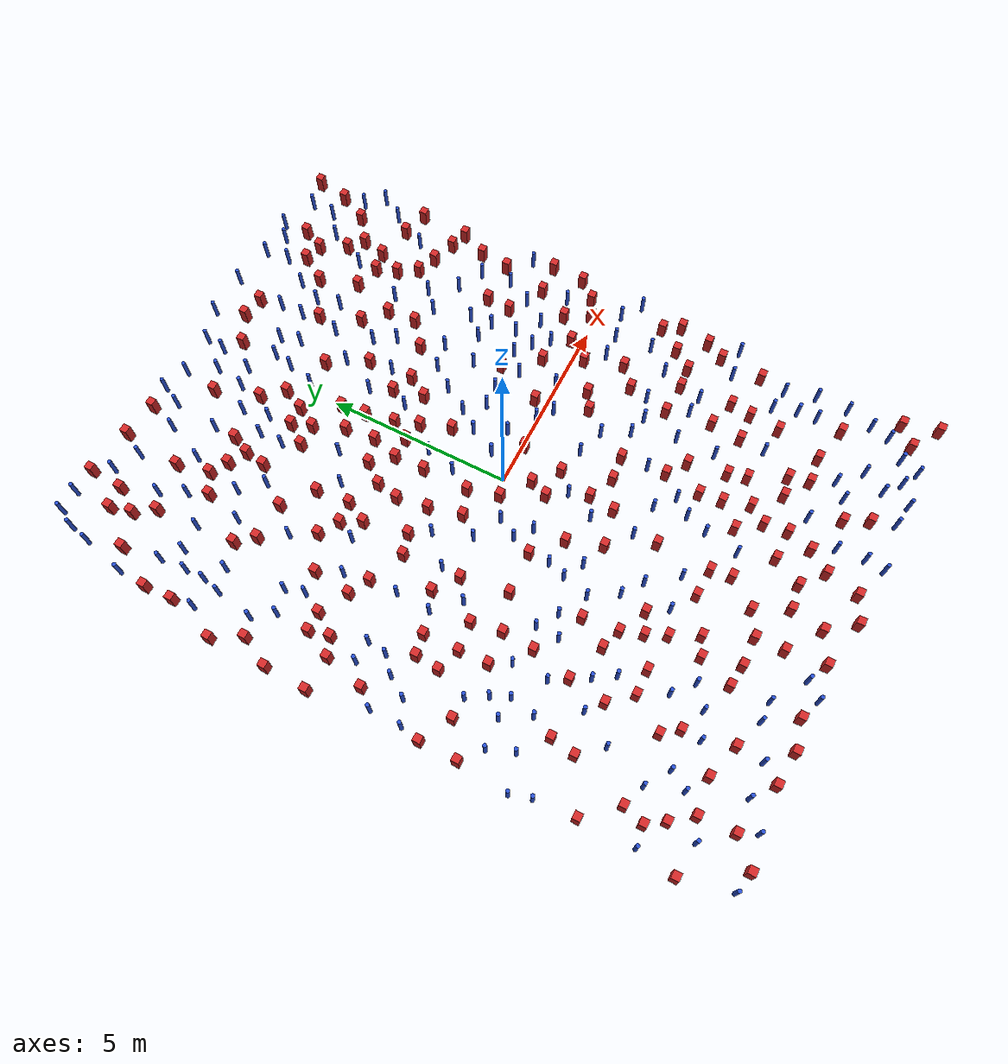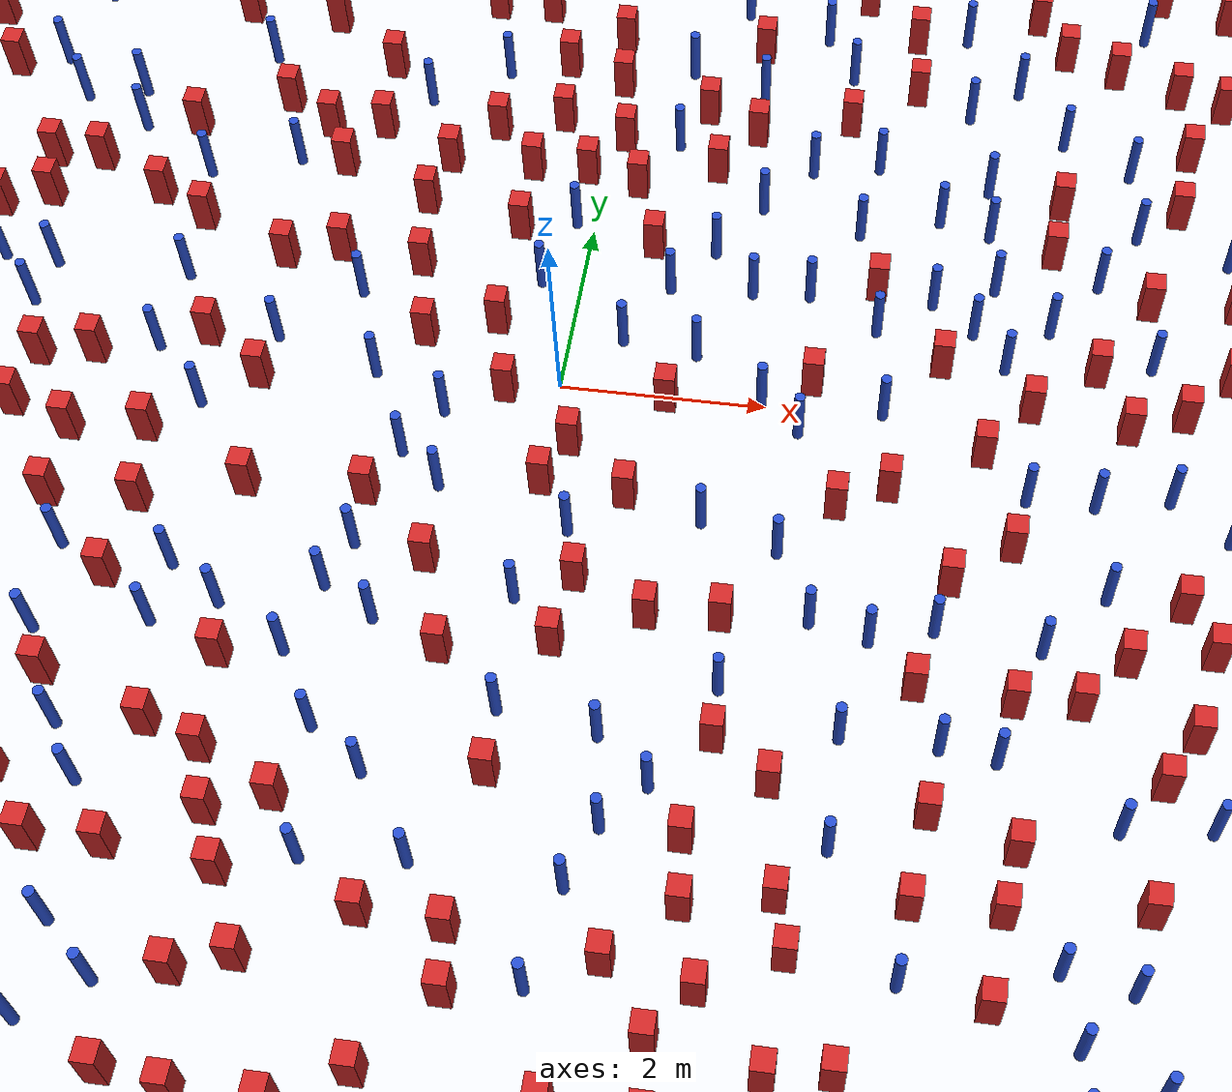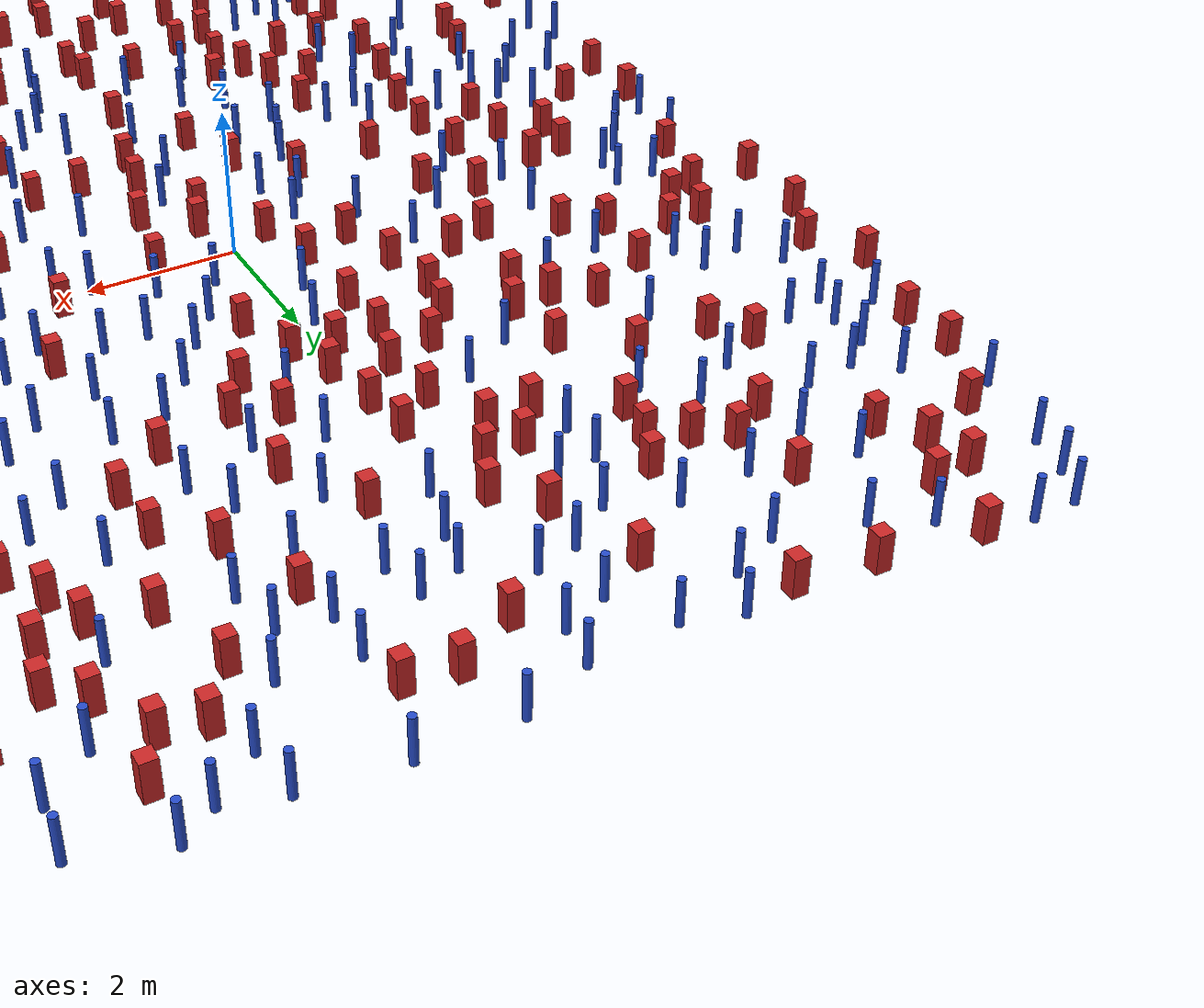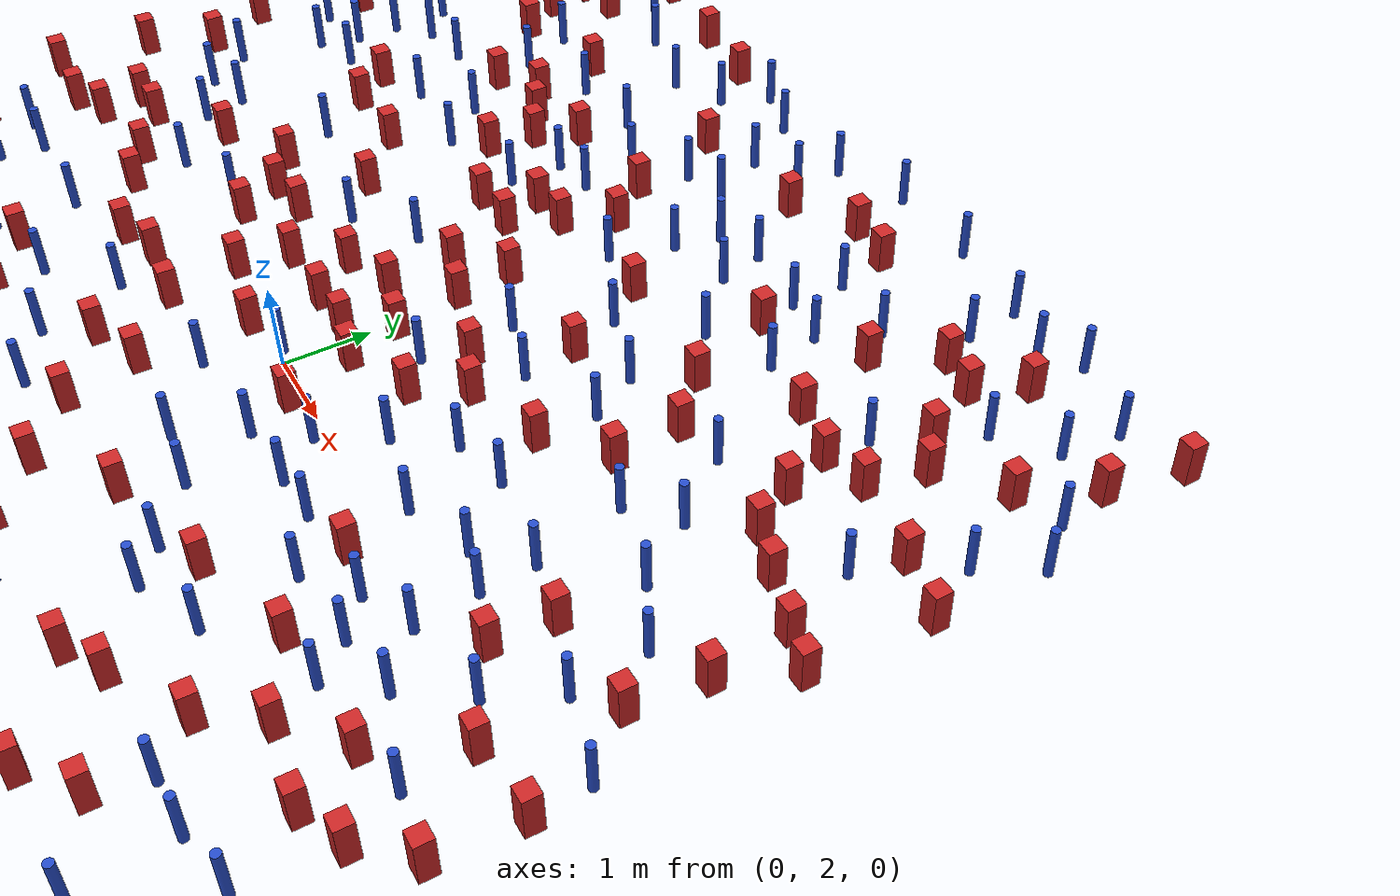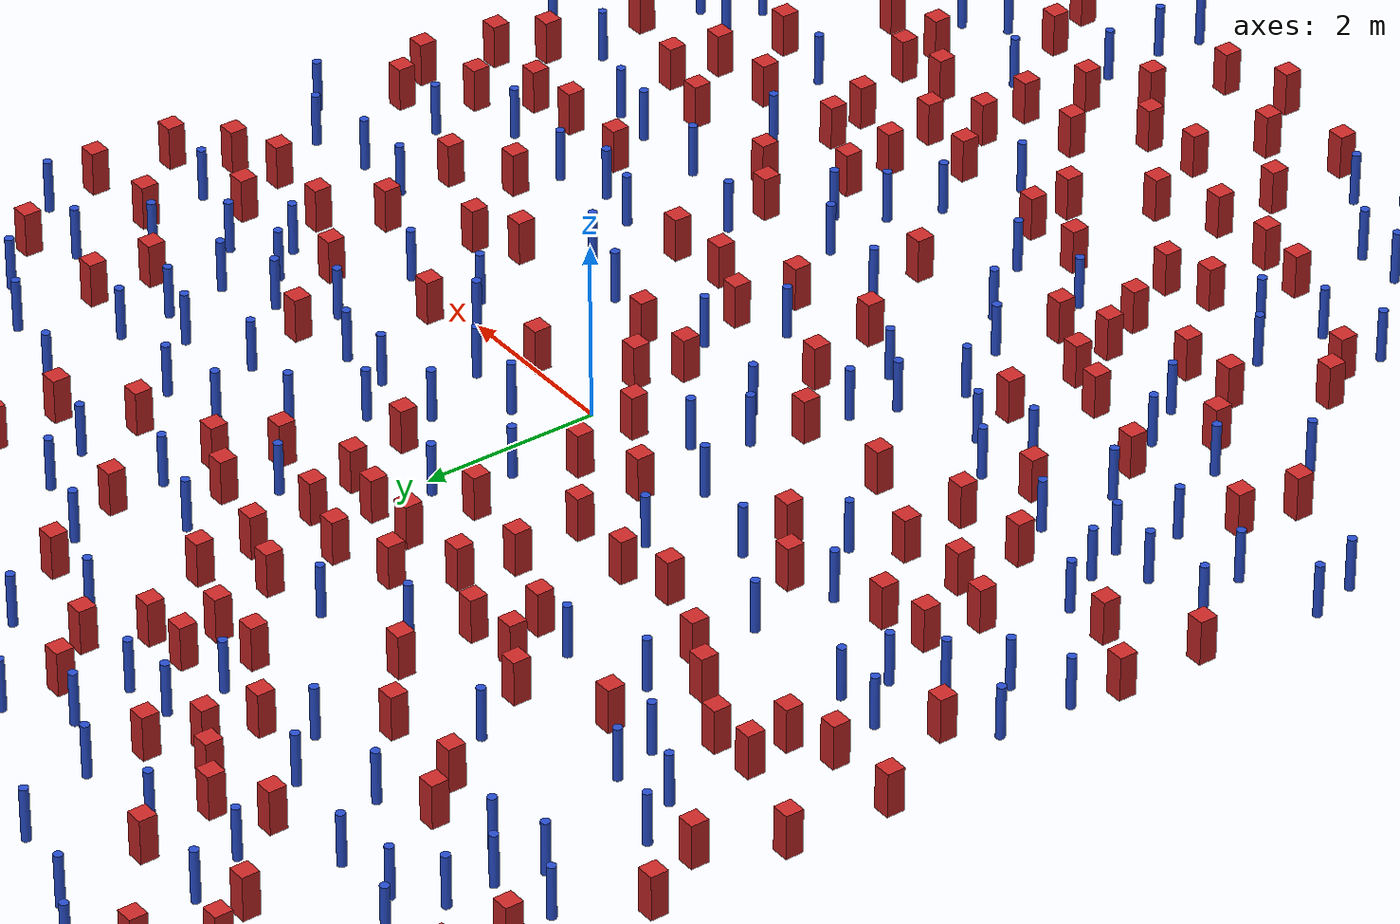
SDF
<sdf version="1.6">
  <model name="dense_48"><model name="square_post_obstacle0">
  <static>true</static>
  <pose frame="">3.41499877253 -6.9940622312 8.22691968438e-08 7.22125133819e-06 -7.54495500217e-07 2.29674213826e-05</pose>
  <link name="link">
    <pose frame="">0 0 0.25 0 -0 0</pose>
    <inertial>
      <mass>100</mass>
      <inertia>
        <ixx>0.166667</ixx>
        <ixy>0</ixy>
        <ixz>0</ixz>
        <iyy>0.166667</iyy>
        <iyz>0</iyz>
        <izz>0.166667</izz>
      </inertia>
    </inertial>
    <collision name="collision">
      <geometry>
        <box>
          <size>.2 .2 .5</size>
        </box>
      </geometry>
      <max_contacts>10</max_contacts>
      <surface>
        <contact>
          <ode/>
        </contact>
        <bounce/>
        <friction>
          <torsional>
            <ode/>
          </torsional>
          <ode/>
        </friction>
      </surface>
    </collision>
    <visual name="visual">
      <geometry>
        <box>
          <size>.2 .2 .5</size>
        </box>
      </geometry>
      <material>
        <script>
          <name>Gazebo/Red</name>
          <uri>file://media/materials/scripts/gazebo.material</uri>
        </script>
      </material>
    </visual>
    <self_collide>0</self_collide>
    <kinematic>0</kinematic>
  </link>
</model>
<model name="square_post_obstacle1">
  <static>true</static>
  <pose frame="">-0.557334798175 -3.08272760318 8.22691968438e-08 7.2212513382e-06 -7.54495500217e-07 2.29674213826e-05</pose>
  <link name="link">
    <pose frame="">0 0 0.25 0 -0 0</pose>
    <inertial>
      <mass>100</mass>
      <inertia>
        <ixx>0.166667</ixx>
        <ixy>0</ixy>
        <ixz>0</ixz>
        <iyy>0.166667</iyy>
        <iyz>0</iyz>
        <izz>0.166667</izz>
      </inertia>
    </inertial>
    <collision name="collision">
      <geometry>
        <box>
          <size>.2 .2 .5</size>
        </box>
      </geometry>
      <max_contacts>10</max_contacts>
      <surface>
        <contact>
          <ode/>
        </contact>
        <bounce/>
        <friction>
          <torsional>
            <ode/>
          </torsional>
          <ode/>
        </friction>
      </surface>
    </collision>
    <visual name="visual">
      <geometry>
        <box>
          <size>.2 .2 .5</size>
        </box>
      </geometry>
      <material>
        <script>
          <name>Gazebo/Red</name>
          <uri>file://media/materials/scripts/gazebo.material</uri>
        </script>
      </material>
    </visual>
    <self_collide>0</self_collide>
    <kinematic>0</kinematic>
  </link>
</model>
<model name="pole_obstacle0">
  <static>true</static>
  <pose frame="">-4.95712828938 2.83701264804 2.88873142074e-08 -9.90536690245e-09 4.6021994898e-07 -1.20965994966e-07</pose>
  <link name="link">
  <pose frame="">0 0 0.3 0 -0 0</pose>
    <inertial>
      <mass>1</mass>
      <inertia>
        <ixx>0.145833</ixx>
        <ixy>0</ixy>
        <ixz>0</ixz>
        <iyy>0.145833</iyy>
        <iyz>0</iyz>
        <izz>0.125</izz>
      </inertia>
    </inertial>
    <collision name="collision">
      <geometry>
        <cylinder>
          <radius>0.05</radius>
          <length>.6</length>
        </cylinder>
      </geometry>
      <max_contacts>10</max_contacts>
      <surface>
        <contact>
          <ode/>
        </contact>
        <bounce/>
        <friction>
          <torsional>
            <ode/>
          </torsional>
          <ode/>
        </friction>
      </surface>
    </collision>
    <visual name="visual">
      <geometry>
        <cylinder>
          <radius>0.05</radius>
          <length>.6</length>
        </cylinder>
      </geometry>
      <material>
        <script>
          <name>Gazebo/Blue</name>
          <uri>file://media/materials/scripts/gazebo.material</uri>
        </script>
      </material>
    </visual>
    <self_collide>0</self_collide>
    <kinematic>0</kinematic>
  </link>
</model>
<model name="square_post_obstacle2">
  <static>true</static>
  <pose frame="">3.85165815394 -4.12469330242 8.22691968438e-08 7.2212513382e-06 -7.54495500217e-07 2.29674213826e-05</pose>
  <link name="link">
    <pose frame="">0 0 0.25 0 -0 0</pose>
    <inertial>
      <mass>100</mass>
      <inertia>
        <ixx>0.166667</ixx>
        <ixy>0</ixy>
        <ixz>0</ixz>
        <iyy>0.166667</iyy>
        <iyz>0</iyz>
        <izz>0.166667</izz>
      </inertia>
    </inertial>
    <collision name="collision">
      <geometry>
        <box>
          <size>.2 .2 .5</size>
        </box>
      </geometry>
      <max_contacts>10</max_contacts>
      <surface>
        <contact>
          <ode/>
        </contact>
        <bounce/>
        <friction>
          <torsional>
            <ode/>
          </torsional>
          <ode/>
        </friction>
      </surface>
    </collision>
    <visual name="visual">
      <geometry>
        <box>
          <size>.2 .2 .5</size>
        </box>
      </geometry>
      <material>
        <script>
          <name>Gazebo/Red</name>
          <uri>file://media/materials/scripts/gazebo.material</uri>
        </script>
      </material>
    </visual>
    <self_collide>0</self_collide>
    <kinematic>0</kinematic>
  </link>
</model>
<model name="pole_obstacle1">
  <static>true</static>
  <pose frame="">-2.85706242391 0.220407652217 2.88873142074e-08 -9.90536689395e-09 4.60219949e-07 -1.20965994954e-07</pose>
  <link name="link">
  <pose frame="">0 0 0.3 0 -0 0</pose>
    <inertial>
      <mass>1</mass>
      <inertia>
        <ixx>0.145833</ixx>
        <ixy>0</ixy>
        <ixz>0</ixz>
        <iyy>0.145833</iyy>
        <iyz>0</iyz>
        <izz>0.125</izz>
      </inertia>
    </inertial>
    <collision name="collision">
      <geometry>
        <cylinder>
          <radius>0.05</radius>
          <length>.6</length>
        </cylinder>
      </geometry>
      <max_contacts>10</max_contacts>
      <surface>
        <contact>
          <ode/>
        </contact>
        <bounce/>
        <friction>
          <torsional>
            <ode/>
          </torsional>
          <ode/>
        </friction>
      </surface>
    </collision>
    <visual name="visual">
      <geometry>
        <cylinder>
          <radius>0.05</radius>
          <length>.6</length>
        </cylinder>
      </geometry>
      <material>
        <script>
          <name>Gazebo/Blue</name>
          <uri>file://media/materials/scripts/gazebo.material</uri>
        </script>
      </material>
    </visual>
    <self_collide>0</self_collide>
    <kinematic>0</kinematic>
  </link>
</model>
<model name="square_post_obstacle3">
  <static>true</static>
  <pose frame="">-4.37450130229 2.90304461546 8.22691968438e-08 7.2212513382e-06 -7.54495500217e-07 2.29674213826e-05</pose>
  <link name="link">
    <pose frame="">0 0 0.25 0 -0 0</pose>
    <inertial>
      <mass>100</mass>
      <inertia>
        <ixx>0.166667</ixx>
        <ixy>0</ixy>
        <ixz>0</ixz>
        <iyy>0.166667</iyy>
        <iyz>0</iyz>
        <izz>0.166667</izz>
      </inertia>
    </inertial>
    <collision name="collision">
      <geometry>
        <box>
          <size>.2 .2 .5</size>
        </box>
      </geometry>
      <max_contacts>10</max_contacts>
      <surface>
        <contact>
          <ode/>
        </contact>
        <bounce/>
        <friction>
          <torsional>
            <ode/>
          </torsional>
          <ode/>
        </friction>
      </surface>
    </collision>
    <visual name="visual">
      <geometry>
        <box>
          <size>.2 .2 .5</size>
        </box>
      </geometry>
      <material>
        <script>
          <name>Gazebo/Red</name>
          <uri>file://media/materials/scripts/gazebo.material</uri>
        </script>
      </material>
    </visual>
    <self_collide>0</self_collide>
    <kinematic>0</kinematic>
  </link>
</model>
<model name="pole_obstacle2">
  <static>true</static>
  <pose frame="">-2.87501459005 -8.10694990462 2.88873142074e-08 -9.90536692318e-09 4.6021994893e-07 -1.20965994988e-07</pose>
  <link name="link">
  <pose frame="">0 0 0.3 0 -0 0</pose>
    <inertial>
      <mass>1</mass>
      <inertia>
        <ixx>0.145833</ixx>
        <ixy>0</ixy>
        <ixz>0</ixz>
        <iyy>0.145833</iyy>
        <iyz>0</iyz>
        <izz>0.125</izz>
      </inertia>
    </inertial>
    <collision name="collision">
      <geometry>
        <cylinder>
          <radius>0.05</radius>
          <length>.6</length>
        </cylinder>
      </geometry>
      <max_contacts>10</max_contacts>
      <surface>
        <contact>
          <ode/>
        </contact>
        <bounce/>
        <friction>
          <torsional>
            <ode/>
          </torsional>
          <ode/>
        </friction>
      </surface>
    </collision>
    <visual name="visual">
      <geometry>
        <cylinder>
          <radius>0.05</radius>
          <length>.6</length>
        </cylinder>
      </geometry>
      <material>
        <script>
          <name>Gazebo/Blue</name>
          <uri>file://media/materials/scripts/gazebo.material</uri>
        </script>
      </material>
    </visual>
    <self_collide>0</self_collide>
    <kinematic>0</kinematic>
  </link>
</model>
<model name="pole_obstacle3">
  <static>true</static>
  <pose frame="">-5.79340211494 -0.0211632586068 2.88873142074e-08 -9.90536690003e-09 4.60219948985e-07 -1.20965994965e-07</pose>
  <link name="link">
  <pose frame="">0 0 0.3 0 -0 0</pose>
    <inertial>
      <mass>1</mass>
      <inertia>
        <ixx>0.145833</ixx>
        <ixy>0</ixy>
        <ixz>0</ixz>
        <iyy>0.145833</iyy>
        <iyz>0</iyz>
        <izz>0.125</izz>
      </inertia>
    </inertial>
    <collision name="collision">
      <geometry>
        <cylinder>
          <radius>0.05</radius>
          <length>.6</length>
        </cylinder>
      </geometry>
      <max_contacts>10</max_contacts>
      <surface>
        <contact>
          <ode/>
        </contact>
        <bounce/>
        <friction>
          <torsional>
            <ode/>
          </torsional>
          <ode/>
        </friction>
      </surface>
    </collision>
    <visual name="visual">
      <geometry>
        <cylinder>
          <radius>0.05</radius>
          <length>.6</length>
        </cylinder>
      </geometry>
      <material>
        <script>
          <name>Gazebo/Blue</name>
          <uri>file://media/materials/scripts/gazebo.material</uri>
        </script>
      </material>
    </visual>
    <self_collide>0</self_collide>
    <kinematic>0</kinematic>
  </link>
</model>
<model name="square_post_obstacle4">
  <static>true</static>
  <pose frame="">-3.66328525411 -1.86673126845 8.22691968438e-08 7.2212513382e-06 -7.54495500217e-07 2.29674213826e-05</pose>
  <link name="link">
    <pose frame="">0 0 0.25 0 -0 0</pose>
    <inertial>
      <mass>100</mass>
      <inertia>
        <ixx>0.166667</ixx>
        <ixy>0</ixy>
        <ixz>0</ixz>
        <iyy>0.166667</iyy>
        <iyz>0</iyz>
        <izz>0.166667</izz>
      </inertia>
    </inertial>
    <collision name="collision">
      <geometry>
        <box>
          <size>.2 .2 .5</size>
        </box>
      </geometry>
      <max_contacts>10</max_contacts>
      <surface>
        <contact>
          <ode/>
        </contact>
        <bounce/>
        <friction>
          <torsional>
            <ode/>
          </torsional>
          <ode/>
        </friction>
      </surface>
    </collision>
    <visual name="visual">
      <geometry>
        <box>
          <size>.2 .2 .5</size>
        </box>
      </geometry>
      <material>
        <script>
          <name>Gazebo/Red</name>
          <uri>file://media/materials/scripts/gazebo.material</uri>
        </script>
      </material>
    </visual>
    <self_collide>0</self_collide>
    <kinematic>0</kinematic>
  </link>
</model>
<model name="square_post_obstacle5">
  <static>true</static>
  <pose frame="">-0.730659608983 0.664554356461 8.22691968438e-08 7.2212513382e-06 -7.54495500217e-07 2.29674213826e-05</pose>
  <link name="link">
    <pose frame="">0 0 0.25 0 -0 0</pose>
    <inertial>
      <mass>100</mass>
      <inertia>
        <ixx>0.166667</ixx>
        <ixy>0</ixy>
        <ixz>0</ixz>
        <iyy>0.166667</iyy>
        <iyz>0</iyz>
        <izz>0.166667</izz>
      </inertia>
    </inertial>
    <collision name="collision">
      <geometry>
        <box>
          <size>.2 .2 .5</size>
        </box>
      </geometry>
      <max_contacts>10</max_contacts>
      <surface>
        <contact>
          <ode/>
        </contact>
        <bounce/>
        <friction>
          <torsional>
            <ode/>
          </torsional>
          <ode/>
        </friction>
      </surface>
    </collision>
    <visual name="visual">
      <geometry>
        <box>
          <size>.2 .2 .5</size>
        </box>
      </geometry>
      <material>
        <script>
          <name>Gazebo/Red</name>
          <uri>file://media/materials/scripts/gazebo.material</uri>
        </script>
      </material>
    </visual>
    <self_collide>0</self_collide>
    <kinematic>0</kinematic>
  </link>
</model>
<model name="square_post_obstacle6">
  <static>true</static>
  <pose frame="">-6.9856799649 1.56313653754 8.22691968438e-08 7.2212513382e-06 -7.54495500217e-07 2.29674213826e-05</pose>
  <link name="link">
    <pose frame="">0 0 0.25 0 -0 0</pose>
    <inertial>
      <mass>100</mass>
      <inertia>
        <ixx>0.166667</ixx>
        <ixy>0</ixy>
        <ixz>0</ixz>
        <iyy>0.166667</iyy>
        <iyz>0</iyz>
        <izz>0.166667</izz>
      </inertia>
    </inertial>
    <collision name="collision">
      <geometry>
        <box>
          <size>.2 .2 .5</size>
        </box>
      </geometry>
      <max_contacts>10</max_contacts>
      <surface>
        <contact>
          <ode/>
        </contact>
        <bounce/>
        <friction>
          <torsional>
            <ode/>
          </torsional>
          <ode/>
        </friction>
      </surface>
    </collision>
    <visual name="visual">
      <geometry>
        <box>
          <size>.2 .2 .5</size>
        </box>
      </geometry>
      <material>
        <script>
          <name>Gazebo/Red</name>
          <uri>file://media/materials/scripts/gazebo.material</uri>
        </script>
      </material>
    </visual>
    <self_collide>0</self_collide>
    <kinematic>0</kinematic>
  </link>
</model>
<model name="pole_obstacle4">
  <static>true</static>
  <pose frame="">-3.90233970964 -7.05207749594 2.88873142074e-08 -9.90536689859e-09 4.60219948989e-07 -1.20965994961e-07</pose>
  <link name="link">
  <pose frame="">0 0 0.3 0 -0 0</pose>
    <inertial>
      <mass>1</mass>
      <inertia>
        <ixx>0.145833</ixx>
        <ixy>0</ixy>
        <ixz>0</ixz>
        <iyy>0.145833</iyy>
        <iyz>0</iyz>
        <izz>0.125</izz>
      </inertia>
    </inertial>
    <collision name="collision">
      <geometry>
        <cylinder>
          <radius>0.05</radius>
          <length>.6</length>
        </cylinder>
      </geometry>
      <max_contacts>10</max_contacts>
      <surface>
        <contact>
          <ode/>
        </contact>
        <bounce/>
        <friction>
          <torsional>
            <ode/>
          </torsional>
          <ode/>
        </friction>
      </surface>
    </collision>
    <visual name="visual">
      <geometry>
        <cylinder>
          <radius>0.05</radius>
          <length>.6</length>
        </cylinder>
      </geometry>
      <material>
        <script>
          <name>Gazebo/Blue</name>
          <uri>file://media/materials/scripts/gazebo.material</uri>
        </script>
      </material>
    </visual>
    <self_collide>0</self_collide>
    <kinematic>0</kinematic>
  </link>
</model>
<model name="pole_obstacle5">
  <static>true</static>
  <pose frame="">6.26475696743 -3.95670145354 2.88873142074e-08 -9.90536690067e-09 4.60219948984e-07 -1.20965994963e-07</pose>
  <link name="link">
  <pose frame="">0 0 0.3 0 -0 0</pose>
    <inertial>
      <mass>1</mass>
      <inertia>
        <ixx>0.145833</ixx>
        <ixy>0</ixy>
        <ixz>0</ixz>
        <iyy>0.145833</iyy>
        <iyz>0</iyz>
        <izz>0.125</izz>
      </inertia>
    </inertial>
    <collision name="collision">
      <geometry>
        <cylinder>
          <radius>0.05</radius>
          <length>.6</length>
        </cylinder>
      </geometry>
      <max_contacts>10</max_contacts>
      <surface>
        <contact>
          <ode/>
        </contact>
        <bounce/>
        <friction>
          <torsional>
            <ode/>
          </torsional>
          <ode/>
        </friction>
      </surface>
    </collision>
    <visual name="visual">
      <geometry>
        <cylinder>
          <radius>0.05</radius>
          <length>.6</length>
        </cylinder>
      </geometry>
      <material>
        <script>
          <name>Gazebo/Blue</name>
          <uri>file://media/materials/scripts/gazebo.material</uri>
        </script>
      </material>
    </visual>
    <self_collide>0</self_collide>
    <kinematic>0</kinematic>
  </link>
</model>
<model name="square_post_obstacle7">
  <static>true</static>
  <pose frame="">5.98990536124 -1.79606220734 8.22691968438e-08 7.2212513382e-06 -7.54495500217e-07 2.29674213826e-05</pose>
  <link name="link">
    <pose frame="">0 0 0.25 0 -0 0</pose>
    <inertial>
      <mass>100</mass>
      <inertia>
        <ixx>0.166667</ixx>
        <ixy>0</ixy>
        <ixz>0</ixz>
        <iyy>0.166667</iyy>
        <iyz>0</iyz>
        <izz>0.166667</izz>
      </inertia>
    </inertial>
    <collision name="collision">
      <geometry>
        <box>
          <size>.2 .2 .5</size>
        </box>
      </geometry>
      <max_contacts>10</max_contacts>
      <surface>
        <contact>
          <ode/>
        </contact>
        <bounce/>
        <friction>
          <torsional>
            <ode/>
          </torsional>
          <ode/>
        </friction>
      </surface>
    </collision>
    <visual name="visual">
      <geometry>
        <box>
          <size>.2 .2 .5</size>
        </box>
      </geometry>
      <material>
        <script>
          <name>Gazebo/Red</name>
          <uri>file://media/materials/scripts/gazebo.material</uri>
        </script>
      </material>
    </visual>
    <self_collide>0</self_collide>
    <kinematic>0</kinematic>
  </link>
</model>
<model name="square_post_obstacle8">
  <static>true</static>
  <pose frame="">-3.8739137678 -6.55209940469 8.22691968438e-08 7.22125133819e-06 -7.54495500217e-07 2.29674213826e-05</pose>
  <link name="link">
    <pose frame="">0 0 0.25 0 -0 0</pose>
    <inertial>
      <mass>100</mass>
      <inertia>
        <ixx>0.166667</ixx>
        <ixy>0</ixy>
        <ixz>0</ixz>
        <iyy>0.166667</iyy>
        <iyz>0</iyz>
        <izz>0.166667</izz>
      </inertia>
    </inertial>
    <collision name="collision">
      <geometry>
        <box>
          <size>.2 .2 .5</size>
        </box>
      </geometry>
      <max_contacts>10</max_contacts>
      <surface>
        <contact>
          <ode/>
        </contact>
        <bounce/>
        <friction>
          <torsional>
            <ode/>
          </torsional>
          <ode/>
        </friction>
      </surface>
    </collision>
    <visual name="visual">
      <geometry>
        <box>
          <size>.2 .2 .5</size>
        </box>
      </geometry>
      <material>
        <script>
          <name>Gazebo/Red</name>
          <uri>file://media/materials/scripts/gazebo.material</uri>
        </script>
      </material>
    </visual>
    <self_collide>0</self_collide>
    <kinematic>0</kinematic>
  </link>
</model>
<model name="pole_obstacle6">
  <static>true</static>
  <pose frame="">5.31308044122 8.27978199342 2.88873142074e-08 -9.9053668967e-09 4.60219948993e-07 -1.20965994957e-07</pose>
  <link name="link">
  <pose frame="">0 0 0.3 0 -0 0</pose>
    <inertial>
      <mass>1</mass>
      <inertia>
        <ixx>0.145833</ixx>
        <ixy>0</ixy>
        <ixz>0</ixz>
        <iyy>0.145833</iyy>
        <iyz>0</iyz>
        <izz>0.125</izz>
      </inertia>
    </inertial>
    <collision name="collision">
      <geometry>
        <cylinder>
          <radius>0.05</radius>
          <length>.6</length>
        </cylinder>
      </geometry>
      <max_contacts>10</max_contacts>
      <surface>
        <contact>
          <ode/>
        </contact>
        <bounce/>
        <friction>
          <torsional>
            <ode/>
          </torsional>
          <ode/>
        </friction>
      </surface>
    </collision>
    <visual name="visual">
      <geometry>
        <cylinder>
          <radius>0.05</radius>
          <length>.6</length>
        </cylinder>
      </geometry>
      <material>
        <script>
          <name>Gazebo/Blue</name>
          <uri>file://media/materials/scripts/gazebo.material</uri>
        </script>
      </material>
    </visual>
    <self_collide>0</self_collide>
    <kinematic>0</kinematic>
  </link>
</model>
<model name="pole_obstacle7">
  <static>true</static>
  <pose frame="">-1.73216548762 -2.53938346659 2.88873142074e-08 -9.90536689791e-09 4.6021994899e-07 -1.20965994959e-07</pose>
  <link name="link">
  <pose frame="">0 0 0.3 0 -0 0</pose>
    <inertial>
      <mass>1</mass>
      <inertia>
        <ixx>0.145833</ixx>
        <ixy>0</ixy>
        <ixz>0</ixz>
        <iyy>0.145833</iyy>
        <iyz>0</iyz>
        <izz>0.125</izz>
      </inertia>
    </inertial>
    <collision name="collision">
      <geometry>
        <cylinder>
          <radius>0.05</radius>
          <length>.6</length>
        </cylinder>
      </geometry>
      <max_contacts>10</max_contacts>
      <surface>
        <contact>
          <ode/>
        </contact>
        <bounce/>
        <friction>
          <torsional>
            <ode/>
          </torsional>
          <ode/>
        </friction>
      </surface>
    </collision>
    <visual name="visual">
      <geometry>
        <cylinder>
          <radius>0.05</radius>
          <length>.6</length>
        </cylinder>
      </geometry>
      <material>
        <script>
          <name>Gazebo/Blue</name>
          <uri>file://media/materials/scripts/gazebo.material</uri>
        </script>
      </material>
    </visual>
    <self_collide>0</self_collide>
    <kinematic>0</kinematic>
  </link>
</model>
<model name="square_post_obstacle9">
  <static>true</static>
  <pose frame="">1.16110628064 2.9553017681 8.22691968438e-08 7.2212513382e-06 -7.54495500217e-07 2.29674213826e-05</pose>
  <link name="link">
    <pose frame="">0 0 0.25 0 -0 0</pose>
    <inertial>
      <mass>100</mass>
      <inertia>
        <ixx>0.166667</ixx>
        <ixy>0</ixy>
        <ixz>0</ixz>
        <iyy>0.166667</iyy>
        <iyz>0</iyz>
        <izz>0.166667</izz>
      </inertia>
    </inertial>
    <collision name="collision">
      <geometry>
        <box>
          <size>.2 .2 .5</size>
        </box>
      </geometry>
      <max_contacts>10</max_contacts>
      <surface>
        <contact>
          <ode/>
        </contact>
        <bounce/>
        <friction>
          <torsional>
            <ode/>
          </torsional>
          <ode/>
        </friction>
      </surface>
    </collision>
    <visual name="visual">
      <geometry>
        <box>
          <size>.2 .2 .5</size>
        </box>
      </geometry>
      <material>
        <script>
          <name>Gazebo/Red</name>
          <uri>file://media/materials/scripts/gazebo.material</uri>
        </script>
      </material>
    </visual>
    <self_collide>0</self_collide>
    <kinematic>0</kinematic>
  </link>
</model>
<model name="square_post_obstacle10">
  <static>true</static>
  <pose frame="">3.06027018239 -8.713658144 8.22691968438e-08 7.22125133819e-06 -7.54495500217e-07 2.29674213826e-05</pose>
  <link name="link">
    <pose frame="">0 0 0.25 0 -0 0</pose>
    <inertial>
      <mass>100</mass>
      <inertia>
        <ixx>0.166667</ixx>
        <ixy>0</ixy>
        <ixz>0</ixz>
        <iyy>0.166667</iyy>
        <iyz>0</iyz>
        <izz>0.166667</izz>
      </inertia>
    </inertial>
    <collision name="collision">
      <geometry>
        <box>
          <size>.2 .2 .5</size>
        </box>
      </geometry>
      <max_contacts>10</max_contacts>
      <surface>
        <contact>
          <ode/>
        </contact>
        <bounce/>
        <friction>
          <torsional>
            <ode/>
          </torsional>
          <ode/>
        </friction>
      </surface>
    </collision>
    <visual name="visual">
      <geometry>
        <box>
          <size>.2 .2 .5</size>
        </box>
      </geometry>
      <material>
        <script>
          <name>Gazebo/Red</name>
          <uri>file://media/materials/scripts/gazebo.material</uri>
        </script>
      </material>
    </visual>
    <self_collide>0</self_collide>
    <kinematic>0</kinematic>
  </link>
</model>
<model name="square_post_obstacle11">
  <static>true</static>
  <pose frame="">-6.94486312321 2.71346720038 8.22691968438e-08 7.2212513382e-06 -7.54495500217e-07 2.29674213826e-05</pose>
  <link name="link">
    <pose frame="">0 0 0.25 0 -0 0</pose>
    <inertial>
      <mass>100</mass>
      <inertia>
        <ixx>0.166667</ixx>
        <ixy>0</ixy>
        <ixz>0</ixz>
        <iyy>0.166667</iyy>
        <iyz>0</iyz>
        <izz>0.166667</izz>
      </inertia>
    </inertial>
    <collision name="collision">
      <geometry>
        <box>
          <size>.2 .2 .5</size>
        </box>
      </geometry>
      <max_contacts>10</max_contacts>
      <surface>
        <contact>
          <ode/>
        </contact>
        <bounce/>
        <friction>
          <torsional>
            <ode/>
          </torsional>
          <ode/>
        </friction>
      </surface>
    </collision>
    <visual name="visual">
      <geometry>
        <box>
          <size>.2 .2 .5</size>
        </box>
      </geometry>
      <material>
        <script>
          <name>Gazebo/Red</name>
          <uri>file://media/materials/scripts/gazebo.material</uri>
        </script>
      </material>
    </visual>
    <self_collide>0</self_collide>
    <kinematic>0</kinematic>
  </link>
</model>
<model name="square_post_obstacle12">
  <static>true</static>
  <pose frame="">-0.0130934757853 -7.77081000379 8.22691968438e-08 7.2212513382e-06 -7.54495500217e-07 2.29674213826e-05</pose>
  <link name="link">
    <pose frame="">0 0 0.25 0 -0 0</pose>
    <inertial>
      <mass>100</mass>
      <inertia>
        <ixx>0.166667</ixx>
        <ixy>0</ixy>
        <ixz>0</ixz>
        <iyy>0.166667</iyy>
        <iyz>0</iyz>
        <izz>0.166667</izz>
      </inertia>
    </inertial>
    <collision name="collision">
      <geometry>
        <box>
          <size>.2 .2 .5</size>
        </box>
      </geometry>
      <max_contacts>10</max_contacts>
      <surface>
        <contact>
          <ode/>
        </contact>
        <bounce/>
        <friction>
          <torsional>
            <ode/>
          </torsional>
          <ode/>
        </friction>
      </surface>
    </collision>
    <visual name="visual">
      <geometry>
        <box>
          <size>.2 .2 .5</size>
        </box>
      </geometry>
      <material>
        <script>
          <name>Gazebo/Red</name>
          <uri>file://media/materials/scripts/gazebo.material</uri>
        </script>
      </material>
    </visual>
    <self_collide>0</self_collide>
    <kinematic>0</kinematic>
  </link>
</model>
<model name="square_post_obstacle13">
  <static>true</static>
  <pose frame="">-5.16516771168 -0.941225896846 8.22691968438e-08 7.2212513382e-06 -7.54495500217e-07 2.29674213826e-05</pose>
  <link name="link">
    <pose frame="">0 0 0.25 0 -0 0</pose>
    <inertial>
      <mass>100</mass>
      <inertia>
        <ixx>0.166667</ixx>
        <ixy>0</ixy>
        <ixz>0</ixz>
        <iyy>0.166667</iyy>
        <iyz>0</iyz>
        <izz>0.166667</izz>
      </inertia>
    </inertial>
    <collision name="collision">
      <geometry>
        <box>
          <size>.2 .2 .5</size>
        </box>
      </geometry>
      <max_contacts>10</max_contacts>
      <surface>
        <contact>
          <ode/>
        </contact>
        <bounce/>
        <friction>
          <torsional>
            <ode/>
          </torsional>
          <ode/>
        </friction>
      </surface>
    </collision>
    <visual name="visual">
      <geometry>
        <box>
          <size>.2 .2 .5</size>
        </box>
      </geometry>
      <material>
        <script>
          <name>Gazebo/Red</name>
          <uri>file://media/materials/scripts/gazebo.material</uri>
        </script>
      </material>
    </visual>
    <self_collide>0</self_collide>
    <kinematic>0</kinematic>
  </link>
</model>
<model name="pole_obstacle8">
  <static>true</static>
  <pose frame="">-1.50866007726 -3.9638408501 2.88873142074e-08 -9.90536689586e-09 4.60219948995e-07 -1.20965994956e-07</pose>
  <link name="link">
  <pose frame="">0 0 0.3 0 -0 0</pose>
    <inertial>
      <mass>1</mass>
      <inertia>
        <ixx>0.145833</ixx>
        <ixy>0</ixy>
        <ixz>0</ixz>
        <iyy>0.145833</iyy>
        <iyz>0</iyz>
        <izz>0.125</izz>
      </inertia>
    </inertial>
    <collision name="collision">
      <geometry>
        <cylinder>
          <radius>0.05</radius>
          <length>.6</length>
        </cylinder>
      </geometry>
      <max_contacts>10</max_contacts>
      <surface>
        <contact>
          <ode/>
        </contact>
        <bounce/>
        <friction>
          <torsional>
            <ode/>
          </torsional>
          <ode/>
        </friction>
      </surface>
    </collision>
    <visual name="visual">
      <geometry>
        <cylinder>
          <radius>0.05</radius>
          <length>.6</length>
        </cylinder>
      </geometry>
      <material>
        <script>
          <name>Gazebo/Blue</name>
          <uri>file://media/materials/scripts/gazebo.material</uri>
        </script>
      </material>
    </visual>
    <self_collide>0</self_collide>
    <kinematic>0</kinematic>
  </link>
</model>
<model name="square_post_obstacle14">
  <static>true</static>
  <pose frame="">4.10795754205 -0.32786102376 8.22691968438e-08 7.2212513382e-06 -7.54495500217e-07 2.29674213826e-05</pose>
  <link name="link">
    <pose frame="">0 0 0.25 0 -0 0</pose>
    <inertial>
      <mass>100</mass>
      <inertia>
        <ixx>0.166667</ixx>
        <ixy>0</ixy>
        <ixz>0</ixz>
        <iyy>0.166667</iyy>
        <iyz>0</iyz>
        <izz>0.166667</izz>
      </inertia>
    </inertial>
    <collision name="collision">
      <geometry>
        <box>
          <size>.2 .2 .5</size>
        </box>
      </geometry>
      <max_contacts>10</max_contacts>
      <surface>
        <contact>
          <ode/>
        </contact>
        <bounce/>
        <friction>
          <torsional>
            <ode/>
          </torsional>
          <ode/>
        </friction>
      </surface>
    </collision>
    <visual name="visual">
      <geometry>
        <box>
          <size>.2 .2 .5</size>
        </box>
      </geometry>
      <material>
        <script>
          <name>Gazebo/Red</name>
          <uri>file://media/materials/scripts/gazebo.material</uri>
        </script>
      </material>
    </visual>
    <self_collide>0</self_collide>
    <kinematic>0</kinematic>
  </link>
</model>
<model name="square_post_obstacle15">
  <static>true</static>
  <pose frame="">4.46709414449 -5.74250624723 8.22691968438e-08 7.2212513382e-06 -7.54495500217e-07 2.29674213826e-05</pose>
  <link name="link">
    <pose frame="">0 0 0.25 0 -0 0</pose>
    <inertial>
      <mass>100</mass>
      <inertia>
        <ixx>0.166667</ixx>
        <ixy>0</ixy>
        <ixz>0</ixz>
        <iyy>0.166667</iyy>
        <iyz>0</iyz>
        <izz>0.166667</izz>
      </inertia>
    </inertial>
    <collision name="collision">
      <geometry>
        <box>
          <size>.2 .2 .5</size>
        </box>
      </geometry>
      <max_contacts>10</max_contacts>
      <surface>
        <contact>
          <ode/>
        </contact>
        <bounce/>
        <friction>
          <torsional>
            <ode/>
          </torsional>
          <ode/>
        </friction>
      </surface>
    </collision>
    <visual name="visual">
      <geometry>
        <box>
          <size>.2 .2 .5</size>
        </box>
      </geometry>
      <material>
        <script>
          <name>Gazebo/Red</name>
          <uri>file://media/materials/scripts/gazebo.material</uri>
        </script>
      </material>
    </visual>
    <self_collide>0</self_collide>
    <kinematic>0</kinematic>
  </link>
</model>
<model name="square_post_obstacle16">
  <static>true</static>
  <pose frame="">-2.38865668269 -8.89311155857 8.22691968438e-08 7.22125133819e-06 -7.54495500217e-07 2.29674213826e-05</pose>
  <link name="link">
    <pose frame="">0 0 0.25 0 -0 0</pose>
    <inertial>
      <mass>100</mass>
      <inertia>
        <ixx>0.166667</ixx>
        <ixy>0</ixy>
        <ixz>0</ixz>
        <iyy>0.166667</iyy>
        <iyz>0</iyz>
        <izz>0.166667</izz>
      </inertia>
    </inertial>
    <collision name="collision">
      <geometry>
        <box>
          <size>.2 .2 .5</size>
        </box>
      </geometry>
      <max_contacts>10</max_contacts>
      <surface>
        <contact>
          <ode/>
        </contact>
        <bounce/>
        <friction>
          <torsional>
            <ode/>
          </torsional>
          <ode/>
        </friction>
      </surface>
    </collision>
    <visual name="visual">
      <geometry>
        <box>
          <size>.2 .2 .5</size>
        </box>
      </geometry>
      <material>
        <script>
          <name>Gazebo/Red</name>
          <uri>file://media/materials/scripts/gazebo.material</uri>
        </script>
      </material>
    </visual>
    <self_collide>0</self_collide>
    <kinematic>0</kinematic>
  </link>
</model>
<model name="pole_obstacle9">
  <static>true</static>
  <pose frame="">2.44209046264 -7.28755723287 2.88873142074e-08 -9.90536689859e-09 4.60219948989e-07 -1.20965994961e-07</pose>
  <link name="link">
  <pose frame="">0 0 0.3 0 -0 0</pose>
    <inertial>
      <mass>1</mass>
      <inertia>
        <ixx>0.145833</ixx>
        <ixy>0</ixy>
        <ixz>0</ixz>
        <iyy>0.145833</iyy>
        <iyz>0</iyz>
        <izz>0.125</izz>
      </inertia>
    </inertial>
    <collision name="collision">
      <geometry>
        <cylinder>
          <radius>0.05</radius>
          <length>.6</length>
        </cylinder>
      </geometry>
      <max_contacts>10</max_contacts>
      <surface>
        <contact>
          <ode/>
        </contact>
        <bounce/>
        <friction>
          <torsional>
            <ode/>
          </torsional>
          <ode/>
        </friction>
      </surface>
    </collision>
    <visual name="visual">
      <geometry>
        <cylinder>
          <radius>0.05</radius>
          <length>.6</length>
        </cylinder>
      </geometry>
      <material>
        <script>
          <name>Gazebo/Blue</name>
          <uri>file://media/materials/scripts/gazebo.material</uri>
        </script>
      </material>
    </visual>
    <self_collide>0</self_collide>
    <kinematic>0</kinematic>
  </link>
</model>
<model name="square_post_obstacle17">
  <static>true</static>
  <pose frame="">-0.951644109244 5.10202093142 8.22691968438e-08 7.22125133819e-06 -7.54495500217e-07 2.29674213826e-05</pose>
  <link name="link">
    <pose frame="">0 0 0.25 0 -0 0</pose>
    <inertial>
      <mass>100</mass>
      <inertia>
        <ixx>0.166667</ixx>
        <ixy>0</ixy>
        <ixz>0</ixz>
        <iyy>0.166667</iyy>
        <iyz>0</iyz>
        <izz>0.166667</izz>
      </inertia>
    </inertial>
    <collision name="collision">
      <geometry>
        <box>
          <size>.2 .2 .5</size>
        </box>
      </geometry>
      <max_contacts>10</max_contacts>
      <surface>
        <contact>
          <ode/>
        </contact>
        <bounce/>
        <friction>
          <torsional>
            <ode/>
          </torsional>
          <ode/>
        </friction>
      </surface>
    </collision>
    <visual name="visual">
      <geometry>
        <box>
          <size>.2 .2 .5</size>
        </box>
      </geometry>
      <material>
        <script>
          <name>Gazebo/Red</name>
          <uri>file://media/materials/scripts/gazebo.material</uri>
        </script>
      </material>
    </visual>
    <self_collide>0</self_collide>
    <kinematic>0</kinematic>
  </link>
</model>
<model name="square_post_obstacle18">
  <static>true</static>
  <pose frame="">-2.48513393565 -3.38515843492 8.22691968438e-08 7.2212513382e-06 -7.54495500217e-07 2.29674213826e-05</pose>
  <link name="link">
    <pose frame="">0 0 0.25 0 -0 0</pose>
    <inertial>
      <mass>100</mass>
      <inertia>
        <ixx>0.166667</ixx>
        <ixy>0</ixy>
        <ixz>0</ixz>
        <iyy>0.166667</iyy>
        <iyz>0</iyz>
        <izz>0.166667</izz>
      </inertia>
    </inertial>
    <collision name="collision">
      <geometry>
        <box>
          <size>.2 .2 .5</size>
        </box>
      </geometry>
      <max_contacts>10</max_contacts>
      <surface>
        <contact>
          <ode/>
        </contact>
        <bounce/>
        <friction>
          <torsional>
            <ode/>
          </torsional>
          <ode/>
        </friction>
      </surface>
    </collision>
    <visual name="visual">
      <geometry>
        <box>
          <size>.2 .2 .5</size>
        </box>
      </geometry>
      <material>
        <script>
          <name>Gazebo/Red</name>
          <uri>file://media/materials/scripts/gazebo.material</uri>
        </script>
      </material>
    </visual>
    <self_collide>0</self_collide>
    <kinematic>0</kinematic>
  </link>
</model>
<model name="pole_obstacle10">
  <static>true</static>
  <pose frame="">-4.81307879452 -6.70881083257 2.88873142074e-08 -9.90536690842e-09 4.60219948965e-07 -1.20965994976e-07</pose>
  <link name="link">
  <pose frame="">0 0 0.3 0 -0 0</pose>
    <inertial>
      <mass>1</mass>
      <inertia>
        <ixx>0.145833</ixx>
        <ixy>0</ixy>
        <ixz>0</ixz>
        <iyy>0.145833</iyy>
        <iyz>0</iyz>
        <izz>0.125</izz>
      </inertia>
    </inertial>
    <collision name="collision">
      <geometry>
        <cylinder>
          <radius>0.05</radius>
          <length>.6</length>
        </cylinder>
      </geometry>
      <max_contacts>10</max_contacts>
      <surface>
        <contact>
          <ode/>
        </contact>
        <bounce/>
        <friction>
          <torsional>
            <ode/>
          </torsional>
          <ode/>
        </friction>
      </surface>
    </collision>
    <visual name="visual">
      <geometry>
        <cylinder>
          <radius>0.05</radius>
          <length>.6</length>
        </cylinder>
      </geometry>
      <material>
        <script>
          <name>Gazebo/Blue</name>
          <uri>file://media/materials/scripts/gazebo.material</uri>
        </script>
      </material>
    </visual>
    <self_collide>0</self_collide>
    <kinematic>0</kinematic>
  </link>
</model>
<model name="square_post_obstacle19">
  <static>true</static>
  <pose frame="">-5.61994404278 1.72497095226 8.22691968438e-08 7.2212513382e-06 -7.54495500217e-07 2.29674213826e-05</pose>
  <link name="link">
    <pose frame="">0 0 0.25 0 -0 0</pose>
    <inertial>
      <mass>100</mass>
      <inertia>
        <ixx>0.166667</ixx>
        <ixy>0</ixy>
        <ixz>0</ixz>
        <iyy>0.166667</iyy>
        <iyz>0</iyz>
        <izz>0.166667</izz>
      </inertia>
    </inertial>
    <collision name="collision">
      <geometry>
        <box>
          <size>.2 .2 .5</size>
        </box>
      </geometry>
      <max_contacts>10</max_contacts>
      <surface>
        <contact>
          <ode/>
        </contact>
        <bounce/>
        <friction>
          <torsional>
            <ode/>
          </torsional>
          <ode/>
        </friction>
      </surface>
    </collision>
    <visual name="visual">
      <geometry>
        <box>
          <size>.2 .2 .5</size>
        </box>
      </geometry>
      <material>
        <script>
          <name>Gazebo/Red</name>
          <uri>file://media/materials/scripts/gazebo.material</uri>
        </script>
      </material>
    </visual>
    <self_collide>0</self_collide>
    <kinematic>0</kinematic>
  </link>
</model>
<model name="pole_obstacle11">
  <static>true</static>
  <pose frame="">-0.933882481719 -1.32267744206 2.88873142074e-08 -9.90536689855e-09 4.60219948989e-07 -1.20965994962e-07</pose>
  <link name="link">
  <pose frame="">0 0 0.3 0 -0 0</pose>
    <inertial>
      <mass>1</mass>
      <inertia>
        <ixx>0.145833</ixx>
        <ixy>0</ixy>
        <ixz>0</ixz>
        <iyy>0.145833</iyy>
        <iyz>0</iyz>
        <izz>0.125</izz>
      </inertia>
    </inertial>
    <collision name="collision">
      <geometry>
        <cylinder>
          <radius>0.05</radius>
          <length>.6</length>
        </cylinder>
      </geometry>
      <max_contacts>10</max_contacts>
      <surface>
        <contact>
          <ode/>
        </contact>
        <bounce/>
        <friction>
          <torsional>
            <ode/>
          </torsional>
          <ode/>
        </friction>
      </surface>
    </collision>
    <visual name="visual">
      <geometry>
        <cylinder>
          <radius>0.05</radius>
          <length>.6</length>
        </cylinder>
      </geometry>
      <material>
        <script>
          <name>Gazebo/Blue</name>
          <uri>file://media/materials/scripts/gazebo.material</uri>
        </script>
      </material>
    </visual>
    <self_collide>0</self_collide>
    <kinematic>0</kinematic>
  </link>
</model>
<model name="square_post_obstacle20">
  <static>true</static>
  <pose frame="">4.71864207288 6.27564636523 8.22691968438e-08 7.2212513382e-06 -7.54495500217e-07 2.29674213826e-05</pose>
  <link name="link">
    <pose frame="">0 0 0.25 0 -0 0</pose>
    <inertial>
      <mass>100</mass>
      <inertia>
        <ixx>0.166667</ixx>
        <ixy>0</ixy>
        <ixz>0</ixz>
        <iyy>0.166667</iyy>
        <iyz>0</iyz>
        <izz>0.166667</izz>
      </inertia>
    </inertial>
    <collision name="collision">
      <geometry>
        <box>
          <size>.2 .2 .5</size>
        </box>
      </geometry>
      <max_contacts>10</max_contacts>
      <surface>
        <contact>
          <ode/>
        </contact>
        <bounce/>
        <friction>
          <torsional>
            <ode/>
          </torsional>
          <ode/>
        </friction>
      </surface>
    </collision>
    <visual name="visual">
      <geometry>
        <box>
          <size>.2 .2 .5</size>
        </box>
      </geometry>
      <material>
        <script>
          <name>Gazebo/Red</name>
          <uri>file://media/materials/scripts/gazebo.material</uri>
        </script>
      </material>
    </visual>
    <self_collide>0</self_collide>
    <kinematic>0</kinematic>
  </link>
</model>
<model name="pole_obstacle12">
  <static>true</static>
  <pose frame="">1.02377601119 7.3422433045 2.88873142074e-08 -9.90536689905e-09 4.60219948988e-07 -1.20965994961e-07</pose>
  <link name="link">
  <pose frame="">0 0 0.3 0 -0 0</pose>
    <inertial>
      <mass>1</mass>
      <inertia>
        <ixx>0.145833</ixx>
        <ixy>0</ixy>
        <ixz>0</ixz>
        <iyy>0.145833</iyy>
        <iyz>0</iyz>
        <izz>0.125</izz>
      </inertia>
    </inertial>
    <collision name="collision">
      <geometry>
        <cylinder>
          <radius>0.05</radius>
          <length>.6</length>
        </cylinder>
      </geometry>
      <max_contacts>10</max_contacts>
      <surface>
        <contact>
          <ode/>
        </contact>
        <bounce/>
        <friction>
          <torsional>
            <ode/>
          </torsional>
          <ode/>
        </friction>
      </surface>
    </collision>
    <visual name="visual">
      <geometry>
        <cylinder>
          <radius>0.05</radius>
          <length>.6</length>
        </cylinder>
      </geometry>
      <material>
        <script>
          <name>Gazebo/Blue</name>
          <uri>file://media/materials/scripts/gazebo.material</uri>
        </script>
      </material>
    </visual>
    <self_collide>0</self_collide>
    <kinematic>0</kinematic>
  </link>
</model>
<model name="square_post_obstacle21">
  <static>true</static>
  <pose frame="">2.12126127507 -5.90866148709 8.22691968438e-08 7.2212513382e-06 -7.54495500217e-07 2.29674213826e-05</pose>
  <link name="link">
    <pose frame="">0 0 0.25 0 -0 0</pose>
    <inertial>
      <mass>100</mass>
      <inertia>
        <ixx>0.166667</ixx>
        <ixy>0</ixy>
        <ixz>0</ixz>
        <iyy>0.166667</iyy>
        <iyz>0</iyz>
        <izz>0.166667</izz>
      </inertia>
    </inertial>
    <collision name="collision">
      <geometry>
        <box>
          <size>.2 .2 .5</size>
        </box>
      </geometry>
      <max_contacts>10</max_contacts>
      <surface>
        <contact>
          <ode/>
        </contact>
        <bounce/>
        <friction>
          <torsional>
            <ode/>
          </torsional>
          <ode/>
        </friction>
      </surface>
    </collision>
    <visual name="visual">
      <geometry>
        <box>
          <size>.2 .2 .5</size>
        </box>
      </geometry>
      <material>
        <script>
          <name>Gazebo/Red</name>
          <uri>file://media/materials/scripts/gazebo.material</uri>
        </script>
      </material>
    </visual>
    <self_collide>0</self_collide>
    <kinematic>0</kinematic>
  </link>
</model>
<model name="pole_obstacle13">
  <static>true</static>
  <pose frame="">1.12881644602 -4.58372194554 2.88873142074e-08 -9.90536689852e-09 4.60219948989e-07 -1.2096599496e-07</pose>
  <link name="link">
  <pose frame="">0 0 0.3 0 -0 0</pose>
    <inertial>
      <mass>1</mass>
      <inertia>
        <ixx>0.145833</ixx>
        <ixy>0</ixy>
        <ixz>0</ixz>
        <iyy>0.145833</iyy>
        <iyz>0</iyz>
        <izz>0.125</izz>
      </inertia>
    </inertial>
    <collision name="collision">
      <geometry>
        <cylinder>
          <radius>0.05</radius>
          <length>.6</length>
        </cylinder>
      </geometry>
      <max_contacts>10</max_contacts>
      <surface>
        <contact>
          <ode/>
        </contact>
        <bounce/>
        <friction>
          <torsional>
            <ode/>
          </torsional>
          <ode/>
        </friction>
      </surface>
    </collision>
    <visual name="visual">
      <geometry>
        <cylinder>
          <radius>0.05</radius>
          <length>.6</length>
        </cylinder>
      </geometry>
      <material>
        <script>
          <name>Gazebo/Blue</name>
          <uri>file://media/materials/scripts/gazebo.material</uri>
        </script>
      </material>
    </visual>
    <self_collide>0</self_collide>
    <kinematic>0</kinematic>
  </link>
</model>
<model name="square_post_obstacle22">
  <static>true</static>
  <pose frame="">3.15596366017 7.39459218269 8.22691968438e-08 7.2212513382e-06 -7.54495500217e-07 2.29674213826e-05</pose>
  <link name="link">
    <pose frame="">0 0 0.25 0 -0 0</pose>
    <inertial>
      <mass>100</mass>
      <inertia>
        <ixx>0.166667</ixx>
        <ixy>0</ixy>
        <ixz>0</ixz>
        <iyy>0.166667</iyy>
        <iyz>0</iyz>
        <izz>0.166667</izz>
      </inertia>
    </inertial>
    <collision name="collision">
      <geometry>
        <box>
          <size>.2 .2 .5</size>
        </box>
      </geometry>
      <max_contacts>10</max_contacts>
      <surface>
        <contact>
          <ode/>
        </contact>
        <bounce/>
        <friction>
          <torsional>
            <ode/>
          </torsional>
          <ode/>
        </friction>
      </surface>
    </collision>
    <visual name="visual">
      <geometry>
        <box>
          <size>.2 .2 .5</size>
        </box>
      </geometry>
      <material>
        <script>
          <name>Gazebo/Red</name>
          <uri>file://media/materials/scripts/gazebo.material</uri>
        </script>
      </material>
    </visual>
    <self_collide>0</self_collide>
    <kinematic>0</kinematic>
  </link>
</model>
<model name="pole_obstacle14">
  <static>true</static>
  <pose frame="">3.7210992263 4.09337161463 2.88873142074e-08 -9.90536689859e-09 4.60219948989e-07 -1.20965994961e-07</pose>
  <link name="link">
  <pose frame="">0 0 0.3 0 -0 0</pose>
    <inertial>
      <mass>1</mass>
      <inertia>
        <ixx>0.145833</ixx>
        <ixy>0</ixy>
        <ixz>0</ixz>
        <iyy>0.145833</iyy>
        <iyz>0</iyz>
        <izz>0.125</izz>
      </inertia>
    </inertial>
    <collision name="collision">
      <geometry>
        <cylinder>
          <radius>0.05</radius>
          <length>.6</length>
        </cylinder>
      </geometry>
      <max_contacts>10</max_contacts>
      <surface>
        <contact>
          <ode/>
        </contact>
        <bounce/>
        <friction>
          <torsional>
            <ode/>
          </torsional>
          <ode/>
        </friction>
      </surface>
    </collision>
    <visual name="visual">
      <geometry>
        <cylinder>
          <radius>0.05</radius>
          <length>.6</length>
        </cylinder>
      </geometry>
      <material>
        <script>
          <name>Gazebo/Blue</name>
          <uri>file://media/materials/scripts/gazebo.material</uri>
        </script>
      </material>
    </visual>
    <self_collide>0</self_collide>
    <kinematic>0</kinematic>
  </link>
</model>
<model name="pole_obstacle15">
  <static>true</static>
  <pose frame="">-1.73520311705 6.2080001693 2.88873142074e-08 -9.90536689852e-09 4.60219948989e-07 -1.2096599496e-07</pose>
  <link name="link">
  <pose frame="">0 0 0.3 0 -0 0</pose>
    <inertial>
      <mass>1</mass>
      <inertia>
        <ixx>0.145833</ixx>
        <ixy>0</ixy>
        <ixz>0</ixz>
        <iyy>0.145833</iyy>
        <iyz>0</iyz>
        <izz>0.125</izz>
      </inertia>
    </inertial>
    <collision name="collision">
      <geometry>
        <cylinder>
          <radius>0.05</radius>
          <length>.6</length>
        </cylinder>
      </geometry>
      <max_contacts>10</max_contacts>
      <surface>
        <contact>
          <ode/>
        </contact>
        <bounce/>
        <friction>
          <torsional>
            <ode/>
          </torsional>
          <ode/>
        </friction>
      </surface>
    </collision>
    <visual name="visual">
      <geometry>
        <cylinder>
          <radius>0.05</radius>
          <length>.6</length>
        </cylinder>
      </geometry>
      <material>
        <script>
          <name>Gazebo/Blue</name>
          <uri>file://media/materials/scripts/gazebo.material</uri>
        </script>
      </material>
    </visual>
    <self_collide>0</self_collide>
    <kinematic>0</kinematic>
  </link>
</model>
<model name="pole_obstacle16">
  <static>true</static>
  <pose frame="">1.26051647245 0.527565927679 2.88873142074e-08 -9.90536689799e-09 4.6021994899e-07 -1.20965994959e-07</pose>
  <link name="link">
  <pose frame="">0 0 0.3 0 -0 0</pose>
    <inertial>
      <mass>1</mass>
      <inertia>
        <ixx>0.145833</ixx>
        <ixy>0</ixy>
        <ixz>0</ixz>
        <iyy>0.145833</iyy>
        <iyz>0</iyz>
        <izz>0.125</izz>
      </inertia>
    </inertial>
    <collision name="collision">
      <geometry>
        <cylinder>
          <radius>0.05</radius>
          <length>.6</length>
        </cylinder>
      </geometry>
      <max_contacts>10</max_contacts>
      <surface>
        <contact>
          <ode/>
        </contact>
        <bounce/>
        <friction>
          <torsional>
            <ode/>
          </torsional>
          <ode/>
        </friction>
      </surface>
    </collision>
    <visual name="visual">
      <geometry>
        <cylinder>
          <radius>0.05</radius>
          <length>.6</length>
        </cylinder>
      </geometry>
      <material>
        <script>
          <name>Gazebo/Blue</name>
          <uri>file://media/materials/scripts/gazebo.material</uri>
        </script>
      </material>
    </visual>
    <self_collide>0</self_collide>
    <kinematic>0</kinematic>
  </link>
</model>
<model name="square_post_obstacle23">
  <static>true</static>
  <pose frame="">-3.81385583843 6.37962311088 8.22691968438e-08 7.2212513382e-06 -7.54495500217e-07 2.29674213826e-05</pose>
  <link name="link">
    <pose frame="">0 0 0.25 0 -0 0</pose>
    <inertial>
      <mass>100</mass>
      <inertia>
        <ixx>0.166667</ixx>
        <ixy>0</ixy>
        <ixz>0</ixz>
        <iyy>0.166667</iyy>
        <iyz>0</iyz>
        <izz>0.166667</izz>
      </inertia>
    </inertial>
    <collision name="collision">
      <geometry>
        <box>
          <size>.2 .2 .5</size>
        </box>
      </geometry>
      <max_contacts>10</max_contacts>
      <surface>
        <contact>
          <ode/>
        </contact>
        <bounce/>
        <friction>
          <torsional>
            <ode/>
          </torsional>
          <ode/>
        </friction>
      </surface>
    </collision>
    <visual name="visual">
      <geometry>
        <box>
          <size>.2 .2 .5</size>
        </box>
      </geometry>
      <material>
        <script>
          <name>Gazebo/Red</name>
          <uri>file://media/materials/scripts/gazebo.material</uri>
        </script>
      </material>
    </visual>
    <self_collide>0</self_collide>
    <kinematic>0</kinematic>
  </link>
</model>
<model name="pole_obstacle17">
  <static>true</static>
  <pose frame="">-5.20295871244 -8.97434271255 2.88873142074e-08 -9.9053668967e-09 4.60219948993e-07 -1.20965994957e-07</pose>
  <link name="link">
  <pose frame="">0 0 0.3 0 -0 0</pose>
    <inertial>
      <mass>1</mass>
      <inertia>
        <ixx>0.145833</ixx>
        <ixy>0</ixy>
        <ixz>0</ixz>
        <iyy>0.145833</iyy>
        <iyz>0</iyz>
        <izz>0.125</izz>
      </inertia>
    </inertial>
    <collision name="collision">
      <geometry>
        <cylinder>
          <radius>0.05</radius>
          <length>.6</length>
        </cylinder>
      </geometry>
      <max_contacts>10</max_contacts>
      <surface>
        <contact>
          <ode/>
        </contact>
        <bounce/>
        <friction>
          <torsional>
            <ode/>
          </torsional>
          <ode/>
        </friction>
      </surface>
    </collision>
    <visual name="visual">
      <geometry>
        <cylinder>
          <radius>0.05</radius>
          <length>.6</length>
        </cylinder>
      </geometry>
      <material>
        <script>
          <name>Gazebo/Blue</name>
          <uri>file://media/materials/scripts/gazebo.material</uri>
        </script>
      </material>
    </visual>
    <self_collide>0</self_collide>
    <kinematic>0</kinematic>
  </link>
</model>
<model name="square_post_obstacle24">
  <static>true</static>
  <pose frame="">-0.628443217506 5.6638643802 8.22691968438e-08 7.2212513382e-06 -7.54495500217e-07 2.29674213826e-05</pose>
  <link name="link">
    <pose frame="">0 0 0.25 0 -0 0</pose>
    <inertial>
      <mass>100</mass>
      <inertia>
        <ixx>0.166667</ixx>
        <ixy>0</ixy>
        <ixz>0</ixz>
        <iyy>0.166667</iyy>
        <iyz>0</iyz>
        <izz>0.166667</izz>
      </inertia>
    </inertial>
    <collision name="collision">
      <geometry>
        <box>
          <size>.2 .2 .5</size>
        </box>
      </geometry>
      <max_contacts>10</max_contacts>
      <surface>
        <contact>
          <ode/>
        </contact>
        <bounce/>
        <friction>
          <torsional>
            <ode/>
          </torsional>
          <ode/>
        </friction>
      </surface>
    </collision>
    <visual name="visual">
      <geometry>
        <box>
          <size>.2 .2 .5</size>
        </box>
      </geometry>
      <material>
        <script>
          <name>Gazebo/Red</name>
          <uri>file://media/materials/scripts/gazebo.material</uri>
        </script>
      </material>
    </visual>
    <self_collide>0</self_collide>
    <kinematic>0</kinematic>
  </link>
</model>
<model name="square_post_obstacle25">
  <static>true</static>
  <pose frame="">4.69491276514 5.0820935779 8.22691968438e-08 7.2212513382e-06 -7.54495500217e-07 2.29674213826e-05</pose>
  <link name="link">
    <pose frame="">0 0 0.25 0 -0 0</pose>
    <inertial>
      <mass>100</mass>
      <inertia>
        <ixx>0.166667</ixx>
        <ixy>0</ixy>
        <ixz>0</ixz>
        <iyy>0.166667</iyy>
        <iyz>0</iyz>
        <izz>0.166667</izz>
      </inertia>
    </inertial>
    <collision name="collision">
      <geometry>
        <box>
          <size>.2 .2 .5</size>
        </box>
      </geometry>
      <max_contacts>10</max_contacts>
      <surface>
        <contact>
          <ode/>
        </contact>
        <bounce/>
        <friction>
          <torsional>
            <ode/>
          </torsional>
          <ode/>
        </friction>
      </surface>
    </collision>
    <visual name="visual">
      <geometry>
        <box>
          <size>.2 .2 .5</size>
        </box>
      </geometry>
      <material>
        <script>
          <name>Gazebo/Red</name>
          <uri>file://media/materials/scripts/gazebo.material</uri>
        </script>
      </material>
    </visual>
    <self_collide>0</self_collide>
    <kinematic>0</kinematic>
  </link>
</model>
<model name="square_post_obstacle26">
  <static>true</static>
  <pose frame="">2.51529953633 5.66592591669 8.22691968438e-08 7.2212513382e-06 -7.54495500217e-07 2.29674213826e-05</pose>
  <link name="link">
    <pose frame="">0 0 0.25 0 -0 0</pose>
    <inertial>
      <mass>100</mass>
      <inertia>
        <ixx>0.166667</ixx>
        <ixy>0</ixy>
        <ixz>0</ixz>
        <iyy>0.166667</iyy>
        <iyz>0</iyz>
        <izz>0.166667</izz>
      </inertia>
    </inertial>
    <collision name="collision">
      <geometry>
        <box>
          <size>.2 .2 .5</size>
        </box>
      </geometry>
      <max_contacts>10</max_contacts>
      <surface>
        <contact>
          <ode/>
        </contact>
        <bounce/>
        <friction>
          <torsional>
            <ode/>
          </torsional>
          <ode/>
        </friction>
      </surface>
    </collision>
    <visual name="visual">
      <geometry>
        <box>
          <size>.2 .2 .5</size>
        </box>
      </geometry>
      <material>
        <script>
          <name>Gazebo/Red</name>
          <uri>file://media/materials/scripts/gazebo.material</uri>
        </script>
      </material>
    </visual>
    <self_collide>0</self_collide>
    <kinematic>0</kinematic>
  </link>
</model>
<model name="square_post_obstacle27">
  <static>true</static>
  <pose frame="">6.43822635185 5.87308014322 8.22691968438e-08 7.2212513382e-06 -7.54495500217e-07 2.29674213826e-05</pose>
  <link name="link">
    <pose frame="">0 0 0.25 0 -0 0</pose>
    <inertial>
      <mass>100</mass>
      <inertia>
        <ixx>0.166667</ixx>
        <ixy>0</ixy>
        <ixz>0</ixz>
        <iyy>0.166667</iyy>
        <iyz>0</iyz>
        <izz>0.166667</izz>
      </inertia>
    </inertial>
    <collision name="collision">
      <geometry>
        <box>
          <size>.2 .2 .5</size>
        </box>
      </geometry>
      <max_contacts>10</max_contacts>
      <surface>
        <contact>
          <ode/>
        </contact>
        <bounce/>
        <friction>
          <torsional>
            <ode/>
          </torsional>
          <ode/>
        </friction>
      </surface>
    </collision>
    <visual name="visual">
      <geometry>
        <box>
          <size>.2 .2 .5</size>
        </box>
      </geometry>
      <material>
        <script>
          <name>Gazebo/Red</name>
          <uri>file://media/materials/scripts/gazebo.material</uri>
        </script>
      </material>
    </visual>
    <self_collide>0</self_collide>
    <kinematic>0</kinematic>
  </link>
</model>
<model name="pole_obstacle18">
  <static>true</static>
  <pose frame="">2.69266483658 6.46979249328 2.88873142074e-08 -9.90536689859e-09 4.60219948989e-07 -1.20965994961e-07</pose>
  <link name="link">
  <pose frame="">0 0 0.3 0 -0 0</pose>
    <inertial>
      <mass>1</mass>
      <inertia>
        <ixx>0.145833</ixx>
        <ixy>0</ixy>
        <ixz>0</ixz>
        <iyy>0.145833</iyy>
        <iyz>0</iyz>
        <izz>0.125</izz>
      </inertia>
    </inertial>
    <collision name="collision">
      <geometry>
        <cylinder>
          <radius>0.05</radius>
          <length>.6</length>
        </cylinder>
      </geometry>
      <max_contacts>10</max_contacts>
      <surface>
        <contact>
          <ode/>
        </contact>
        <bounce/>
        <friction>
          <torsional>
            <ode/>
          </torsional>
          <ode/>
        </friction>
      </surface>
    </collision>
    <visual name="visual">
      <geometry>
        <cylinder>
          <radius>0.05</radius>
          <length>.6</length>
        </cylinder>
      </geometry>
      <material>
        <script>
          <name>Gazebo/Blue</name>
          <uri>file://media/materials/scripts/gazebo.material</uri>
        </script>
      </material>
    </visual>
    <self_collide>0</self_collide>
    <kinematic>0</kinematic>
  </link>
</model>
<model name="square_post_obstacle28">
  <static>true</static>
  <pose frame="">5.91532520472 2.93614395454 8.22691968438e-08 7.2212513382e-06 -7.54495500217e-07 2.29674213826e-05</pose>
  <link name="link">
    <pose frame="">0 0 0.25 0 -0 0</pose>
    <inertial>
      <mass>100</mass>
      <inertia>
        <ixx>0.166667</ixx>
        <ixy>0</ixy>
        <ixz>0</ixz>
        <iyy>0.166667</iyy>
        <iyz>0</iyz>
        <izz>0.166667</izz>
      </inertia>
    </inertial>
    <collision name="collision">
      <geometry>
        <box>
          <size>.2 .2 .5</size>
        </box>
      </geometry>
      <max_contacts>10</max_contacts>
      <surface>
        <contact>
          <ode/>
        </contact>
        <bounce/>
        <friction>
          <torsional>
            <ode/>
          </torsional>
          <ode/>
        </friction>
      </surface>
    </collision>
    <visual name="visual">
      <geometry>
        <box>
          <size>.2 .2 .5</size>
        </box>
      </geometry>
      <material>
        <script>
          <name>Gazebo/Red</name>
          <uri>file://media/materials/scripts/gazebo.material</uri>
        </script>
      </material>
    </visual>
    <self_collide>0</self_collide>
    <kinematic>0</kinematic>
  </link>
</model>
<model name="pole_obstacle19">
  <static>true</static>
  <pose frame="">-2.88137677167 5.27667176062 2.88873142074e-08 -9.90536689859e-09 4.60219948989e-07 -1.20965994961e-07</pose>
  <link name="link">
  <pose frame="">0 0 0.3 0 -0 0</pose>
    <inertial>
      <mass>1</mass>
      <inertia>
        <ixx>0.145833</ixx>
        <ixy>0</ixy>
        <ixz>0</ixz>
        <iyy>0.145833</iyy>
        <iyz>0</iyz>
        <izz>0.125</izz>
      </inertia>
    </inertial>
    <collision name="collision">
      <geometry>
        <cylinder>
          <radius>0.05</radius>
          <length>.6</length>
        </cylinder>
      </geometry>
      <max_contacts>10</max_contacts>
      <surface>
        <contact>
          <ode/>
        </contact>
        <bounce/>
        <friction>
          <torsional>
            <ode/>
          </torsional>
          <ode/>
        </friction>
      </surface>
    </collision>
    <visual name="visual">
      <geometry>
        <cylinder>
          <radius>0.05</radius>
          <length>.6</length>
        </cylinder>
      </geometry>
      <material>
        <script>
          <name>Gazebo/Blue</name>
          <uri>file://media/materials/scripts/gazebo.material</uri>
        </script>
      </material>
    </visual>
    <self_collide>0</self_collide>
    <kinematic>0</kinematic>
  </link>
</model>
<model name="square_post_obstacle29">
  <static>true</static>
  <pose frame="">-6.95620068663 4.26821468196 8.22691968438e-08 7.2212513382e-06 -7.54495500217e-07 2.29674213826e-05</pose>
  <link name="link">
    <pose frame="">0 0 0.25 0 -0 0</pose>
    <inertial>
      <mass>100</mass>
      <inertia>
        <ixx>0.166667</ixx>
        <ixy>0</ixy>
        <ixz>0</ixz>
        <iyy>0.166667</iyy>
        <iyz>0</iyz>
        <izz>0.166667</izz>
      </inertia>
    </inertial>
    <collision name="collision">
      <geometry>
        <box>
          <size>.2 .2 .5</size>
        </box>
      </geometry>
      <max_contacts>10</max_contacts>
      <surface>
        <contact>
          <ode/>
        </contact>
        <bounce/>
        <friction>
          <torsional>
            <ode/>
          </torsional>
          <ode/>
        </friction>
      </surface>
    </collision>
    <visual name="visual">
      <geometry>
        <box>
          <size>.2 .2 .5</size>
        </box>
      </geometry>
      <material>
        <script>
          <name>Gazebo/Red</name>
          <uri>file://media/materials/scripts/gazebo.material</uri>
        </script>
      </material>
    </visual>
    <self_collide>0</self_collide>
    <kinematic>0</kinematic>
  </link>
</model>
<model name="square_post_obstacle30">
  <static>true</static>
  <pose frame="">2.66997323416 -5.03621889605 8.22691968438e-08 7.2212513382e-06 -7.54495500217e-07 2.29674213826e-05</pose>
  <link name="link">
    <pose frame="">0 0 0.25 0 -0 0</pose>
    <inertial>
      <mass>100</mass>
      <inertia>
        <ixx>0.166667</ixx>
        <ixy>0</ixy>
        <ixz>0</ixz>
        <iyy>0.166667</iyy>
        <iyz>0</iyz>
        <izz>0.166667</izz>
      </inertia>
    </inertial>
    <collision name="collision">
      <geometry>
        <box>
          <size>.2 .2 .5</size>
        </box>
      </geometry>
      <max_contacts>10</max_contacts>
      <surface>
        <contact>
          <ode/>
        </contact>
        <bounce/>
        <friction>
          <torsional>
            <ode/>
          </torsional>
          <ode/>
        </friction>
      </surface>
    </collision>
    <visual name="visual">
      <geometry>
        <box>
          <size>.2 .2 .5</size>
        </box>
      </geometry>
      <material>
        <script>
          <name>Gazebo/Red</name>
          <uri>file://media/materials/scripts/gazebo.material</uri>
        </script>
      </material>
    </visual>
    <self_collide>0</self_collide>
    <kinematic>0</kinematic>
  </link>
</model>
<model name="pole_obstacle20">
  <static>true</static>
  <pose frame="">-1.83056929035 -9.12082638612 2.88873142074e-08 -9.90536690474e-09 4.60219948974e-07 -1.2096599497e-07</pose>
  <link name="link">
  <pose frame="">0 0 0.3 0 -0 0</pose>
    <inertial>
      <mass>1</mass>
      <inertia>
        <ixx>0.145833</ixx>
        <ixy>0</ixy>
        <ixz>0</ixz>
        <iyy>0.145833</iyy>
        <iyz>0</iyz>
        <izz>0.125</izz>
      </inertia>
    </inertial>
    <collision name="collision">
      <geometry>
        <cylinder>
          <radius>0.05</radius>
          <length>.6</length>
        </cylinder>
      </geometry>
      <max_contacts>10</max_contacts>
      <surface>
        <contact>
          <ode/>
        </contact>
        <bounce/>
        <friction>
          <torsional>
            <ode/>
          </torsional>
          <ode/>
        </friction>
      </surface>
    </collision>
    <visual name="visual">
      <geometry>
        <cylinder>
          <radius>0.05</radius>
          <length>.6</length>
        </cylinder>
      </geometry>
      <material>
        <script>
          <name>Gazebo/Blue</name>
          <uri>file://media/materials/scripts/gazebo.material</uri>
        </script>
      </material>
    </visual>
    <self_collide>0</self_collide>
    <kinematic>0</kinematic>
  </link>
</model>
<model name="pole_obstacle21">
  <static>true</static>
  <pose frame="">-1.02925283939 8.9944359458 2.88873142074e-08 -9.90536690309e-09 4.60219948978e-07 -1.20965994968e-07</pose>
  <link name="link">
  <pose frame="">0 0 0.3 0 -0 0</pose>
    <inertial>
      <mass>1</mass>
      <inertia>
        <ixx>0.145833</ixx>
        <ixy>0</ixy>
        <ixz>0</ixz>
        <iyy>0.145833</iyy>
        <iyz>0</iyz>
        <izz>0.125</izz>
      </inertia>
    </inertial>
    <collision name="collision">
      <geometry>
        <cylinder>
          <radius>0.05</radius>
          <length>.6</length>
        </cylinder>
      </geometry>
      <max_contacts>10</max_contacts>
      <surface>
        <contact>
          <ode/>
        </contact>
        <bounce/>
        <friction>
          <torsional>
            <ode/>
          </torsional>
          <ode/>
        </friction>
      </surface>
    </collision>
    <visual name="visual">
      <geometry>
        <cylinder>
          <radius>0.05</radius>
          <length>.6</length>
        </cylinder>
      </geometry>
      <material>
        <script>
          <name>Gazebo/Blue</name>
          <uri>file://media/materials/scripts/gazebo.material</uri>
        </script>
      </material>
    </visual>
    <self_collide>0</self_collide>
    <kinematic>0</kinematic>
  </link>
</model>
<model name="square_post_obstacle31">
  <static>true</static>
  <pose frame="">-1.5469657475 5.08174019742 8.22691968438e-08 7.2212513382e-06 -7.54495500217e-07 2.29674213826e-05</pose>
  <link name="link">
    <pose frame="">0 0 0.25 0 -0 0</pose>
    <inertial>
      <mass>100</mass>
      <inertia>
        <ixx>0.166667</ixx>
        <ixy>0</ixy>
        <ixz>0</ixz>
        <iyy>0.166667</iyy>
        <iyz>0</iyz>
        <izz>0.166667</izz>
      </inertia>
    </inertial>
    <collision name="collision">
      <geometry>
        <box>
          <size>.2 .2 .5</size>
        </box>
      </geometry>
      <max_contacts>10</max_contacts>
      <surface>
        <contact>
          <ode/>
        </contact>
        <bounce/>
        <friction>
          <torsional>
            <ode/>
          </torsional>
          <ode/>
        </friction>
      </surface>
    </collision>
    <visual name="visual">
      <geometry>
        <box>
          <size>.2 .2 .5</size>
        </box>
      </geometry>
      <material>
        <script>
          <name>Gazebo/Red</name>
          <uri>file://media/materials/scripts/gazebo.material</uri>
        </script>
      </material>
    </visual>
    <self_collide>0</self_collide>
    <kinematic>0</kinematic>
  </link>
</model>
<model name="pole_obstacle22">
  <static>true</static>
  <pose frame="">5.65588016244 -7.86392539071 2.88873142074e-08 -9.90536690842e-09 4.60219948965e-07 -1.20965994976e-07</pose>
  <link name="link">
  <pose frame="">0 0 0.3 0 -0 0</pose>
    <inertial>
      <mass>1</mass>
      <inertia>
        <ixx>0.145833</ixx>
        <ixy>0</ixy>
        <ixz>0</ixz>
        <iyy>0.145833</iyy>
        <iyz>0</iyz>
        <izz>0.125</izz>
      </inertia>
    </inertial>
    <collision name="collision">
      <geometry>
        <cylinder>
          <radius>0.05</radius>
          <length>.6</length>
        </cylinder>
      </geometry>
      <max_contacts>10</max_contacts>
      <surface>
        <contact>
          <ode/>
        </contact>
        <bounce/>
        <friction>
          <torsional>
            <ode/>
          </torsional>
          <ode/>
        </friction>
      </surface>
    </collision>
    <visual name="visual">
      <geometry>
        <cylinder>
          <radius>0.05</radius>
          <length>.6</length>
        </cylinder>
      </geometry>
      <material>
        <script>
          <name>Gazebo/Blue</name>
          <uri>file://media/materials/scripts/gazebo.material</uri>
        </script>
      </material>
    </visual>
    <self_collide>0</self_collide>
    <kinematic>0</kinematic>
  </link>
</model>
<model name="pole_obstacle23">
  <static>true</static>
  <pose frame="">-2.61648437873 8.34305971529 2.88873142074e-08 -9.90536692318e-09 4.6021994893e-07 -1.20965994988e-07</pose>
  <link name="link">
  <pose frame="">0 0 0.3 0 -0 0</pose>
    <inertial>
      <mass>1</mass>
      <inertia>
        <ixx>0.145833</ixx>
        <ixy>0</ixy>
        <ixz>0</ixz>
        <iyy>0.145833</iyy>
        <iyz>0</iyz>
        <izz>0.125</izz>
      </inertia>
    </inertial>
    <collision name="collision">
      <geometry>
        <cylinder>
          <radius>0.05</radius>
          <length>.6</length>
        </cylinder>
      </geometry>
      <max_contacts>10</max_contacts>
      <surface>
        <contact>
          <ode/>
        </contact>
        <bounce/>
        <friction>
          <torsional>
            <ode/>
          </torsional>
          <ode/>
        </friction>
      </surface>
    </collision>
    <visual name="visual">
      <geometry>
        <cylinder>
          <radius>0.05</radius>
          <length>.6</length>
        </cylinder>
      </geometry>
      <material>
        <script>
          <name>Gazebo/Blue</name>
          <uri>file://media/materials/scripts/gazebo.material</uri>
        </script>
      </material>
    </visual>
    <self_collide>0</self_collide>
    <kinematic>0</kinematic>
  </link>
</model>
<model name="pole_obstacle24">
  <static>true</static>
  <pose frame="">-5.34906535879 6.10243270833 2.88873142074e-08 -9.90536690842e-09 4.60219948965e-07 -1.20965994976e-07</pose>
  <link name="link">
  <pose frame="">0 0 0.3 0 -0 0</pose>
    <inertial>
      <mass>1</mass>
      <inertia>
        <ixx>0.145833</ixx>
        <ixy>0</ixy>
        <ixz>0</ixz>
        <iyy>0.145833</iyy>
        <iyz>0</iyz>
        <izz>0.125</izz>
      </inertia>
    </inertial>
    <collision name="collision">
      <geometry>
        <cylinder>
          <radius>0.05</radius>
          <length>.6</length>
        </cylinder>
      </geometry>
      <max_contacts>10</max_contacts>
      <surface>
        <contact>
          <ode/>
        </contact>
        <bounce/>
        <friction>
          <torsional>
            <ode/>
          </torsional>
          <ode/>
        </friction>
      </surface>
    </collision>
    <visual name="visual">
      <geometry>
        <cylinder>
          <radius>0.05</radius>
          <length>.6</length>
        </cylinder>
      </geometry>
      <material>
        <script>
          <name>Gazebo/Blue</name>
          <uri>file://media/materials/scripts/gazebo.material</uri>
        </script>
      </material>
    </visual>
    <self_collide>0</self_collide>
    <kinematic>0</kinematic>
  </link>
</model>
<model name="pole_obstacle25">
  <static>true</static>
  <pose frame="">-6.79087956098 -4.21431185535 2.88873142074e-08 -9.90536690842e-09 4.60219948965e-07 -1.20965994976e-07</pose>
  <link name="link">
  <pose frame="">0 0 0.3 0 -0 0</pose>
    <inertial>
      <mass>1</mass>
      <inertia>
        <ixx>0.145833</ixx>
        <ixy>0</ixy>
        <ixz>0</ixz>
        <iyy>0.145833</iyy>
        <iyz>0</iyz>
        <izz>0.125</izz>
      </inertia>
    </inertial>
    <collision name="collision">
      <geometry>
        <cylinder>
          <radius>0.05</radius>
          <length>.6</length>
        </cylinder>
      </geometry>
      <max_contacts>10</max_contacts>
      <surface>
        <contact>
          <ode/>
        </contact>
        <bounce/>
        <friction>
          <torsional>
            <ode/>
          </torsional>
          <ode/>
        </friction>
      </surface>
    </collision>
    <visual name="visual">
      <geometry>
        <cylinder>
          <radius>0.05</radius>
          <length>.6</length>
        </cylinder>
      </geometry>
      <material>
        <script>
          <name>Gazebo/Blue</name>
          <uri>file://media/materials/scripts/gazebo.material</uri>
        </script>
      </material>
    </visual>
    <self_collide>0</self_collide>
    <kinematic>0</kinematic>
  </link>
</model>
<model name="pole_obstacle26">
  <static>true</static>
  <pose frame="">-4.67102967473 6.18310304343 2.88873142074e-08 -9.90536690842e-09 4.60219948965e-07 -1.20965994976e-07</pose>
  <link name="link">
  <pose frame="">0 0 0.3 0 -0 0</pose>
    <inertial>
      <mass>1</mass>
      <inertia>
        <ixx>0.145833</ixx>
        <ixy>0</ixy>
        <ixz>0</ixz>
        <iyy>0.145833</iyy>
        <iyz>0</iyz>
        <izz>0.125</izz>
      </inertia>
    </inertial>
    <collision name="collision">
      <geometry>
        <cylinder>
          <radius>0.05</radius>
          <length>.6</length>
        </cylinder>
      </geometry>
      <max_contacts>10</max_contacts>
      <surface>
        <contact>
          <ode/>
        </contact>
        <bounce/>
        <friction>
          <torsional>
            <ode/>
          </torsional>
          <ode/>
        </friction>
      </surface>
    </collision>
    <visual name="visual">
      <geometry>
        <cylinder>
          <radius>0.05</radius>
          <length>.6</length>
        </cylinder>
      </geometry>
      <material>
        <script>
          <name>Gazebo/Blue</name>
          <uri>file://media/materials/scripts/gazebo.material</uri>
        </script>
      </material>
    </visual>
    <self_collide>0</self_collide>
    <kinematic>0</kinematic>
  </link>
</model>
<model name="pole_obstacle27">
  <static>true</static>
  <pose frame="">-5.17617299652 -2.29358362439 2.88873142074e-08 -9.90536690245e-09 4.6021994898e-07 -1.20965994966e-07</pose>
  <link name="link">
  <pose frame="">0 0 0.3 0 -0 0</pose>
    <inertial>
      <mass>1</mass>
      <inertia>
        <ixx>0.145833</ixx>
        <ixy>0</ixy>
        <ixz>0</ixz>
        <iyy>0.145833</iyy>
        <iyz>0</iyz>
        <izz>0.125</izz>
      </inertia>
    </inertial>
    <collision name="collision">
      <geometry>
        <cylinder>
          <radius>0.05</radius>
          <length>.6</length>
        </cylinder>
      </geometry>
      <max_contacts>10</max_contacts>
      <surface>
        <contact>
          <ode/>
        </contact>
        <bounce/>
        <friction>
          <torsional>
            <ode/>
          </torsional>
          <ode/>
        </friction>
      </surface>
    </collision>
    <visual name="visual">
      <geometry>
        <cylinder>
          <radius>0.05</radius>
          <length>.6</length>
        </cylinder>
      </geometry>
      <material>
        <script>
          <name>Gazebo/Blue</name>
          <uri>file://media/materials/scripts/gazebo.material</uri>
        </script>
      </material>
    </visual>
    <self_collide>0</self_collide>
    <kinematic>0</kinematic>
  </link>
</model>
<model name="square_post_obstacle32">
  <static>true</static>
  <pose frame="">4.41538164967 8.58481042743 8.22691968438e-08 7.22125133819e-06 -7.54495500217e-07 2.29674213826e-05</pose>
  <link name="link">
    <pose frame="">0 0 0.25 0 -0 0</pose>
    <inertial>
      <mass>100</mass>
      <inertia>
        <ixx>0.166667</ixx>
        <ixy>0</ixy>
        <ixz>0</ixz>
        <iyy>0.166667</iyy>
        <iyz>0</iyz>
        <izz>0.166667</izz>
      </inertia>
    </inertial>
    <collision name="collision">
      <geometry>
        <box>
          <size>.2 .2 .5</size>
        </box>
      </geometry>
      <max_contacts>10</max_contacts>
      <surface>
        <contact>
          <ode/>
        </contact>
        <bounce/>
        <friction>
          <torsional>
            <ode/>
          </torsional>
          <ode/>
        </friction>
      </surface>
    </collision>
    <visual name="visual">
      <geometry>
        <box>
          <size>.2 .2 .5</size>
        </box>
      </geometry>
      <material>
        <script>
          <name>Gazebo/Red</name>
          <uri>file://media/materials/scripts/gazebo.material</uri>
        </script>
      </material>
    </visual>
    <self_collide>0</self_collide>
    <kinematic>0</kinematic>
  </link>
</model>
<model name="square_post_obstacle33">
  <static>true</static>
  <pose frame="">3.25432993888 -0.835482280666 8.22691968438e-08 7.2212513382e-06 -7.54495500217e-07 2.29674213826e-05</pose>
  <link name="link">
    <pose frame="">0 0 0.25 0 -0 0</pose>
    <inertial>
      <mass>100</mass>
      <inertia>
        <ixx>0.166667</ixx>
        <ixy>0</ixy>
        <ixz>0</ixz>
        <iyy>0.166667</iyy>
        <iyz>0</iyz>
        <izz>0.166667</izz>
      </inertia>
    </inertial>
    <collision name="collision">
      <geometry>
        <box>
          <size>.2 .2 .5</size>
        </box>
      </geometry>
      <max_contacts>10</max_contacts>
      <surface>
        <contact>
          <ode/>
        </contact>
        <bounce/>
        <friction>
          <torsional>
            <ode/>
          </torsional>
          <ode/>
        </friction>
      </surface>
    </collision>
    <visual name="visual">
      <geometry>
        <box>
          <size>.2 .2 .5</size>
        </box>
      </geometry>
      <material>
        <script>
          <name>Gazebo/Red</name>
          <uri>file://media/materials/scripts/gazebo.material</uri>
        </script>
      </material>
    </visual>
    <self_collide>0</self_collide>
    <kinematic>0</kinematic>
  </link>
</model>
<model name="pole_obstacle28">
  <static>true</static>
  <pose frame="">5.87559320399 -0.621601489754 2.88873142074e-08 -9.90536689837e-09 4.60219948989e-07 -1.2096599496e-07</pose>
  <link name="link">
  <pose frame="">0 0 0.3 0 -0 0</pose>
    <inertial>
      <mass>1</mass>
      <inertia>
        <ixx>0.145833</ixx>
        <ixy>0</ixy>
        <ixz>0</ixz>
        <iyy>0.145833</iyy>
        <iyz>0</iyz>
        <izz>0.125</izz>
      </inertia>
    </inertial>
    <collision name="collision">
      <geometry>
        <cylinder>
          <radius>0.05</radius>
          <length>.6</length>
        </cylinder>
      </geometry>
      <max_contacts>10</max_contacts>
      <surface>
        <contact>
          <ode/>
        </contact>
        <bounce/>
        <friction>
          <torsional>
            <ode/>
          </torsional>
          <ode/>
        </friction>
      </surface>
    </collision>
    <visual name="visual">
      <geometry>
        <cylinder>
          <radius>0.05</radius>
          <length>.6</length>
        </cylinder>
      </geometry>
      <material>
        <script>
          <name>Gazebo/Blue</name>
          <uri>file://media/materials/scripts/gazebo.material</uri>
        </script>
      </material>
    </visual>
    <self_collide>0</self_collide>
    <kinematic>0</kinematic>
  </link>
</model>
<model name="pole_obstacle29">
  <static>true</static>
  <pose frame="">5.54738437357 5.52844757061 2.88873142074e-08 -9.90536690842e-09 4.60219948965e-07 -1.20965994976e-07</pose>
  <link name="link">
  <pose frame="">0 0 0.3 0 -0 0</pose>
    <inertial>
      <mass>1</mass>
      <inertia>
        <ixx>0.145833</ixx>
        <ixy>0</ixy>
        <ixz>0</ixz>
        <iyy>0.145833</iyy>
        <iyz>0</iyz>
        <izz>0.125</izz>
      </inertia>
    </inertial>
    <collision name="collision">
      <geometry>
        <cylinder>
          <radius>0.05</radius>
          <length>.6</length>
        </cylinder>
      </geometry>
      <max_contacts>10</max_contacts>
      <surface>
        <contact>
          <ode/>
        </contact>
        <bounce/>
        <friction>
          <torsional>
            <ode/>
          </torsional>
          <ode/>
        </friction>
      </surface>
    </collision>
    <visual name="visual">
      <geometry>
        <cylinder>
          <radius>0.05</radius>
          <length>.6</length>
        </cylinder>
      </geometry>
      <material>
        <script>
          <name>Gazebo/Blue</name>
          <uri>file://media/materials/scripts/gazebo.material</uri>
        </script>
      </material>
    </visual>
    <self_collide>0</self_collide>
    <kinematic>0</kinematic>
  </link>
</model>
<model name="square_post_obstacle34">
  <static>true</static>
  <pose frame="">1.86030978834 -6.99101832806 8.22691968438e-08 7.2212513382e-06 -7.54495500217e-07 2.29674213826e-05</pose>
  <link name="link">
    <pose frame="">0 0 0.25 0 -0 0</pose>
    <inertial>
      <mass>100</mass>
      <inertia>
        <ixx>0.166667</ixx>
        <ixy>0</ixy>
        <ixz>0</ixz>
        <iyy>0.166667</iyy>
        <iyz>0</iyz>
        <izz>0.166667</izz>
      </inertia>
    </inertial>
    <collision name="collision">
      <geometry>
        <box>
          <size>.2 .2 .5</size>
        </box>
      </geometry>
      <max_contacts>10</max_contacts>
      <surface>
        <contact>
          <ode/>
        </contact>
        <bounce/>
        <friction>
          <torsional>
            <ode/>
          </torsional>
          <ode/>
        </friction>
      </surface>
    </collision>
    <visual name="visual">
      <geometry>
        <box>
          <size>.2 .2 .5</size>
        </box>
      </geometry>
      <material>
        <script>
          <name>Gazebo/Red</name>
          <uri>file://media/materials/scripts/gazebo.material</uri>
        </script>
      </material>
    </visual>
    <self_collide>0</self_collide>
    <kinematic>0</kinematic>
  </link>
</model>
<model name="pole_obstacle30">
  <static>true</static>
  <pose frame="">-6.71576771342 -0.81321255407 2.88873142074e-08 -9.90536689837e-09 4.60219948989e-07 -1.2096599496e-07</pose>
  <link name="link">
  <pose frame="">0 0 0.3 0 -0 0</pose>
    <inertial>
      <mass>1</mass>
      <inertia>
        <ixx>0.145833</ixx>
        <ixy>0</ixy>
        <ixz>0</ixz>
        <iyy>0.145833</iyy>
        <iyz>0</iyz>
        <izz>0.125</izz>
      </inertia>
    </inertial>
    <collision name="collision">
      <geometry>
        <cylinder>
          <radius>0.05</radius>
          <length>.6</length>
        </cylinder>
      </geometry>
      <max_contacts>10</max_contacts>
      <surface>
        <contact>
          <ode/>
        </contact>
        <bounce/>
        <friction>
          <torsional>
            <ode/>
          </torsional>
          <ode/>
        </friction>
      </surface>
    </collision>
    <visual name="visual">
      <geometry>
        <cylinder>
          <radius>0.05</radius>
          <length>.6</length>
        </cylinder>
      </geometry>
      <material>
        <script>
          <name>Gazebo/Blue</name>
          <uri>file://media/materials/scripts/gazebo.material</uri>
        </script>
      </material>
    </visual>
    <self_collide>0</self_collide>
    <kinematic>0</kinematic>
  </link>
</model>
<model name="pole_obstacle31">
  <static>true</static>
  <pose frame="">-3.22397470555 -5.99416637873 2.88873142074e-08 -9.90536692062e-09 4.60219948937e-07 -1.20965994985e-07</pose>
  <link name="link">
  <pose frame="">0 0 0.3 0 -0 0</pose>
    <inertial>
      <mass>1</mass>
      <inertia>
        <ixx>0.145833</ixx>
        <ixy>0</ixy>
        <ixz>0</ixz>
        <iyy>0.145833</iyy>
        <iyz>0</iyz>
        <izz>0.125</izz>
      </inertia>
    </inertial>
    <collision name="collision">
      <geometry>
        <cylinder>
          <radius>0.05</radius>
          <length>.6</length>
        </cylinder>
      </geometry>
      <max_contacts>10</max_contacts>
      <surface>
        <contact>
          <ode/>
        </contact>
        <bounce/>
        <friction>
          <torsional>
            <ode/>
          </torsional>
          <ode/>
        </friction>
      </surface>
    </collision>
    <visual name="visual">
      <geometry>
        <cylinder>
          <radius>0.05</radius>
          <length>.6</length>
        </cylinder>
      </geometry>
      <material>
        <script>
          <name>Gazebo/Blue</name>
          <uri>file://media/materials/scripts/gazebo.material</uri>
        </script>
      </material>
    </visual>
    <self_collide>0</self_collide>
    <kinematic>0</kinematic>
  </link>
</model>
<model name="pole_obstacle32">
  <static>true</static>
  <pose frame="">5.68504313919 0.93656754136 2.88873142074e-08 -9.90536689837e-09 4.60219948989e-07 -1.2096599496e-07</pose>
  <link name="link">
  <pose frame="">0 0 0.3 0 -0 0</pose>
    <inertial>
      <mass>1</mass>
      <inertia>
        <ixx>0.145833</ixx>
        <ixy>0</ixy>
        <ixz>0</ixz>
        <iyy>0.145833</iyy>
        <iyz>0</iyz>
        <izz>0.125</izz>
      </inertia>
    </inertial>
    <collision name="collision">
      <geometry>
        <cylinder>
          <radius>0.05</radius>
          <length>.6</length>
        </cylinder>
      </geometry>
      <max_contacts>10</max_contacts>
      <surface>
        <contact>
          <ode/>
        </contact>
        <bounce/>
        <friction>
          <torsional>
            <ode/>
          </torsional>
          <ode/>
        </friction>
      </surface>
    </collision>
    <visual name="visual">
      <geometry>
        <cylinder>
          <radius>0.05</radius>
          <length>.6</length>
        </cylinder>
      </geometry>
      <material>
        <script>
          <name>Gazebo/Blue</name>
          <uri>file://media/materials/scripts/gazebo.material</uri>
        </script>
      </material>
    </visual>
    <self_collide>0</self_collide>
    <kinematic>0</kinematic>
  </link>
</model>
<model name="pole_obstacle33">
  <static>true</static>
  <pose frame="">2.98056145517 1.05873726603 2.88873142074e-08 -9.90536689395e-09 4.60219949e-07 -1.20965994953e-07</pose>
  <link name="link">
  <pose frame="">0 0 0.3 0 -0 0</pose>
    <inertial>
      <mass>1</mass>
      <inertia>
        <ixx>0.145833</ixx>
        <ixy>0</ixy>
        <ixz>0</ixz>
        <iyy>0.145833</iyy>
        <iyz>0</iyz>
        <izz>0.125</izz>
      </inertia>
    </inertial>
    <collision name="collision">
      <geometry>
        <cylinder>
          <radius>0.05</radius>
          <length>.6</length>
        </cylinder>
      </geometry>
      <max_contacts>10</max_contacts>
      <surface>
        <contact>
          <ode/>
        </contact>
        <bounce/>
        <friction>
          <torsional>
            <ode/>
          </torsional>
          <ode/>
        </friction>
      </surface>
    </collision>
    <visual name="visual">
      <geometry>
        <cylinder>
          <radius>0.05</radius>
          <length>.6</length>
        </cylinder>
      </geometry>
      <material>
        <script>
          <name>Gazebo/Blue</name>
          <uri>file://media/materials/scripts/gazebo.material</uri>
        </script>
      </material>
    </visual>
    <self_collide>0</self_collide>
    <kinematic>0</kinematic>
  </link>
</model>
<model name="square_post_obstacle35">
  <static>true</static>
  <pose frame="">0.873529759677 5.81037200043 8.22691968438e-08 7.2212513382e-06 -7.54495500217e-07 2.29674213826e-05</pose>
  <link name="link">
    <pose frame="">0 0 0.25 0 -0 0</pose>
    <inertial>
      <mass>100</mass>
      <inertia>
        <ixx>0.166667</ixx>
        <ixy>0</ixy>
        <ixz>0</ixz>
        <iyy>0.166667</iyy>
        <iyz>0</iyz>
        <izz>0.166667</izz>
      </inertia>
    </inertial>
    <collision name="collision">
      <geometry>
        <box>
          <size>.2 .2 .5</size>
        </box>
      </geometry>
      <max_contacts>10</max_contacts>
      <surface>
        <contact>
          <ode/>
        </contact>
        <bounce/>
        <friction>
          <torsional>
            <ode/>
          </torsional>
          <ode/>
        </friction>
      </surface>
    </collision>
    <visual name="visual">
      <geometry>
        <box>
          <size>.2 .2 .5</size>
        </box>
      </geometry>
      <material>
        <script>
          <name>Gazebo/Red</name>
          <uri>file://media/materials/scripts/gazebo.material</uri>
        </script>
      </material>
    </visual>
    <self_collide>0</self_collide>
    <kinematic>0</kinematic>
  </link>
</model>
<model name="pole_obstacle34">
  <static>true</static>
  <pose frame="">-6.09774144319 8.94425294916 2.88873142074e-08 -9.9053668967e-09 4.60219948993e-07 -1.20965994957e-07</pose>
  <link name="link">
  <pose frame="">0 0 0.3 0 -0 0</pose>
    <inertial>
      <mass>1</mass>
      <inertia>
        <ixx>0.145833</ixx>
        <ixy>0</ixy>
        <ixz>0</ixz>
        <iyy>0.145833</iyy>
        <iyz>0</iyz>
        <izz>0.125</izz>
      </inertia>
    </inertial>
    <collision name="collision">
      <geometry>
        <cylinder>
          <radius>0.05</radius>
          <length>.6</length>
        </cylinder>
      </geometry>
      <max_contacts>10</max_contacts>
      <surface>
        <contact>
          <ode/>
        </contact>
        <bounce/>
        <friction>
          <torsional>
            <ode/>
          </torsional>
          <ode/>
        </friction>
      </surface>
    </collision>
    <visual name="visual">
      <geometry>
        <cylinder>
          <radius>0.05</radius>
          <length>.6</length>
        </cylinder>
      </geometry>
      <material>
        <script>
          <name>Gazebo/Blue</name>
          <uri>file://media/materials/scripts/gazebo.material</uri>
        </script>
      </material>
    </visual>
    <self_collide>0</self_collide>
    <kinematic>0</kinematic>
  </link>
</model>
<model name="pole_obstacle35">
  <static>true</static>
  <pose frame="">4.756151242 -2.39537260001 2.88873142074e-08 -9.90536690245e-09 4.6021994898e-07 -1.20965994966e-07</pose>
  <link name="link">
  <pose frame="">0 0 0.3 0 -0 0</pose>
    <inertial>
      <mass>1</mass>
      <inertia>
        <ixx>0.145833</ixx>
        <ixy>0</ixy>
        <ixz>0</ixz>
        <iyy>0.145833</iyy>
        <iyz>0</iyz>
        <izz>0.125</izz>
      </inertia>
    </inertial>
    <collision name="collision">
      <geometry>
        <cylinder>
          <radius>0.05</radius>
          <length>.6</length>
        </cylinder>
      </geometry>
      <max_contacts>10</max_contacts>
      <surface>
        <contact>
          <ode/>
        </contact>
        <bounce/>
        <friction>
          <torsional>
            <ode/>
          </torsional>
          <ode/>
        </friction>
      </surface>
    </collision>
    <visual name="visual">
      <geometry>
        <cylinder>
          <radius>0.05</radius>
          <length>.6</length>
        </cylinder>
      </geometry>
      <material>
        <script>
          <name>Gazebo/Blue</name>
          <uri>file://media/materials/scripts/gazebo.material</uri>
        </script>
      </material>
    </visual>
    <self_collide>0</self_collide>
    <kinematic>0</kinematic>
  </link>
</model>
<model name="pole_obstacle36">
  <static>true</static>
  <pose frame="">-5.00088033655 -5.20530753495 2.88873142074e-08 -9.90536690842e-09 4.60219948965e-07 -1.20965994976e-07</pose>
  <link name="link">
  <pose frame="">0 0 0.3 0 -0 0</pose>
    <inertial>
      <mass>1</mass>
      <inertia>
        <ixx>0.145833</ixx>
        <ixy>0</ixy>
        <ixz>0</ixz>
        <iyy>0.145833</iyy>
        <iyz>0</iyz>
        <izz>0.125</izz>
      </inertia>
    </inertial>
    <collision name="collision">
      <geometry>
        <cylinder>
          <radius>0.05</radius>
          <length>.6</length>
        </cylinder>
      </geometry>
      <max_contacts>10</max_contacts>
      <surface>
        <contact>
          <ode/>
        </contact>
        <bounce/>
        <friction>
          <torsional>
            <ode/>
          </torsional>
          <ode/>
        </friction>
      </surface>
    </collision>
    <visual name="visual">
      <geometry>
        <cylinder>
          <radius>0.05</radius>
          <length>.6</length>
        </cylinder>
      </geometry>
      <material>
        <script>
          <name>Gazebo/Blue</name>
          <uri>file://media/materials/scripts/gazebo.material</uri>
        </script>
      </material>
    </visual>
    <self_collide>0</self_collide>
    <kinematic>0</kinematic>
  </link>
</model>
<model name="square_post_obstacle36">
  <static>true</static>
  <pose frame="">-5.10172764606 7.82366204708 8.22691968438e-08 7.22125133819e-06 -7.54495500217e-07 2.29674213826e-05</pose>
  <link name="link">
    <pose frame="">0 0 0.25 0 -0 0</pose>
    <inertial>
      <mass>100</mass>
      <inertia>
        <ixx>0.166667</ixx>
        <ixy>0</ixy>
        <ixz>0</ixz>
        <iyy>0.166667</iyy>
        <iyz>0</iyz>
        <izz>0.166667</izz>
      </inertia>
    </inertial>
    <collision name="collision">
      <geometry>
        <box>
          <size>.2 .2 .5</size>
        </box>
      </geometry>
      <max_contacts>10</max_contacts>
      <surface>
        <contact>
          <ode/>
        </contact>
        <bounce/>
        <friction>
          <torsional>
            <ode/>
          </torsional>
          <ode/>
        </friction>
      </surface>
    </collision>
    <visual name="visual">
      <geometry>
        <box>
          <size>.2 .2 .5</size>
        </box>
      </geometry>
      <material>
        <script>
          <name>Gazebo/Red</name>
          <uri>file://media/materials/scripts/gazebo.material</uri>
        </script>
      </material>
    </visual>
    <self_collide>0</self_collide>
    <kinematic>0</kinematic>
  </link>
</model>
<model name="square_post_obstacle37">
  <static>true</static>
  <pose frame="">-4.2551219265 4.65670310178 8.22691968438e-08 7.2212513382e-06 -7.54495500217e-07 2.29674213826e-05</pose>
  <link name="link">
    <pose frame="">0 0 0.25 0 -0 0</pose>
    <inertial>
      <mass>100</mass>
      <inertia>
        <ixx>0.166667</ixx>
        <ixy>0</ixy>
        <ixz>0</ixz>
        <iyy>0.166667</iyy>
        <iyz>0</iyz>
        <izz>0.166667</izz>
      </inertia>
    </inertial>
    <collision name="collision">
      <geometry>
        <box>
          <size>.2 .2 .5</size>
        </box>
      </geometry>
      <max_contacts>10</max_contacts>
      <surface>
        <contact>
          <ode/>
        </contact>
        <bounce/>
        <friction>
          <torsional>
            <ode/>
          </torsional>
          <ode/>
        </friction>
      </surface>
    </collision>
    <visual name="visual">
      <geometry>
        <box>
          <size>.2 .2 .5</size>
        </box>
      </geometry>
      <material>
        <script>
          <name>Gazebo/Red</name>
          <uri>file://media/materials/scripts/gazebo.material</uri>
        </script>
      </material>
    </visual>
    <self_collide>0</self_collide>
    <kinematic>0</kinematic>
  </link>
</model>
<model name="pole_obstacle37">
  <static>true</static>
  <pose frame="">-5.76445728278 5.22135623228 2.88873142074e-08 -9.90536690842e-09 4.60219948965e-07 -1.20965994976e-07</pose>
  <link name="link">
  <pose frame="">0 0 0.3 0 -0 0</pose>
    <inertial>
      <mass>1</mass>
      <inertia>
        <ixx>0.145833</ixx>
        <ixy>0</ixy>
        <ixz>0</ixz>
        <iyy>0.145833</iyy>
        <iyz>0</iyz>
        <izz>0.125</izz>
      </inertia>
    </inertial>
    <collision name="collision">
      <geometry>
        <cylinder>
          <radius>0.05</radius>
          <length>.6</length>
        </cylinder>
      </geometry>
      <max_contacts>10</max_contacts>
      <surface>
        <contact>
          <ode/>
        </contact>
        <bounce/>
        <friction>
          <torsional>
            <ode/>
          </torsional>
          <ode/>
        </friction>
      </surface>
    </collision>
    <visual name="visual">
      <geometry>
        <cylinder>
          <radius>0.05</radius>
          <length>.6</length>
        </cylinder>
      </geometry>
      <material>
        <script>
          <name>Gazebo/Blue</name>
          <uri>file://media/materials/scripts/gazebo.material</uri>
        </script>
      </material>
    </visual>
    <self_collide>0</self_collide>
    <kinematic>0</kinematic>
  </link>
</model>
<model name="pole_obstacle38">
  <static>true</static>
  <pose frame="">1.51372314001 4.13947386853 2.88873142074e-08 -9.90536689852e-09 4.60219948989e-07 -1.2096599496e-07</pose>
  <link name="link">
  <pose frame="">0 0 0.3 0 -0 0</pose>
    <inertial>
      <mass>1</mass>
      <inertia>
        <ixx>0.145833</ixx>
        <ixy>0</ixy>
        <ixz>0</ixz>
        <iyy>0.145833</iyy>
        <iyz>0</iyz>
        <izz>0.125</izz>
      </inertia>
    </inertial>
    <collision name="collision">
      <geometry>
        <cylinder>
          <radius>0.05</radius>
          <length>.6</length>
        </cylinder>
      </geometry>
      <max_contacts>10</max_contacts>
      <surface>
        <contact>
          <ode/>
        </contact>
        <bounce/>
        <friction>
          <torsional>
            <ode/>
          </torsional>
          <ode/>
        </friction>
      </surface>
    </collision>
    <visual name="visual">
      <geometry>
        <cylinder>
          <radius>0.05</radius>
          <length>.6</length>
        </cylinder>
      </geometry>
      <material>
        <script>
          <name>Gazebo/Blue</name>
          <uri>file://media/materials/scripts/gazebo.material</uri>
        </script>
      </material>
    </visual>
    <self_collide>0</self_collide>
    <kinematic>0</kinematic>
  </link>
</model>
<model name="square_post_obstacle38">
  <static>true</static>
  <pose frame="">1.45187493972 4.77025773056 8.22691968438e-08 7.2212513382e-06 -7.54495500217e-07 2.29674213826e-05</pose>
  <link name="link">
    <pose frame="">0 0 0.25 0 -0 0</pose>
    <inertial>
      <mass>100</mass>
      <inertia>
        <ixx>0.166667</ixx>
        <ixy>0</ixy>
        <ixz>0</ixz>
        <iyy>0.166667</iyy>
        <iyz>0</iyz>
        <izz>0.166667</izz>
      </inertia>
    </inertial>
    <collision name="collision">
      <geometry>
        <box>
          <size>.2 .2 .5</size>
        </box>
      </geometry>
      <max_contacts>10</max_contacts>
      <surface>
        <contact>
          <ode/>
        </contact>
        <bounce/>
        <friction>
          <torsional>
            <ode/>
          </torsional>
          <ode/>
        </friction>
      </surface>
    </collision>
    <visual name="visual">
      <geometry>
        <box>
          <size>.2 .2 .5</size>
        </box>
      </geometry>
      <material>
        <script>
          <name>Gazebo/Red</name>
          <uri>file://media/materials/scripts/gazebo.material</uri>
        </script>
      </material>
    </visual>
    <self_collide>0</self_collide>
    <kinematic>0</kinematic>
  </link>
</model>
<model name="square_post_obstacle39">
  <static>true</static>
  <pose frame="">-2.38749320823 -4.31851192225 8.22691968438e-08 7.2212513382e-06 -7.54495500217e-07 2.29674213826e-05</pose>
  <link name="link">
    <pose frame="">0 0 0.25 0 -0 0</pose>
    <inertial>
      <mass>100</mass>
      <inertia>
        <ixx>0.166667</ixx>
        <ixy>0</ixy>
        <ixz>0</ixz>
        <iyy>0.166667</iyy>
        <iyz>0</iyz>
        <izz>0.166667</izz>
      </inertia>
    </inertial>
    <collision name="collision">
      <geometry>
        <box>
          <size>.2 .2 .5</size>
        </box>
      </geometry>
      <max_contacts>10</max_contacts>
      <surface>
        <contact>
          <ode/>
        </contact>
        <bounce/>
        <friction>
          <torsional>
            <ode/>
          </torsional>
          <ode/>
        </friction>
      </surface>
    </collision>
    <visual name="visual">
      <geometry>
        <box>
          <size>.2 .2 .5</size>
        </box>
      </geometry>
      <material>
        <script>
          <name>Gazebo/Red</name>
          <uri>file://media/materials/scripts/gazebo.material</uri>
        </script>
      </material>
    </visual>
    <self_collide>0</self_collide>
    <kinematic>0</kinematic>
  </link>
</model>
<model name="pole_obstacle39">
  <static>true</static>
  <pose frame="">-2.11707868723 7.35290722713 2.88873142074e-08 -9.90536689859e-09 4.60219948989e-07 -1.20965994961e-07</pose>
  <link name="link">
  <pose frame="">0 0 0.3 0 -0 0</pose>
    <inertial>
      <mass>1</mass>
      <inertia>
        <ixx>0.145833</ixx>
        <ixy>0</ixy>
        <ixz>0</ixz>
        <iyy>0.145833</iyy>
        <iyz>0</iyz>
        <izz>0.125</izz>
      </inertia>
    </inertial>
    <collision name="collision">
      <geometry>
        <cylinder>
          <radius>0.05</radius>
          <length>.6</length>
        </cylinder>
      </geometry>
      <max_contacts>10</max_contacts>
      <surface>
        <contact>
          <ode/>
        </contact>
        <bounce/>
        <friction>
          <torsional>
            <ode/>
          </torsional>
          <ode/>
        </friction>
      </surface>
    </collision>
    <visual name="visual">
      <geometry>
        <cylinder>
          <radius>0.05</radius>
          <length>.6</length>
        </cylinder>
      </geometry>
      <material>
        <script>
          <name>Gazebo/Blue</name>
          <uri>file://media/materials/scripts/gazebo.material</uri>
        </script>
      </material>
    </visual>
    <self_collide>0</self_collide>
    <kinematic>0</kinematic>
  </link>
</model>
<model name="pole_obstacle40">
  <static>true</static>
  <pose frame="">4.26444933964 0.75125248442 2.88873142074e-08 -9.90536689837e-09 4.60219948989e-07 -1.2096599496e-07</pose>
  <link name="link">
  <pose frame="">0 0 0.3 0 -0 0</pose>
    <inertial>
      <mass>1</mass>
      <inertia>
        <ixx>0.145833</ixx>
        <ixy>0</ixy>
        <ixz>0</ixz>
        <iyy>0.145833</iyy>
        <iyz>0</iyz>
        <izz>0.125</izz>
      </inertia>
    </inertial>
    <collision name="collision">
      <geometry>
        <cylinder>
          <radius>0.05</radius>
          <length>.6</length>
        </cylinder>
      </geometry>
      <max_contacts>10</max_contacts>
      <surface>
        <contact>
          <ode/>
        </contact>
        <bounce/>
        <friction>
          <torsional>
            <ode/>
          </torsional>
          <ode/>
        </friction>
      </surface>
    </collision>
    <visual name="visual">
      <geometry>
        <cylinder>
          <radius>0.05</radius>
          <length>.6</length>
        </cylinder>
      </geometry>
      <material>
        <script>
          <name>Gazebo/Blue</name>
          <uri>file://media/materials/scripts/gazebo.material</uri>
        </script>
      </material>
    </visual>
    <self_collide>0</self_collide>
    <kinematic>0</kinematic>
  </link>
</model>
<model name="pole_obstacle41">
  <static>true</static>
  <pose frame="">-3.66068570032 8.62684997735 2.88873142074e-08 -9.9053668994e-09 4.60219948987e-07 -1.20965994963e-07</pose>
  <link name="link">
  <pose frame="">0 0 0.3 0 -0 0</pose>
    <inertial>
      <mass>1</mass>
      <inertia>
        <ixx>0.145833</ixx>
        <ixy>0</ixy>
        <ixz>0</ixz>
        <iyy>0.145833</iyy>
        <iyz>0</iyz>
        <izz>0.125</izz>
      </inertia>
    </inertial>
    <collision name="collision">
      <geometry>
        <cylinder>
          <radius>0.05</radius>
          <length>.6</length>
        </cylinder>
      </geometry>
      <max_contacts>10</max_contacts>
      <surface>
        <contact>
          <ode/>
        </contact>
        <bounce/>
        <friction>
          <torsional>
            <ode/>
          </torsional>
          <ode/>
        </friction>
      </surface>
    </collision>
    <visual name="visual">
      <geometry>
        <cylinder>
          <radius>0.05</radius>
          <length>.6</length>
        </cylinder>
      </geometry>
      <material>
        <script>
          <name>Gazebo/Blue</name>
          <uri>file://media/materials/scripts/gazebo.material</uri>
        </script>
      </material>
    </visual>
    <self_collide>0</self_collide>
    <kinematic>0</kinematic>
  </link>
</model>
<model name="pole_obstacle42">
  <static>true</static>
  <pose frame="">-5.47425082224 -1.78958168003 2.88873142074e-08 -9.90536689445e-09 4.60219948999e-07 -1.20965994956e-07</pose>
  <link name="link">
  <pose frame="">0 0 0.3 0 -0 0</pose>
    <inertial>
      <mass>1</mass>
      <inertia>
        <ixx>0.145833</ixx>
        <ixy>0</ixy>
        <ixz>0</ixz>
        <iyy>0.145833</iyy>
        <iyz>0</iyz>
        <izz>0.125</izz>
      </inertia>
    </inertial>
    <collision name="collision">
      <geometry>
        <cylinder>
          <radius>0.05</radius>
          <length>.6</length>
        </cylinder>
      </geometry>
      <max_contacts>10</max_contacts>
      <surface>
        <contact>
          <ode/>
        </contact>
        <bounce/>
        <friction>
          <torsional>
            <ode/>
          </torsional>
          <ode/>
        </friction>
      </surface>
    </collision>
    <visual name="visual">
      <geometry>
        <cylinder>
          <radius>0.05</radius>
          <length>.6</length>
        </cylinder>
      </geometry>
      <material>
        <script>
          <name>Gazebo/Blue</name>
          <uri>file://media/materials/scripts/gazebo.material</uri>
        </script>
      </material>
    </visual>
    <self_collide>0</self_collide>
    <kinematic>0</kinematic>
  </link>
</model>
<model name="pole_obstacle43">
  <static>true</static>
  <pose frame="">-5.81457338145 6.47170094287 2.88873142074e-08 -9.90536690842e-09 4.60219948965e-07 -1.20965994976e-07</pose>
  <link name="link">
  <pose frame="">0 0 0.3 0 -0 0</pose>
    <inertial>
      <mass>1</mass>
      <inertia>
        <ixx>0.145833</ixx>
        <ixy>0</ixy>
        <ixz>0</ixz>
        <iyy>0.145833</iyy>
        <iyz>0</iyz>
        <izz>0.125</izz>
      </inertia>
    </inertial>
    <collision name="collision">
      <geometry>
        <cylinder>
          <radius>0.05</radius>
          <length>.6</length>
        </cylinder>
      </geometry>
      <max_contacts>10</max_contacts>
      <surface>
        <contact>
          <ode/>
        </contact>
        <bounce/>
        <friction>
          <torsional>
            <ode/>
          </torsional>
          <ode/>
        </friction>
      </surface>
    </collision>
    <visual name="visual">
      <geometry>
        <cylinder>
          <radius>0.05</radius>
          <length>.6</length>
        </cylinder>
      </geometry>
      <material>
        <script>
          <name>Gazebo/Blue</name>
          <uri>file://media/materials/scripts/gazebo.material</uri>
        </script>
      </material>
    </visual>
    <self_collide>0</self_collide>
    <kinematic>0</kinematic>
  </link>
</model>
<model name="square_post_obstacle40">
  <static>true</static>
  <pose frame="">-4.54519862014 -1.14823949798 8.22691968438e-08 7.2212513382e-06 -7.54495500217e-07 2.29674213826e-05</pose>
  <link name="link">
    <pose frame="">0 0 0.25 0 -0 0</pose>
    <inertial>
      <mass>100</mass>
      <inertia>
        <ixx>0.166667</ixx>
        <ixy>0</ixy>
        <ixz>0</ixz>
        <iyy>0.166667</iyy>
        <iyz>0</iyz>
        <izz>0.166667</izz>
      </inertia>
    </inertial>
    <collision name="collision">
      <geometry>
        <box>
          <size>.2 .2 .5</size>
        </box>
      </geometry>
      <max_contacts>10</max_contacts>
      <surface>
        <contact>
          <ode/>
        </contact>
        <bounce/>
        <friction>
          <torsional>
            <ode/>
          </torsional>
          <ode/>
        </friction>
      </surface>
    </collision>
    <visual name="visual">
      <geometry>
        <box>
          <size>.2 .2 .5</size>
        </box>
      </geometry>
      <material>
        <script>
          <name>Gazebo/Red</name>
          <uri>file://media/materials/scripts/gazebo.material</uri>
        </script>
      </material>
    </visual>
    <self_collide>0</self_collide>
    <kinematic>0</kinematic>
  </link>
</model>
<model name="square_post_obstacle41">
  <static>true</static>
  <pose frame="">-4.75569651963 7.30326396044 8.22691968438e-08 7.2212513382e-06 -7.54495500217e-07 2.29674213826e-05</pose>
  <link name="link">
    <pose frame="">0 0 0.25 0 -0 0</pose>
    <inertial>
      <mass>100</mass>
      <inertia>
        <ixx>0.166667</ixx>
        <ixy>0</ixy>
        <ixz>0</ixz>
        <iyy>0.166667</iyy>
        <iyz>0</iyz>
        <izz>0.166667</izz>
      </inertia>
    </inertial>
    <collision name="collision">
      <geometry>
        <box>
          <size>.2 .2 .5</size>
        </box>
      </geometry>
      <max_contacts>10</max_contacts>
      <surface>
        <contact>
          <ode/>
        </contact>
        <bounce/>
        <friction>
          <torsional>
            <ode/>
          </torsional>
          <ode/>
        </friction>
      </surface>
    </collision>
    <visual name="visual">
      <geometry>
        <box>
          <size>.2 .2 .5</size>
        </box>
      </geometry>
      <material>
        <script>
          <name>Gazebo/Red</name>
          <uri>file://media/materials/scripts/gazebo.material</uri>
        </script>
      </material>
    </visual>
    <self_collide>0</self_collide>
    <kinematic>0</kinematic>
  </link>
</model>
<model name="pole_obstacle44">
  <static>true</static>
  <pose frame="">-5.86888871289 0.890112660496 2.88873142074e-08 -9.90536689837e-09 4.60219948989e-07 -1.2096599496e-07</pose>
  <link name="link">
  <pose frame="">0 0 0.3 0 -0 0</pose>
    <inertial>
      <mass>1</mass>
      <inertia>
        <ixx>0.145833</ixx>
        <ixy>0</ixy>
        <ixz>0</ixz>
        <iyy>0.145833</iyy>
        <iyz>0</iyz>
        <izz>0.125</izz>
      </inertia>
    </inertial>
    <collision name="collision">
      <geometry>
        <cylinder>
          <radius>0.05</radius>
          <length>.6</length>
        </cylinder>
      </geometry>
      <max_contacts>10</max_contacts>
      <surface>
        <contact>
          <ode/>
        </contact>
        <bounce/>
        <friction>
          <torsional>
            <ode/>
          </torsional>
          <ode/>
        </friction>
      </surface>
    </collision>
    <visual name="visual">
      <geometry>
        <cylinder>
          <radius>0.05</radius>
          <length>.6</length>
        </cylinder>
      </geometry>
      <material>
        <script>
          <name>Gazebo/Blue</name>
          <uri>file://media/materials/scripts/gazebo.material</uri>
        </script>
      </material>
    </visual>
    <self_collide>0</self_collide>
    <kinematic>0</kinematic>
  </link>
</model>
<model name="pole_obstacle45">
  <static>true</static>
  <pose frame="">-1.05352468979 -0.463271751504 2.88873142074e-08 -9.90536689816e-09 4.6021994899e-07 -1.2096599496e-07</pose>
  <link name="link">
  <pose frame="">0 0 0.3 0 -0 0</pose>
    <inertial>
      <mass>1</mass>
      <inertia>
        <ixx>0.145833</ixx>
        <ixy>0</ixy>
        <ixz>0</ixz>
        <iyy>0.145833</iyy>
        <iyz>0</iyz>
        <izz>0.125</izz>
      </inertia>
    </inertial>
    <collision name="collision">
      <geometry>
        <cylinder>
          <radius>0.05</radius>
          <length>.6</length>
        </cylinder>
      </geometry>
      <max_contacts>10</max_contacts>
      <surface>
        <contact>
          <ode/>
        </contact>
        <bounce/>
        <friction>
          <torsional>
            <ode/>
          </torsional>
          <ode/>
        </friction>
      </surface>
    </collision>
    <visual name="visual">
      <geometry>
        <cylinder>
          <radius>0.05</radius>
          <length>.6</length>
        </cylinder>
      </geometry>
      <material>
        <script>
          <name>Gazebo/Blue</name>
          <uri>file://media/materials/scripts/gazebo.material</uri>
        </script>
      </material>
    </visual>
    <self_collide>0</self_collide>
    <kinematic>0</kinematic>
  </link>
</model>
<model name="square_post_obstacle42">
  <static>true</static>
  <pose frame="">2.80579223207 -5.52921821048 8.22691968438e-08 7.22125133819e-06 -7.54495500217e-07 2.29674213826e-05</pose>
  <link name="link">
    <pose frame="">0 0 0.25 0 -0 0</pose>
    <inertial>
      <mass>100</mass>
      <inertia>
        <ixx>0.166667</ixx>
        <ixy>0</ixy>
        <ixz>0</ixz>
        <iyy>0.166667</iyy>
        <iyz>0</iyz>
        <izz>0.166667</izz>
      </inertia>
    </inertial>
    <collision name="collision">
      <geometry>
        <box>
          <size>.2 .2 .5</size>
        </box>
      </geometry>
      <max_contacts>10</max_contacts>
      <surface>
        <contact>
          <ode/>
        </contact>
        <bounce/>
        <friction>
          <torsional>
            <ode/>
          </torsional>
          <ode/>
        </friction>
      </surface>
    </collision>
    <visual name="visual">
      <geometry>
        <box>
          <size>.2 .2 .5</size>
        </box>
      </geometry>
      <material>
        <script>
          <name>Gazebo/Red</name>
          <uri>file://media/materials/scripts/gazebo.material</uri>
        </script>
      </material>
    </visual>
    <self_collide>0</self_collide>
    <kinematic>0</kinematic>
  </link>
</model>
<model name="square_post_obstacle43">
  <static>true</static>
  <pose frame="">-6.09037337012 1.52529887792 8.22691968438e-08 7.2212513382e-06 -7.54495500217e-07 2.29674213826e-05</pose>
  <link name="link">
    <pose frame="">0 0 0.25 0 -0 0</pose>
    <inertial>
      <mass>100</mass>
      <inertia>
        <ixx>0.166667</ixx>
        <ixy>0</ixy>
        <ixz>0</ixz>
        <iyy>0.166667</iyy>
        <iyz>0</iyz>
        <izz>0.166667</izz>
      </inertia>
    </inertial>
    <collision name="collision">
      <geometry>
        <box>
          <size>.2 .2 .5</size>
        </box>
      </geometry>
      <max_contacts>10</max_contacts>
      <surface>
        <contact>
          <ode/>
        </contact>
        <bounce/>
        <friction>
          <torsional>
            <ode/>
          </torsional>
          <ode/>
        </friction>
      </surface>
    </collision>
    <visual name="visual">
      <geometry>
        <box>
          <size>.2 .2 .5</size>
        </box>
      </geometry>
      <material>
        <script>
          <name>Gazebo/Red</name>
          <uri>file://media/materials/scripts/gazebo.material</uri>
        </script>
      </material>
    </visual>
    <self_collide>0</self_collide>
    <kinematic>0</kinematic>
  </link>
</model>
<model name="square_post_obstacle44">
  <static>true</static>
  <pose frame="">-2.9006235229 -0.307369105008 8.22691968438e-08 7.2212513382e-06 -7.54495500217e-07 2.29674213826e-05</pose>
  <link name="link">
    <pose frame="">0 0 0.25 0 -0 0</pose>
    <inertial>
      <mass>100</mass>
      <inertia>
        <ixx>0.166667</ixx>
        <ixy>0</ixy>
        <ixz>0</ixz>
        <iyy>0.166667</iyy>
        <iyz>0</iyz>
        <izz>0.166667</izz>
      </inertia>
    </inertial>
    <collision name="collision">
      <geometry>
        <box>
          <size>.2 .2 .5</size>
        </box>
      </geometry>
      <max_contacts>10</max_contacts>
      <surface>
        <contact>
          <ode/>
        </contact>
        <bounce/>
        <friction>
          <torsional>
            <ode/>
          </torsional>
          <ode/>
        </friction>
      </surface>
    </collision>
    <visual name="visual">
      <geometry>
        <box>
          <size>.2 .2 .5</size>
        </box>
      </geometry>
      <material>
        <script>
          <name>Gazebo/Red</name>
          <uri>file://media/materials/scripts/gazebo.material</uri>
        </script>
      </material>
    </visual>
    <self_collide>0</self_collide>
    <kinematic>0</kinematic>
  </link>
</model>
<model name="square_post_obstacle45">
  <static>true</static>
  <pose frame="">-3.16748743163 -9.05147158468 8.22691968438e-08 7.22125133819e-06 -7.54495500217e-07 2.29674213826e-05</pose>
  <link name="link">
    <pose frame="">0 0 0.25 0 -0 0</pose>
    <inertial>
      <mass>100</mass>
      <inertia>
        <ixx>0.166667</ixx>
        <ixy>0</ixy>
        <ixz>0</ixz>
        <iyy>0.166667</iyy>
        <iyz>0</iyz>
        <izz>0.166667</izz>
      </inertia>
    </inertial>
    <collision name="collision">
      <geometry>
        <box>
          <size>.2 .2 .5</size>
        </box>
      </geometry>
      <max_contacts>10</max_contacts>
      <surface>
        <contact>
          <ode/>
        </contact>
        <bounce/>
        <friction>
          <torsional>
            <ode/>
          </torsional>
          <ode/>
        </friction>
      </surface>
    </collision>
    <visual name="visual">
      <geometry>
        <box>
          <size>.2 .2 .5</size>
        </box>
      </geometry>
      <material>
        <script>
          <name>Gazebo/Red</name>
          <uri>file://media/materials/scripts/gazebo.material</uri>
        </script>
      </material>
    </visual>
    <self_collide>0</self_collide>
    <kinematic>0</kinematic>
  </link>
</model>
<model name="square_post_obstacle46">
  <static>true</static>
  <pose frame="">1.05088032521 -6.96764763988 8.22691968438e-08 7.2212513382e-06 -7.54495500217e-07 2.29674213826e-05</pose>
  <link name="link">
    <pose frame="">0 0 0.25 0 -0 0</pose>
    <inertial>
      <mass>100</mass>
      <inertia>
        <ixx>0.166667</ixx>
        <ixy>0</ixy>
        <ixz>0</ixz>
        <iyy>0.166667</iyy>
        <iyz>0</iyz>
        <izz>0.166667</izz>
      </inertia>
    </inertial>
    <collision name="collision">
      <geometry>
        <box>
          <size>.2 .2 .5</size>
        </box>
      </geometry>
      <max_contacts>10</max_contacts>
      <surface>
        <contact>
          <ode/>
        </contact>
        <bounce/>
        <friction>
          <torsional>
            <ode/>
          </torsional>
          <ode/>
        </friction>
      </surface>
    </collision>
    <visual name="visual">
      <geometry>
        <box>
          <size>.2 .2 .5</size>
        </box>
      </geometry>
      <material>
        <script>
          <name>Gazebo/Red</name>
          <uri>file://media/materials/scripts/gazebo.material</uri>
        </script>
      </material>
    </visual>
    <self_collide>0</self_collide>
    <kinematic>0</kinematic>
  </link>
</model>
<model name="square_post_obstacle47">
  <static>true</static>
  <pose frame="">6.37543124654 4.50346402415 8.22691968438e-08 7.2212513382e-06 -7.54495500217e-07 2.29674213826e-05</pose>
  <link name="link">
    <pose frame="">0 0 0.25 0 -0 0</pose>
    <inertial>
      <mass>100</mass>
      <inertia>
        <ixx>0.166667</ixx>
        <ixy>0</ixy>
        <ixz>0</ixz>
        <iyy>0.166667</iyy>
        <iyz>0</iyz>
        <izz>0.166667</izz>
      </inertia>
    </inertial>
    <collision name="collision">
      <geometry>
        <box>
          <size>.2 .2 .5</size>
        </box>
      </geometry>
      <max_contacts>10</max_contacts>
      <surface>
        <contact>
          <ode/>
        </contact>
        <bounce/>
        <friction>
          <torsional>
            <ode/>
          </torsional>
          <ode/>
        </friction>
      </surface>
    </collision>
    <visual name="visual">
      <geometry>
        <box>
          <size>.2 .2 .5</size>
        </box>
      </geometry>
      <material>
        <script>
          <name>Gazebo/Red</name>
          <uri>file://media/materials/scripts/gazebo.material</uri>
        </script>
      </material>
    </visual>
    <self_collide>0</self_collide>
    <kinematic>0</kinematic>
  </link>
</model>
<model name="square_post_obstacle48">
  <static>true</static>
  <pose frame="">3.61810519773 8.10456772448 8.22691968438e-08 7.22125133819e-06 -7.54495500217e-07 2.29674213826e-05</pose>
  <link name="link">
    <pose frame="">0 0 0.25 0 -0 0</pose>
    <inertial>
      <mass>100</mass>
      <inertia>
        <ixx>0.166667</ixx>
        <ixy>0</ixy>
        <ixz>0</ixz>
        <iyy>0.166667</iyy>
        <iyz>0</iyz>
        <izz>0.166667</izz>
      </inertia>
    </inertial>
    <collision name="collision">
      <geometry>
        <box>
          <size>.2 .2 .5</size>
        </box>
      </geometry>
      <max_contacts>10</max_contacts>
      <surface>
        <contact>
          <ode/>
        </contact>
        <bounce/>
        <friction>
          <torsional>
            <ode/>
          </torsional>
          <ode/>
        </friction>
      </surface>
    </collision>
    <visual name="visual">
      <geometry>
        <box>
          <size>.2 .2 .5</size>
        </box>
      </geometry>
      <material>
        <script>
          <name>Gazebo/Red</name>
          <uri>file://media/materials/scripts/gazebo.material</uri>
        </script>
      </material>
    </visual>
    <self_collide>0</self_collide>
    <kinematic>0</kinematic>
  </link>
</model>
<model name="pole_obstacle46">
  <static>true</static>
  <pose frame="">1.27891621769 1.86001206398 2.88873142074e-08 -9.90536689672e-09 4.60219948993e-07 -1.20965994959e-07</pose>
  <link name="link">
  <pose frame="">0 0 0.3 0 -0 0</pose>
    <inertial>
      <mass>1</mass>
      <inertia>
        <ixx>0.145833</ixx>
        <ixy>0</ixy>
        <ixz>0</ixz>
        <iyy>0.145833</iyy>
        <iyz>0</iyz>
        <izz>0.125</izz>
      </inertia>
    </inertial>
    <collision name="collision">
      <geometry>
        <cylinder>
          <radius>0.05</radius>
          <length>.6</length>
        </cylinder>
      </geometry>
      <max_contacts>10</max_contacts>
      <surface>
        <contact>
          <ode/>
        </contact>
        <bounce/>
        <friction>
          <torsional>
            <ode/>
          </torsional>
          <ode/>
        </friction>
      </surface>
    </collision>
    <visual name="visual">
      <geometry>
        <cylinder>
          <radius>0.05</radius>
          <length>.6</length>
        </cylinder>
      </geometry>
      <material>
        <script>
          <name>Gazebo/Blue</name>
          <uri>file://media/materials/scripts/gazebo.material</uri>
        </script>
      </material>
    </visual>
    <self_collide>0</self_collide>
    <kinematic>0</kinematic>
  </link>
</model>
<model name="pole_obstacle47">
  <static>true</static>
  <pose frame="">3.26157933969 -9.32210993289 2.88873142074e-08 -9.90536692318e-09 4.6021994893e-07 -1.20965994988e-07</pose>
  <link name="link">
  <pose frame="">0 0 0.3 0 -0 0</pose>
    <inertial>
      <mass>1</mass>
      <inertia>
        <ixx>0.145833</ixx>
        <ixy>0</ixy>
        <ixz>0</ixz>
        <iyy>0.145833</iyy>
        <iyz>0</iyz>
        <izz>0.125</izz>
      </inertia>
    </inertial>
    <collision name="collision">
      <geometry>
        <cylinder>
          <radius>0.05</radius>
          <length>.6</length>
        </cylinder>
      </geometry>
      <max_contacts>10</max_contacts>
      <surface>
        <contact>
          <ode/>
        </contact>
        <bounce/>
        <friction>
          <torsional>
            <ode/>
          </torsional>
          <ode/>
        </friction>
      </surface>
    </collision>
    <visual name="visual">
      <geometry>
        <cylinder>
          <radius>0.05</radius>
          <length>.6</length>
        </cylinder>
      </geometry>
      <material>
        <script>
          <name>Gazebo/Blue</name>
          <uri>file://media/materials/scripts/gazebo.material</uri>
        </script>
      </material>
    </visual>
    <self_collide>0</self_collide>
    <kinematic>0</kinematic>
  </link>
</model>
<model name="pole_obstacle48">
  <static>true</static>
  <pose frame="">4.72306061246 3.82454696116 2.88873142074e-08 -9.90536690245e-09 4.6021994898e-07 -1.20965994966e-07</pose>
  <link name="link">
  <pose frame="">0 0 0.3 0 -0 0</pose>
    <inertial>
      <mass>1</mass>
      <inertia>
        <ixx>0.145833</ixx>
        <ixy>0</ixy>
        <ixz>0</ixz>
        <iyy>0.145833</iyy>
        <iyz>0</iyz>
        <izz>0.125</izz>
      </inertia>
    </inertial>
    <collision name="collision">
      <geometry>
        <cylinder>
          <radius>0.05</radius>
          <length>.6</length>
        </cylinder>
      </geometry>
      <max_contacts>10</max_contacts>
      <surface>
        <contact>
          <ode/>
        </contact>
        <bounce/>
        <friction>
          <torsional>
            <ode/>
          </torsional>
          <ode/>
        </friction>
      </surface>
    </collision>
    <visual name="visual">
      <geometry>
        <cylinder>
          <radius>0.05</radius>
          <length>.6</length>
        </cylinder>
      </geometry>
      <material>
        <script>
          <name>Gazebo/Blue</name>
          <uri>file://media/materials/scripts/gazebo.material</uri>
        </script>
      </material>
    </visual>
    <self_collide>0</self_collide>
    <kinematic>0</kinematic>
  </link>
</model>
<model name="pole_obstacle49">
  <static>true</static>
  <pose frame="">-5.4167512751 -6.29608324844 2.88873142074e-08 -9.90536690842e-09 4.60219948965e-07 -1.20965994976e-07</pose>
  <link name="link">
  <pose frame="">0 0 0.3 0 -0 0</pose>
    <inertial>
      <mass>1</mass>
      <inertia>
        <ixx>0.145833</ixx>
        <ixy>0</ixy>
        <ixz>0</ixz>
        <iyy>0.145833</iyy>
        <iyz>0</iyz>
        <izz>0.125</izz>
      </inertia>
    </inertial>
    <collision name="collision">
      <geometry>
        <cylinder>
          <radius>0.05</radius>
          <length>.6</length>
        </cylinder>
      </geometry>
      <max_contacts>10</max_contacts>
      <surface>
        <contact>
          <ode/>
        </contact>
        <bounce/>
        <friction>
          <torsional>
            <ode/>
          </torsional>
          <ode/>
        </friction>
      </surface>
    </collision>
    <visual name="visual">
      <geometry>
        <cylinder>
          <radius>0.05</radius>
          <length>.6</length>
        </cylinder>
      </geometry>
      <material>
        <script>
          <name>Gazebo/Blue</name>
          <uri>file://media/materials/scripts/gazebo.material</uri>
        </script>
      </material>
    </visual>
    <self_collide>0</self_collide>
    <kinematic>0</kinematic>
  </link>
</model>
<model name="pole_obstacle50">
  <static>true</static>
  <pose frame="">1.96846414027 -8.20121474283 2.88873142074e-08 -9.90536690287e-09 4.60219948978e-07 -1.20965994966e-07</pose>
  <link name="link">
  <pose frame="">0 0 0.3 0 -0 0</pose>
    <inertial>
      <mass>1</mass>
      <inertia>
        <ixx>0.145833</ixx>
        <ixy>0</ixy>
        <ixz>0</ixz>
        <iyy>0.145833</iyy>
        <iyz>0</iyz>
        <izz>0.125</izz>
      </inertia>
    </inertial>
    <collision name="collision">
      <geometry>
        <cylinder>
          <radius>0.05</radius>
          <length>.6</length>
        </cylinder>
      </geometry>
      <max_contacts>10</max_contacts>
      <surface>
        <contact>
          <ode/>
        </contact>
        <bounce/>
        <friction>
          <torsional>
            <ode/>
          </torsional>
          <ode/>
        </friction>
      </surface>
    </collision>
    <visual name="visual">
      <geometry>
        <cylinder>
          <radius>0.05</radius>
          <length>.6</length>
        </cylinder>
      </geometry>
      <material>
        <script>
          <name>Gazebo/Blue</name>
          <uri>file://media/materials/scripts/gazebo.material</uri>
        </script>
      </material>
    </visual>
    <self_collide>0</self_collide>
    <kinematic>0</kinematic>
  </link>
</model>
<model name="square_post_obstacle49">
  <static>true</static>
  <pose frame="">-1.20188594863 3.25786426726 8.22691968438e-08 7.2212513382e-06 -7.54495500217e-07 2.29674213826e-05</pose>
  <link name="link">
    <pose frame="">0 0 0.25 0 -0 0</pose>
    <inertial>
      <mass>100</mass>
      <inertia>
        <ixx>0.166667</ixx>
        <ixy>0</ixy>
        <ixz>0</ixz>
        <iyy>0.166667</iyy>
        <iyz>0</iyz>
        <izz>0.166667</izz>
      </inertia>
    </inertial>
    <collision name="collision">
      <geometry>
        <box>
          <size>.2 .2 .5</size>
        </box>
      </geometry>
      <max_contacts>10</max_contacts>
      <surface>
        <contact>
          <ode/>
        </contact>
        <bounce/>
        <friction>
          <torsional>
            <ode/>
          </torsional>
          <ode/>
        </friction>
      </surface>
    </collision>
    <visual name="visual">
      <geometry>
        <box>
          <size>.2 .2 .5</size>
        </box>
      </geometry>
      <material>
        <script>
          <name>Gazebo/Red</name>
          <uri>file://media/materials/scripts/gazebo.material</uri>
        </script>
      </material>
    </visual>
    <self_collide>0</self_collide>
    <kinematic>0</kinematic>
  </link>
</model>
<model name="square_post_obstacle50">
  <static>true</static>
  <pose frame="">3.14208143432 4.34104472338 8.22691968438e-08 7.2212513382e-06 -7.54495500217e-07 2.29674213826e-05</pose>
  <link name="link">
    <pose frame="">0 0 0.25 0 -0 0</pose>
    <inertial>
      <mass>100</mass>
      <inertia>
        <ixx>0.166667</ixx>
        <ixy>0</ixy>
        <ixz>0</ixz>
        <iyy>0.166667</iyy>
        <iyz>0</iyz>
        <izz>0.166667</izz>
      </inertia>
    </inertial>
    <collision name="collision">
      <geometry>
        <box>
          <size>.2 .2 .5</size>
        </box>
      </geometry>
      <max_contacts>10</max_contacts>
      <surface>
        <contact>
          <ode/>
        </contact>
        <bounce/>
        <friction>
          <torsional>
            <ode/>
          </torsional>
          <ode/>
        </friction>
      </surface>
    </collision>
    <visual name="visual">
      <geometry>
        <box>
          <size>.2 .2 .5</size>
        </box>
      </geometry>
      <material>
        <script>
          <name>Gazebo/Red</name>
          <uri>file://media/materials/scripts/gazebo.material</uri>
        </script>
      </material>
    </visual>
    <self_collide>0</self_collide>
    <kinematic>0</kinematic>
  </link>
</model>
<model name="square_post_obstacle51">
  <static>true</static>
  <pose frame="">0.517012459447 -2.18822573347 8.22691968438e-08 7.2212513382e-06 -7.54495500217e-07 2.29674213826e-05</pose>
  <link name="link">
    <pose frame="">0 0 0.25 0 -0 0</pose>
    <inertial>
      <mass>100</mass>
      <inertia>
        <ixx>0.166667</ixx>
        <ixy>0</ixy>
        <ixz>0</ixz>
        <iyy>0.166667</iyy>
        <iyz>0</iyz>
        <izz>0.166667</izz>
      </inertia>
    </inertial>
    <collision name="collision">
      <geometry>
        <box>
          <size>.2 .2 .5</size>
        </box>
      </geometry>
      <max_contacts>10</max_contacts>
      <surface>
        <contact>
          <ode/>
        </contact>
        <bounce/>
        <friction>
          <torsional>
            <ode/>
          </torsional>
          <ode/>
        </friction>
      </surface>
    </collision>
    <visual name="visual">
      <geometry>
        <box>
          <size>.2 .2 .5</size>
        </box>
      </geometry>
      <material>
        <script>
          <name>Gazebo/Red</name>
          <uri>file://media/materials/scripts/gazebo.material</uri>
        </script>
      </material>
    </visual>
    <self_collide>0</self_collide>
    <kinematic>0</kinematic>
  </link>
</model>
<model name="square_post_obstacle52">
  <static>true</static>
  <pose frame="">5.50467891843 -2.42307064914 8.22691968438e-08 7.2212513382e-06 -7.54495500217e-07 2.29674213826e-05</pose>
  <link name="link">
    <pose frame="">0 0 0.25 0 -0 0</pose>
    <inertial>
      <mass>100</mass>
      <inertia>
        <ixx>0.166667</ixx>
        <ixy>0</ixy>
        <ixz>0</ixz>
        <iyy>0.166667</iyy>
        <iyz>0</iyz>
        <izz>0.166667</izz>
      </inertia>
    </inertial>
    <collision name="collision">
      <geometry>
        <box>
          <size>.2 .2 .5</size>
        </box>
      </geometry>
      <max_contacts>10</max_contacts>
      <surface>
        <contact>
          <ode/>
        </contact>
        <bounce/>
        <friction>
          <torsional>
            <ode/>
          </torsional>
          <ode/>
        </friction>
      </surface>
    </collision>
    <visual name="visual">
      <geometry>
        <box>
          <size>.2 .2 .5</size>
        </box>
      </geometry>
      <material>
        <script>
          <name>Gazebo/Red</name>
          <uri>file://media/materials/scripts/gazebo.material</uri>
        </script>
      </material>
    </visual>
    <self_collide>0</self_collide>
    <kinematic>0</kinematic>
  </link>
</model>
<model name="square_post_obstacle53">
  <static>true</static>
  <pose frame="">1.88276804269 -2.43580149261 8.22691968438e-08 7.2212513382e-06 -7.54495500217e-07 2.29674213826e-05</pose>
  <link name="link">
    <pose frame="">0 0 0.25 0 -0 0</pose>
    <inertial>
      <mass>100</mass>
      <inertia>
        <ixx>0.166667</ixx>
        <ixy>0</ixy>
        <ixz>0</ixz>
        <iyy>0.166667</iyy>
        <iyz>0</iyz>
        <izz>0.166667</izz>
      </inertia>
    </inertial>
    <collision name="collision">
      <geometry>
        <box>
          <size>.2 .2 .5</size>
        </box>
      </geometry>
      <max_contacts>10</max_contacts>
      <surface>
        <contact>
          <ode/>
        </contact>
        <bounce/>
        <friction>
          <torsional>
            <ode/>
          </torsional>
          <ode/>
        </friction>
      </surface>
    </collision>
    <visual name="visual">
      <geometry>
        <box>
          <size>.2 .2 .5</size>
        </box>
      </geometry>
      <material>
        <script>
          <name>Gazebo/Red</name>
          <uri>file://media/materials/scripts/gazebo.material</uri>
        </script>
      </material>
    </visual>
    <self_collide>0</self_collide>
    <kinematic>0</kinematic>
  </link>
</model>
<model name="pole_obstacle51">
  <static>true</static>
  <pose frame="">-4.06216441605 5.37830327213 2.88873142074e-08 -9.90536690842e-09 4.60219948965e-07 -1.20965994976e-07</pose>
  <link name="link">
  <pose frame="">0 0 0.3 0 -0 0</pose>
    <inertial>
      <mass>1</mass>
      <inertia>
        <ixx>0.145833</ixx>
        <ixy>0</ixy>
        <ixz>0</ixz>
        <iyy>0.145833</iyy>
        <iyz>0</iyz>
        <izz>0.125</izz>
      </inertia>
    </inertial>
    <collision name="collision">
      <geometry>
        <cylinder>
          <radius>0.05</radius>
          <length>.6</length>
        </cylinder>
      </geometry>
      <max_contacts>10</max_contacts>
      <surface>
        <contact>
          <ode/>
        </contact>
        <bounce/>
        <friction>
          <torsional>
            <ode/>
          </torsional>
          <ode/>
        </friction>
      </surface>
    </collision>
    <visual name="visual">
      <geometry>
        <cylinder>
          <radius>0.05</radius>
          <length>.6</length>
        </cylinder>
      </geometry>
      <material>
        <script>
          <name>Gazebo/Blue</name>
          <uri>file://media/materials/scripts/gazebo.material</uri>
        </script>
      </material>
    </visual>
    <self_collide>0</self_collide>
    <kinematic>0</kinematic>
  </link>
</model>
<model name="square_post_obstacle54">
  <static>true</static>
  <pose frame="">0.417672487069 -2.88179623451 8.22691968438e-08 7.22125133819e-06 -7.54495500217e-07 2.29674213826e-05</pose>
  <link name="link">
    <pose frame="">0 0 0.25 0 -0 0</pose>
    <inertial>
      <mass>100</mass>
      <inertia>
        <ixx>0.166667</ixx>
        <ixy>0</ixy>
        <ixz>0</ixz>
        <iyy>0.166667</iyy>
        <iyz>0</iyz>
        <izz>0.166667</izz>
      </inertia>
    </inertial>
    <collision name="collision">
      <geometry>
        <box>
          <size>.2 .2 .5</size>
        </box>
      </geometry>
      <max_contacts>10</max_contacts>
      <surface>
        <contact>
          <ode/>
        </contact>
        <bounce/>
        <friction>
          <torsional>
            <ode/>
          </torsional>
          <ode/>
        </friction>
      </surface>
    </collision>
    <visual name="visual">
      <geometry>
        <box>
          <size>.2 .2 .5</size>
        </box>
      </geometry>
      <material>
        <script>
          <name>Gazebo/Red</name>
          <uri>file://media/materials/scripts/gazebo.material</uri>
        </script>
      </material>
    </visual>
    <self_collide>0</self_collide>
    <kinematic>0</kinematic>
  </link>
</model>
<model name="square_post_obstacle55">
  <static>true</static>
  <pose frame="">-2.48345097276 5.62311939025 8.22691968438e-08 7.2212513382e-06 -7.54495500217e-07 2.29674213826e-05</pose>
  <link name="link">
    <pose frame="">0 0 0.25 0 -0 0</pose>
    <inertial>
      <mass>100</mass>
      <inertia>
        <ixx>0.166667</ixx>
        <ixy>0</ixy>
        <ixz>0</ixz>
        <iyy>0.166667</iyy>
        <iyz>0</iyz>
        <izz>0.166667</izz>
      </inertia>
    </inertial>
    <collision name="collision">
      <geometry>
        <box>
          <size>.2 .2 .5</size>
        </box>
      </geometry>
      <max_contacts>10</max_contacts>
      <surface>
        <contact>
          <ode/>
        </contact>
        <bounce/>
        <friction>
          <torsional>
            <ode/>
          </torsional>
          <ode/>
        </friction>
      </surface>
    </collision>
    <visual name="visual">
      <geometry>
        <box>
          <size>.2 .2 .5</size>
        </box>
      </geometry>
      <material>
        <script>
          <name>Gazebo/Red</name>
          <uri>file://media/materials/scripts/gazebo.material</uri>
        </script>
      </material>
    </visual>
    <self_collide>0</self_collide>
    <kinematic>0</kinematic>
  </link>
</model>
<model name="pole_obstacle52">
  <static>true</static>
  <pose frame="">5.38762395715 8.97889186097 2.88873142074e-08 -9.9053668967e-09 4.60219948993e-07 -1.20965994957e-07</pose>
  <link name="link">
  <pose frame="">0 0 0.3 0 -0 0</pose>
    <inertial>
      <mass>1</mass>
      <inertia>
        <ixx>0.145833</ixx>
        <ixy>0</ixy>
        <ixz>0</ixz>
        <iyy>0.145833</iyy>
        <iyz>0</iyz>
        <izz>0.125</izz>
      </inertia>
    </inertial>
    <collision name="collision">
      <geometry>
        <cylinder>
          <radius>0.05</radius>
          <length>.6</length>
        </cylinder>
      </geometry>
      <max_contacts>10</max_contacts>
      <surface>
        <contact>
          <ode/>
        </contact>
        <bounce/>
        <friction>
          <torsional>
            <ode/>
          </torsional>
          <ode/>
        </friction>
      </surface>
    </collision>
    <visual name="visual">
      <geometry>
        <cylinder>
          <radius>0.05</radius>
          <length>.6</length>
        </cylinder>
      </geometry>
      <material>
        <script>
          <name>Gazebo/Blue</name>
          <uri>file://media/materials/scripts/gazebo.material</uri>
        </script>
      </material>
    </visual>
    <self_collide>0</self_collide>
    <kinematic>0</kinematic>
  </link>
</model>
<model name="square_post_obstacle56">
  <static>true</static>
  <pose frame="">-5.41987008127 -8.52091306603 8.22691968438e-08 7.22125133819e-06 -7.54495500217e-07 2.29674213826e-05</pose>
  <link name="link">
    <pose frame="">0 0 0.25 0 -0 0</pose>
    <inertial>
      <mass>100</mass>
      <inertia>
        <ixx>0.166667</ixx>
        <ixy>0</ixy>
        <ixz>0</ixz>
        <iyy>0.166667</iyy>
        <iyz>0</iyz>
        <izz>0.166667</izz>
      </inertia>
    </inertial>
    <collision name="collision">
      <geometry>
        <box>
          <size>.2 .2 .5</size>
        </box>
      </geometry>
      <max_contacts>10</max_contacts>
      <surface>
        <contact>
          <ode/>
        </contact>
        <bounce/>
        <friction>
          <torsional>
            <ode/>
          </torsional>
          <ode/>
        </friction>
      </surface>
    </collision>
    <visual name="visual">
      <geometry>
        <box>
          <size>.2 .2 .5</size>
        </box>
      </geometry>
      <material>
        <script>
          <name>Gazebo/Red</name>
          <uri>file://media/materials/scripts/gazebo.material</uri>
        </script>
      </material>
    </visual>
    <self_collide>0</self_collide>
    <kinematic>0</kinematic>
  </link>
</model>
<model name="pole_obstacle53">
  <static>true</static>
  <pose frame="">5.17948409181 -0.767520164973 2.88873142074e-08 -9.90536689837e-09 4.60219948989e-07 -1.2096599496e-07</pose>
  <link name="link">
  <pose frame="">0 0 0.3 0 -0 0</pose>
    <inertial>
      <mass>1</mass>
      <inertia>
        <ixx>0.145833</ixx>
        <ixy>0</ixy>
        <ixz>0</ixz>
        <iyy>0.145833</iyy>
        <iyz>0</iyz>
        <izz>0.125</izz>
      </inertia>
    </inertial>
    <collision name="collision">
      <geometry>
        <cylinder>
          <radius>0.05</radius>
          <length>.6</length>
        </cylinder>
      </geometry>
      <max_contacts>10</max_contacts>
      <surface>
        <contact>
          <ode/>
        </contact>
        <bounce/>
        <friction>
          <torsional>
            <ode/>
          </torsional>
          <ode/>
        </friction>
      </surface>
    </collision>
    <visual name="visual">
      <geometry>
        <cylinder>
          <radius>0.05</radius>
          <length>.6</length>
        </cylinder>
      </geometry>
      <material>
        <script>
          <name>Gazebo/Blue</name>
          <uri>file://media/materials/scripts/gazebo.material</uri>
        </script>
      </material>
    </visual>
    <self_collide>0</self_collide>
    <kinematic>0</kinematic>
  </link>
</model>
<model name="square_post_obstacle57">
  <static>true</static>
  <pose frame="">5.74404891023 -4.76503172191 8.22691968438e-08 7.22125133819e-06 -7.54495500217e-07 2.29674213826e-05</pose>
  <link name="link">
    <pose frame="">0 0 0.25 0 -0 0</pose>
    <inertial>
      <mass>100</mass>
      <inertia>
        <ixx>0.166667</ixx>
        <ixy>0</ixy>
        <ixz>0</ixz>
        <iyy>0.166667</iyy>
        <iyz>0</iyz>
        <izz>0.166667</izz>
      </inertia>
    </inertial>
    <collision name="collision">
      <geometry>
        <box>
          <size>.2 .2 .5</size>
        </box>
      </geometry>
      <max_contacts>10</max_contacts>
      <surface>
        <contact>
          <ode/>
        </contact>
        <bounce/>
        <friction>
          <torsional>
            <ode/>
          </torsional>
          <ode/>
        </friction>
      </surface>
    </collision>
    <visual name="visual">
      <geometry>
        <box>
          <size>.2 .2 .5</size>
        </box>
      </geometry>
      <material>
        <script>
          <name>Gazebo/Red</name>
          <uri>file://media/materials/scripts/gazebo.material</uri>
        </script>
      </material>
    </visual>
    <self_collide>0</self_collide>
    <kinematic>0</kinematic>
  </link>
</model>
<model name="pole_obstacle54">
  <static>true</static>
  <pose frame="">1.94755569017 7.224054917 2.88873142074e-08 -9.90536689852e-09 4.60219948989e-07 -1.2096599496e-07</pose>
  <link name="link">
  <pose frame="">0 0 0.3 0 -0 0</pose>
    <inertial>
      <mass>1</mass>
      <inertia>
        <ixx>0.145833</ixx>
        <ixy>0</ixy>
        <ixz>0</ixz>
        <iyy>0.145833</iyy>
        <iyz>0</iyz>
        <izz>0.125</izz>
      </inertia>
    </inertial>
    <collision name="collision">
      <geometry>
        <cylinder>
          <radius>0.05</radius>
          <length>.6</length>
        </cylinder>
      </geometry>
      <max_contacts>10</max_contacts>
      <surface>
        <contact>
          <ode/>
        </contact>
        <bounce/>
        <friction>
          <torsional>
            <ode/>
          </torsional>
          <ode/>
        </friction>
      </surface>
    </collision>
    <visual name="visual">
      <geometry>
        <cylinder>
          <radius>0.05</radius>
          <length>.6</length>
        </cylinder>
      </geometry>
      <material>
        <script>
          <name>Gazebo/Blue</name>
          <uri>file://media/materials/scripts/gazebo.material</uri>
        </script>
      </material>
    </visual>
    <self_collide>0</self_collide>
    <kinematic>0</kinematic>
  </link>
</model>
<model name="pole_obstacle55">
  <static>true</static>
  <pose frame="">3.30329874882 9.24865683714 2.88873142074e-08 -9.90536692318e-09 4.6021994893e-07 -1.20965994988e-07</pose>
  <link name="link">
  <pose frame="">0 0 0.3 0 -0 0</pose>
    <inertial>
      <mass>1</mass>
      <inertia>
        <ixx>0.145833</ixx>
        <ixy>0</ixy>
        <ixz>0</ixz>
        <iyy>0.145833</iyy>
        <iyz>0</iyz>
        <izz>0.125</izz>
      </inertia>
    </inertial>
    <collision name="collision">
      <geometry>
        <cylinder>
          <radius>0.05</radius>
          <length>.6</length>
        </cylinder>
      </geometry>
      <max_contacts>10</max_contacts>
      <surface>
        <contact>
          <ode/>
        </contact>
        <bounce/>
        <friction>
          <torsional>
            <ode/>
          </torsional>
          <ode/>
        </friction>
      </surface>
    </collision>
    <visual name="visual">
      <geometry>
        <cylinder>
          <radius>0.05</radius>
          <length>.6</length>
        </cylinder>
      </geometry>
      <material>
        <script>
          <name>Gazebo/Blue</name>
          <uri>file://media/materials/scripts/gazebo.material</uri>
        </script>
      </material>
    </visual>
    <self_collide>0</self_collide>
    <kinematic>0</kinematic>
  </link>
</model>
<model name="square_post_obstacle58">
  <static>true</static>
  <pose frame="">-4.49404482766 1.89432279695 8.22691968438e-08 7.2212513382e-06 -7.54495500217e-07 2.29674213826e-05</pose>
  <link name="link">
    <pose frame="">0 0 0.25 0 -0 0</pose>
    <inertial>
      <mass>100</mass>
      <inertia>
        <ixx>0.166667</ixx>
        <ixy>0</ixy>
        <ixz>0</ixz>
        <iyy>0.166667</iyy>
        <iyz>0</iyz>
        <izz>0.166667</izz>
      </inertia>
    </inertial>
    <collision name="collision">
      <geometry>
        <box>
          <size>.2 .2 .5</size>
        </box>
      </geometry>
      <max_contacts>10</max_contacts>
      <surface>
        <contact>
          <ode/>
        </contact>
        <bounce/>
        <friction>
          <torsional>
            <ode/>
          </torsional>
          <ode/>
        </friction>
      </surface>
    </collision>
    <visual name="visual">
      <geometry>
        <box>
          <size>.2 .2 .5</size>
        </box>
      </geometry>
      <material>
        <script>
          <name>Gazebo/Red</name>
          <uri>file://media/materials/scripts/gazebo.material</uri>
        </script>
      </material>
    </visual>
    <self_collide>0</self_collide>
    <kinematic>0</kinematic>
  </link>
</model>
<model name="square_post_obstacle59">
  <static>true</static>
  <pose frame="">1.65880312718 -7.65387423752 8.22691968438e-08 7.2212513382e-06 -7.54495500217e-07 2.29674213826e-05</pose>
  <link name="link">
    <pose frame="">0 0 0.25 0 -0 0</pose>
    <inertial>
      <mass>100</mass>
      <inertia>
        <ixx>0.166667</ixx>
        <ixy>0</ixy>
        <ixz>0</ixz>
        <iyy>0.166667</iyy>
        <iyz>0</iyz>
        <izz>0.166667</izz>
      </inertia>
    </inertial>
    <collision name="collision">
      <geometry>
        <box>
          <size>.2 .2 .5</size>
        </box>
      </geometry>
      <max_contacts>10</max_contacts>
      <surface>
        <contact>
          <ode/>
        </contact>
        <bounce/>
        <friction>
          <torsional>
            <ode/>
          </torsional>
          <ode/>
        </friction>
      </surface>
    </collision>
    <visual name="visual">
      <geometry>
        <box>
          <size>.2 .2 .5</size>
        </box>
      </geometry>
      <material>
        <script>
          <name>Gazebo/Red</name>
          <uri>file://media/materials/scripts/gazebo.material</uri>
        </script>
      </material>
    </visual>
    <self_collide>0</self_collide>
    <kinematic>0</kinematic>
  </link>
</model>
<model name="square_post_obstacle60">
  <static>true</static>
  <pose frame="">-2.48905676557 4.02160287807 8.22691968438e-08 7.22125133819e-06 -7.54495500217e-07 2.29674213826e-05</pose>
  <link name="link">
    <pose frame="">0 0 0.25 0 -0 0</pose>
    <inertial>
      <mass>100</mass>
      <inertia>
        <ixx>0.166667</ixx>
        <ixy>0</ixy>
        <ixz>0</ixz>
        <iyy>0.166667</iyy>
        <iyz>0</iyz>
        <izz>0.166667</izz>
      </inertia>
    </inertial>
    <collision name="collision">
      <geometry>
        <box>
          <size>.2 .2 .5</size>
        </box>
      </geometry>
      <max_contacts>10</max_contacts>
      <surface>
        <contact>
          <ode/>
        </contact>
        <bounce/>
        <friction>
          <torsional>
            <ode/>
          </torsional>
          <ode/>
        </friction>
      </surface>
    </collision>
    <visual name="visual">
      <geometry>
        <box>
          <size>.2 .2 .5</size>
        </box>
      </geometry>
      <material>
        <script>
          <name>Gazebo/Red</name>
          <uri>file://media/materials/scripts/gazebo.material</uri>
        </script>
      </material>
    </visual>
    <self_collide>0</self_collide>
    <kinematic>0</kinematic>
  </link>
</model>
<model name="pole_obstacle56">
  <static>true</static>
  <pose frame="">-6.52491725992 7.19608023483 2.88873142074e-08 -9.90536690842e-09 4.60219948965e-07 -1.20965994976e-07</pose>
  <link name="link">
  <pose frame="">0 0 0.3 0 -0 0</pose>
    <inertial>
      <mass>1</mass>
      <inertia>
        <ixx>0.145833</ixx>
        <ixy>0</ixy>
        <ixz>0</ixz>
        <iyy>0.145833</iyy>
        <iyz>0</iyz>
        <izz>0.125</izz>
      </inertia>
    </inertial>
    <collision name="collision">
      <geometry>
        <cylinder>
          <radius>0.05</radius>
          <length>.6</length>
        </cylinder>
      </geometry>
      <max_contacts>10</max_contacts>
      <surface>
        <contact>
          <ode/>
        </contact>
        <bounce/>
        <friction>
          <torsional>
            <ode/>
          </torsional>
          <ode/>
        </friction>
      </surface>
    </collision>
    <visual name="visual">
      <geometry>
        <cylinder>
          <radius>0.05</radius>
          <length>.6</length>
        </cylinder>
      </geometry>
      <material>
        <script>
          <name>Gazebo/Blue</name>
          <uri>file://media/materials/scripts/gazebo.material</uri>
        </script>
      </material>
    </visual>
    <self_collide>0</self_collide>
    <kinematic>0</kinematic>
  </link>
</model>
<model name="pole_obstacle57">
  <static>true</static>
  <pose frame="">1.16421838997 6.794843173 2.88873142074e-08 -9.90536689852e-09 4.60219948989e-07 -1.2096599496e-07</pose>
  <link name="link">
  <pose frame="">0 0 0.3 0 -0 0</pose>
    <inertial>
      <mass>1</mass>
      <inertia>
        <ixx>0.145833</ixx>
        <ixy>0</ixy>
        <ixz>0</ixz>
        <iyy>0.145833</iyy>
        <iyz>0</iyz>
        <izz>0.125</izz>
      </inertia>
    </inertial>
    <collision name="collision">
      <geometry>
        <cylinder>
          <radius>0.05</radius>
          <length>.6</length>
        </cylinder>
      </geometry>
      <max_contacts>10</max_contacts>
      <surface>
        <contact>
          <ode/>
        </contact>
        <bounce/>
        <friction>
          <torsional>
            <ode/>
          </torsional>
          <ode/>
        </friction>
      </surface>
    </collision>
    <visual name="visual">
      <geometry>
        <cylinder>
          <radius>0.05</radius>
          <length>.6</length>
        </cylinder>
      </geometry>
      <material>
        <script>
          <name>Gazebo/Blue</name>
          <uri>file://media/materials/scripts/gazebo.material</uri>
        </script>
      </material>
    </visual>
    <self_collide>0</self_collide>
    <kinematic>0</kinematic>
  </link>
</model>
<model name="square_post_obstacle61">
  <static>true</static>
  <pose frame="">0.428363525869 8.15563954563 8.22691968438e-08 7.22125133819e-06 -7.54495500217e-07 2.29674213826e-05</pose>
  <link name="link">
    <pose frame="">0 0 0.25 0 -0 0</pose>
    <inertial>
      <mass>100</mass>
      <inertia>
        <ixx>0.166667</ixx>
        <ixy>0</ixy>
        <ixz>0</ixz>
        <iyy>0.166667</iyy>
        <iyz>0</iyz>
        <izz>0.166667</izz>
      </inertia>
    </inertial>
    <collision name="collision">
      <geometry>
        <box>
          <size>.2 .2 .5</size>
        </box>
      </geometry>
      <max_contacts>10</max_contacts>
      <surface>
        <contact>
          <ode/>
        </contact>
        <bounce/>
        <friction>
          <torsional>
            <ode/>
          </torsional>
          <ode/>
        </friction>
      </surface>
    </collision>
    <visual name="visual">
      <geometry>
        <box>
          <size>.2 .2 .5</size>
        </box>
      </geometry>
      <material>
        <script>
          <name>Gazebo/Red</name>
          <uri>file://media/materials/scripts/gazebo.material</uri>
        </script>
      </material>
    </visual>
    <self_collide>0</self_collide>
    <kinematic>0</kinematic>
  </link>
</model>
<model name="pole_obstacle58">
  <static>true</static>
  <pose frame="">6.43571662382 2.35849925856 2.88873142074e-08 -9.90536690245e-09 4.6021994898e-07 -1.20965994966e-07</pose>
  <link name="link">
  <pose frame="">0 0 0.3 0 -0 0</pose>
    <inertial>
      <mass>1</mass>
      <inertia>
        <ixx>0.145833</ixx>
        <ixy>0</ixy>
        <ixz>0</ixz>
        <iyy>0.145833</iyy>
        <iyz>0</iyz>
        <izz>0.125</izz>
      </inertia>
    </inertial>
    <collision name="collision">
      <geometry>
        <cylinder>
          <radius>0.05</radius>
          <length>.6</length>
        </cylinder>
      </geometry>
      <max_contacts>10</max_contacts>
      <surface>
        <contact>
          <ode/>
        </contact>
        <bounce/>
        <friction>
          <torsional>
            <ode/>
          </torsional>
          <ode/>
        </friction>
      </surface>
    </collision>
    <visual name="visual">
      <geometry>
        <cylinder>
          <radius>0.05</radius>
          <length>.6</length>
        </cylinder>
      </geometry>
      <material>
        <script>
          <name>Gazebo/Blue</name>
          <uri>file://media/materials/scripts/gazebo.material</uri>
        </script>
      </material>
    </visual>
    <self_collide>0</self_collide>
    <kinematic>0</kinematic>
  </link>
</model>
<model name="pole_obstacle59">
  <static>true</static>
  <pose frame="">-5.26618979842 9.4505818408 2.88873142074e-08 -9.9053668967e-09 4.60219948993e-07 -1.20965994957e-07</pose>
  <link name="link">
  <pose frame="">0 0 0.3 0 -0 0</pose>
    <inertial>
      <mass>1</mass>
      <inertia>
        <ixx>0.145833</ixx>
        <ixy>0</ixy>
        <ixz>0</ixz>
        <iyy>0.145833</iyy>
        <iyz>0</iyz>
        <izz>0.125</izz>
      </inertia>
    </inertial>
    <collision name="collision">
      <geometry>
        <cylinder>
          <radius>0.05</radius>
          <length>.6</length>
        </cylinder>
      </geometry>
      <max_contacts>10</max_contacts>
      <surface>
        <contact>
          <ode/>
        </contact>
        <bounce/>
        <friction>
          <torsional>
            <ode/>
          </torsional>
          <ode/>
        </friction>
      </surface>
    </collision>
    <visual name="visual">
      <geometry>
        <cylinder>
          <radius>0.05</radius>
          <length>.6</length>
        </cylinder>
      </geometry>
      <material>
        <script>
          <name>Gazebo/Blue</name>
          <uri>file://media/materials/scripts/gazebo.material</uri>
        </script>
      </material>
    </visual>
    <self_collide>0</self_collide>
    <kinematic>0</kinematic>
  </link>
</model>
<model name="pole_obstacle60">
  <static>true</static>
  <pose frame="">4.11143067751 1.73746155947 2.88873142074e-08 -9.90536689445e-09 4.60219948999e-07 -1.20965994956e-07</pose>
  <link name="link">
  <pose frame="">0 0 0.3 0 -0 0</pose>
    <inertial>
      <mass>1</mass>
      <inertia>
        <ixx>0.145833</ixx>
        <ixy>0</ixy>
        <ixz>0</ixz>
        <iyy>0.145833</iyy>
        <iyz>0</iyz>
        <izz>0.125</izz>
      </inertia>
    </inertial>
    <collision name="collision">
      <geometry>
        <cylinder>
          <radius>0.05</radius>
          <length>.6</length>
        </cylinder>
      </geometry>
      <max_contacts>10</max_contacts>
      <surface>
        <contact>
          <ode/>
        </contact>
        <bounce/>
        <friction>
          <torsional>
            <ode/>
          </torsional>
          <ode/>
        </friction>
      </surface>
    </collision>
    <visual name="visual">
      <geometry>
        <cylinder>
          <radius>0.05</radius>
          <length>.6</length>
        </cylinder>
      </geometry>
      <material>
        <script>
          <name>Gazebo/Blue</name>
          <uri>file://media/materials/scripts/gazebo.material</uri>
        </script>
      </material>
    </visual>
    <self_collide>0</self_collide>
    <kinematic>0</kinematic>
  </link>
</model>
<model name="square_post_obstacle62">
  <static>true</static>
  <pose frame="">-3.60067926143 -5.30959213133 8.22691968438e-08 7.22125133819e-06 -7.54495500217e-07 2.29674213826e-05</pose>
  <link name="link">
    <pose frame="">0 0 0.25 0 -0 0</pose>
    <inertial>
      <mass>100</mass>
      <inertia>
        <ixx>0.166667</ixx>
        <ixy>0</ixy>
        <ixz>0</ixz>
        <iyy>0.166667</iyy>
        <iyz>0</iyz>
        <izz>0.166667</izz>
      </inertia>
    </inertial>
    <collision name="collision">
      <geometry>
        <box>
          <size>.2 .2 .5</size>
        </box>
      </geometry>
      <max_contacts>10</max_contacts>
      <surface>
        <contact>
          <ode/>
        </contact>
        <bounce/>
        <friction>
          <torsional>
            <ode/>
          </torsional>
          <ode/>
        </friction>
      </surface>
    </collision>
    <visual name="visual">
      <geometry>
        <box>
          <size>.2 .2 .5</size>
        </box>
      </geometry>
      <material>
        <script>
          <name>Gazebo/Red</name>
          <uri>file://media/materials/scripts/gazebo.material</uri>
        </script>
      </material>
    </visual>
    <self_collide>0</self_collide>
    <kinematic>0</kinematic>
  </link>
</model>
<model name="square_post_obstacle63">
  <static>true</static>
  <pose frame="">-1.62249760921 1.29957290921 8.22691968438e-08 7.2212513382e-06 -7.54495500217e-07 2.29674213826e-05</pose>
  <link name="link">
    <pose frame="">0 0 0.25 0 -0 0</pose>
    <inertial>
      <mass>100</mass>
      <inertia>
        <ixx>0.166667</ixx>
        <ixy>0</ixy>
        <ixz>0</ixz>
        <iyy>0.166667</iyy>
        <iyz>0</iyz>
        <izz>0.166667</izz>
      </inertia>
    </inertial>
    <collision name="collision">
      <geometry>
        <box>
          <size>.2 .2 .5</size>
        </box>
      </geometry>
      <max_contacts>10</max_contacts>
      <surface>
        <contact>
          <ode/>
        </contact>
        <bounce/>
        <friction>
          <torsional>
            <ode/>
          </torsional>
          <ode/>
        </friction>
      </surface>
    </collision>
    <visual name="visual">
      <geometry>
        <box>
          <size>.2 .2 .5</size>
        </box>
      </geometry>
      <material>
        <script>
          <name>Gazebo/Red</name>
          <uri>file://media/materials/scripts/gazebo.material</uri>
        </script>
      </material>
    </visual>
    <self_collide>0</self_collide>
    <kinematic>0</kinematic>
  </link>
</model>
<model name="pole_obstacle61">
  <static>true</static>
  <pose frame="">5.85114196582 -7.15675604072 2.88873142074e-08 -9.90536690842e-09 4.60219948965e-07 -1.20965994976e-07</pose>
  <link name="link">
  <pose frame="">0 0 0.3 0 -0 0</pose>
    <inertial>
      <mass>1</mass>
      <inertia>
        <ixx>0.145833</ixx>
        <ixy>0</ixy>
        <ixz>0</ixz>
        <iyy>0.145833</iyy>
        <iyz>0</iyz>
        <izz>0.125</izz>
      </inertia>
    </inertial>
    <collision name="collision">
      <geometry>
        <cylinder>
          <radius>0.05</radius>
          <length>.6</length>
        </cylinder>
      </geometry>
      <max_contacts>10</max_contacts>
      <surface>
        <contact>
          <ode/>
        </contact>
        <bounce/>
        <friction>
          <torsional>
            <ode/>
          </torsional>
          <ode/>
        </friction>
      </surface>
    </collision>
    <visual name="visual">
      <geometry>
        <cylinder>
          <radius>0.05</radius>
          <length>.6</length>
        </cylinder>
      </geometry>
      <material>
        <script>
          <name>Gazebo/Blue</name>
          <uri>file://media/materials/scripts/gazebo.material</uri>
        </script>
      </material>
    </visual>
    <self_collide>0</self_collide>
    <kinematic>0</kinematic>
  </link>
</model>
<model name="pole_obstacle62">
  <static>true</static>
  <pose frame="">-1.22507534285 -2.82603380804 2.88873142074e-08 -9.90536689791e-09 4.6021994899e-07 -1.20965994959e-07</pose>
  <link name="link">
  <pose frame="">0 0 0.3 0 -0 0</pose>
    <inertial>
      <mass>1</mass>
      <inertia>
        <ixx>0.145833</ixx>
        <ixy>0</ixy>
        <ixz>0</ixz>
        <iyy>0.145833</iyy>
        <iyz>0</iyz>
        <izz>0.125</izz>
      </inertia>
    </inertial>
    <collision name="collision">
      <geometry>
        <cylinder>
          <radius>0.05</radius>
          <length>.6</length>
        </cylinder>
      </geometry>
      <max_contacts>10</max_contacts>
      <surface>
        <contact>
          <ode/>
        </contact>
        <bounce/>
        <friction>
          <torsional>
            <ode/>
          </torsional>
          <ode/>
        </friction>
      </surface>
    </collision>
    <visual name="visual">
      <geometry>
        <cylinder>
          <radius>0.05</radius>
          <length>.6</length>
        </cylinder>
      </geometry>
      <material>
        <script>
          <name>Gazebo/Blue</name>
          <uri>file://media/materials/scripts/gazebo.material</uri>
        </script>
      </material>
    </visual>
    <self_collide>0</self_collide>
    <kinematic>0</kinematic>
  </link>
</model>
<model name="square_post_obstacle64">
  <static>true</static>
  <pose frame="">-0.444316290733 -6.91461727366 8.22691968438e-08 7.22125133819e-06 -7.54495500217e-07 2.29674213826e-05</pose>
  <link name="link">
    <pose frame="">0 0 0.25 0 -0 0</pose>
    <inertial>
      <mass>100</mass>
      <inertia>
        <ixx>0.166667</ixx>
        <ixy>0</ixy>
        <ixz>0</ixz>
        <iyy>0.166667</iyy>
        <iyz>0</iyz>
        <izz>0.166667</izz>
      </inertia>
    </inertial>
    <collision name="collision">
      <geometry>
        <box>
          <size>.2 .2 .5</size>
        </box>
      </geometry>
      <max_contacts>10</max_contacts>
      <surface>
        <contact>
          <ode/>
        </contact>
        <bounce/>
        <friction>
          <torsional>
            <ode/>
          </torsional>
          <ode/>
        </friction>
      </surface>
    </collision>
    <visual name="visual">
      <geometry>
        <box>
          <size>.2 .2 .5</size>
        </box>
      </geometry>
      <material>
        <script>
          <name>Gazebo/Red</name>
          <uri>file://media/materials/scripts/gazebo.material</uri>
        </script>
      </material>
    </visual>
    <self_collide>0</self_collide>
    <kinematic>0</kinematic>
  </link>
</model>
<model name="square_post_obstacle65">
  <static>true</static>
  <pose frame="">-2.46734823515 1.38465040935 8.22691968438e-08 7.2212513382e-06 -7.54495500217e-07 2.29674213826e-05</pose>
  <link name="link">
    <pose frame="">0 0 0.25 0 -0 0</pose>
    <inertial>
      <mass>100</mass>
      <inertia>
        <ixx>0.166667</ixx>
        <ixy>0</ixy>
        <ixz>0</ixz>
        <iyy>0.166667</iyy>
        <iyz>0</iyz>
        <izz>0.166667</izz>
      </inertia>
    </inertial>
    <collision name="collision">
      <geometry>
        <box>
          <size>.2 .2 .5</size>
        </box>
      </geometry>
      <max_contacts>10</max_contacts>
      <surface>
        <contact>
          <ode/>
        </contact>
        <bounce/>
        <friction>
          <torsional>
            <ode/>
          </torsional>
          <ode/>
        </friction>
      </surface>
    </collision>
    <visual name="visual">
      <geometry>
        <box>
          <size>.2 .2 .5</size>
        </box>
      </geometry>
      <material>
        <script>
          <name>Gazebo/Red</name>
          <uri>file://media/materials/scripts/gazebo.material</uri>
        </script>
      </material>
    </visual>
    <self_collide>0</self_collide>
    <kinematic>0</kinematic>
  </link>
</model>
<model name="pole_obstacle63">
  <static>true</static>
  <pose frame="">-2.64184245672 -2.84743970709 2.88873142074e-08 -9.90536690232e-09 4.6021994898e-07 -1.20965994968e-07</pose>
  <link name="link">
  <pose frame="">0 0 0.3 0 -0 0</pose>
    <inertial>
      <mass>1</mass>
      <inertia>
        <ixx>0.145833</ixx>
        <ixy>0</ixy>
        <ixz>0</ixz>
        <iyy>0.145833</iyy>
        <iyz>0</iyz>
        <izz>0.125</izz>
      </inertia>
    </inertial>
    <collision name="collision">
      <geometry>
        <cylinder>
          <radius>0.05</radius>
          <length>.6</length>
        </cylinder>
      </geometry>
      <max_contacts>10</max_contacts>
      <surface>
        <contact>
          <ode/>
        </contact>
        <bounce/>
        <friction>
          <torsional>
            <ode/>
          </torsional>
          <ode/>
        </friction>
      </surface>
    </collision>
    <visual name="visual">
      <geometry>
        <cylinder>
          <radius>0.05</radius>
          <length>.6</length>
        </cylinder>
      </geometry>
      <material>
        <script>
          <name>Gazebo/Blue</name>
          <uri>file://media/materials/scripts/gazebo.material</uri>
        </script>
      </material>
    </visual>
    <self_collide>0</self_collide>
    <kinematic>0</kinematic>
  </link>
</model>
<model name="square_post_obstacle66">
  <static>true</static>
  <pose frame="">3.49016715374 6.34727573934 8.22691968438e-08 7.2212513382e-06 -7.54495500217e-07 2.29674213826e-05</pose>
  <link name="link">
    <pose frame="">0 0 0.25 0 -0 0</pose>
    <inertial>
      <mass>100</mass>
      <inertia>
        <ixx>0.166667</ixx>
        <ixy>0</ixy>
        <ixz>0</ixz>
        <iyy>0.166667</iyy>
        <iyz>0</iyz>
        <izz>0.166667</izz>
      </inertia>
    </inertial>
    <collision name="collision">
      <geometry>
        <box>
          <size>.2 .2 .5</size>
        </box>
      </geometry>
      <max_contacts>10</max_contacts>
      <surface>
        <contact>
          <ode/>
        </contact>
        <bounce/>
        <friction>
          <torsional>
            <ode/>
          </torsional>
          <ode/>
        </friction>
      </surface>
    </collision>
    <visual name="visual">
      <geometry>
        <box>
          <size>.2 .2 .5</size>
        </box>
      </geometry>
      <material>
        <script>
          <name>Gazebo/Red</name>
          <uri>file://media/materials/scripts/gazebo.material</uri>
        </script>
      </material>
    </visual>
    <self_collide>0</self_collide>
    <kinematic>0</kinematic>
  </link>
</model>
<model name="pole_obstacle64">
  <static>true</static>
  <pose frame="">-1.32270077542 -5.1866796081 2.88873142074e-08 -9.90536689852e-09 4.60219948989e-07 -1.2096599496e-07</pose>
  <link name="link">
  <pose frame="">0 0 0.3 0 -0 0</pose>
    <inertial>
      <mass>1</mass>
      <inertia>
        <ixx>0.145833</ixx>
        <ixy>0</ixy>
        <ixz>0</ixz>
        <iyy>0.145833</iyy>
        <iyz>0</iyz>
        <izz>0.125</izz>
      </inertia>
    </inertial>
    <collision name="collision">
      <geometry>
        <cylinder>
          <radius>0.05</radius>
          <length>.6</length>
        </cylinder>
      </geometry>
      <max_contacts>10</max_contacts>
      <surface>
        <contact>
          <ode/>
        </contact>
        <bounce/>
        <friction>
          <torsional>
            <ode/>
          </torsional>
          <ode/>
        </friction>
      </surface>
    </collision>
    <visual name="visual">
      <geometry>
        <cylinder>
          <radius>0.05</radius>
          <length>.6</length>
        </cylinder>
      </geometry>
      <material>
        <script>
          <name>Gazebo/Blue</name>
          <uri>file://media/materials/scripts/gazebo.material</uri>
        </script>
      </material>
    </visual>
    <self_collide>0</self_collide>
    <kinematic>0</kinematic>
  </link>
</model>
<model name="square_post_obstacle67">
  <static>true</static>
  <pose frame="">-0.747679735468 2.73688719671 8.22691968438e-08 7.2212513382e-06 -7.54495500217e-07 2.29674213826e-05</pose>
  <link name="link">
    <pose frame="">0 0 0.25 0 -0 0</pose>
    <inertial>
      <mass>100</mass>
      <inertia>
        <ixx>0.166667</ixx>
        <ixy>0</ixy>
        <ixz>0</ixz>
        <iyy>0.166667</iyy>
        <iyz>0</iyz>
        <izz>0.166667</izz>
      </inertia>
    </inertial>
    <collision name="collision">
      <geometry>
        <box>
          <size>.2 .2 .5</size>
        </box>
      </geometry>
      <max_contacts>10</max_contacts>
      <surface>
        <contact>
          <ode/>
        </contact>
        <bounce/>
        <friction>
          <torsional>
            <ode/>
          </torsional>
          <ode/>
        </friction>
      </surface>
    </collision>
    <visual name="visual">
      <geometry>
        <box>
          <size>.2 .2 .5</size>
        </box>
      </geometry>
      <material>
        <script>
          <name>Gazebo/Red</name>
          <uri>file://media/materials/scripts/gazebo.material</uri>
        </script>
      </material>
    </visual>
    <self_collide>0</self_collide>
    <kinematic>0</kinematic>
  </link>
</model>
<model name="pole_obstacle65">
  <static>true</static>
  <pose frame="">1.89303313247 6.12987572113 2.88873142074e-08 -9.90536689852e-09 4.60219948989e-07 -1.2096599496e-07</pose>
  <link name="link">
  <pose frame="">0 0 0.3 0 -0 0</pose>
    <inertial>
      <mass>1</mass>
      <inertia>
        <ixx>0.145833</ixx>
        <ixy>0</ixy>
        <ixz>0</ixz>
        <iyy>0.145833</iyy>
        <iyz>0</iyz>
        <izz>0.125</izz>
      </inertia>
    </inertial>
    <collision name="collision">
      <geometry>
        <cylinder>
          <radius>0.05</radius>
          <length>.6</length>
        </cylinder>
      </geometry>
      <max_contacts>10</max_contacts>
      <surface>
        <contact>
          <ode/>
        </contact>
        <bounce/>
        <friction>
          <torsional>
            <ode/>
          </torsional>
          <ode/>
        </friction>
      </surface>
    </collision>
    <visual name="visual">
      <geometry>
        <cylinder>
          <radius>0.05</radius>
          <length>.6</length>
        </cylinder>
      </geometry>
      <material>
        <script>
          <name>Gazebo/Blue</name>
          <uri>file://media/materials/scripts/gazebo.material</uri>
        </script>
      </material>
    </visual>
    <self_collide>0</self_collide>
    <kinematic>0</kinematic>
  </link>
</model>
<model name="square_post_obstacle68">
  <static>true</static>
  <pose frame="">-5.0982100184 -0.310912671114 8.22691968438e-08 7.2212513382e-06 -7.54495500217e-07 2.29674213826e-05</pose>
  <link name="link">
    <pose frame="">0 0 0.25 0 -0 0</pose>
    <inertial>
      <mass>100</mass>
      <inertia>
        <ixx>0.166667</ixx>
        <ixy>0</ixy>
        <ixz>0</ixz>
        <iyy>0.166667</iyy>
        <iyz>0</iyz>
        <izz>0.166667</izz>
      </inertia>
    </inertial>
    <collision name="collision">
      <geometry>
        <box>
          <size>.2 .2 .5</size>
        </box>
      </geometry>
      <max_contacts>10</max_contacts>
      <surface>
        <contact>
          <ode/>
        </contact>
        <bounce/>
        <friction>
          <torsional>
            <ode/>
          </torsional>
          <ode/>
        </friction>
      </surface>
    </collision>
    <visual name="visual">
      <geometry>
        <box>
          <size>.2 .2 .5</size>
        </box>
      </geometry>
      <material>
        <script>
          <name>Gazebo/Red</name>
          <uri>file://media/materials/scripts/gazebo.material</uri>
        </script>
      </material>
    </visual>
    <self_collide>0</self_collide>
    <kinematic>0</kinematic>
  </link>
</model>
<model name="pole_obstacle66">
  <static>true</static>
  <pose frame="">1.48015843513 -4.15615399807 2.88873142074e-08 -9.90536689852e-09 4.60219948989e-07 -1.2096599496e-07</pose>
  <link name="link">
  <pose frame="">0 0 0.3 0 -0 0</pose>
    <inertial>
      <mass>1</mass>
      <inertia>
        <ixx>0.145833</ixx>
        <ixy>0</ixy>
        <ixz>0</ixz>
        <iyy>0.145833</iyy>
        <iyz>0</iyz>
        <izz>0.125</izz>
      </inertia>
    </inertial>
    <collision name="collision">
      <geometry>
        <cylinder>
          <radius>0.05</radius>
          <length>.6</length>
        </cylinder>
      </geometry>
      <max_contacts>10</max_contacts>
      <surface>
        <contact>
          <ode/>
        </contact>
        <bounce/>
        <friction>
          <torsional>
            <ode/>
          </torsional>
          <ode/>
        </friction>
      </surface>
    </collision>
    <visual name="visual">
      <geometry>
        <cylinder>
          <radius>0.05</radius>
          <length>.6</length>
        </cylinder>
      </geometry>
      <material>
        <script>
          <name>Gazebo/Blue</name>
          <uri>file://media/materials/scripts/gazebo.material</uri>
        </script>
      </material>
    </visual>
    <self_collide>0</self_collide>
    <kinematic>0</kinematic>
  </link>
</model>
<model name="square_post_obstacle69">
  <static>true</static>
  <pose frame="">-1.142241428 5.62738194909 8.22691968438e-08 7.2212513382e-06 -7.54495500217e-07 2.29674213826e-05</pose>
  <link name="link">
    <pose frame="">0 0 0.25 0 -0 0</pose>
    <inertial>
      <mass>100</mass>
      <inertia>
        <ixx>0.166667</ixx>
        <ixy>0</ixy>
        <ixz>0</ixz>
        <iyy>0.166667</iyy>
        <iyz>0</iyz>
        <izz>0.166667</izz>
      </inertia>
    </inertial>
    <collision name="collision">
      <geometry>
        <box>
          <size>.2 .2 .5</size>
        </box>
      </geometry>
      <max_contacts>10</max_contacts>
      <surface>
        <contact>
          <ode/>
        </contact>
        <bounce/>
        <friction>
          <torsional>
            <ode/>
          </torsional>
          <ode/>
        </friction>
      </surface>
    </collision>
    <visual name="visual">
      <geometry>
        <box>
          <size>.2 .2 .5</size>
        </box>
      </geometry>
      <material>
        <script>
          <name>Gazebo/Red</name>
          <uri>file://media/materials/scripts/gazebo.material</uri>
        </script>
      </material>
    </visual>
    <self_collide>0</self_collide>
    <kinematic>0</kinematic>
  </link>
</model>
<model name="square_post_obstacle70">
  <static>true</static>
  <pose frame="">-3.01577135138 1.22164306386 8.22691968438e-08 7.2212513382e-06 -7.54495500217e-07 2.29674213826e-05</pose>
  <link name="link">
    <pose frame="">0 0 0.25 0 -0 0</pose>
    <inertial>
      <mass>100</mass>
      <inertia>
        <ixx>0.166667</ixx>
        <ixy>0</ixy>
        <ixz>0</ixz>
        <iyy>0.166667</iyy>
        <iyz>0</iyz>
        <izz>0.166667</izz>
      </inertia>
    </inertial>
    <collision name="collision">
      <geometry>
        <box>
          <size>.2 .2 .5</size>
        </box>
      </geometry>
      <max_contacts>10</max_contacts>
      <surface>
        <contact>
          <ode/>
        </contact>
        <bounce/>
        <friction>
          <torsional>
            <ode/>
          </torsional>
          <ode/>
        </friction>
      </surface>
    </collision>
    <visual name="visual">
      <geometry>
        <box>
          <size>.2 .2 .5</size>
        </box>
      </geometry>
      <material>
        <script>
          <name>Gazebo/Red</name>
          <uri>file://media/materials/scripts/gazebo.material</uri>
        </script>
      </material>
    </visual>
    <self_collide>0</self_collide>
    <kinematic>0</kinematic>
  </link>
</model>
<model name="pole_obstacle67">
  <static>true</static>
  <pose frame="">2.34369986629 -0.27188910183 2.88873142074e-08 -9.90536692022e-09 4.60219948938e-07 -1.20965994984e-07</pose>
  <link name="link">
  <pose frame="">0 0 0.3 0 -0 0</pose>
    <inertial>
      <mass>1</mass>
      <inertia>
        <ixx>0.145833</ixx>
        <ixy>0</ixy>
        <ixz>0</ixz>
        <iyy>0.145833</iyy>
        <iyz>0</iyz>
        <izz>0.125</izz>
      </inertia>
    </inertial>
    <collision name="collision">
      <geometry>
        <cylinder>
          <radius>0.05</radius>
          <length>.6</length>
        </cylinder>
      </geometry>
      <max_contacts>10</max_contacts>
      <surface>
        <contact>
          <ode/>
        </contact>
        <bounce/>
        <friction>
          <torsional>
            <ode/>
          </torsional>
          <ode/>
        </friction>
      </surface>
    </collision>
    <visual name="visual">
      <geometry>
        <cylinder>
          <radius>0.05</radius>
          <length>.6</length>
        </cylinder>
      </geometry>
      <material>
        <script>
          <name>Gazebo/Blue</name>
          <uri>file://media/materials/scripts/gazebo.material</uri>
        </script>
      </material>
    </visual>
    <self_collide>0</self_collide>
    <kinematic>0</kinematic>
  </link>
</model>
<model name="square_post_obstacle71">
  <static>true</static>
  <pose frame="">4.38129100026 5.60016514436 8.22691968438e-08 7.2212513382e-06 -7.54495500217e-07 2.29674213826e-05</pose>
  <link name="link">
    <pose frame="">0 0 0.25 0 -0 0</pose>
    <inertial>
      <mass>100</mass>
      <inertia>
        <ixx>0.166667</ixx>
        <ixy>0</ixy>
        <ixz>0</ixz>
        <iyy>0.166667</iyy>
        <iyz>0</iyz>
        <izz>0.166667</izz>
      </inertia>
    </inertial>
    <collision name="collision">
      <geometry>
        <box>
          <size>.2 .2 .5</size>
        </box>
      </geometry>
      <max_contacts>10</max_contacts>
      <surface>
        <contact>
          <ode/>
        </contact>
        <bounce/>
        <friction>
          <torsional>
            <ode/>
          </torsional>
          <ode/>
        </friction>
      </surface>
    </collision>
    <visual name="visual">
      <geometry>
        <box>
          <size>.2 .2 .5</size>
        </box>
      </geometry>
      <material>
        <script>
          <name>Gazebo/Red</name>
          <uri>file://media/materials/scripts/gazebo.material</uri>
        </script>
      </material>
    </visual>
    <self_collide>0</self_collide>
    <kinematic>0</kinematic>
  </link>
</model>
<model name="pole_obstacle68">
  <static>true</static>
  <pose frame="">-3.98958934895 -0.0448235168982 2.88873142074e-08 -9.90536687596e-09 4.60219949041e-07 -1.20965994939e-07</pose>
  <link name="link">
  <pose frame="">0 0 0.3 0 -0 0</pose>
    <inertial>
      <mass>1</mass>
      <inertia>
        <ixx>0.145833</ixx>
        <ixy>0</ixy>
        <ixz>0</ixz>
        <iyy>0.145833</iyy>
        <iyz>0</iyz>
        <izz>0.125</izz>
      </inertia>
    </inertial>
    <collision name="collision">
      <geometry>
        <cylinder>
          <radius>0.05</radius>
          <length>.6</length>
        </cylinder>
      </geometry>
      <max_contacts>10</max_contacts>
      <surface>
        <contact>
          <ode/>
        </contact>
        <bounce/>
        <friction>
          <torsional>
            <ode/>
          </torsional>
          <ode/>
        </friction>
      </surface>
    </collision>
    <visual name="visual">
      <geometry>
        <cylinder>
          <radius>0.05</radius>
          <length>.6</length>
        </cylinder>
      </geometry>
      <material>
        <script>
          <name>Gazebo/Blue</name>
          <uri>file://media/materials/scripts/gazebo.material</uri>
        </script>
      </material>
    </visual>
    <self_collide>0</self_collide>
    <kinematic>0</kinematic>
  </link>
</model>
<model name="square_post_obstacle72">
  <static>true</static>
  <pose frame="">-2.97270595261 3.05502779473 8.22691968438e-08 7.2212513382e-06 -7.54495500217e-07 2.29674213826e-05</pose>
  <link name="link">
    <pose frame="">0 0 0.25 0 -0 0</pose>
    <inertial>
      <mass>100</mass>
      <inertia>
        <ixx>0.166667</ixx>
        <ixy>0</ixy>
        <ixz>0</ixz>
        <iyy>0.166667</iyy>
        <iyz>0</iyz>
        <izz>0.166667</izz>
      </inertia>
    </inertial>
    <collision name="collision">
      <geometry>
        <box>
          <size>.2 .2 .5</size>
        </box>
      </geometry>
      <max_contacts>10</max_contacts>
      <surface>
        <contact>
          <ode/>
        </contact>
        <bounce/>
        <friction>
          <torsional>
            <ode/>
          </torsional>
          <ode/>
        </friction>
      </surface>
    </collision>
    <visual name="visual">
      <geometry>
        <box>
          <size>.2 .2 .5</size>
        </box>
      </geometry>
      <material>
        <script>
          <name>Gazebo/Red</name>
          <uri>file://media/materials/scripts/gazebo.material</uri>
        </script>
      </material>
    </visual>
    <self_collide>0</self_collide>
    <kinematic>0</kinematic>
  </link>
</model>
<model name="square_post_obstacle73">
  <static>true</static>
  <pose frame="">-1.04860447023 -7.98856468562 8.22691968438e-08 7.2212513382e-06 -7.54495500217e-07 2.29674213826e-05</pose>
  <link name="link">
    <pose frame="">0 0 0.25 0 -0 0</pose>
    <inertial>
      <mass>100</mass>
      <inertia>
        <ixx>0.166667</ixx>
        <ixy>0</ixy>
        <ixz>0</ixz>
        <iyy>0.166667</iyy>
        <iyz>0</iyz>
        <izz>0.166667</izz>
      </inertia>
    </inertial>
    <collision name="collision">
      <geometry>
        <box>
          <size>.2 .2 .5</size>
        </box>
      </geometry>
      <max_contacts>10</max_contacts>
      <surface>
        <contact>
          <ode/>
        </contact>
        <bounce/>
        <friction>
          <torsional>
            <ode/>
          </torsional>
          <ode/>
        </friction>
      </surface>
    </collision>
    <visual name="visual">
      <geometry>
        <box>
          <size>.2 .2 .5</size>
        </box>
      </geometry>
      <material>
        <script>
          <name>Gazebo/Red</name>
          <uri>file://media/materials/scripts/gazebo.material</uri>
        </script>
      </material>
    </visual>
    <self_collide>0</self_collide>
    <kinematic>0</kinematic>
  </link>
</model>
<model name="square_post_obstacle74">
  <static>true</static>
  <pose frame="">1.81810105548 8.49362627299 8.22691968438e-08 7.22125133819e-06 -7.54495500217e-07 2.29674213826e-05</pose>
  <link name="link">
    <pose frame="">0 0 0.25 0 -0 0</pose>
    <inertial>
      <mass>100</mass>
      <inertia>
        <ixx>0.166667</ixx>
        <ixy>0</ixy>
        <ixz>0</ixz>
        <iyy>0.166667</iyy>
        <iyz>0</iyz>
        <izz>0.166667</izz>
      </inertia>
    </inertial>
    <collision name="collision">
      <geometry>
        <box>
          <size>.2 .2 .5</size>
        </box>
      </geometry>
      <max_contacts>10</max_contacts>
      <surface>
        <contact>
          <ode/>
        </contact>
        <bounce/>
        <friction>
          <torsional>
            <ode/>
          </torsional>
          <ode/>
        </friction>
      </surface>
    </collision>
    <visual name="visual">
      <geometry>
        <box>
          <size>.2 .2 .5</size>
        </box>
      </geometry>
      <material>
        <script>
          <name>Gazebo/Red</name>
          <uri>file://media/materials/scripts/gazebo.material</uri>
        </script>
      </material>
    </visual>
    <self_collide>0</self_collide>
    <kinematic>0</kinematic>
  </link>
</model>
<model name="square_post_obstacle75">
  <static>true</static>
  <pose frame="">0.11636944321 -6.18953005078 8.22691968438e-08 7.2212513382e-06 -7.54495500217e-07 2.29674213826e-05</pose>
  <link name="link">
    <pose frame="">0 0 0.25 0 -0 0</pose>
    <inertial>
      <mass>100</mass>
      <inertia>
        <ixx>0.166667</ixx>
        <ixy>0</ixy>
        <ixz>0</ixz>
        <iyy>0.166667</iyy>
        <iyz>0</iyz>
        <izz>0.166667</izz>
      </inertia>
    </inertial>
    <collision name="collision">
      <geometry>
        <box>
          <size>.2 .2 .5</size>
        </box>
      </geometry>
      <max_contacts>10</max_contacts>
      <surface>
        <contact>
          <ode/>
        </contact>
        <bounce/>
        <friction>
          <torsional>
            <ode/>
          </torsional>
          <ode/>
        </friction>
      </surface>
    </collision>
    <visual name="visual">
      <geometry>
        <box>
          <size>.2 .2 .5</size>
        </box>
      </geometry>
      <material>
        <script>
          <name>Gazebo/Red</name>
          <uri>file://media/materials/scripts/gazebo.material</uri>
        </script>
      </material>
    </visual>
    <self_collide>0</self_collide>
    <kinematic>0</kinematic>
  </link>
</model>
<model name="pole_obstacle69">
  <static>true</static>
  <pose frame="">-5.29432924056 4.90941699968 2.88873142074e-08 -9.90536690842e-09 4.60219948965e-07 -1.20965994976e-07</pose>
  <link name="link">
  <pose frame="">0 0 0.3 0 -0 0</pose>
    <inertial>
      <mass>1</mass>
      <inertia>
        <ixx>0.145833</ixx>
        <ixy>0</ixy>
        <ixz>0</ixz>
        <iyy>0.145833</iyy>
        <iyz>0</iyz>
        <izz>0.125</izz>
      </inertia>
    </inertial>
    <collision name="collision">
      <geometry>
        <cylinder>
          <radius>0.05</radius>
          <length>.6</length>
        </cylinder>
      </geometry>
      <max_contacts>10</max_contacts>
      <surface>
        <contact>
          <ode/>
        </contact>
        <bounce/>
        <friction>
          <torsional>
            <ode/>
          </torsional>
          <ode/>
        </friction>
      </surface>
    </collision>
    <visual name="visual">
      <geometry>
        <cylinder>
          <radius>0.05</radius>
          <length>.6</length>
        </cylinder>
      </geometry>
      <material>
        <script>
          <name>Gazebo/Blue</name>
          <uri>file://media/materials/scripts/gazebo.material</uri>
        </script>
      </material>
    </visual>
    <self_collide>0</self_collide>
    <kinematic>0</kinematic>
  </link>
</model>
<model name="pole_obstacle70">
  <static>true</static>
  <pose frame="">6.47292405263 7.17064626257 2.88873142074e-08 -9.90536690842e-09 4.60219948965e-07 -1.20965994976e-07</pose>
  <link name="link">
  <pose frame="">0 0 0.3 0 -0 0</pose>
    <inertial>
      <mass>1</mass>
      <inertia>
        <ixx>0.145833</ixx>
        <ixy>0</ixy>
        <ixz>0</ixz>
        <iyy>0.145833</iyy>
        <iyz>0</iyz>
        <izz>0.125</izz>
      </inertia>
    </inertial>
    <collision name="collision">
      <geometry>
        <cylinder>
          <radius>0.05</radius>
          <length>.6</length>
        </cylinder>
      </geometry>
      <max_contacts>10</max_contacts>
      <surface>
        <contact>
          <ode/>
        </contact>
        <bounce/>
        <friction>
          <torsional>
            <ode/>
          </torsional>
          <ode/>
        </friction>
      </surface>
    </collision>
    <visual name="visual">
      <geometry>
        <cylinder>
          <radius>0.05</radius>
          <length>.6</length>
        </cylinder>
      </geometry>
      <material>
        <script>
          <name>Gazebo/Blue</name>
          <uri>file://media/materials/scripts/gazebo.material</uri>
        </script>
      </material>
    </visual>
    <self_collide>0</self_collide>
    <kinematic>0</kinematic>
  </link>
</model>
<model name="pole_obstacle71">
  <static>true</static>
  <pose frame="">5.42111396061 3.46130239767 2.88873142074e-08 -9.90536690245e-09 4.6021994898e-07 -1.20965994966e-07</pose>
  <link name="link">
  <pose frame="">0 0 0.3 0 -0 0</pose>
    <inertial>
      <mass>1</mass>
      <inertia>
        <ixx>0.145833</ixx>
        <ixy>0</ixy>
        <ixz>0</ixz>
        <iyy>0.145833</iyy>
        <iyz>0</iyz>
        <izz>0.125</izz>
      </inertia>
    </inertial>
    <collision name="collision">
      <geometry>
        <cylinder>
          <radius>0.05</radius>
          <length>.6</length>
        </cylinder>
      </geometry>
      <max_contacts>10</max_contacts>
      <surface>
        <contact>
          <ode/>
        </contact>
        <bounce/>
        <friction>
          <torsional>
            <ode/>
          </torsional>
          <ode/>
        </friction>
      </surface>
    </collision>
    <visual name="visual">
      <geometry>
        <cylinder>
          <radius>0.05</radius>
          <length>.6</length>
        </cylinder>
      </geometry>
      <material>
        <script>
          <name>Gazebo/Blue</name>
          <uri>file://media/materials/scripts/gazebo.material</uri>
        </script>
      </material>
    </visual>
    <self_collide>0</self_collide>
    <kinematic>0</kinematic>
  </link>
</model>
<model name="square_post_obstacle76">
  <static>true</static>
  <pose frame="">-4.51403401809 -1.91826936203 8.22691968438e-08 7.22125133819e-06 -7.54495500217e-07 2.29674213826e-05</pose>
  <link name="link">
    <pose frame="">0 0 0.25 0 -0 0</pose>
    <inertial>
      <mass>100</mass>
      <inertia>
        <ixx>0.166667</ixx>
        <ixy>0</ixy>
        <ixz>0</ixz>
        <iyy>0.166667</iyy>
        <iyz>0</iyz>
        <izz>0.166667</izz>
      </inertia>
    </inertial>
    <collision name="collision">
      <geometry>
        <box>
          <size>.2 .2 .5</size>
        </box>
      </geometry>
      <max_contacts>10</max_contacts>
      <surface>
        <contact>
          <ode/>
        </contact>
        <bounce/>
        <friction>
          <torsional>
            <ode/>
          </torsional>
          <ode/>
        </friction>
      </surface>
    </collision>
    <visual name="visual">
      <geometry>
        <box>
          <size>.2 .2 .5</size>
        </box>
      </geometry>
      <material>
        <script>
          <name>Gazebo/Red</name>
          <uri>file://media/materials/scripts/gazebo.material</uri>
        </script>
      </material>
    </visual>
    <self_collide>0</self_collide>
    <kinematic>0</kinematic>
  </link>
</model>
<model name="pole_obstacle72">
  <static>true</static>
  <pose frame="">3.98511871374 -8.73747123381 2.88873142074e-08 -9.90536692324e-09 4.6021994893e-07 -1.20965994987e-07</pose>
  <link name="link">
  <pose frame="">0 0 0.3 0 -0 0</pose>
    <inertial>
      <mass>1</mass>
      <inertia>
        <ixx>0.145833</ixx>
        <ixy>0</ixy>
        <ixz>0</ixz>
        <iyy>0.145833</iyy>
        <iyz>0</iyz>
        <izz>0.125</izz>
      </inertia>
    </inertial>
    <collision name="collision">
      <geometry>
        <cylinder>
          <radius>0.05</radius>
          <length>.6</length>
        </cylinder>
      </geometry>
      <max_contacts>10</max_contacts>
      <surface>
        <contact>
          <ode/>
        </contact>
        <bounce/>
        <friction>
          <torsional>
            <ode/>
          </torsional>
          <ode/>
        </friction>
      </surface>
    </collision>
    <visual name="visual">
      <geometry>
        <cylinder>
          <radius>0.05</radius>
          <length>.6</length>
        </cylinder>
      </geometry>
      <material>
        <script>
          <name>Gazebo/Blue</name>
          <uri>file://media/materials/scripts/gazebo.material</uri>
        </script>
      </material>
    </visual>
    <self_collide>0</self_collide>
    <kinematic>0</kinematic>
  </link>
</model>
<model name="pole_obstacle73">
  <static>true</static>
  <pose frame="">-2.34393781805 -8.12023684867 2.88873142074e-08 -9.90536692318e-09 4.6021994893e-07 -1.20965994988e-07</pose>
  <link name="link">
  <pose frame="">0 0 0.3 0 -0 0</pose>
    <inertial>
      <mass>1</mass>
      <inertia>
        <ixx>0.145833</ixx>
        <ixy>0</ixy>
        <ixz>0</ixz>
        <iyy>0.145833</iyy>
        <iyz>0</iyz>
        <izz>0.125</izz>
      </inertia>
    </inertial>
    <collision name="collision">
      <geometry>
        <cylinder>
          <radius>0.05</radius>
          <length>.6</length>
        </cylinder>
      </geometry>
      <max_contacts>10</max_contacts>
      <surface>
        <contact>
          <ode/>
        </contact>
        <bounce/>
        <friction>
          <torsional>
            <ode/>
          </torsional>
          <ode/>
        </friction>
      </surface>
    </collision>
    <visual name="visual">
      <geometry>
        <cylinder>
          <radius>0.05</radius>
          <length>.6</length>
        </cylinder>
      </geometry>
      <material>
        <script>
          <name>Gazebo/Blue</name>
          <uri>file://media/materials/scripts/gazebo.material</uri>
        </script>
      </material>
    </visual>
    <self_collide>0</self_collide>
    <kinematic>0</kinematic>
  </link>
</model>
<model name="pole_obstacle74">
  <static>true</static>
  <pose frame="">-1.35297878191 -0.981391345299 2.88873142074e-08 -9.90536689879e-09 4.60219948988e-07 -1.20965994961e-07</pose>
  <link name="link">
  <pose frame="">0 0 0.3 0 -0 0</pose>
    <inertial>
      <mass>1</mass>
      <inertia>
        <ixx>0.145833</ixx>
        <ixy>0</ixy>
        <ixz>0</ixz>
        <iyy>0.145833</iyy>
        <iyz>0</iyz>
        <izz>0.125</izz>
      </inertia>
    </inertial>
    <collision name="collision">
      <geometry>
        <cylinder>
          <radius>0.05</radius>
          <length>.6</length>
        </cylinder>
      </geometry>
      <max_contacts>10</max_contacts>
      <surface>
        <contact>
          <ode/>
        </contact>
        <bounce/>
        <friction>
          <torsional>
            <ode/>
          </torsional>
          <ode/>
        </friction>
      </surface>
    </collision>
    <visual name="visual">
      <geometry>
        <cylinder>
          <radius>0.05</radius>
          <length>.6</length>
        </cylinder>
      </geometry>
      <material>
        <script>
          <name>Gazebo/Blue</name>
          <uri>file://media/materials/scripts/gazebo.material</uri>
        </script>
      </material>
    </visual>
    <self_collide>0</self_collide>
    <kinematic>0</kinematic>
  </link>
</model>
<model name="pole_obstacle75">
  <static>true</static>
  <pose frame="">3.12755101685 0.0467829874637 2.88873142074e-08 -9.905366921e-09 4.60219948936e-07 -1.20965994985e-07</pose>
  <link name="link">
  <pose frame="">0 0 0.3 0 -0 0</pose>
    <inertial>
      <mass>1</mass>
      <inertia>
        <ixx>0.145833</ixx>
        <ixy>0</ixy>
        <ixz>0</ixz>
        <iyy>0.145833</iyy>
        <iyz>0</iyz>
        <izz>0.125</izz>
      </inertia>
    </inertial>
    <collision name="collision">
      <geometry>
        <cylinder>
          <radius>0.05</radius>
          <length>.6</length>
        </cylinder>
      </geometry>
      <max_contacts>10</max_contacts>
      <surface>
        <contact>
          <ode/>
        </contact>
        <bounce/>
        <friction>
          <torsional>
            <ode/>
          </torsional>
          <ode/>
        </friction>
      </surface>
    </collision>
    <visual name="visual">
      <geometry>
        <cylinder>
          <radius>0.05</radius>
          <length>.6</length>
        </cylinder>
      </geometry>
      <material>
        <script>
          <name>Gazebo/Blue</name>
          <uri>file://media/materials/scripts/gazebo.material</uri>
        </script>
      </material>
    </visual>
    <self_collide>0</self_collide>
    <kinematic>0</kinematic>
  </link>
</model>
<model name="pole_obstacle76">
  <static>true</static>
  <pose frame="">0.0853970170627 9.07294385181 2.88873142074e-08 -9.90536691014e-09 4.60219948961e-07 -1.20965994979e-07</pose>
  <link name="link">
  <pose frame="">0 0 0.3 0 -0 0</pose>
    <inertial>
      <mass>1</mass>
      <inertia>
        <ixx>0.145833</ixx>
        <ixy>0</ixy>
        <ixz>0</ixz>
        <iyy>0.145833</iyy>
        <iyz>0</iyz>
        <izz>0.125</izz>
      </inertia>
    </inertial>
    <collision name="collision">
      <geometry>
        <cylinder>
          <radius>0.05</radius>
          <length>.6</length>
        </cylinder>
      </geometry>
      <max_contacts>10</max_contacts>
      <surface>
        <contact>
          <ode/>
        </contact>
        <bounce/>
        <friction>
          <torsional>
            <ode/>
          </torsional>
          <ode/>
        </friction>
      </surface>
    </collision>
    <visual name="visual">
      <geometry>
        <cylinder>
          <radius>0.05</radius>
          <length>.6</length>
        </cylinder>
      </geometry>
      <material>
        <script>
          <name>Gazebo/Blue</name>
          <uri>file://media/materials/scripts/gazebo.material</uri>
        </script>
      </material>
    </visual>
    <self_collide>0</self_collide>
    <kinematic>0</kinematic>
  </link>
</model>
<model name="pole_obstacle77">
  <static>true</static>
  <pose frame="">-6.07980351752 3.70291415139 2.88873142074e-08 -9.90536690245e-09 4.6021994898e-07 -1.20965994966e-07</pose>
  <link name="link">
  <pose frame="">0 0 0.3 0 -0 0</pose>
    <inertial>
      <mass>1</mass>
      <inertia>
        <ixx>0.145833</ixx>
        <ixy>0</ixy>
        <ixz>0</ixz>
        <iyy>0.145833</iyy>
        <iyz>0</iyz>
        <izz>0.125</izz>
      </inertia>
    </inertial>
    <collision name="collision">
      <geometry>
        <cylinder>
          <radius>0.05</radius>
          <length>.6</length>
        </cylinder>
      </geometry>
      <max_contacts>10</max_contacts>
      <surface>
        <contact>
          <ode/>
        </contact>
        <bounce/>
        <friction>
          <torsional>
            <ode/>
          </torsional>
          <ode/>
        </friction>
      </surface>
    </collision>
    <visual name="visual">
      <geometry>
        <cylinder>
          <radius>0.05</radius>
          <length>.6</length>
        </cylinder>
      </geometry>
      <material>
        <script>
          <name>Gazebo/Blue</name>
          <uri>file://media/materials/scripts/gazebo.material</uri>
        </script>
      </material>
    </visual>
    <self_collide>0</self_collide>
    <kinematic>0</kinematic>
  </link>
</model>
<model name="pole_obstacle78">
  <static>true</static>
  <pose frame="">-6.13635708358 -0.536352926298 2.88873142074e-08 -9.90536689968e-09 4.60219948986e-07 -1.20965994963e-07</pose>
  <link name="link">
  <pose frame="">0 0 0.3 0 -0 0</pose>
    <inertial>
      <mass>1</mass>
      <inertia>
        <ixx>0.145833</ixx>
        <ixy>0</ixy>
        <ixz>0</ixz>
        <iyy>0.145833</iyy>
        <iyz>0</iyz>
        <izz>0.125</izz>
      </inertia>
    </inertial>
    <collision name="collision">
      <geometry>
        <cylinder>
          <radius>0.05</radius>
          <length>.6</length>
        </cylinder>
      </geometry>
      <max_contacts>10</max_contacts>
      <surface>
        <contact>
          <ode/>
        </contact>
        <bounce/>
        <friction>
          <torsional>
            <ode/>
          </torsional>
          <ode/>
        </friction>
      </surface>
    </collision>
    <visual name="visual">
      <geometry>
        <cylinder>
          <radius>0.05</radius>
          <length>.6</length>
        </cylinder>
      </geometry>
      <material>
        <script>
          <name>Gazebo/Blue</name>
          <uri>file://media/materials/scripts/gazebo.material</uri>
        </script>
      </material>
    </visual>
    <self_collide>0</self_collide>
    <kinematic>0</kinematic>
  </link>
</model>
<model name="square_post_obstacle77">
  <static>true</static>
  <pose frame="">0.826728046088 -1.23389034404 8.22691968438e-08 7.2212513382e-06 -7.54495500217e-07 2.29674213826e-05</pose>
  <link name="link">
    <pose frame="">0 0 0.25 0 -0 0</pose>
    <inertial>
      <mass>100</mass>
      <inertia>
        <ixx>0.166667</ixx>
        <ixy>0</ixy>
        <ixz>0</ixz>
        <iyy>0.166667</iyy>
        <iyz>0</iyz>
        <izz>0.166667</izz>
      </inertia>
    </inertial>
    <collision name="collision">
      <geometry>
        <box>
          <size>.2 .2 .5</size>
        </box>
      </geometry>
      <max_contacts>10</max_contacts>
      <surface>
        <contact>
          <ode/>
        </contact>
        <bounce/>
        <friction>
          <torsional>
            <ode/>
          </torsional>
          <ode/>
        </friction>
      </surface>
    </collision>
    <visual name="visual">
      <geometry>
        <box>
          <size>.2 .2 .5</size>
        </box>
      </geometry>
      <material>
        <script>
          <name>Gazebo/Red</name>
          <uri>file://media/materials/scripts/gazebo.material</uri>
        </script>
      </material>
    </visual>
    <self_collide>0</self_collide>
    <kinematic>0</kinematic>
  </link>
</model>
<model name="pole_obstacle79">
  <static>true</static>
  <pose frame="">-6.00702644453 -7.81089971821 2.88873142074e-08 -9.90536690842e-09 4.60219948965e-07 -1.20965994976e-07</pose>
  <link name="link">
  <pose frame="">0 0 0.3 0 -0 0</pose>
    <inertial>
      <mass>1</mass>
      <inertia>
        <ixx>0.145833</ixx>
        <ixy>0</ixy>
        <ixz>0</ixz>
        <iyy>0.145833</iyy>
        <iyz>0</iyz>
        <izz>0.125</izz>
      </inertia>
    </inertial>
    <collision name="collision">
      <geometry>
        <cylinder>
          <radius>0.05</radius>
          <length>.6</length>
        </cylinder>
      </geometry>
      <max_contacts>10</max_contacts>
      <surface>
        <contact>
          <ode/>
        </contact>
        <bounce/>
        <friction>
          <torsional>
            <ode/>
          </torsional>
          <ode/>
        </friction>
      </surface>
    </collision>
    <visual name="visual">
      <geometry>
        <cylinder>
          <radius>0.05</radius>
          <length>.6</length>
        </cylinder>
      </geometry>
      <material>
        <script>
          <name>Gazebo/Blue</name>
          <uri>file://media/materials/scripts/gazebo.material</uri>
        </script>
      </material>
    </visual>
    <self_collide>0</self_collide>
    <kinematic>0</kinematic>
  </link>
</model>
<model name="square_post_obstacle78">
  <static>true</static>
  <pose frame="">-6.86558664157 -7.67625481982 8.22691968438e-08 7.22125133819e-06 -7.54495500217e-07 2.29674213826e-05</pose>
  <link name="link">
    <pose frame="">0 0 0.25 0 -0 0</pose>
    <inertial>
      <mass>100</mass>
      <inertia>
        <ixx>0.166667</ixx>
        <ixy>0</ixy>
        <ixz>0</ixz>
        <iyy>0.166667</iyy>
        <iyz>0</iyz>
        <izz>0.166667</izz>
      </inertia>
    </inertial>
    <collision name="collision">
      <geometry>
        <box>
          <size>.2 .2 .5</size>
        </box>
      </geometry>
      <max_contacts>10</max_contacts>
      <surface>
        <contact>
          <ode/>
        </contact>
        <bounce/>
        <friction>
          <torsional>
            <ode/>
          </torsional>
          <ode/>
        </friction>
      </surface>
    </collision>
    <visual name="visual">
      <geometry>
        <box>
          <size>.2 .2 .5</size>
        </box>
      </geometry>
      <material>
        <script>
          <name>Gazebo/Red</name>
          <uri>file://media/materials/scripts/gazebo.material</uri>
        </script>
      </material>
    </visual>
    <self_collide>0</self_collide>
    <kinematic>0</kinematic>
  </link>
</model>
<model name="square_post_obstacle79">
  <static>true</static>
  <pose frame="">-6.17730175886 -6.61611261569 8.22691968438e-08 7.22125133819e-06 -7.54495500217e-07 2.29674213826e-05</pose>
  <link name="link">
    <pose frame="">0 0 0.25 0 -0 0</pose>
    <inertial>
      <mass>100</mass>
      <inertia>
        <ixx>0.166667</ixx>
        <ixy>0</ixy>
        <ixz>0</ixz>
        <iyy>0.166667</iyy>
        <iyz>0</iyz>
        <izz>0.166667</izz>
      </inertia>
    </inertial>
    <collision name="collision">
      <geometry>
        <box>
          <size>.2 .2 .5</size>
        </box>
      </geometry>
      <max_contacts>10</max_contacts>
      <surface>
        <contact>
          <ode/>
        </contact>
        <bounce/>
        <friction>
          <torsional>
            <ode/>
          </torsional>
          <ode/>
        </friction>
      </surface>
    </collision>
    <visual name="visual">
      <geometry>
        <box>
          <size>.2 .2 .5</size>
        </box>
      </geometry>
      <material>
        <script>
          <name>Gazebo/Red</name>
          <uri>file://media/materials/scripts/gazebo.material</uri>
        </script>
      </material>
    </visual>
    <self_collide>0</self_collide>
    <kinematic>0</kinematic>
  </link>
</model>
<model name="pole_obstacle80">
  <static>true</static>
  <pose frame="">-5.09871578943 -7.17373712092 2.88873142074e-08 -9.90536690842e-09 4.60219948965e-07 -1.20965994976e-07</pose>
  <link name="link">
  <pose frame="">0 0 0.3 0 -0 0</pose>
    <inertial>
      <mass>1</mass>
      <inertia>
        <ixx>0.145833</ixx>
        <ixy>0</ixy>
        <ixz>0</ixz>
        <iyy>0.145833</iyy>
        <iyz>0</iyz>
        <izz>0.125</izz>
      </inertia>
    </inertial>
    <collision name="collision">
      <geometry>
        <cylinder>
          <radius>0.05</radius>
          <length>.6</length>
        </cylinder>
      </geometry>
      <max_contacts>10</max_contacts>
      <surface>
        <contact>
          <ode/>
        </contact>
        <bounce/>
        <friction>
          <torsional>
            <ode/>
          </torsional>
          <ode/>
        </friction>
      </surface>
    </collision>
    <visual name="visual">
      <geometry>
        <cylinder>
          <radius>0.05</radius>
          <length>.6</length>
        </cylinder>
      </geometry>
      <material>
        <script>
          <name>Gazebo/Blue</name>
          <uri>file://media/materials/scripts/gazebo.material</uri>
        </script>
      </material>
    </visual>
    <self_collide>0</self_collide>
    <kinematic>0</kinematic>
  </link>
</model>
<model name="pole_obstacle81">
  <static>true</static>
  <pose frame="">3.21252510521 -2.48405211228 2.88873142074e-08 -9.90536690232e-09 4.6021994898e-07 -1.20965994968e-07</pose>
  <link name="link">
  <pose frame="">0 0 0.3 0 -0 0</pose>
    <inertial>
      <mass>1</mass>
      <inertia>
        <ixx>0.145833</ixx>
        <ixy>0</ixy>
        <ixz>0</ixz>
        <iyy>0.145833</iyy>
        <iyz>0</iyz>
        <izz>0.125</izz>
      </inertia>
    </inertial>
    <collision name="collision">
      <geometry>
        <cylinder>
          <radius>0.05</radius>
          <length>.6</length>
        </cylinder>
      </geometry>
      <max_contacts>10</max_contacts>
      <surface>
        <contact>
          <ode/>
        </contact>
        <bounce/>
        <friction>
          <torsional>
            <ode/>
          </torsional>
          <ode/>
        </friction>
      </surface>
    </collision>
    <visual name="visual">
      <geometry>
        <cylinder>
          <radius>0.05</radius>
          <length>.6</length>
        </cylinder>
      </geometry>
      <material>
        <script>
          <name>Gazebo/Blue</name>
          <uri>file://media/materials/scripts/gazebo.material</uri>
        </script>
      </material>
    </visual>
    <self_collide>0</self_collide>
    <kinematic>0</kinematic>
  </link>
</model>
<model name="pole_obstacle82">
  <static>true</static>
  <pose frame="">5.05393058101 -8.86143184928 2.88873142074e-08 -9.9053668967e-09 4.60219948993e-07 -1.20965994957e-07</pose>
  <link name="link">
  <pose frame="">0 0 0.3 0 -0 0</pose>
    <inertial>
      <mass>1</mass>
      <inertia>
        <ixx>0.145833</ixx>
        <ixy>0</ixy>
        <ixz>0</ixz>
        <iyy>0.145833</iyy>
        <iyz>0</iyz>
        <izz>0.125</izz>
      </inertia>
    </inertial>
    <collision name="collision">
      <geometry>
        <cylinder>
          <radius>0.05</radius>
          <length>.6</length>
        </cylinder>
      </geometry>
      <max_contacts>10</max_contacts>
      <surface>
        <contact>
          <ode/>
        </contact>
        <bounce/>
        <friction>
          <torsional>
            <ode/>
          </torsional>
          <ode/>
        </friction>
      </surface>
    </collision>
    <visual name="visual">
      <geometry>
        <cylinder>
          <radius>0.05</radius>
          <length>.6</length>
        </cylinder>
      </geometry>
      <material>
        <script>
          <name>Gazebo/Blue</name>
          <uri>file://media/materials/scripts/gazebo.material</uri>
        </script>
      </material>
    </visual>
    <self_collide>0</self_collide>
    <kinematic>0</kinematic>
  </link>
</model>
<model name="pole_obstacle83">
  <static>true</static>
  <pose frame="">0.496366654373 7.15667605217 2.88873142074e-08 -9.90536689616e-09 4.60219948994e-07 -1.20965994955e-07</pose>
  <link name="link">
  <pose frame="">0 0 0.3 0 -0 0</pose>
    <inertial>
      <mass>1</mass>
      <inertia>
        <ixx>0.145833</ixx>
        <ixy>0</ixy>
        <ixz>0</ixz>
        <iyy>0.145833</iyy>
        <iyz>0</iyz>
        <izz>0.125</izz>
      </inertia>
    </inertial>
    <collision name="collision">
      <geometry>
        <cylinder>
          <radius>0.05</radius>
          <length>.6</length>
        </cylinder>
      </geometry>
      <max_contacts>10</max_contacts>
      <surface>
        <contact>
          <ode/>
        </contact>
        <bounce/>
        <friction>
          <torsional>
            <ode/>
          </torsional>
          <ode/>
        </friction>
      </surface>
    </collision>
    <visual name="visual">
      <geometry>
        <cylinder>
          <radius>0.05</radius>
          <length>.6</length>
        </cylinder>
      </geometry>
      <material>
        <script>
          <name>Gazebo/Blue</name>
          <uri>file://media/materials/scripts/gazebo.material</uri>
        </script>
      </material>
    </visual>
    <self_collide>0</self_collide>
    <kinematic>0</kinematic>
  </link>
</model>
<model name="pole_obstacle84">
  <static>true</static>
  <pose frame="">3.62301518717 5.25335932224 2.88873142074e-08 -9.90536689859e-09 4.60219948989e-07 -1.20965994961e-07</pose>
  <link name="link">
  <pose frame="">0 0 0.3 0 -0 0</pose>
    <inertial>
      <mass>1</mass>
      <inertia>
        <ixx>0.145833</ixx>
        <ixy>0</ixy>
        <ixz>0</ixz>
        <iyy>0.145833</iyy>
        <iyz>0</iyz>
        <izz>0.125</izz>
      </inertia>
    </inertial>
    <collision name="collision">
      <geometry>
        <cylinder>
          <radius>0.05</radius>
          <length>.6</length>
        </cylinder>
      </geometry>
      <max_contacts>10</max_contacts>
      <surface>
        <contact>
          <ode/>
        </contact>
        <bounce/>
        <friction>
          <torsional>
            <ode/>
          </torsional>
          <ode/>
        </friction>
      </surface>
    </collision>
    <visual name="visual">
      <geometry>
        <cylinder>
          <radius>0.05</radius>
          <length>.6</length>
        </cylinder>
      </geometry>
      <material>
        <script>
          <name>Gazebo/Blue</name>
          <uri>file://media/materials/scripts/gazebo.material</uri>
        </script>
      </material>
    </visual>
    <self_collide>0</self_collide>
    <kinematic>0</kinematic>
  </link>
</model>
<model name="pole_obstacle85">
  <static>true</static>
  <pose frame="">-2.01616319621 3.60882619398 2.88873142074e-08 -9.90536692171e-09 4.60219948934e-07 -1.20965994985e-07</pose>
  <link name="link">
  <pose frame="">0 0 0.3 0 -0 0</pose>
    <inertial>
      <mass>1</mass>
      <inertia>
        <ixx>0.145833</ixx>
        <ixy>0</ixy>
        <ixz>0</ixz>
        <iyy>0.145833</iyy>
        <iyz>0</iyz>
        <izz>0.125</izz>
      </inertia>
    </inertial>
    <collision name="collision">
      <geometry>
        <cylinder>
          <radius>0.05</radius>
          <length>.6</length>
        </cylinder>
      </geometry>
      <max_contacts>10</max_contacts>
      <surface>
        <contact>
          <ode/>
        </contact>
        <bounce/>
        <friction>
          <torsional>
            <ode/>
          </torsional>
          <ode/>
        </friction>
      </surface>
    </collision>
    <visual name="visual">
      <geometry>
        <cylinder>
          <radius>0.05</radius>
          <length>.6</length>
        </cylinder>
      </geometry>
      <material>
        <script>
          <name>Gazebo/Blue</name>
          <uri>file://media/materials/scripts/gazebo.material</uri>
        </script>
      </material>
    </visual>
    <self_collide>0</self_collide>
    <kinematic>0</kinematic>
  </link>
</model>
<model name="square_post_obstacle80">
  <static>true</static>
  <pose frame="">-5.98204581073 7.47556775876 8.22691968438e-08 7.2212513382e-06 -7.54495500217e-07 2.29674213826e-05</pose>
  <link name="link">
    <pose frame="">0 0 0.25 0 -0 0</pose>
    <inertial>
      <mass>100</mass>
      <inertia>
        <ixx>0.166667</ixx>
        <ixy>0</ixy>
        <ixz>0</ixz>
        <iyy>0.166667</iyy>
        <iyz>0</iyz>
        <izz>0.166667</izz>
      </inertia>
    </inertial>
    <collision name="collision">
      <geometry>
        <box>
          <size>.2 .2 .5</size>
        </box>
      </geometry>
      <max_contacts>10</max_contacts>
      <surface>
        <contact>
          <ode/>
        </contact>
        <bounce/>
        <friction>
          <torsional>
            <ode/>
          </torsional>
          <ode/>
        </friction>
      </surface>
    </collision>
    <visual name="visual">
      <geometry>
        <box>
          <size>.2 .2 .5</size>
        </box>
      </geometry>
      <material>
        <script>
          <name>Gazebo/Red</name>
          <uri>file://media/materials/scripts/gazebo.material</uri>
        </script>
      </material>
    </visual>
    <self_collide>0</self_collide>
    <kinematic>0</kinematic>
  </link>
</model>
<model name="pole_obstacle86">
  <static>true</static>
  <pose frame="">-0.407379953421 1.25896090717 2.88873142074e-08 -9.90536689905e-09 4.60219948988e-07 -1.2096599496e-07</pose>
  <link name="link">
  <pose frame="">0 0 0.3 0 -0 0</pose>
    <inertial>
      <mass>1</mass>
      <inertia>
        <ixx>0.145833</ixx>
        <ixy>0</ixy>
        <ixz>0</ixz>
        <iyy>0.145833</iyy>
        <iyz>0</iyz>
        <izz>0.125</izz>
      </inertia>
    </inertial>
    <collision name="collision">
      <geometry>
        <cylinder>
          <radius>0.05</radius>
          <length>.6</length>
        </cylinder>
      </geometry>
      <max_contacts>10</max_contacts>
      <surface>
        <contact>
          <ode/>
        </contact>
        <bounce/>
        <friction>
          <torsional>
            <ode/>
          </torsional>
          <ode/>
        </friction>
      </surface>
    </collision>
    <visual name="visual">
      <geometry>
        <cylinder>
          <radius>0.05</radius>
          <length>.6</length>
        </cylinder>
      </geometry>
      <material>
        <script>
          <name>Gazebo/Blue</name>
          <uri>file://media/materials/scripts/gazebo.material</uri>
        </script>
      </material>
    </visual>
    <self_collide>0</self_collide>
    <kinematic>0</kinematic>
  </link>
</model>
<model name="pole_obstacle87">
  <static>true</static>
  <pose frame="">5.13674113905 1.9140734869 2.88873142074e-08 -9.90536689445e-09 4.60219948999e-07 -1.20965994956e-07</pose>
  <link name="link">
  <pose frame="">0 0 0.3 0 -0 0</pose>
    <inertial>
      <mass>1</mass>
      <inertia>
        <ixx>0.145833</ixx>
        <ixy>0</ixy>
        <ixz>0</ixz>
        <iyy>0.145833</iyy>
        <iyz>0</iyz>
        <izz>0.125</izz>
      </inertia>
    </inertial>
    <collision name="collision">
      <geometry>
        <cylinder>
          <radius>0.05</radius>
          <length>.6</length>
        </cylinder>
      </geometry>
      <max_contacts>10</max_contacts>
      <surface>
        <contact>
          <ode/>
        </contact>
        <bounce/>
        <friction>
          <torsional>
            <ode/>
          </torsional>
          <ode/>
        </friction>
      </surface>
    </collision>
    <visual name="visual">
      <geometry>
        <cylinder>
          <radius>0.05</radius>
          <length>.6</length>
        </cylinder>
      </geometry>
      <material>
        <script>
          <name>Gazebo/Blue</name>
          <uri>file://media/materials/scripts/gazebo.material</uri>
        </script>
      </material>
    </visual>
    <self_collide>0</self_collide>
    <kinematic>0</kinematic>
  </link>
</model>
<model name="square_post_obstacle81">
  <static>true</static>
  <pose frame="">-0.0723024862819 4.73773867734 8.22691968438e-08 7.2212513382e-06 -7.54495500217e-07 2.29674213826e-05</pose>
  <link name="link">
    <pose frame="">0 0 0.25 0 -0 0</pose>
    <inertial>
      <mass>100</mass>
      <inertia>
        <ixx>0.166667</ixx>
        <ixy>0</ixy>
        <ixz>0</ixz>
        <iyy>0.166667</iyy>
        <iyz>0</iyz>
        <izz>0.166667</izz>
      </inertia>
    </inertial>
    <collision name="collision">
      <geometry>
        <box>
          <size>.2 .2 .5</size>
        </box>
      </geometry>
      <max_contacts>10</max_contacts>
      <surface>
        <contact>
          <ode/>
        </contact>
        <bounce/>
        <friction>
          <torsional>
            <ode/>
          </torsional>
          <ode/>
        </friction>
      </surface>
    </collision>
    <visual name="visual">
      <geometry>
        <box>
          <size>.2 .2 .5</size>
        </box>
      </geometry>
      <material>
        <script>
          <name>Gazebo/Red</name>
          <uri>file://media/materials/scripts/gazebo.material</uri>
        </script>
      </material>
    </visual>
    <self_collide>0</self_collide>
    <kinematic>0</kinematic>
  </link>
</model>
<model name="pole_obstacle88">
  <static>true</static>
  <pose frame="">3.50589965042 1.47561671259 2.88873142074e-08 -9.90536689395e-09 4.60219949e-07 -1.20965994953e-07</pose>
  <link name="link">
  <pose frame="">0 0 0.3 0 -0 0</pose>
    <inertial>
      <mass>1</mass>
      <inertia>
        <ixx>0.145833</ixx>
        <ixy>0</ixy>
        <ixz>0</ixz>
        <iyy>0.145833</iyy>
        <iyz>0</iyz>
        <izz>0.125</izz>
      </inertia>
    </inertial>
    <collision name="collision">
      <geometry>
        <cylinder>
          <radius>0.05</radius>
          <length>.6</length>
        </cylinder>
      </geometry>
      <max_contacts>10</max_contacts>
      <surface>
        <contact>
          <ode/>
        </contact>
        <bounce/>
        <friction>
          <torsional>
            <ode/>
          </torsional>
          <ode/>
        </friction>
      </surface>
    </collision>
    <visual name="visual">
      <geometry>
        <cylinder>
          <radius>0.05</radius>
          <length>.6</length>
        </cylinder>
      </geometry>
      <material>
        <script>
          <name>Gazebo/Blue</name>
          <uri>file://media/materials/scripts/gazebo.material</uri>
        </script>
      </material>
    </visual>
    <self_collide>0</self_collide>
    <kinematic>0</kinematic>
  </link>
</model>
<model name="pole_obstacle89">
  <static>true</static>
  <pose frame="">-4.33707202417 7.58083849884 2.88873142074e-08 -9.90536690842e-09 4.60219948965e-07 -1.20965994976e-07</pose>
  <link name="link">
  <pose frame="">0 0 0.3 0 -0 0</pose>
    <inertial>
      <mass>1</mass>
      <inertia>
        <ixx>0.145833</ixx>
        <ixy>0</ixy>
        <ixz>0</ixz>
        <iyy>0.145833</iyy>
        <iyz>0</iyz>
        <izz>0.125</izz>
      </inertia>
    </inertial>
    <collision name="collision">
      <geometry>
        <cylinder>
          <radius>0.05</radius>
          <length>.6</length>
        </cylinder>
      </geometry>
      <max_contacts>10</max_contacts>
      <surface>
        <contact>
          <ode/>
        </contact>
        <bounce/>
        <friction>
          <torsional>
            <ode/>
          </torsional>
          <ode/>
        </friction>
      </surface>
    </collision>
    <visual name="visual">
      <geometry>
        <cylinder>
          <radius>0.05</radius>
          <length>.6</length>
        </cylinder>
      </geometry>
      <material>
        <script>
          <name>Gazebo/Blue</name>
          <uri>file://media/materials/scripts/gazebo.material</uri>
        </script>
      </material>
    </visual>
    <self_collide>0</self_collide>
    <kinematic>0</kinematic>
  </link>
</model>
<model name="square_post_obstacle82">
  <static>true</static>
  <pose frame="">6.06898570075 -8.54711648579 8.22691968438e-08 7.22125133819e-06 -7.54495500217e-07 2.29674213826e-05</pose>
  <link name="link">
    <pose frame="">0 0 0.25 0 -0 0</pose>
    <inertial>
      <mass>100</mass>
      <inertia>
        <ixx>0.166667</ixx>
        <ixy>0</ixy>
        <ixz>0</ixz>
        <iyy>0.166667</iyy>
        <iyz>0</iyz>
        <izz>0.166667</izz>
      </inertia>
    </inertial>
    <collision name="collision">
      <geometry>
        <box>
          <size>.2 .2 .5</size>
        </box>
      </geometry>
      <max_contacts>10</max_contacts>
      <surface>
        <contact>
          <ode/>
        </contact>
        <bounce/>
        <friction>
          <torsional>
            <ode/>
          </torsional>
          <ode/>
        </friction>
      </surface>
    </collision>
    <visual name="visual">
      <geometry>
        <box>
          <size>.2 .2 .5</size>
        </box>
      </geometry>
      <material>
        <script>
          <name>Gazebo/Red</name>
          <uri>file://media/materials/scripts/gazebo.material</uri>
        </script>
      </material>
    </visual>
    <self_collide>0</self_collide>
    <kinematic>0</kinematic>
  </link>
</model>
<model name="pole_obstacle90">
  <static>true</static>
  <pose frame="">-4.23481060397 -2.41242656305 2.88873142074e-08 -9.90536690245e-09 4.6021994898e-07 -1.20965994966e-07</pose>
  <link name="link">
  <pose frame="">0 0 0.3 0 -0 0</pose>
    <inertial>
      <mass>1</mass>
      <inertia>
        <ixx>0.145833</ixx>
        <ixy>0</ixy>
        <ixz>0</ixz>
        <iyy>0.145833</iyy>
        <iyz>0</iyz>
        <izz>0.125</izz>
      </inertia>
    </inertial>
    <collision name="collision">
      <geometry>
        <cylinder>
          <radius>0.05</radius>
          <length>.6</length>
        </cylinder>
      </geometry>
      <max_contacts>10</max_contacts>
      <surface>
        <contact>
          <ode/>
        </contact>
        <bounce/>
        <friction>
          <torsional>
            <ode/>
          </torsional>
          <ode/>
        </friction>
      </surface>
    </collision>
    <visual name="visual">
      <geometry>
        <cylinder>
          <radius>0.05</radius>
          <length>.6</length>
        </cylinder>
      </geometry>
      <material>
        <script>
          <name>Gazebo/Blue</name>
          <uri>file://media/materials/scripts/gazebo.material</uri>
        </script>
      </material>
    </visual>
    <self_collide>0</self_collide>
    <kinematic>0</kinematic>
  </link>
</model>
<model name="pole_obstacle91">
  <static>true</static>
  <pose frame="">5.21240568172 -5.99870983056 2.88873142074e-08 -9.90536690842e-09 4.60219948965e-07 -1.20965994976e-07</pose>
  <link name="link">
  <pose frame="">0 0 0.3 0 -0 0</pose>
    <inertial>
      <mass>1</mass>
      <inertia>
        <ixx>0.145833</ixx>
        <ixy>0</ixy>
        <ixz>0</ixz>
        <iyy>0.145833</iyy>
        <iyz>0</iyz>
        <izz>0.125</izz>
      </inertia>
    </inertial>
    <collision name="collision">
      <geometry>
        <cylinder>
          <radius>0.05</radius>
          <length>.6</length>
        </cylinder>
      </geometry>
      <max_contacts>10</max_contacts>
      <surface>
        <contact>
          <ode/>
        </contact>
        <bounce/>
        <friction>
          <torsional>
            <ode/>
          </torsional>
          <ode/>
        </friction>
      </surface>
    </collision>
    <visual name="visual">
      <geometry>
        <cylinder>
          <radius>0.05</radius>
          <length>.6</length>
        </cylinder>
      </geometry>
      <material>
        <script>
          <name>Gazebo/Blue</name>
          <uri>file://media/materials/scripts/gazebo.material</uri>
        </script>
      </material>
    </visual>
    <self_collide>0</self_collide>
    <kinematic>0</kinematic>
  </link>
</model>
<model name="pole_obstacle92">
  <static>true</static>
  <pose frame="">-6.94735927483 -3.67951070838 2.88873142074e-08 -9.90536690245e-09 4.6021994898e-07 -1.20965994966e-07</pose>
  <link name="link">
  <pose frame="">0 0 0.3 0 -0 0</pose>
    <inertial>
      <mass>1</mass>
      <inertia>
        <ixx>0.145833</ixx>
        <ixy>0</ixy>
        <ixz>0</ixz>
        <iyy>0.145833</iyy>
        <iyz>0</iyz>
        <izz>0.125</izz>
      </inertia>
    </inertial>
    <collision name="collision">
      <geometry>
        <cylinder>
          <radius>0.05</radius>
          <length>.6</length>
        </cylinder>
      </geometry>
      <max_contacts>10</max_contacts>
      <surface>
        <contact>
          <ode/>
        </contact>
        <bounce/>
        <friction>
          <torsional>
            <ode/>
          </torsional>
          <ode/>
        </friction>
      </surface>
    </collision>
    <visual name="visual">
      <geometry>
        <cylinder>
          <radius>0.05</radius>
          <length>.6</length>
        </cylinder>
      </geometry>
      <material>
        <script>
          <name>Gazebo/Blue</name>
          <uri>file://media/materials/scripts/gazebo.material</uri>
        </script>
      </material>
    </visual>
    <self_collide>0</self_collide>
    <kinematic>0</kinematic>
  </link>
</model>
<model name="pole_obstacle93">
  <static>true</static>
  <pose frame="">-0.0023775373005 -2.44407386912 2.88873142074e-08 -9.90536689491e-09 4.60219948997e-07 -1.20965994954e-07</pose>
  <link name="link">
  <pose frame="">0 0 0.3 0 -0 0</pose>
    <inertial>
      <mass>1</mass>
      <inertia>
        <ixx>0.145833</ixx>
        <ixy>0</ixy>
        <ixz>0</ixz>
        <iyy>0.145833</iyy>
        <iyz>0</iyz>
        <izz>0.125</izz>
      </inertia>
    </inertial>
    <collision name="collision">
      <geometry>
        <cylinder>
          <radius>0.05</radius>
          <length>.6</length>
        </cylinder>
      </geometry>
      <max_contacts>10</max_contacts>
      <surface>
        <contact>
          <ode/>
        </contact>
        <bounce/>
        <friction>
          <torsional>
            <ode/>
          </torsional>
          <ode/>
        </friction>
      </surface>
    </collision>
    <visual name="visual">
      <geometry>
        <cylinder>
          <radius>0.05</radius>
          <length>.6</length>
        </cylinder>
      </geometry>
      <material>
        <script>
          <name>Gazebo/Blue</name>
          <uri>file://media/materials/scripts/gazebo.material</uri>
        </script>
      </material>
    </visual>
    <self_collide>0</self_collide>
    <kinematic>0</kinematic>
  </link>
</model>
<model name="pole_obstacle94">
  <static>true</static>
  <pose frame="">-0.210831847739 7.5854188295 2.88873142074e-08 -9.90536689703e-09 4.60219948992e-07 -1.20965994959e-07</pose>
  <link name="link">
  <pose frame="">0 0 0.3 0 -0 0</pose>
    <inertial>
      <mass>1</mass>
      <inertia>
        <ixx>0.145833</ixx>
        <ixy>0</ixy>
        <ixz>0</ixz>
        <iyy>0.145833</iyy>
        <iyz>0</iyz>
        <izz>0.125</izz>
      </inertia>
    </inertial>
    <collision name="collision">
      <geometry>
        <cylinder>
          <radius>0.05</radius>
          <length>.6</length>
        </cylinder>
      </geometry>
      <max_contacts>10</max_contacts>
      <surface>
        <contact>
          <ode/>
        </contact>
        <bounce/>
        <friction>
          <torsional>
            <ode/>
          </torsional>
          <ode/>
        </friction>
      </surface>
    </collision>
    <visual name="visual">
      <geometry>
        <cylinder>
          <radius>0.05</radius>
          <length>.6</length>
        </cylinder>
      </geometry>
      <material>
        <script>
          <name>Gazebo/Blue</name>
          <uri>file://media/materials/scripts/gazebo.material</uri>
        </script>
      </material>
    </visual>
    <self_collide>0</self_collide>
    <kinematic>0</kinematic>
  </link>
</model>
<model name="square_post_obstacle83">
  <static>true</static>
  <pose frame="">0.655817231026 -7.70713633223 8.22691968438e-08 7.2212513382e-06 -7.54495500217e-07 2.29674213826e-05</pose>
  <link name="link">
    <pose frame="">0 0 0.25 0 -0 0</pose>
    <inertial>
      <mass>100</mass>
      <inertia>
        <ixx>0.166667</ixx>
        <ixy>0</ixy>
        <ixz>0</ixz>
        <iyy>0.166667</iyy>
        <iyz>0</iyz>
        <izz>0.166667</izz>
      </inertia>
    </inertial>
    <collision name="collision">
      <geometry>
        <box>
          <size>.2 .2 .5</size>
        </box>
      </geometry>
      <max_contacts>10</max_contacts>
      <surface>
        <contact>
          <ode/>
        </contact>
        <bounce/>
        <friction>
          <torsional>
            <ode/>
          </torsional>
          <ode/>
        </friction>
      </surface>
    </collision>
    <visual name="visual">
      <geometry>
        <box>
          <size>.2 .2 .5</size>
        </box>
      </geometry>
      <material>
        <script>
          <name>Gazebo/Red</name>
          <uri>file://media/materials/scripts/gazebo.material</uri>
        </script>
      </material>
    </visual>
    <self_collide>0</self_collide>
    <kinematic>0</kinematic>
  </link>
</model>
<model name="pole_obstacle95">
  <static>true</static>
  <pose frame="">6.42505223473 -1.00757508112 2.88873142074e-08 -9.90536689582e-09 4.60219948995e-07 -1.20965994957e-07</pose>
  <link name="link">
  <pose frame="">0 0 0.3 0 -0 0</pose>
    <inertial>
      <mass>1</mass>
      <inertia>
        <ixx>0.145833</ixx>
        <ixy>0</ixy>
        <ixz>0</ixz>
        <iyy>0.145833</iyy>
        <iyz>0</iyz>
        <izz>0.125</izz>
      </inertia>
    </inertial>
    <collision name="collision">
      <geometry>
        <cylinder>
          <radius>0.05</radius>
          <length>.6</length>
        </cylinder>
      </geometry>
      <max_contacts>10</max_contacts>
      <surface>
        <contact>
          <ode/>
        </contact>
        <bounce/>
        <friction>
          <torsional>
            <ode/>
          </torsional>
          <ode/>
        </friction>
      </surface>
    </collision>
    <visual name="visual">
      <geometry>
        <cylinder>
          <radius>0.05</radius>
          <length>.6</length>
        </cylinder>
      </geometry>
      <material>
        <script>
          <name>Gazebo/Blue</name>
          <uri>file://media/materials/scripts/gazebo.material</uri>
        </script>
      </material>
    </visual>
    <self_collide>0</self_collide>
    <kinematic>0</kinematic>
  </link>
</model>
<model name="pole_obstacle96">
  <static>true</static>
  <pose frame="">-5.3923981618 0.351826577554 2.88873142074e-08 -9.90536689981e-09 4.60219948986e-07 -1.20965994962e-07</pose>
  <link name="link">
  <pose frame="">0 0 0.3 0 -0 0</pose>
    <inertial>
      <mass>1</mass>
      <inertia>
        <ixx>0.145833</ixx>
        <ixy>0</ixy>
        <ixz>0</ixz>
        <iyy>0.145833</iyy>
        <iyz>0</iyz>
        <izz>0.125</izz>
      </inertia>
    </inertial>
    <collision name="collision">
      <geometry>
        <cylinder>
          <radius>0.05</radius>
          <length>.6</length>
        </cylinder>
      </geometry>
      <max_contacts>10</max_contacts>
      <surface>
        <contact>
          <ode/>
        </contact>
        <bounce/>
        <friction>
          <torsional>
            <ode/>
          </torsional>
          <ode/>
        </friction>
      </surface>
    </collision>
    <visual name="visual">
      <geometry>
        <cylinder>
          <radius>0.05</radius>
          <length>.6</length>
        </cylinder>
      </geometry>
      <material>
        <script>
          <name>Gazebo/Blue</name>
          <uri>file://media/materials/scripts/gazebo.material</uri>
        </script>
      </material>
    </visual>
    <self_collide>0</self_collide>
    <kinematic>0</kinematic>
  </link>
</model>
<model name="square_post_obstacle84">
  <static>true</static>
  <pose frame="">3.8905847727 -1.79385234788 8.22691968438e-08 7.2212513382e-06 -7.54495500217e-07 2.29674213826e-05</pose>
  <link name="link">
    <pose frame="">0 0 0.25 0 -0 0</pose>
    <inertial>
      <mass>100</mass>
      <inertia>
        <ixx>0.166667</ixx>
        <ixy>0</ixy>
        <ixz>0</ixz>
        <iyy>0.166667</iyy>
        <iyz>0</iyz>
        <izz>0.166667</izz>
      </inertia>
    </inertial>
    <collision name="collision">
      <geometry>
        <box>
          <size>.2 .2 .5</size>
        </box>
      </geometry>
      <max_contacts>10</max_contacts>
      <surface>
        <contact>
          <ode/>
        </contact>
        <bounce/>
        <friction>
          <torsional>
            <ode/>
          </torsional>
          <ode/>
        </friction>
      </surface>
    </collision>
    <visual name="visual">
      <geometry>
        <box>
          <size>.2 .2 .5</size>
        </box>
      </geometry>
      <material>
        <script>
          <name>Gazebo/Red</name>
          <uri>file://media/materials/scripts/gazebo.material</uri>
        </script>
      </material>
    </visual>
    <self_collide>0</self_collide>
    <kinematic>0</kinematic>
  </link>
</model>
<model name="square_post_obstacle85">
  <static>true</static>
  <pose frame="">-1.60249098794 -6.11279621864 8.22691968438e-08 7.2212513382e-06 -7.54495500217e-07 2.29674213826e-05</pose>
  <link name="link">
    <pose frame="">0 0 0.25 0 -0 0</pose>
    <inertial>
      <mass>100</mass>
      <inertia>
        <ixx>0.166667</ixx>
        <ixy>0</ixy>
        <ixz>0</ixz>
        <iyy>0.166667</iyy>
        <iyz>0</iyz>
        <izz>0.166667</izz>
      </inertia>
    </inertial>
    <collision name="collision">
      <geometry>
        <box>
          <size>.2 .2 .5</size>
        </box>
      </geometry>
      <max_contacts>10</max_contacts>
      <surface>
        <contact>
          <ode/>
        </contact>
        <bounce/>
        <friction>
          <torsional>
            <ode/>
          </torsional>
          <ode/>
        </friction>
      </surface>
    </collision>
    <visual name="visual">
      <geometry>
        <box>
          <size>.2 .2 .5</size>
        </box>
      </geometry>
      <material>
        <script>
          <name>Gazebo/Red</name>
          <uri>file://media/materials/scripts/gazebo.material</uri>
        </script>
      </material>
    </visual>
    <self_collide>0</self_collide>
    <kinematic>0</kinematic>
  </link>
</model>
<model name="square_post_obstacle86">
  <static>true</static>
  <pose frame="">-2.84640730589 6.44794063503 8.22691968438e-08 7.2212513382e-06 -7.54495500217e-07 2.29674213826e-05</pose>
  <link name="link">
    <pose frame="">0 0 0.25 0 -0 0</pose>
    <inertial>
      <mass>100</mass>
      <inertia>
        <ixx>0.166667</ixx>
        <ixy>0</ixy>
        <ixz>0</ixz>
        <iyy>0.166667</iyy>
        <iyz>0</iyz>
        <izz>0.166667</izz>
      </inertia>
    </inertial>
    <collision name="collision">
      <geometry>
        <box>
          <size>.2 .2 .5</size>
        </box>
      </geometry>
      <max_contacts>10</max_contacts>
      <surface>
        <contact>
          <ode/>
        </contact>
        <bounce/>
        <friction>
          <torsional>
            <ode/>
          </torsional>
          <ode/>
        </friction>
      </surface>
    </collision>
    <visual name="visual">
      <geometry>
        <box>
          <size>.2 .2 .5</size>
        </box>
      </geometry>
      <material>
        <script>
          <name>Gazebo/Red</name>
          <uri>file://media/materials/scripts/gazebo.material</uri>
        </script>
      </material>
    </visual>
    <self_collide>0</self_collide>
    <kinematic>0</kinematic>
  </link>
</model>
<model name="square_post_obstacle87">
  <static>true</static>
  <pose frame="">-6.57301217025 6.39018175078 8.22691968438e-08 7.2212513382e-06 -7.54495500217e-07 2.29674213826e-05</pose>
  <link name="link">
    <pose frame="">0 0 0.25 0 -0 0</pose>
    <inertial>
      <mass>100</mass>
      <inertia>
        <ixx>0.166667</ixx>
        <ixy>0</ixy>
        <ixz>0</ixz>
        <iyy>0.166667</iyy>
        <iyz>0</iyz>
        <izz>0.166667</izz>
      </inertia>
    </inertial>
    <collision name="collision">
      <geometry>
        <box>
          <size>.2 .2 .5</size>
        </box>
      </geometry>
      <max_contacts>10</max_contacts>
      <surface>
        <contact>
          <ode/>
        </contact>
        <bounce/>
        <friction>
          <torsional>
            <ode/>
          </torsional>
          <ode/>
        </friction>
      </surface>
    </collision>
    <visual name="visual">
      <geometry>
        <box>
          <size>.2 .2 .5</size>
        </box>
      </geometry>
      <material>
        <script>
          <name>Gazebo/Red</name>
          <uri>file://media/materials/scripts/gazebo.material</uri>
        </script>
      </material>
    </visual>
    <self_collide>0</self_collide>
    <kinematic>0</kinematic>
  </link>
</model>
<model name="pole_obstacle97">
  <static>true</static>
  <pose frame="">-1.47623477414 -8.73532969392 2.88873142074e-08 -9.90536690474e-09 4.60219948974e-07 -1.2096599497e-07</pose>
  <link name="link">
  <pose frame="">0 0 0.3 0 -0 0</pose>
    <inertial>
      <mass>1</mass>
      <inertia>
        <ixx>0.145833</ixx>
        <ixy>0</ixy>
        <ixz>0</ixz>
        <iyy>0.145833</iyy>
        <iyz>0</iyz>
        <izz>0.125</izz>
      </inertia>
    </inertial>
    <collision name="collision">
      <geometry>
        <cylinder>
          <radius>0.05</radius>
          <length>.6</length>
        </cylinder>
      </geometry>
      <max_contacts>10</max_contacts>
      <surface>
        <contact>
          <ode/>
        </contact>
        <bounce/>
        <friction>
          <torsional>
            <ode/>
          </torsional>
          <ode/>
        </friction>
      </surface>
    </collision>
    <visual name="visual">
      <geometry>
        <cylinder>
          <radius>0.05</radius>
          <length>.6</length>
        </cylinder>
      </geometry>
      <material>
        <script>
          <name>Gazebo/Blue</name>
          <uri>file://media/materials/scripts/gazebo.material</uri>
        </script>
      </material>
    </visual>
    <self_collide>0</self_collide>
    <kinematic>0</kinematic>
  </link>
</model>
<model name="pole_obstacle98">
  <static>true</static>
  <pose frame="">-4.97488637153 -2.75681319711 2.88873142074e-08 -9.90536690245e-09 4.6021994898e-07 -1.20965994966e-07</pose>
  <link name="link">
  <pose frame="">0 0 0.3 0 -0 0</pose>
    <inertial>
      <mass>1</mass>
      <inertia>
        <ixx>0.145833</ixx>
        <ixy>0</ixy>
        <ixz>0</ixz>
        <iyy>0.145833</iyy>
        <iyz>0</iyz>
        <izz>0.125</izz>
      </inertia>
    </inertial>
    <collision name="collision">
      <geometry>
        <cylinder>
          <radius>0.05</radius>
          <length>.6</length>
        </cylinder>
      </geometry>
      <max_contacts>10</max_contacts>
      <surface>
        <contact>
          <ode/>
        </contact>
        <bounce/>
        <friction>
          <torsional>
            <ode/>
          </torsional>
          <ode/>
        </friction>
      </surface>
    </collision>
    <visual name="visual">
      <geometry>
        <cylinder>
          <radius>0.05</radius>
          <length>.6</length>
        </cylinder>
      </geometry>
      <material>
        <script>
          <name>Gazebo/Blue</name>
          <uri>file://media/materials/scripts/gazebo.material</uri>
        </script>
      </material>
    </visual>
    <self_collide>0</self_collide>
    <kinematic>0</kinematic>
  </link>
</model>
<model name="pole_obstacle99">
  <static>true</static>
  <pose frame="">1.20975883211 5.37112997354 2.88873142074e-08 -9.90536689852e-09 4.60219948989e-07 -1.2096599496e-07</pose>
  <link name="link">
  <pose frame="">0 0 0.3 0 -0 0</pose>
    <inertial>
      <mass>1</mass>
      <inertia>
        <ixx>0.145833</ixx>
        <ixy>0</ixy>
        <ixz>0</ixz>
        <iyy>0.145833</iyy>
        <iyz>0</iyz>
        <izz>0.125</izz>
      </inertia>
    </inertial>
    <collision name="collision">
      <geometry>
        <cylinder>
          <radius>0.05</radius>
          <length>.6</length>
        </cylinder>
      </geometry>
      <max_contacts>10</max_contacts>
      <surface>
        <contact>
          <ode/>
        </contact>
        <bounce/>
        <friction>
          <torsional>
            <ode/>
          </torsional>
          <ode/>
        </friction>
      </surface>
    </collision>
    <visual name="visual">
      <geometry>
        <cylinder>
          <radius>0.05</radius>
          <length>.6</length>
        </cylinder>
      </geometry>
      <material>
        <script>
          <name>Gazebo/Blue</name>
          <uri>file://media/materials/scripts/gazebo.material</uri>
        </script>
      </material>
    </visual>
    <self_collide>0</self_collide>
    <kinematic>0</kinematic>
  </link>
</model>
<model name="pole_obstacle100">
  <static>true</static>
  <pose frame="">-4.3046209783 8.97336697704 2.88873142074e-08 -9.9053668967e-09 4.60219948993e-07 -1.20965994957e-07</pose>
  <link name="link">
  <pose frame="">0 0 0.3 0 -0 0</pose>
    <inertial>
      <mass>1</mass>
      <inertia>
        <ixx>0.145833</ixx>
        <ixy>0</ixy>
        <ixz>0</ixz>
        <iyy>0.145833</iyy>
        <iyz>0</iyz>
        <izz>0.125</izz>
      </inertia>
    </inertial>
    <collision name="collision">
      <geometry>
        <cylinder>
          <radius>0.05</radius>
          <length>.6</length>
        </cylinder>
      </geometry>
      <max_contacts>10</max_contacts>
      <surface>
        <contact>
          <ode/>
        </contact>
        <bounce/>
        <friction>
          <torsional>
            <ode/>
          </torsional>
          <ode/>
        </friction>
      </surface>
    </collision>
    <visual name="visual">
      <geometry>
        <cylinder>
          <radius>0.05</radius>
          <length>.6</length>
        </cylinder>
      </geometry>
      <material>
        <script>
          <name>Gazebo/Blue</name>
          <uri>file://media/materials/scripts/gazebo.material</uri>
        </script>
      </material>
    </visual>
    <self_collide>0</self_collide>
    <kinematic>0</kinematic>
  </link>
</model>
<model name="square_post_obstacle88">
  <static>true</static>
  <pose frame="">4.66693882614 2.22200164842 8.22691968438e-08 7.2212513382e-06 -7.54495500217e-07 2.29674213826e-05</pose>
  <link name="link">
    <pose frame="">0 0 0.25 0 -0 0</pose>
    <inertial>
      <mass>100</mass>
      <inertia>
        <ixx>0.166667</ixx>
        <ixy>0</ixy>
        <ixz>0</ixz>
        <iyy>0.166667</iyy>
        <iyz>0</iyz>
        <izz>0.166667</izz>
      </inertia>
    </inertial>
    <collision name="collision">
      <geometry>
        <box>
          <size>.2 .2 .5</size>
        </box>
      </geometry>
      <max_contacts>10</max_contacts>
      <surface>
        <contact>
          <ode/>
        </contact>
        <bounce/>
        <friction>
          <torsional>
            <ode/>
          </torsional>
          <ode/>
        </friction>
      </surface>
    </collision>
    <visual name="visual">
      <geometry>
        <box>
          <size>.2 .2 .5</size>
        </box>
      </geometry>
      <material>
        <script>
          <name>Gazebo/Red</name>
          <uri>file://media/materials/scripts/gazebo.material</uri>
        </script>
      </material>
    </visual>
    <self_collide>0</self_collide>
    <kinematic>0</kinematic>
  </link>
</model>
<model name="pole_obstacle101">
  <static>true</static>
  <pose frame="">2.28250194749 1.41724188846 2.88873142074e-08 -9.90536689395e-09 4.60219949e-07 -1.20965994953e-07</pose>
  <link name="link">
  <pose frame="">0 0 0.3 0 -0 0</pose>
    <inertial>
      <mass>1</mass>
      <inertia>
        <ixx>0.145833</ixx>
        <ixy>0</ixy>
        <ixz>0</ixz>
        <iyy>0.145833</iyy>
        <iyz>0</iyz>
        <izz>0.125</izz>
      </inertia>
    </inertial>
    <collision name="collision">
      <geometry>
        <cylinder>
          <radius>0.05</radius>
          <length>.6</length>
        </cylinder>
      </geometry>
      <max_contacts>10</max_contacts>
      <surface>
        <contact>
          <ode/>
        </contact>
        <bounce/>
        <friction>
          <torsional>
            <ode/>
          </torsional>
          <ode/>
        </friction>
      </surface>
    </collision>
    <visual name="visual">
      <geometry>
        <cylinder>
          <radius>0.05</radius>
          <length>.6</length>
        </cylinder>
      </geometry>
      <material>
        <script>
          <name>Gazebo/Blue</name>
          <uri>file://media/materials/scripts/gazebo.material</uri>
        </script>
      </material>
    </visual>
    <self_collide>0</self_collide>
    <kinematic>0</kinematic>
  </link>
</model>
<model name="square_post_obstacle89">
  <static>true</static>
  <pose frame="">2.78356375005 -1.09530280312 8.22691968438e-08 7.2212513382e-06 -7.54495500217e-07 2.29674213826e-05</pose>
  <link name="link">
    <pose frame="">0 0 0.25 0 -0 0</pose>
    <inertial>
      <mass>100</mass>
      <inertia>
        <ixx>0.166667</ixx>
        <ixy>0</ixy>
        <ixz>0</ixz>
        <iyy>0.166667</iyy>
        <iyz>0</iyz>
        <izz>0.166667</izz>
      </inertia>
    </inertial>
    <collision name="collision">
      <geometry>
        <box>
          <size>.2 .2 .5</size>
        </box>
      </geometry>
      <max_contacts>10</max_contacts>
      <surface>
        <contact>
          <ode/>
        </contact>
        <bounce/>
        <friction>
          <torsional>
            <ode/>
          </torsional>
          <ode/>
        </friction>
      </surface>
    </collision>
    <visual name="visual">
      <geometry>
        <box>
          <size>.2 .2 .5</size>
        </box>
      </geometry>
      <material>
        <script>
          <name>Gazebo/Red</name>
          <uri>file://media/materials/scripts/gazebo.material</uri>
        </script>
      </material>
    </visual>
    <self_collide>0</self_collide>
    <kinematic>0</kinematic>
  </link>
</model>
<model name="square_post_obstacle90">
  <static>true</static>
  <pose frame="">-0.711123490053 -5.60636521563 8.22691968438e-08 7.22125133819e-06 -7.54495500217e-07 2.29674213826e-05</pose>
  <link name="link">
    <pose frame="">0 0 0.25 0 -0 0</pose>
    <inertial>
      <mass>100</mass>
      <inertia>
        <ixx>0.166667</ixx>
        <ixy>0</ixy>
        <ixz>0</ixz>
        <iyy>0.166667</iyy>
        <iyz>0</iyz>
        <izz>0.166667</izz>
      </inertia>
    </inertial>
    <collision name="collision">
      <geometry>
        <box>
          <size>.2 .2 .5</size>
        </box>
      </geometry>
      <max_contacts>10</max_contacts>
      <surface>
        <contact>
          <ode/>
        </contact>
        <bounce/>
        <friction>
          <torsional>
            <ode/>
          </torsional>
          <ode/>
        </friction>
      </surface>
    </collision>
    <visual name="visual">
      <geometry>
        <box>
          <size>.2 .2 .5</size>
        </box>
      </geometry>
      <material>
        <script>
          <name>Gazebo/Red</name>
          <uri>file://media/materials/scripts/gazebo.material</uri>
        </script>
      </material>
    </visual>
    <self_collide>0</self_collide>
    <kinematic>0</kinematic>
  </link>
</model>
<model name="pole_obstacle102">
  <static>true</static>
  <pose frame="">-1.69568093311 9.21419446165 2.88873142074e-08 -9.90536690474e-09 4.60219948974e-07 -1.2096599497e-07</pose>
  <link name="link">
  <pose frame="">0 0 0.3 0 -0 0</pose>
    <inertial>
      <mass>1</mass>
      <inertia>
        <ixx>0.145833</ixx>
        <ixy>0</ixy>
        <ixz>0</ixz>
        <iyy>0.145833</iyy>
        <iyz>0</iyz>
        <izz>0.125</izz>
      </inertia>
    </inertial>
    <collision name="collision">
      <geometry>
        <cylinder>
          <radius>0.05</radius>
          <length>.6</length>
        </cylinder>
      </geometry>
      <max_contacts>10</max_contacts>
      <surface>
        <contact>
          <ode/>
        </contact>
        <bounce/>
        <friction>
          <torsional>
            <ode/>
          </torsional>
          <ode/>
        </friction>
      </surface>
    </collision>
    <visual name="visual">
      <geometry>
        <cylinder>
          <radius>0.05</radius>
          <length>.6</length>
        </cylinder>
      </geometry>
      <material>
        <script>
          <name>Gazebo/Blue</name>
          <uri>file://media/materials/scripts/gazebo.material</uri>
        </script>
      </material>
    </visual>
    <self_collide>0</self_collide>
    <kinematic>0</kinematic>
  </link>
</model>
<model name="square_post_obstacle91">
  <static>true</static>
  <pose frame="">4.12195848372 7.98323023558 8.22691968438e-08 7.22125133819e-06 -7.54495500217e-07 2.29674213826e-05</pose>
  <link name="link">
    <pose frame="">0 0 0.25 0 -0 0</pose>
    <inertial>
      <mass>100</mass>
      <inertia>
        <ixx>0.166667</ixx>
        <ixy>0</ixy>
        <ixz>0</ixz>
        <iyy>0.166667</iyy>
        <iyz>0</iyz>
        <izz>0.166667</izz>
      </inertia>
    </inertial>
    <collision name="collision">
      <geometry>
        <box>
          <size>.2 .2 .5</size>
        </box>
      </geometry>
      <max_contacts>10</max_contacts>
      <surface>
        <contact>
          <ode/>
        </contact>
        <bounce/>
        <friction>
          <torsional>
            <ode/>
          </torsional>
          <ode/>
        </friction>
      </surface>
    </collision>
    <visual name="visual">
      <geometry>
        <box>
          <size>.2 .2 .5</size>
        </box>
      </geometry>
      <material>
        <script>
          <name>Gazebo/Red</name>
          <uri>file://media/materials/scripts/gazebo.material</uri>
        </script>
      </material>
    </visual>
    <self_collide>0</self_collide>
    <kinematic>0</kinematic>
  </link>
</model>
<model name="pole_obstacle103">
  <static>true</static>
  <pose frame="">-5.53806756953 -2.71326206359 2.88873142074e-08 -9.90536690245e-09 4.6021994898e-07 -1.20965994966e-07</pose>
  <link name="link">
  <pose frame="">0 0 0.3 0 -0 0</pose>
    <inertial>
      <mass>1</mass>
      <inertia>
        <ixx>0.145833</ixx>
        <ixy>0</ixy>
        <ixz>0</ixz>
        <iyy>0.145833</iyy>
        <iyz>0</iyz>
        <izz>0.125</izz>
      </inertia>
    </inertial>
    <collision name="collision">
      <geometry>
        <cylinder>
          <radius>0.05</radius>
          <length>.6</length>
        </cylinder>
      </geometry>
      <max_contacts>10</max_contacts>
      <surface>
        <contact>
          <ode/>
        </contact>
        <bounce/>
        <friction>
          <torsional>
            <ode/>
          </torsional>
          <ode/>
        </friction>
      </surface>
    </collision>
    <visual name="visual">
      <geometry>
        <cylinder>
          <radius>0.05</radius>
          <length>.6</length>
        </cylinder>
      </geometry>
      <material>
        <script>
          <name>Gazebo/Blue</name>
          <uri>file://media/materials/scripts/gazebo.material</uri>
        </script>
      </material>
    </visual>
    <self_collide>0</self_collide>
    <kinematic>0</kinematic>
  </link>
</model>
<model name="pole_obstacle104">
  <static>true</static>
  <pose frame="">6.08810250426 6.5437369884 2.88873142074e-08 -9.90536690842e-09 4.60219948965e-07 -1.20965994976e-07</pose>
  <link name="link">
  <pose frame="">0 0 0.3 0 -0 0</pose>
    <inertial>
      <mass>1</mass>
      <inertia>
        <ixx>0.145833</ixx>
        <ixy>0</ixy>
        <ixz>0</ixz>
        <iyy>0.145833</iyy>
        <iyz>0</iyz>
        <izz>0.125</izz>
      </inertia>
    </inertial>
    <collision name="collision">
      <geometry>
        <cylinder>
          <radius>0.05</radius>
          <length>.6</length>
        </cylinder>
      </geometry>
      <max_contacts>10</max_contacts>
      <surface>
        <contact>
          <ode/>
        </contact>
        <bounce/>
        <friction>
          <torsional>
            <ode/>
          </torsional>
          <ode/>
        </friction>
      </surface>
    </collision>
    <visual name="visual">
      <geometry>
        <cylinder>
          <radius>0.05</radius>
          <length>.6</length>
        </cylinder>
      </geometry>
      <material>
        <script>
          <name>Gazebo/Blue</name>
          <uri>file://media/materials/scripts/gazebo.material</uri>
        </script>
      </material>
    </visual>
    <self_collide>0</self_collide>
    <kinematic>0</kinematic>
  </link>
</model>
<model name="square_post_obstacle92">
  <static>true</static>
  <pose frame="">3.64492977436 0.688854065071 8.22691968438e-08 7.2212513382e-06 -7.54495500217e-07 2.29674213826e-05</pose>
  <link name="link">
    <pose frame="">0 0 0.25 0 -0 0</pose>
    <inertial>
      <mass>100</mass>
      <inertia>
        <ixx>0.166667</ixx>
        <ixy>0</ixy>
        <ixz>0</ixz>
        <iyy>0.166667</iyy>
        <iyz>0</iyz>
        <izz>0.166667</izz>
      </inertia>
    </inertial>
    <collision name="collision">
      <geometry>
        <box>
          <size>.2 .2 .5</size>
        </box>
      </geometry>
      <max_contacts>10</max_contacts>
      <surface>
        <contact>
          <ode/>
        </contact>
        <bounce/>
        <friction>
          <torsional>
            <ode/>
          </torsional>
          <ode/>
        </friction>
      </surface>
    </collision>
    <visual name="visual">
      <geometry>
        <box>
          <size>.2 .2 .5</size>
        </box>
      </geometry>
      <material>
        <script>
          <name>Gazebo/Red</name>
          <uri>file://media/materials/scripts/gazebo.material</uri>
        </script>
      </material>
    </visual>
    <self_collide>0</self_collide>
    <kinematic>0</kinematic>
  </link>
</model>
<model name="square_post_obstacle93">
  <static>true</static>
  <pose frame="">6.01287112447 3.75818676846 8.22691968438e-08 7.2212513382e-06 -7.54495500217e-07 2.29674213826e-05</pose>
  <link name="link">
    <pose frame="">0 0 0.25 0 -0 0</pose>
    <inertial>
      <mass>100</mass>
      <inertia>
        <ixx>0.166667</ixx>
        <ixy>0</ixy>
        <ixz>0</ixz>
        <iyy>0.166667</iyy>
        <iyz>0</iyz>
        <izz>0.166667</izz>
      </inertia>
    </inertial>
    <collision name="collision">
      <geometry>
        <box>
          <size>.2 .2 .5</size>
        </box>
      </geometry>
      <max_contacts>10</max_contacts>
      <surface>
        <contact>
          <ode/>
        </contact>
        <bounce/>
        <friction>
          <torsional>
            <ode/>
          </torsional>
          <ode/>
        </friction>
      </surface>
    </collision>
    <visual name="visual">
      <geometry>
        <box>
          <size>.2 .2 .5</size>
        </box>
      </geometry>
      <material>
        <script>
          <name>Gazebo/Red</name>
          <uri>file://media/materials/scripts/gazebo.material</uri>
        </script>
      </material>
    </visual>
    <self_collide>0</self_collide>
    <kinematic>0</kinematic>
  </link>
</model>
<model name="pole_obstacle105">
  <static>true</static>
  <pose frame="">4.86913225671 -9.35954162575 2.88873142074e-08 -9.9053668967e-09 4.60219948993e-07 -1.20965994957e-07</pose>
  <link name="link">
  <pose frame="">0 0 0.3 0 -0 0</pose>
    <inertial>
      <mass>1</mass>
      <inertia>
        <ixx>0.145833</ixx>
        <ixy>0</ixy>
        <ixz>0</ixz>
        <iyy>0.145833</iyy>
        <iyz>0</iyz>
        <izz>0.125</izz>
      </inertia>
    </inertial>
    <collision name="collision">
      <geometry>
        <cylinder>
          <radius>0.05</radius>
          <length>.6</length>
        </cylinder>
      </geometry>
      <max_contacts>10</max_contacts>
      <surface>
        <contact>
          <ode/>
        </contact>
        <bounce/>
        <friction>
          <torsional>
            <ode/>
          </torsional>
          <ode/>
        </friction>
      </surface>
    </collision>
    <visual name="visual">
      <geometry>
        <cylinder>
          <radius>0.05</radius>
          <length>.6</length>
        </cylinder>
      </geometry>
      <material>
        <script>
          <name>Gazebo/Blue</name>
          <uri>file://media/materials/scripts/gazebo.material</uri>
        </script>
      </material>
    </visual>
    <self_collide>0</self_collide>
    <kinematic>0</kinematic>
  </link>
</model>
<model name="pole_obstacle106">
  <static>true</static>
  <pose frame="">0.959039988661 9.41166130799 2.88873142074e-08 -9.9053669105e-09 4.6021994896e-07 -1.20965994979e-07</pose>
  <link name="link">
  <pose frame="">0 0 0.3 0 -0 0</pose>
    <inertial>
      <mass>1</mass>
      <inertia>
        <ixx>0.145833</ixx>
        <ixy>0</ixy>
        <ixz>0</ixz>
        <iyy>0.145833</iyy>
        <iyz>0</iyz>
        <izz>0.125</izz>
      </inertia>
    </inertial>
    <collision name="collision">
      <geometry>
        <cylinder>
          <radius>0.05</radius>
          <length>.6</length>
        </cylinder>
      </geometry>
      <max_contacts>10</max_contacts>
      <surface>
        <contact>
          <ode/>
        </contact>
        <bounce/>
        <friction>
          <torsional>
            <ode/>
          </torsional>
          <ode/>
        </friction>
      </surface>
    </collision>
    <visual name="visual">
      <geometry>
        <cylinder>
          <radius>0.05</radius>
          <length>.6</length>
        </cylinder>
      </geometry>
      <material>
        <script>
          <name>Gazebo/Blue</name>
          <uri>file://media/materials/scripts/gazebo.material</uri>
        </script>
      </material>
    </visual>
    <self_collide>0</self_collide>
    <kinematic>0</kinematic>
  </link>
</model>
<model name="square_post_obstacle94">
  <static>true</static>
  <pose frame="">-0.616522475875 4.28707112451 8.22691968438e-08 7.2212513382e-06 -7.54495500217e-07 2.29674213826e-05</pose>
  <link name="link">
    <pose frame="">0 0 0.25 0 -0 0</pose>
    <inertial>
      <mass>100</mass>
      <inertia>
        <ixx>0.166667</ixx>
        <ixy>0</ixy>
        <ixz>0</ixz>
        <iyy>0.166667</iyy>
        <iyz>0</iyz>
        <izz>0.166667</izz>
      </inertia>
    </inertial>
    <collision name="collision">
      <geometry>
        <box>
          <size>.2 .2 .5</size>
        </box>
      </geometry>
      <max_contacts>10</max_contacts>
      <surface>
        <contact>
          <ode/>
        </contact>
        <bounce/>
        <friction>
          <torsional>
            <ode/>
          </torsional>
          <ode/>
        </friction>
      </surface>
    </collision>
    <visual name="visual">
      <geometry>
        <box>
          <size>.2 .2 .5</size>
        </box>
      </geometry>
      <material>
        <script>
          <name>Gazebo/Red</name>
          <uri>file://media/materials/scripts/gazebo.material</uri>
        </script>
      </material>
    </visual>
    <self_collide>0</self_collide>
    <kinematic>0</kinematic>
  </link>
</model>
<model name="pole_obstacle107">
  <static>true</static>
  <pose frame="">5.5119467947 2.61350173278 2.88873142074e-08 -9.90536690245e-09 4.6021994898e-07 -1.20965994966e-07</pose>
  <link name="link">
  <pose frame="">0 0 0.3 0 -0 0</pose>
    <inertial>
      <mass>1</mass>
      <inertia>
        <ixx>0.145833</ixx>
        <ixy>0</ixy>
        <ixz>0</ixz>
        <iyy>0.145833</iyy>
        <iyz>0</iyz>
        <izz>0.125</izz>
      </inertia>
    </inertial>
    <collision name="collision">
      <geometry>
        <cylinder>
          <radius>0.05</radius>
          <length>.6</length>
        </cylinder>
      </geometry>
      <max_contacts>10</max_contacts>
      <surface>
        <contact>
          <ode/>
        </contact>
        <bounce/>
        <friction>
          <torsional>
            <ode/>
          </torsional>
          <ode/>
        </friction>
      </surface>
    </collision>
    <visual name="visual">
      <geometry>
        <cylinder>
          <radius>0.05</radius>
          <length>.6</length>
        </cylinder>
      </geometry>
      <material>
        <script>
          <name>Gazebo/Blue</name>
          <uri>file://media/materials/scripts/gazebo.material</uri>
        </script>
      </material>
    </visual>
    <self_collide>0</self_collide>
    <kinematic>0</kinematic>
  </link>
</model>
<model name="square_post_obstacle95">
  <static>true</static>
  <pose frame="">1.51442593805 3.52554010863 8.22691968438e-08 7.2212513382e-06 -7.54495500217e-07 2.29674213826e-05</pose>
  <link name="link">
    <pose frame="">0 0 0.25 0 -0 0</pose>
    <inertial>
      <mass>100</mass>
      <inertia>
        <ixx>0.166667</ixx>
        <ixy>0</ixy>
        <ixz>0</ixz>
        <iyy>0.166667</iyy>
        <iyz>0</iyz>
        <izz>0.166667</izz>
      </inertia>
    </inertial>
    <collision name="collision">
      <geometry>
        <box>
          <size>.2 .2 .5</size>
        </box>
      </geometry>
      <max_contacts>10</max_contacts>
      <surface>
        <contact>
          <ode/>
        </contact>
        <bounce/>
        <friction>
          <torsional>
            <ode/>
          </torsional>
          <ode/>
        </friction>
      </surface>
    </collision>
    <visual name="visual">
      <geometry>
        <box>
          <size>.2 .2 .5</size>
        </box>
      </geometry>
      <material>
        <script>
          <name>Gazebo/Red</name>
          <uri>file://media/materials/scripts/gazebo.material</uri>
        </script>
      </material>
    </visual>
    <self_collide>0</self_collide>
    <kinematic>0</kinematic>
  </link>
</model>
<model name="pole_obstacle108">
  <static>true</static>
  <pose frame="">-4.22188376828 -3.32014860063 2.88873142074e-08 -9.90536690245e-09 4.6021994898e-07 -1.20965994966e-07</pose>
  <link name="link">
  <pose frame="">0 0 0.3 0 -0 0</pose>
    <inertial>
      <mass>1</mass>
      <inertia>
        <ixx>0.145833</ixx>
        <ixy>0</ixy>
        <ixz>0</ixz>
        <iyy>0.145833</iyy>
        <iyz>0</iyz>
        <izz>0.125</izz>
      </inertia>
    </inertial>
    <collision name="collision">
      <geometry>
        <cylinder>
          <radius>0.05</radius>
          <length>.6</length>
        </cylinder>
      </geometry>
      <max_contacts>10</max_contacts>
      <surface>
        <contact>
          <ode/>
        </contact>
        <bounce/>
        <friction>
          <torsional>
            <ode/>
          </torsional>
          <ode/>
        </friction>
      </surface>
    </collision>
    <visual name="visual">
      <geometry>
        <cylinder>
          <radius>0.05</radius>
          <length>.6</length>
        </cylinder>
      </geometry>
      <material>
        <script>
          <name>Gazebo/Blue</name>
          <uri>file://media/materials/scripts/gazebo.material</uri>
        </script>
      </material>
    </visual>
    <self_collide>0</self_collide>
    <kinematic>0</kinematic>
  </link>
</model>
<model name="square_post_obstacle96">
  <static>true</static>
  <pose frame="">-0.345239039927 6.25766070811 8.22691968438e-08 7.2212513382e-06 -7.54495500217e-07 2.29674213826e-05</pose>
  <link name="link">
    <pose frame="">0 0 0.25 0 -0 0</pose>
    <inertial>
      <mass>100</mass>
      <inertia>
        <ixx>0.166667</ixx>
        <ixy>0</ixy>
        <ixz>0</ixz>
        <iyy>0.166667</iyy>
        <iyz>0</iyz>
        <izz>0.166667</izz>
      </inertia>
    </inertial>
    <collision name="collision">
      <geometry>
        <box>
          <size>.2 .2 .5</size>
        </box>
      </geometry>
      <max_contacts>10</max_contacts>
      <surface>
        <contact>
          <ode/>
        </contact>
        <bounce/>
        <friction>
          <torsional>
            <ode/>
          </torsional>
          <ode/>
        </friction>
      </surface>
    </collision>
    <visual name="visual">
      <geometry>
        <box>
          <size>.2 .2 .5</size>
        </box>
      </geometry>
      <material>
        <script>
          <name>Gazebo/Red</name>
          <uri>file://media/materials/scripts/gazebo.material</uri>
        </script>
      </material>
    </visual>
    <self_collide>0</self_collide>
    <kinematic>0</kinematic>
  </link>
</model>
<model name="pole_obstacle109">
  <static>true</static>
  <pose frame="">5.63096577014 -5.47029018819 2.88873142074e-08 -9.90536690842e-09 4.60219948965e-07 -1.20965994976e-07</pose>
  <link name="link">
  <pose frame="">0 0 0.3 0 -0 0</pose>
    <inertial>
      <mass>1</mass>
      <inertia>
        <ixx>0.145833</ixx>
        <ixy>0</ixy>
        <ixz>0</ixz>
        <iyy>0.145833</iyy>
        <iyz>0</iyz>
        <izz>0.125</izz>
      </inertia>
    </inertial>
    <collision name="collision">
      <geometry>
        <cylinder>
          <radius>0.05</radius>
          <length>.6</length>
        </cylinder>
      </geometry>
      <max_contacts>10</max_contacts>
      <surface>
        <contact>
          <ode/>
        </contact>
        <bounce/>
        <friction>
          <torsional>
            <ode/>
          </torsional>
          <ode/>
        </friction>
      </surface>
    </collision>
    <visual name="visual">
      <geometry>
        <cylinder>
          <radius>0.05</radius>
          <length>.6</length>
        </cylinder>
      </geometry>
      <material>
        <script>
          <name>Gazebo/Blue</name>
          <uri>file://media/materials/scripts/gazebo.material</uri>
        </script>
      </material>
    </visual>
    <self_collide>0</self_collide>
    <kinematic>0</kinematic>
  </link>
</model>
<model name="square_post_obstacle97">
  <static>true</static>
  <pose frame="">1.78347799214 -6.36597442261 8.22691968438e-08 7.2212513382e-06 -7.54495500217e-07 2.29674213826e-05</pose>
  <link name="link">
    <pose frame="">0 0 0.25 0 -0 0</pose>
    <inertial>
      <mass>100</mass>
      <inertia>
        <ixx>0.166667</ixx>
        <ixy>0</ixy>
        <ixz>0</ixz>
        <iyy>0.166667</iyy>
        <iyz>0</iyz>
        <izz>0.166667</izz>
      </inertia>
    </inertial>
    <collision name="collision">
      <geometry>
        <box>
          <size>.2 .2 .5</size>
        </box>
      </geometry>
      <max_contacts>10</max_contacts>
      <surface>
        <contact>
          <ode/>
        </contact>
        <bounce/>
        <friction>
          <torsional>
            <ode/>
          </torsional>
          <ode/>
        </friction>
      </surface>
    </collision>
    <visual name="visual">
      <geometry>
        <box>
          <size>.2 .2 .5</size>
        </box>
      </geometry>
      <material>
        <script>
          <name>Gazebo/Red</name>
          <uri>file://media/materials/scripts/gazebo.material</uri>
        </script>
      </material>
    </visual>
    <self_collide>0</self_collide>
    <kinematic>0</kinematic>
  </link>
</model>
<model name="square_post_obstacle98">
  <static>true</static>
  <pose frame="">-0.507067521289 -0.158723331687 8.22691968438e-08 7.2212513382e-06 -7.54495500217e-07 2.29674213826e-05</pose>
  <link name="link">
    <pose frame="">0 0 0.25 0 -0 0</pose>
    <inertial>
      <mass>100</mass>
      <inertia>
        <ixx>0.166667</ixx>
        <ixy>0</ixy>
        <ixz>0</ixz>
        <iyy>0.166667</iyy>
        <iyz>0</iyz>
        <izz>0.166667</izz>
      </inertia>
    </inertial>
    <collision name="collision">
      <geometry>
        <box>
          <size>.2 .2 .5</size>
        </box>
      </geometry>
      <max_contacts>10</max_contacts>
      <surface>
        <contact>
          <ode/>
        </contact>
        <bounce/>
        <friction>
          <torsional>
            <ode/>
          </torsional>
          <ode/>
        </friction>
      </surface>
    </collision>
    <visual name="visual">
      <geometry>
        <box>
          <size>.2 .2 .5</size>
        </box>
      </geometry>
      <material>
        <script>
          <name>Gazebo/Red</name>
          <uri>file://media/materials/scripts/gazebo.material</uri>
        </script>
      </material>
    </visual>
    <self_collide>0</self_collide>
    <kinematic>0</kinematic>
  </link>
</model>
<model name="pole_obstacle110">
  <static>true</static>
  <pose frame="">-3.71933847198 -4.22281411467 2.88873142074e-08 -9.90536692062e-09 4.60219948937e-07 -1.20965994985e-07</pose>
  <link name="link">
  <pose frame="">0 0 0.3 0 -0 0</pose>
    <inertial>
      <mass>1</mass>
      <inertia>
        <ixx>0.145833</ixx>
        <ixy>0</ixy>
        <ixz>0</ixz>
        <iyy>0.145833</iyy>
        <iyz>0</iyz>
        <izz>0.125</izz>
      </inertia>
    </inertial>
    <collision name="collision">
      <geometry>
        <cylinder>
          <radius>0.05</radius>
          <length>.6</length>
        </cylinder>
      </geometry>
      <max_contacts>10</max_contacts>
      <surface>
        <contact>
          <ode/>
        </contact>
        <bounce/>
        <friction>
          <torsional>
            <ode/>
          </torsional>
          <ode/>
        </friction>
      </surface>
    </collision>
    <visual name="visual">
      <geometry>
        <cylinder>
          <radius>0.05</radius>
          <length>.6</length>
        </cylinder>
      </geometry>
      <material>
        <script>
          <name>Gazebo/Blue</name>
          <uri>file://media/materials/scripts/gazebo.material</uri>
        </script>
      </material>
    </visual>
    <self_collide>0</self_collide>
    <kinematic>0</kinematic>
  </link>
</model>
<model name="pole_obstacle111">
  <static>true</static>
  <pose frame="">4.16835198203 6.71993965331 2.88873142074e-08 -9.90536690842e-09 4.60219948965e-07 -1.20965994976e-07</pose>
  <link name="link">
  <pose frame="">0 0 0.3 0 -0 0</pose>
    <inertial>
      <mass>1</mass>
      <inertia>
        <ixx>0.145833</ixx>
        <ixy>0</ixy>
        <ixz>0</ixz>
        <iyy>0.145833</iyy>
        <iyz>0</iyz>
        <izz>0.125</izz>
      </inertia>
    </inertial>
    <collision name="collision">
      <geometry>
        <cylinder>
          <radius>0.05</radius>
          <length>.6</length>
        </cylinder>
      </geometry>
      <max_contacts>10</max_contacts>
      <surface>
        <contact>
          <ode/>
        </contact>
        <bounce/>
        <friction>
          <torsional>
            <ode/>
          </torsional>
          <ode/>
        </friction>
      </surface>
    </collision>
    <visual name="visual">
      <geometry>
        <cylinder>
          <radius>0.05</radius>
          <length>.6</length>
        </cylinder>
      </geometry>
      <material>
        <script>
          <name>Gazebo/Blue</name>
          <uri>file://media/materials/scripts/gazebo.material</uri>
        </script>
      </material>
    </visual>
    <self_collide>0</self_collide>
    <kinematic>0</kinematic>
  </link>
</model>
<model name="pole_obstacle112">
  <static>true</static>
  <pose frame="">3.50345190609 2.57336743294 2.88873142074e-08 -9.90536690232e-09 4.6021994898e-07 -1.20965994968e-07</pose>
  <link name="link">
  <pose frame="">0 0 0.3 0 -0 0</pose>
    <inertial>
      <mass>1</mass>
      <inertia>
        <ixx>0.145833</ixx>
        <ixy>0</ixy>
        <ixz>0</ixz>
        <iyy>0.145833</iyy>
        <iyz>0</iyz>
        <izz>0.125</izz>
      </inertia>
    </inertial>
    <collision name="collision">
      <geometry>
        <cylinder>
          <radius>0.05</radius>
          <length>.6</length>
        </cylinder>
      </geometry>
      <max_contacts>10</max_contacts>
      <surface>
        <contact>
          <ode/>
        </contact>
        <bounce/>
        <friction>
          <torsional>
            <ode/>
          </torsional>
          <ode/>
        </friction>
      </surface>
    </collision>
    <visual name="visual">
      <geometry>
        <cylinder>
          <radius>0.05</radius>
          <length>.6</length>
        </cylinder>
      </geometry>
      <material>
        <script>
          <name>Gazebo/Blue</name>
          <uri>file://media/materials/scripts/gazebo.material</uri>
        </script>
      </material>
    </visual>
    <self_collide>0</self_collide>
    <kinematic>0</kinematic>
  </link>
</model>
<model name="square_post_obstacle99">
  <static>true</static>
  <pose frame="">2.4942034704 -4.00868452656 8.22691968438e-08 7.2212513382e-06 -7.54495500217e-07 2.29674213826e-05</pose>
  <link name="link">
    <pose frame="">0 0 0.25 0 -0 0</pose>
    <inertial>
      <mass>100</mass>
      <inertia>
        <ixx>0.166667</ixx>
        <ixy>0</ixy>
        <ixz>0</ixz>
        <iyy>0.166667</iyy>
        <iyz>0</iyz>
        <izz>0.166667</izz>
      </inertia>
    </inertial>
    <collision name="collision">
      <geometry>
        <box>
          <size>.2 .2 .5</size>
        </box>
      </geometry>
      <max_contacts>10</max_contacts>
      <surface>
        <contact>
          <ode/>
        </contact>
        <bounce/>
        <friction>
          <torsional>
            <ode/>
          </torsional>
          <ode/>
        </friction>
      </surface>
    </collision>
    <visual name="visual">
      <geometry>
        <box>
          <size>.2 .2 .5</size>
        </box>
      </geometry>
      <material>
        <script>
          <name>Gazebo/Red</name>
          <uri>file://media/materials/scripts/gazebo.material</uri>
        </script>
      </material>
    </visual>
    <self_collide>0</self_collide>
    <kinematic>0</kinematic>
  </link>
</model>
<model name="pole_obstacle113">
  <static>true</static>
  <pose frame="">4.53969968772 -0.78127037464 2.88873142074e-08 -9.90536689837e-09 4.60219948989e-07 -1.2096599496e-07</pose>
  <link name="link">
  <pose frame="">0 0 0.3 0 -0 0</pose>
    <inertial>
      <mass>1</mass>
      <inertia>
        <ixx>0.145833</ixx>
        <ixy>0</ixy>
        <ixz>0</ixz>
        <iyy>0.145833</iyy>
        <iyz>0</iyz>
        <izz>0.125</izz>
      </inertia>
    </inertial>
    <collision name="collision">
      <geometry>
        <cylinder>
          <radius>0.05</radius>
          <length>.6</length>
        </cylinder>
      </geometry>
      <max_contacts>10</max_contacts>
      <surface>
        <contact>
          <ode/>
        </contact>
        <bounce/>
        <friction>
          <torsional>
            <ode/>
          </torsional>
          <ode/>
        </friction>
      </surface>
    </collision>
    <visual name="visual">
      <geometry>
        <cylinder>
          <radius>0.05</radius>
          <length>.6</length>
        </cylinder>
      </geometry>
      <material>
        <script>
          <name>Gazebo/Blue</name>
          <uri>file://media/materials/scripts/gazebo.material</uri>
        </script>
      </material>
    </visual>
    <self_collide>0</self_collide>
    <kinematic>0</kinematic>
  </link>
</model>
<model name="square_post_obstacle100">
  <static>true</static>
  <pose frame="">-3.25838881653 4.6297312421 8.22691968438e-08 7.2212513382e-06 -7.54495500217e-07 2.29674213826e-05</pose>
  <link name="link">
    <pose frame="">0 0 0.25 0 -0 0</pose>
    <inertial>
      <mass>100</mass>
      <inertia>
        <ixx>0.166667</ixx>
        <ixy>0</ixy>
        <ixz>0</ixz>
        <iyy>0.166667</iyy>
        <iyz>0</iyz>
        <izz>0.166667</izz>
      </inertia>
    </inertial>
    <collision name="collision">
      <geometry>
        <box>
          <size>.2 .2 .5</size>
        </box>
      </geometry>
      <max_contacts>10</max_contacts>
      <surface>
        <contact>
          <ode/>
        </contact>
        <bounce/>
        <friction>
          <torsional>
            <ode/>
          </torsional>
          <ode/>
        </friction>
      </surface>
    </collision>
    <visual name="visual">
      <geometry>
        <box>
          <size>.2 .2 .5</size>
        </box>
      </geometry>
      <material>
        <script>
          <name>Gazebo/Red</name>
          <uri>file://media/materials/scripts/gazebo.material</uri>
        </script>
      </material>
    </visual>
    <self_collide>0</self_collide>
    <kinematic>0</kinematic>
  </link>
</model>
<model name="square_post_obstacle101">
  <static>true</static>
  <pose frame="">-2.42103531964 -7.1605160482 8.22691968438e-08 7.2212513382e-06 -7.54495500217e-07 2.29674213826e-05</pose>
  <link name="link">
    <pose frame="">0 0 0.25 0 -0 0</pose>
    <inertial>
      <mass>100</mass>
      <inertia>
        <ixx>0.166667</ixx>
        <ixy>0</ixy>
        <ixz>0</ixz>
        <iyy>0.166667</iyy>
        <iyz>0</iyz>
        <izz>0.166667</izz>
      </inertia>
    </inertial>
    <collision name="collision">
      <geometry>
        <box>
          <size>.2 .2 .5</size>
        </box>
      </geometry>
      <max_contacts>10</max_contacts>
      <surface>
        <contact>
          <ode/>
        </contact>
        <bounce/>
        <friction>
          <torsional>
            <ode/>
          </torsional>
          <ode/>
        </friction>
      </surface>
    </collision>
    <visual name="visual">
      <geometry>
        <box>
          <size>.2 .2 .5</size>
        </box>
      </geometry>
      <material>
        <script>
          <name>Gazebo/Red</name>
          <uri>file://media/materials/scripts/gazebo.material</uri>
        </script>
      </material>
    </visual>
    <self_collide>0</self_collide>
    <kinematic>0</kinematic>
  </link>
</model>
<model name="pole_obstacle114">
  <static>true</static>
  <pose frame="">2.11659757589 5.075991091 2.88873142074e-08 -9.90536689859e-09 4.60219948989e-07 -1.20965994961e-07</pose>
  <link name="link">
  <pose frame="">0 0 0.3 0 -0 0</pose>
    <inertial>
      <mass>1</mass>
      <inertia>
        <ixx>0.145833</ixx>
        <ixy>0</ixy>
        <ixz>0</ixz>
        <iyy>0.145833</iyy>
        <iyz>0</iyz>
        <izz>0.125</izz>
      </inertia>
    </inertial>
    <collision name="collision">
      <geometry>
        <cylinder>
          <radius>0.05</radius>
          <length>.6</length>
        </cylinder>
      </geometry>
      <max_contacts>10</max_contacts>
      <surface>
        <contact>
          <ode/>
        </contact>
        <bounce/>
        <friction>
          <torsional>
            <ode/>
          </torsional>
          <ode/>
        </friction>
      </surface>
    </collision>
    <visual name="visual">
      <geometry>
        <cylinder>
          <radius>0.05</radius>
          <length>.6</length>
        </cylinder>
      </geometry>
      <material>
        <script>
          <name>Gazebo/Blue</name>
          <uri>file://media/materials/scripts/gazebo.material</uri>
        </script>
      </material>
    </visual>
    <self_collide>0</self_collide>
    <kinematic>0</kinematic>
  </link>
</model>
<model name="pole_obstacle115">
  <static>true</static>
  <pose frame="">2.02893996266 -8.93970983871 2.88873142074e-08 -9.90536692041e-09 4.60219948937e-07 -1.20965994983e-07</pose>
  <link name="link">
  <pose frame="">0 0 0.3 0 -0 0</pose>
    <inertial>
      <mass>1</mass>
      <inertia>
        <ixx>0.145833</ixx>
        <ixy>0</ixy>
        <ixz>0</ixz>
        <iyy>0.145833</iyy>
        <iyz>0</iyz>
        <izz>0.125</izz>
      </inertia>
    </inertial>
    <collision name="collision">
      <geometry>
        <cylinder>
          <radius>0.05</radius>
          <length>.6</length>
        </cylinder>
      </geometry>
      <max_contacts>10</max_contacts>
      <surface>
        <contact>
          <ode/>
        </contact>
        <bounce/>
        <friction>
          <torsional>
            <ode/>
          </torsional>
          <ode/>
        </friction>
      </surface>
    </collision>
    <visual name="visual">
      <geometry>
        <cylinder>
          <radius>0.05</radius>
          <length>.6</length>
        </cylinder>
      </geometry>
      <material>
        <script>
          <name>Gazebo/Blue</name>
          <uri>file://media/materials/scripts/gazebo.material</uri>
        </script>
      </material>
    </visual>
    <self_collide>0</self_collide>
    <kinematic>0</kinematic>
  </link>
</model>
<model name="square_post_obstacle102">
  <static>true</static>
  <pose frame="">4.52714573661 -2.96526096514 8.22691968438e-08 7.2212513382e-06 -7.54495500217e-07 2.29674213826e-05</pose>
  <link name="link">
    <pose frame="">0 0 0.25 0 -0 0</pose>
    <inertial>
      <mass>100</mass>
      <inertia>
        <ixx>0.166667</ixx>
        <ixy>0</ixy>
        <ixz>0</ixz>
        <iyy>0.166667</iyy>
        <iyz>0</iyz>
        <izz>0.166667</izz>
      </inertia>
    </inertial>
    <collision name="collision">
      <geometry>
        <box>
          <size>.2 .2 .5</size>
        </box>
      </geometry>
      <max_contacts>10</max_contacts>
      <surface>
        <contact>
          <ode/>
        </contact>
        <bounce/>
        <friction>
          <torsional>
            <ode/>
          </torsional>
          <ode/>
        </friction>
      </surface>
    </collision>
    <visual name="visual">
      <geometry>
        <box>
          <size>.2 .2 .5</size>
        </box>
      </geometry>
      <material>
        <script>
          <name>Gazebo/Red</name>
          <uri>file://media/materials/scripts/gazebo.material</uri>
        </script>
      </material>
    </visual>
    <self_collide>0</self_collide>
    <kinematic>0</kinematic>
  </link>
</model>
<model name="pole_obstacle116">
  <static>true</static>
  <pose frame="">2.14745655065 3.0934236211 2.88873142074e-08 -9.90536690232e-09 4.6021994898e-07 -1.20965994968e-07</pose>
  <link name="link">
  <pose frame="">0 0 0.3 0 -0 0</pose>
    <inertial>
      <mass>1</mass>
      <inertia>
        <ixx>0.145833</ixx>
        <ixy>0</ixy>
        <ixz>0</ixz>
        <iyy>0.145833</iyy>
        <iyz>0</iyz>
        <izz>0.125</izz>
      </inertia>
    </inertial>
    <collision name="collision">
      <geometry>
        <cylinder>
          <radius>0.05</radius>
          <length>.6</length>
        </cylinder>
      </geometry>
      <max_contacts>10</max_contacts>
      <surface>
        <contact>
          <ode/>
        </contact>
        <bounce/>
        <friction>
          <torsional>
            <ode/>
          </torsional>
          <ode/>
        </friction>
      </surface>
    </collision>
    <visual name="visual">
      <geometry>
        <cylinder>
          <radius>0.05</radius>
          <length>.6</length>
        </cylinder>
      </geometry>
      <material>
        <script>
          <name>Gazebo/Blue</name>
          <uri>file://media/materials/scripts/gazebo.material</uri>
        </script>
      </material>
    </visual>
    <self_collide>0</self_collide>
    <kinematic>0</kinematic>
  </link>
</model>
<model name="pole_obstacle117">
  <static>true</static>
  <pose frame="">0.519399470088 0.618410686957 2.88873142074e-08 -9.90536689779e-09 4.60219948991e-07 -1.20965994959e-07</pose>
  <link name="link">
  <pose frame="">0 0 0.3 0 -0 0</pose>
    <inertial>
      <mass>1</mass>
      <inertia>
        <ixx>0.145833</ixx>
        <ixy>0</ixy>
        <ixz>0</ixz>
        <iyy>0.145833</iyy>
        <iyz>0</iyz>
        <izz>0.125</izz>
      </inertia>
    </inertial>
    <collision name="collision">
      <geometry>
        <cylinder>
          <radius>0.05</radius>
          <length>.6</length>
        </cylinder>
      </geometry>
      <max_contacts>10</max_contacts>
      <surface>
        <contact>
          <ode/>
        </contact>
        <bounce/>
        <friction>
          <torsional>
            <ode/>
          </torsional>
          <ode/>
        </friction>
      </surface>
    </collision>
    <visual name="visual">
      <geometry>
        <cylinder>
          <radius>0.05</radius>
          <length>.6</length>
        </cylinder>
      </geometry>
      <material>
        <script>
          <name>Gazebo/Blue</name>
          <uri>file://media/materials/scripts/gazebo.material</uri>
        </script>
      </material>
    </visual>
    <self_collide>0</self_collide>
    <kinematic>0</kinematic>
  </link>
</model>
<model name="pole_obstacle118">
  <static>true</static>
  <pose frame="">4.67873014055 1.26521624562 2.88873142074e-08 -9.90536689445e-09 4.60219948999e-07 -1.20965994956e-07</pose>
  <link name="link">
  <pose frame="">0 0 0.3 0 -0 0</pose>
    <inertial>
      <mass>1</mass>
      <inertia>
        <ixx>0.145833</ixx>
        <ixy>0</ixy>
        <ixz>0</ixz>
        <iyy>0.145833</iyy>
        <iyz>0</iyz>
        <izz>0.125</izz>
      </inertia>
    </inertial>
    <collision name="collision">
      <geometry>
        <cylinder>
          <radius>0.05</radius>
          <length>.6</length>
        </cylinder>
      </geometry>
      <max_contacts>10</max_contacts>
      <surface>
        <contact>
          <ode/>
        </contact>
        <bounce/>
        <friction>
          <torsional>
            <ode/>
          </torsional>
          <ode/>
        </friction>
      </surface>
    </collision>
    <visual name="visual">
      <geometry>
        <cylinder>
          <radius>0.05</radius>
          <length>.6</length>
        </cylinder>
      </geometry>
      <material>
        <script>
          <name>Gazebo/Blue</name>
          <uri>file://media/materials/scripts/gazebo.material</uri>
        </script>
      </material>
    </visual>
    <self_collide>0</self_collide>
    <kinematic>0</kinematic>
  </link>
</model>
<model name="square_post_obstacle103">
  <static>true</static>
  <pose frame="">-2.70080992367 2.54083231622 8.22691968438e-08 7.2212513382e-06 -7.54495500217e-07 2.29674213826e-05</pose>
  <link name="link">
    <pose frame="">0 0 0.25 0 -0 0</pose>
    <inertial>
      <mass>100</mass>
      <inertia>
        <ixx>0.166667</ixx>
        <ixy>0</ixy>
        <ixz>0</ixz>
        <iyy>0.166667</iyy>
        <iyz>0</iyz>
        <izz>0.166667</izz>
      </inertia>
    </inertial>
    <collision name="collision">
      <geometry>
        <box>
          <size>.2 .2 .5</size>
        </box>
      </geometry>
      <max_contacts>10</max_contacts>
      <surface>
        <contact>
          <ode/>
        </contact>
        <bounce/>
        <friction>
          <torsional>
            <ode/>
          </torsional>
          <ode/>
        </friction>
      </surface>
    </collision>
    <visual name="visual">
      <geometry>
        <box>
          <size>.2 .2 .5</size>
        </box>
      </geometry>
      <material>
        <script>
          <name>Gazebo/Red</name>
          <uri>file://media/materials/scripts/gazebo.material</uri>
        </script>
      </material>
    </visual>
    <self_collide>0</self_collide>
    <kinematic>0</kinematic>
  </link>
</model>
<model name="square_post_obstacle104">
  <static>true</static>
  <pose frame="">-6.0065167676 -6.06761775669 8.22691968438e-08 7.2212513382e-06 -7.54495500217e-07 2.29674213826e-05</pose>
  <link name="link">
    <pose frame="">0 0 0.25 0 -0 0</pose>
    <inertial>
      <mass>100</mass>
      <inertia>
        <ixx>0.166667</ixx>
        <ixy>0</ixy>
        <ixz>0</ixz>
        <iyy>0.166667</iyy>
        <iyz>0</iyz>
        <izz>0.166667</izz>
      </inertia>
    </inertial>
    <collision name="collision">
      <geometry>
        <box>
          <size>.2 .2 .5</size>
        </box>
      </geometry>
      <max_contacts>10</max_contacts>
      <surface>
        <contact>
          <ode/>
        </contact>
        <bounce/>
        <friction>
          <torsional>
            <ode/>
          </torsional>
          <ode/>
        </friction>
      </surface>
    </collision>
    <visual name="visual">
      <geometry>
        <box>
          <size>.2 .2 .5</size>
        </box>
      </geometry>
      <material>
        <script>
          <name>Gazebo/Red</name>
          <uri>file://media/materials/scripts/gazebo.material</uri>
        </script>
      </material>
    </visual>
    <self_collide>0</self_collide>
    <kinematic>0</kinematic>
  </link>
</model>
<model name="square_post_obstacle105">
  <static>true</static>
  <pose frame="">5.84259281527 -3.5965846946 8.22691968438e-08 7.2212513382e-06 -7.54495500217e-07 2.29674213826e-05</pose>
  <link name="link">
    <pose frame="">0 0 0.25 0 -0 0</pose>
    <inertial>
      <mass>100</mass>
      <inertia>
        <ixx>0.166667</ixx>
        <ixy>0</ixy>
        <ixz>0</ixz>
        <iyy>0.166667</iyy>
        <iyz>0</iyz>
        <izz>0.166667</izz>
      </inertia>
    </inertial>
    <collision name="collision">
      <geometry>
        <box>
          <size>.2 .2 .5</size>
        </box>
      </geometry>
      <max_contacts>10</max_contacts>
      <surface>
        <contact>
          <ode/>
        </contact>
        <bounce/>
        <friction>
          <torsional>
            <ode/>
          </torsional>
          <ode/>
        </friction>
      </surface>
    </collision>
    <visual name="visual">
      <geometry>
        <box>
          <size>.2 .2 .5</size>
        </box>
      </geometry>
      <material>
        <script>
          <name>Gazebo/Red</name>
          <uri>file://media/materials/scripts/gazebo.material</uri>
        </script>
      </material>
    </visual>
    <self_collide>0</self_collide>
    <kinematic>0</kinematic>
  </link>
</model>
<model name="square_post_obstacle106">
  <static>true</static>
  <pose frame="">-4.56661669629 -7.51678423853 8.22691968438e-08 7.22125133819e-06 -7.54495500217e-07 2.29674213826e-05</pose>
  <link name="link">
    <pose frame="">0 0 0.25 0 -0 0</pose>
    <inertial>
      <mass>100</mass>
      <inertia>
        <ixx>0.166667</ixx>
        <ixy>0</ixy>
        <ixz>0</ixz>
        <iyy>0.166667</iyy>
        <iyz>0</iyz>
        <izz>0.166667</izz>
      </inertia>
    </inertial>
    <collision name="collision">
      <geometry>
        <box>
          <size>.2 .2 .5</size>
        </box>
      </geometry>
      <max_contacts>10</max_contacts>
      <surface>
        <contact>
          <ode/>
        </contact>
        <bounce/>
        <friction>
          <torsional>
            <ode/>
          </torsional>
          <ode/>
        </friction>
      </surface>
    </collision>
    <visual name="visual">
      <geometry>
        <box>
          <size>.2 .2 .5</size>
        </box>
      </geometry>
      <material>
        <script>
          <name>Gazebo/Red</name>
          <uri>file://media/materials/scripts/gazebo.material</uri>
        </script>
      </material>
    </visual>
    <self_collide>0</self_collide>
    <kinematic>0</kinematic>
  </link>
</model>
<model name="square_post_obstacle107">
  <static>true</static>
  <pose frame="">-3.47806701985 7.59458534397 8.22691968438e-08 7.2212513382e-06 -7.54495500217e-07 2.29674213826e-05</pose>
  <link name="link">
    <pose frame="">0 0 0.25 0 -0 0</pose>
    <inertial>
      <mass>100</mass>
      <inertia>
        <ixx>0.166667</ixx>
        <ixy>0</ixy>
        <ixz>0</ixz>
        <iyy>0.166667</iyy>
        <iyz>0</iyz>
        <izz>0.166667</izz>
      </inertia>
    </inertial>
    <collision name="collision">
      <geometry>
        <box>
          <size>.2 .2 .5</size>
        </box>
      </geometry>
      <max_contacts>10</max_contacts>
      <surface>
        <contact>
          <ode/>
        </contact>
        <bounce/>
        <friction>
          <torsional>
            <ode/>
          </torsional>
          <ode/>
        </friction>
      </surface>
    </collision>
    <visual name="visual">
      <geometry>
        <box>
          <size>.2 .2 .5</size>
        </box>
      </geometry>
      <material>
        <script>
          <name>Gazebo/Red</name>
          <uri>file://media/materials/scripts/gazebo.material</uri>
        </script>
      </material>
    </visual>
    <self_collide>0</self_collide>
    <kinematic>0</kinematic>
  </link>
</model>
<model name="pole_obstacle119">
  <static>true</static>
  <pose frame="">-3.94390218304 0.876266392631 2.88873142074e-08 -9.90536689285e-09 4.60219949002e-07 -1.20965994953e-07</pose>
  <link name="link">
  <pose frame="">0 0 0.3 0 -0 0</pose>
    <inertial>
      <mass>1</mass>
      <inertia>
        <ixx>0.145833</ixx>
        <ixy>0</ixy>
        <ixz>0</ixz>
        <iyy>0.145833</iyy>
        <iyz>0</iyz>
        <izz>0.125</izz>
      </inertia>
    </inertial>
    <collision name="collision">
      <geometry>
        <cylinder>
          <radius>0.05</radius>
          <length>.6</length>
        </cylinder>
      </geometry>
      <max_contacts>10</max_contacts>
      <surface>
        <contact>
          <ode/>
        </contact>
        <bounce/>
        <friction>
          <torsional>
            <ode/>
          </torsional>
          <ode/>
        </friction>
      </surface>
    </collision>
    <visual name="visual">
      <geometry>
        <cylinder>
          <radius>0.05</radius>
          <length>.6</length>
        </cylinder>
      </geometry>
      <material>
        <script>
          <name>Gazebo/Blue</name>
          <uri>file://media/materials/scripts/gazebo.material</uri>
        </script>
      </material>
    </visual>
    <self_collide>0</self_collide>
    <kinematic>0</kinematic>
  </link>
</model>
<model name="square_post_obstacle108">
  <static>true</static>
  <pose frame="">4.53244313621 0.255335218436 8.22691968438e-08 7.2212513382e-06 -7.54495500217e-07 2.29674213826e-05</pose>
  <link name="link">
    <pose frame="">0 0 0.25 0 -0 0</pose>
    <inertial>
      <mass>100</mass>
      <inertia>
        <ixx>0.166667</ixx>
        <ixy>0</ixy>
        <ixz>0</ixz>
        <iyy>0.166667</iyy>
        <iyz>0</iyz>
        <izz>0.166667</izz>
      </inertia>
    </inertial>
    <collision name="collision">
      <geometry>
        <box>
          <size>.2 .2 .5</size>
        </box>
      </geometry>
      <max_contacts>10</max_contacts>
      <surface>
        <contact>
          <ode/>
        </contact>
        <bounce/>
        <friction>
          <torsional>
            <ode/>
          </torsional>
          <ode/>
        </friction>
      </surface>
    </collision>
    <visual name="visual">
      <geometry>
        <box>
          <size>.2 .2 .5</size>
        </box>
      </geometry>
      <material>
        <script>
          <name>Gazebo/Red</name>
          <uri>file://media/materials/scripts/gazebo.material</uri>
        </script>
      </material>
    </visual>
    <self_collide>0</self_collide>
    <kinematic>0</kinematic>
  </link>
</model>
<model name="square_post_obstacle109">
  <static>true</static>
  <pose frame="">-5.88440980798 -7.06308717809 8.22691968438e-08 7.2212513382e-06 -7.54495500217e-07 2.29674213826e-05</pose>
  <link name="link">
    <pose frame="">0 0 0.25 0 -0 0</pose>
    <inertial>
      <mass>100</mass>
      <inertia>
        <ixx>0.166667</ixx>
        <ixy>0</ixy>
        <ixz>0</ixz>
        <iyy>0.166667</iyy>
        <iyz>0</iyz>
        <izz>0.166667</izz>
      </inertia>
    </inertial>
    <collision name="collision">
      <geometry>
        <box>
          <size>.2 .2 .5</size>
        </box>
      </geometry>
      <max_contacts>10</max_contacts>
      <surface>
        <contact>
          <ode/>
        </contact>
        <bounce/>
        <friction>
          <torsional>
            <ode/>
          </torsional>
          <ode/>
        </friction>
      </surface>
    </collision>
    <visual name="visual">
      <geometry>
        <box>
          <size>.2 .2 .5</size>
        </box>
      </geometry>
      <material>
        <script>
          <name>Gazebo/Red</name>
          <uri>file://media/materials/scripts/gazebo.material</uri>
        </script>
      </material>
    </visual>
    <self_collide>0</self_collide>
    <kinematic>0</kinematic>
  </link>
</model>
<model name="square_post_obstacle110">
  <static>true</static>
  <pose frame="">-4.10595389363 -4.73077965813 8.22691968438e-08 7.22125133819e-06 -7.54495500217e-07 2.29674213826e-05</pose>
  <link name="link">
    <pose frame="">0 0 0.25 0 -0 0</pose>
    <inertial>
      <mass>100</mass>
      <inertia>
        <ixx>0.166667</ixx>
        <ixy>0</ixy>
        <ixz>0</ixz>
        <iyy>0.166667</iyy>
        <iyz>0</iyz>
        <izz>0.166667</izz>
      </inertia>
    </inertial>
    <collision name="collision">
      <geometry>
        <box>
          <size>.2 .2 .5</size>
        </box>
      </geometry>
      <max_contacts>10</max_contacts>
      <surface>
        <contact>
          <ode/>
        </contact>
        <bounce/>
        <friction>
          <torsional>
            <ode/>
          </torsional>
          <ode/>
        </friction>
      </surface>
    </collision>
    <visual name="visual">
      <geometry>
        <box>
          <size>.2 .2 .5</size>
        </box>
      </geometry>
      <material>
        <script>
          <name>Gazebo/Red</name>
          <uri>file://media/materials/scripts/gazebo.material</uri>
        </script>
      </material>
    </visual>
    <self_collide>0</self_collide>
    <kinematic>0</kinematic>
  </link>
</model>
<model name="square_post_obstacle111">
  <static>true</static>
  <pose frame="">0.0930668557078 -4.21701055112 8.22691968438e-08 7.2212513382e-06 -7.54495500217e-07 2.29674213826e-05</pose>
  <link name="link">
    <pose frame="">0 0 0.25 0 -0 0</pose>
    <inertial>
      <mass>100</mass>
      <inertia>
        <ixx>0.166667</ixx>
        <ixy>0</ixy>
        <ixz>0</ixz>
        <iyy>0.166667</iyy>
        <iyz>0</iyz>
        <izz>0.166667</izz>
      </inertia>
    </inertial>
    <collision name="collision">
      <geometry>
        <box>
          <size>.2 .2 .5</size>
        </box>
      </geometry>
      <max_contacts>10</max_contacts>
      <surface>
        <contact>
          <ode/>
        </contact>
        <bounce/>
        <friction>
          <torsional>
            <ode/>
          </torsional>
          <ode/>
        </friction>
      </surface>
    </collision>
    <visual name="visual">
      <geometry>
        <box>
          <size>.2 .2 .5</size>
        </box>
      </geometry>
      <material>
        <script>
          <name>Gazebo/Red</name>
          <uri>file://media/materials/scripts/gazebo.material</uri>
        </script>
      </material>
    </visual>
    <self_collide>0</self_collide>
    <kinematic>0</kinematic>
  </link>
</model>
<model name="pole_obstacle120">
  <static>true</static>
  <pose frame="">-3.82568962785 4.01331025939 2.88873142074e-08 -9.9053668917e-09 4.60219949005e-07 -1.20965994951e-07</pose>
  <link name="link">
  <pose frame="">0 0 0.3 0 -0 0</pose>
    <inertial>
      <mass>1</mass>
      <inertia>
        <ixx>0.145833</ixx>
        <ixy>0</ixy>
        <ixz>0</ixz>
        <iyy>0.145833</iyy>
        <iyz>0</iyz>
        <izz>0.125</izz>
      </inertia>
    </inertial>
    <collision name="collision">
      <geometry>
        <cylinder>
          <radius>0.05</radius>
          <length>.6</length>
        </cylinder>
      </geometry>
      <max_contacts>10</max_contacts>
      <surface>
        <contact>
          <ode/>
        </contact>
        <bounce/>
        <friction>
          <torsional>
            <ode/>
          </torsional>
          <ode/>
        </friction>
      </surface>
    </collision>
    <visual name="visual">
      <geometry>
        <cylinder>
          <radius>0.05</radius>
          <length>.6</length>
        </cylinder>
      </geometry>
      <material>
        <script>
          <name>Gazebo/Blue</name>
          <uri>file://media/materials/scripts/gazebo.material</uri>
        </script>
      </material>
    </visual>
    <self_collide>0</self_collide>
    <kinematic>0</kinematic>
  </link>
</model>
<model name="square_post_obstacle112">
  <static>true</static>
  <pose frame="">1.2465935233 -8.20740997087 8.22691968438e-08 7.2212513382e-06 -7.54495500217e-07 2.29674213826e-05</pose>
  <link name="link">
    <pose frame="">0 0 0.25 0 -0 0</pose>
    <inertial>
      <mass>100</mass>
      <inertia>
        <ixx>0.166667</ixx>
        <ixy>0</ixy>
        <ixz>0</ixz>
        <iyy>0.166667</iyy>
        <iyz>0</iyz>
        <izz>0.166667</izz>
      </inertia>
    </inertial>
    <collision name="collision">
      <geometry>
        <box>
          <size>.2 .2 .5</size>
        </box>
      </geometry>
      <max_contacts>10</max_contacts>
      <surface>
        <contact>
          <ode/>
        </contact>
        <bounce/>
        <friction>
          <torsional>
            <ode/>
          </torsional>
          <ode/>
        </friction>
      </surface>
    </collision>
    <visual name="visual">
      <geometry>
        <box>
          <size>.2 .2 .5</size>
        </box>
      </geometry>
      <material>
        <script>
          <name>Gazebo/Red</name>
          <uri>file://media/materials/scripts/gazebo.material</uri>
        </script>
      </material>
    </visual>
    <self_collide>0</self_collide>
    <kinematic>0</kinematic>
  </link>
</model>
<model name="pole_obstacle121">
  <static>true</static>
  <pose frame="">0.888601691946 1.335447823 2.88873142074e-08 -9.90536689855e-09 4.60219948989e-07 -1.20965994962e-07</pose>
  <link name="link">
  <pose frame="">0 0 0.3 0 -0 0</pose>
    <inertial>
      <mass>1</mass>
      <inertia>
        <ixx>0.145833</ixx>
        <ixy>0</ixy>
        <ixz>0</ixz>
        <iyy>0.145833</iyy>
        <iyz>0</iyz>
        <izz>0.125</izz>
      </inertia>
    </inertial>
    <collision name="collision">
      <geometry>
        <cylinder>
          <radius>0.05</radius>
          <length>.6</length>
        </cylinder>
      </geometry>
      <max_contacts>10</max_contacts>
      <surface>
        <contact>
          <ode/>
        </contact>
        <bounce/>
        <friction>
          <torsional>
            <ode/>
          </torsional>
          <ode/>
        </friction>
      </surface>
    </collision>
    <visual name="visual">
      <geometry>
        <cylinder>
          <radius>0.05</radius>
          <length>.6</length>
        </cylinder>
      </geometry>
      <material>
        <script>
          <name>Gazebo/Blue</name>
          <uri>file://media/materials/scripts/gazebo.material</uri>
        </script>
      </material>
    </visual>
    <self_collide>0</self_collide>
    <kinematic>0</kinematic>
  </link>
</model>
<model name="pole_obstacle122">
  <static>true</static>
  <pose frame="">2.44029786645 4.5076525986 2.88873142074e-08 -9.90536689859e-09 4.60219948989e-07 -1.20965994961e-07</pose>
  <link name="link">
  <pose frame="">0 0 0.3 0 -0 0</pose>
    <inertial>
      <mass>1</mass>
      <inertia>
        <ixx>0.145833</ixx>
        <ixy>0</ixy>
        <ixz>0</ixz>
        <iyy>0.145833</iyy>
        <iyz>0</iyz>
        <izz>0.125</izz>
      </inertia>
    </inertial>
    <collision name="collision">
      <geometry>
        <cylinder>
          <radius>0.05</radius>
          <length>.6</length>
        </cylinder>
      </geometry>
      <max_contacts>10</max_contacts>
      <surface>
        <contact>
          <ode/>
        </contact>
        <bounce/>
        <friction>
          <torsional>
            <ode/>
          </torsional>
          <ode/>
        </friction>
      </surface>
    </collision>
    <visual name="visual">
      <geometry>
        <cylinder>
          <radius>0.05</radius>
          <length>.6</length>
        </cylinder>
      </geometry>
      <material>
        <script>
          <name>Gazebo/Blue</name>
          <uri>file://media/materials/scripts/gazebo.material</uri>
        </script>
      </material>
    </visual>
    <self_collide>0</self_collide>
    <kinematic>0</kinematic>
  </link>
</model>
<model name="pole_obstacle123">
  <static>true</static>
  <pose frame="">4.4009094587 9.32517485265 2.88873142074e-08 -9.9053668967e-09 4.60219948993e-07 -1.20965994957e-07</pose>
  <link name="link">
  <pose frame="">0 0 0.3 0 -0 0</pose>
    <inertial>
      <mass>1</mass>
      <inertia>
        <ixx>0.145833</ixx>
        <ixy>0</ixy>
        <ixz>0</ixz>
        <iyy>0.145833</iyy>
        <iyz>0</iyz>
        <izz>0.125</izz>
      </inertia>
    </inertial>
    <collision name="collision">
      <geometry>
        <cylinder>
          <radius>0.05</radius>
          <length>.6</length>
        </cylinder>
      </geometry>
      <max_contacts>10</max_contacts>
      <surface>
        <contact>
          <ode/>
        </contact>
        <bounce/>
        <friction>
          <torsional>
            <ode/>
          </torsional>
          <ode/>
        </friction>
      </surface>
    </collision>
    <visual name="visual">
      <geometry>
        <cylinder>
          <radius>0.05</radius>
          <length>.6</length>
        </cylinder>
      </geometry>
      <material>
        <script>
          <name>Gazebo/Blue</name>
          <uri>file://media/materials/scripts/gazebo.material</uri>
        </script>
      </material>
    </visual>
    <self_collide>0</self_collide>
    <kinematic>0</kinematic>
  </link>
</model>
<model name="pole_obstacle124">
  <static>true</static>
  <pose frame="">6.0772936584 7.65908223381 2.88873142074e-08 -9.90536690842e-09 4.60219948965e-07 -1.20965994976e-07</pose>
  <link name="link">
  <pose frame="">0 0 0.3 0 -0 0</pose>
    <inertial>
      <mass>1</mass>
      <inertia>
        <ixx>0.145833</ixx>
        <ixy>0</ixy>
        <ixz>0</ixz>
        <iyy>0.145833</iyy>
        <iyz>0</iyz>
        <izz>0.125</izz>
      </inertia>
    </inertial>
    <collision name="collision">
      <geometry>
        <cylinder>
          <radius>0.05</radius>
          <length>.6</length>
        </cylinder>
      </geometry>
      <max_contacts>10</max_contacts>
      <surface>
        <contact>
          <ode/>
        </contact>
        <bounce/>
        <friction>
          <torsional>
            <ode/>
          </torsional>
          <ode/>
        </friction>
      </surface>
    </collision>
    <visual name="visual">
      <geometry>
        <cylinder>
          <radius>0.05</radius>
          <length>.6</length>
        </cylinder>
      </geometry>
      <material>
        <script>
          <name>Gazebo/Blue</name>
          <uri>file://media/materials/scripts/gazebo.material</uri>
        </script>
      </material>
    </visual>
    <self_collide>0</self_collide>
    <kinematic>0</kinematic>
  </link>
</model>
<model name="pole_obstacle125">
  <static>true</static>
  <pose frame="">1.56628892792 -1.41436922492 2.88873142074e-08 -9.90536689672e-09 4.60219948993e-07 -1.20965994959e-07</pose>
  <link name="link">
  <pose frame="">0 0 0.3 0 -0 0</pose>
    <inertial>
      <mass>1</mass>
      <inertia>
        <ixx>0.145833</ixx>
        <ixy>0</ixy>
        <ixz>0</ixz>
        <iyy>0.145833</iyy>
        <iyz>0</iyz>
        <izz>0.125</izz>
      </inertia>
    </inertial>
    <collision name="collision">
      <geometry>
        <cylinder>
          <radius>0.05</radius>
          <length>.6</length>
        </cylinder>
      </geometry>
      <max_contacts>10</max_contacts>
      <surface>
        <contact>
          <ode/>
        </contact>
        <bounce/>
        <friction>
          <torsional>
            <ode/>
          </torsional>
          <ode/>
        </friction>
      </surface>
    </collision>
    <visual name="visual">
      <geometry>
        <cylinder>
          <radius>0.05</radius>
          <length>.6</length>
        </cylinder>
      </geometry>
      <material>
        <script>
          <name>Gazebo/Blue</name>
          <uri>file://media/materials/scripts/gazebo.material</uri>
        </script>
      </material>
    </visual>
    <self_collide>0</self_collide>
    <kinematic>0</kinematic>
  </link>
</model>
<model name="pole_obstacle126">
  <static>true</static>
  <pose frame="">-6.23437907558 8.37519865637 2.88873142074e-08 -9.9053668967e-09 4.60219948993e-07 -1.20965994957e-07</pose>
  <link name="link">
  <pose frame="">0 0 0.3 0 -0 0</pose>
    <inertial>
      <mass>1</mass>
      <inertia>
        <ixx>0.145833</ixx>
        <ixy>0</ixy>
        <ixz>0</ixz>
        <iyy>0.145833</iyy>
        <iyz>0</iyz>
        <izz>0.125</izz>
      </inertia>
    </inertial>
    <collision name="collision">
      <geometry>
        <cylinder>
          <radius>0.05</radius>
          <length>.6</length>
        </cylinder>
      </geometry>
      <max_contacts>10</max_contacts>
      <surface>
        <contact>
          <ode/>
        </contact>
        <bounce/>
        <friction>
          <torsional>
            <ode/>
          </torsional>
          <ode/>
        </friction>
      </surface>
    </collision>
    <visual name="visual">
      <geometry>
        <cylinder>
          <radius>0.05</radius>
          <length>.6</length>
        </cylinder>
      </geometry>
      <material>
        <script>
          <name>Gazebo/Blue</name>
          <uri>file://media/materials/scripts/gazebo.material</uri>
        </script>
      </material>
    </visual>
    <self_collide>0</self_collide>
    <kinematic>0</kinematic>
  </link>
</model>
<model name="pole_obstacle127">
  <static>true</static>
  <pose frame="">0.0577844461764 -3.5921833487 2.88873142074e-08 -9.9053669241e-09 4.60219948928e-07 -1.20965994988e-07</pose>
  <link name="link">
  <pose frame="">0 0 0.3 0 -0 0</pose>
    <inertial>
      <mass>1</mass>
      <inertia>
        <ixx>0.145833</ixx>
        <ixy>0</ixy>
        <ixz>0</ixz>
        <iyy>0.145833</iyy>
        <iyz>0</iyz>
        <izz>0.125</izz>
      </inertia>
    </inertial>
    <collision name="collision">
      <geometry>
        <cylinder>
          <radius>0.05</radius>
          <length>.6</length>
        </cylinder>
      </geometry>
      <max_contacts>10</max_contacts>
      <surface>
        <contact>
          <ode/>
        </contact>
        <bounce/>
        <friction>
          <torsional>
            <ode/>
          </torsional>
          <ode/>
        </friction>
      </surface>
    </collision>
    <visual name="visual">
      <geometry>
        <cylinder>
          <radius>0.05</radius>
          <length>.6</length>
        </cylinder>
      </geometry>
      <material>
        <script>
          <name>Gazebo/Blue</name>
          <uri>file://media/materials/scripts/gazebo.material</uri>
        </script>
      </material>
    </visual>
    <self_collide>0</self_collide>
    <kinematic>0</kinematic>
  </link>
</model>
<model name="square_post_obstacle113">
  <static>true</static>
  <pose frame="">4.18167712047 6.16370554471 8.22691968438e-08 7.2212513382e-06 -7.54495500217e-07 2.29674213826e-05</pose>
  <link name="link">
    <pose frame="">0 0 0.25 0 -0 0</pose>
    <inertial>
      <mass>100</mass>
      <inertia>
        <ixx>0.166667</ixx>
        <ixy>0</ixy>
        <ixz>0</ixz>
        <iyy>0.166667</iyy>
        <iyz>0</iyz>
        <izz>0.166667</izz>
      </inertia>
    </inertial>
    <collision name="collision">
      <geometry>
        <box>
          <size>.2 .2 .5</size>
        </box>
      </geometry>
      <max_contacts>10</max_contacts>
      <surface>
        <contact>
          <ode/>
        </contact>
        <bounce/>
        <friction>
          <torsional>
            <ode/>
          </torsional>
          <ode/>
        </friction>
      </surface>
    </collision>
    <visual name="visual">
      <geometry>
        <box>
          <size>.2 .2 .5</size>
        </box>
      </geometry>
      <material>
        <script>
          <name>Gazebo/Red</name>
          <uri>file://media/materials/scripts/gazebo.material</uri>
        </script>
      </material>
    </visual>
    <self_collide>0</self_collide>
    <kinematic>0</kinematic>
  </link>
</model>
<model name="pole_obstacle128">
  <static>true</static>
  <pose frame="">-4.58637959691 -8.50072938821 2.88873142074e-08 -9.9053668967e-09 4.60219948993e-07 -1.20965994957e-07</pose>
  <link name="link">
  <pose frame="">0 0 0.3 0 -0 0</pose>
    <inertial>
      <mass>1</mass>
      <inertia>
        <ixx>0.145833</ixx>
        <ixy>0</ixy>
        <ixz>0</ixz>
        <iyy>0.145833</iyy>
        <iyz>0</iyz>
        <izz>0.125</izz>
      </inertia>
    </inertial>
    <collision name="collision">
      <geometry>
        <cylinder>
          <radius>0.05</radius>
          <length>.6</length>
        </cylinder>
      </geometry>
      <max_contacts>10</max_contacts>
      <surface>
        <contact>
          <ode/>
        </contact>
        <bounce/>
        <friction>
          <torsional>
            <ode/>
          </torsional>
          <ode/>
        </friction>
      </surface>
    </collision>
    <visual name="visual">
      <geometry>
        <cylinder>
          <radius>0.05</radius>
          <length>.6</length>
        </cylinder>
      </geometry>
      <material>
        <script>
          <name>Gazebo/Blue</name>
          <uri>file://media/materials/scripts/gazebo.material</uri>
        </script>
      </material>
    </visual>
    <self_collide>0</self_collide>
    <kinematic>0</kinematic>
  </link>
</model>
<model name="pole_obstacle129">
  <static>true</static>
  <pose frame="">1.71175955629 1.38033976075 2.88873142074e-08 -9.90536689672e-09 4.60219948993e-07 -1.20965994959e-07</pose>
  <link name="link">
  <pose frame="">0 0 0.3 0 -0 0</pose>
    <inertial>
      <mass>1</mass>
      <inertia>
        <ixx>0.145833</ixx>
        <ixy>0</ixy>
        <ixz>0</ixz>
        <iyy>0.145833</iyy>
        <iyz>0</iyz>
        <izz>0.125</izz>
      </inertia>
    </inertial>
    <collision name="collision">
      <geometry>
        <cylinder>
          <radius>0.05</radius>
          <length>.6</length>
        </cylinder>
      </geometry>
      <max_contacts>10</max_contacts>
      <surface>
        <contact>
          <ode/>
        </contact>
        <bounce/>
        <friction>
          <torsional>
            <ode/>
          </torsional>
          <ode/>
        </friction>
      </surface>
    </collision>
    <visual name="visual">
      <geometry>
        <cylinder>
          <radius>0.05</radius>
          <length>.6</length>
        </cylinder>
      </geometry>
      <material>
        <script>
          <name>Gazebo/Blue</name>
          <uri>file://media/materials/scripts/gazebo.material</uri>
        </script>
      </material>
    </visual>
    <self_collide>0</self_collide>
    <kinematic>0</kinematic>
  </link>
</model>
<model name="square_post_obstacle114">
  <static>true</static>
  <pose frame="">5.55691024768 7.45956543963 8.22691968438e-08 7.2212513382e-06 -7.54495500217e-07 2.29674213826e-05</pose>
  <link name="link">
    <pose frame="">0 0 0.25 0 -0 0</pose>
    <inertial>
      <mass>100</mass>
      <inertia>
        <ixx>0.166667</ixx>
        <ixy>0</ixy>
        <ixz>0</ixz>
        <iyy>0.166667</iyy>
        <iyz>0</iyz>
        <izz>0.166667</izz>
      </inertia>
    </inertial>
    <collision name="collision">
      <geometry>
        <box>
          <size>.2 .2 .5</size>
        </box>
      </geometry>
      <max_contacts>10</max_contacts>
      <surface>
        <contact>
          <ode/>
        </contact>
        <bounce/>
        <friction>
          <torsional>
            <ode/>
          </torsional>
          <ode/>
        </friction>
      </surface>
    </collision>
    <visual name="visual">
      <geometry>
        <box>
          <size>.2 .2 .5</size>
        </box>
      </geometry>
      <material>
        <script>
          <name>Gazebo/Red</name>
          <uri>file://media/materials/scripts/gazebo.material</uri>
        </script>
      </material>
    </visual>
    <self_collide>0</self_collide>
    <kinematic>0</kinematic>
  </link>
</model>
<model name="pole_obstacle130">
  <static>true</static>
  <pose frame="">2.84204201239 7.7967569486 2.88873142074e-08 -9.90536689859e-09 4.60219948989e-07 -1.20965994961e-07</pose>
  <link name="link">
  <pose frame="">0 0 0.3 0 -0 0</pose>
    <inertial>
      <mass>1</mass>
      <inertia>
        <ixx>0.145833</ixx>
        <ixy>0</ixy>
        <ixz>0</ixz>
        <iyy>0.145833</iyy>
        <iyz>0</iyz>
        <izz>0.125</izz>
      </inertia>
    </inertial>
    <collision name="collision">
      <geometry>
        <cylinder>
          <radius>0.05</radius>
          <length>.6</length>
        </cylinder>
      </geometry>
      <max_contacts>10</max_contacts>
      <surface>
        <contact>
          <ode/>
        </contact>
        <bounce/>
        <friction>
          <torsional>
            <ode/>
          </torsional>
          <ode/>
        </friction>
      </surface>
    </collision>
    <visual name="visual">
      <geometry>
        <cylinder>
          <radius>0.05</radius>
          <length>.6</length>
        </cylinder>
      </geometry>
      <material>
        <script>
          <name>Gazebo/Blue</name>
          <uri>file://media/materials/scripts/gazebo.material</uri>
        </script>
      </material>
    </visual>
    <self_collide>0</self_collide>
    <kinematic>0</kinematic>
  </link>
</model>
<model name="pole_obstacle131">
  <static>true</static>
  <pose frame="">3.92928163266 1.15054081225 2.88873142074e-08 -9.90536689395e-09 4.60219949e-07 -1.20965994953e-07</pose>
  <link name="link">
  <pose frame="">0 0 0.3 0 -0 0</pose>
    <inertial>
      <mass>1</mass>
      <inertia>
        <ixx>0.145833</ixx>
        <ixy>0</ixy>
        <ixz>0</ixz>
        <iyy>0.145833</iyy>
        <iyz>0</iyz>
        <izz>0.125</izz>
      </inertia>
    </inertial>
    <collision name="collision">
      <geometry>
        <cylinder>
          <radius>0.05</radius>
          <length>.6</length>
        </cylinder>
      </geometry>
      <max_contacts>10</max_contacts>
      <surface>
        <contact>
          <ode/>
        </contact>
        <bounce/>
        <friction>
          <torsional>
            <ode/>
          </torsional>
          <ode/>
        </friction>
      </surface>
    </collision>
    <visual name="visual">
      <geometry>
        <cylinder>
          <radius>0.05</radius>
          <length>.6</length>
        </cylinder>
      </geometry>
      <material>
        <script>
          <name>Gazebo/Blue</name>
          <uri>file://media/materials/scripts/gazebo.material</uri>
        </script>
      </material>
    </visual>
    <self_collide>0</self_collide>
    <kinematic>0</kinematic>
  </link>
</model>
<model name="pole_obstacle132">
  <static>true</static>
  <pose frame="">5.309895862 -1.76320937144 2.88873142074e-08 -9.90536689445e-09 4.60219948999e-07 -1.20965994956e-07</pose>
  <link name="link">
  <pose frame="">0 0 0.3 0 -0 0</pose>
    <inertial>
      <mass>1</mass>
      <inertia>
        <ixx>0.145833</ixx>
        <ixy>0</ixy>
        <ixz>0</ixz>
        <iyy>0.145833</iyy>
        <iyz>0</iyz>
        <izz>0.125</izz>
      </inertia>
    </inertial>
    <collision name="collision">
      <geometry>
        <cylinder>
          <radius>0.05</radius>
          <length>.6</length>
        </cylinder>
      </geometry>
      <max_contacts>10</max_contacts>
      <surface>
        <contact>
          <ode/>
        </contact>
        <bounce/>
        <friction>
          <torsional>
            <ode/>
          </torsional>
          <ode/>
        </friction>
      </surface>
    </collision>
    <visual name="visual">
      <geometry>
        <cylinder>
          <radius>0.05</radius>
          <length>.6</length>
        </cylinder>
      </geometry>
      <material>
        <script>
          <name>Gazebo/Blue</name>
          <uri>file://media/materials/scripts/gazebo.material</uri>
        </script>
      </material>
    </visual>
    <self_collide>0</self_collide>
    <kinematic>0</kinematic>
  </link>
</model>
<model name="pole_obstacle133">
  <static>true</static>
  <pose frame="">5.24394905289 -6.51069378931 2.88873142074e-08 -9.90536690842e-09 4.60219948965e-07 -1.20965994976e-07</pose>
  <link name="link">
  <pose frame="">0 0 0.3 0 -0 0</pose>
    <inertial>
      <mass>1</mass>
      <inertia>
        <ixx>0.145833</ixx>
        <ixy>0</ixy>
        <ixz>0</ixz>
        <iyy>0.145833</iyy>
        <iyz>0</iyz>
        <izz>0.125</izz>
      </inertia>
    </inertial>
    <collision name="collision">
      <geometry>
        <cylinder>
          <radius>0.05</radius>
          <length>.6</length>
        </cylinder>
      </geometry>
      <max_contacts>10</max_contacts>
      <surface>
        <contact>
          <ode/>
        </contact>
        <bounce/>
        <friction>
          <torsional>
            <ode/>
          </torsional>
          <ode/>
        </friction>
      </surface>
    </collision>
    <visual name="visual">
      <geometry>
        <cylinder>
          <radius>0.05</radius>
          <length>.6</length>
        </cylinder>
      </geometry>
      <material>
        <script>
          <name>Gazebo/Blue</name>
          <uri>file://media/materials/scripts/gazebo.material</uri>
        </script>
      </material>
    </visual>
    <self_collide>0</self_collide>
    <kinematic>0</kinematic>
  </link>
</model>
<model name="square_post_obstacle115">
  <static>true</static>
  <pose frame="">-3.72056378685 -2.70702718772 8.22691968438e-08 7.2212513382e-06 -7.54495500217e-07 2.29674213826e-05</pose>
  <link name="link">
    <pose frame="">0 0 0.25 0 -0 0</pose>
    <inertial>
      <mass>100</mass>
      <inertia>
        <ixx>0.166667</ixx>
        <ixy>0</ixy>
        <ixz>0</ixz>
        <iyy>0.166667</iyy>
        <iyz>0</iyz>
        <izz>0.166667</izz>
      </inertia>
    </inertial>
    <collision name="collision">
      <geometry>
        <box>
          <size>.2 .2 .5</size>
        </box>
      </geometry>
      <max_contacts>10</max_contacts>
      <surface>
        <contact>
          <ode/>
        </contact>
        <bounce/>
        <friction>
          <torsional>
            <ode/>
          </torsional>
          <ode/>
        </friction>
      </surface>
    </collision>
    <visual name="visual">
      <geometry>
        <box>
          <size>.2 .2 .5</size>
        </box>
      </geometry>
      <material>
        <script>
          <name>Gazebo/Red</name>
          <uri>file://media/materials/scripts/gazebo.material</uri>
        </script>
      </material>
    </visual>
    <self_collide>0</self_collide>
    <kinematic>0</kinematic>
  </link>
</model>
<model name="pole_obstacle134">
  <static>true</static>
  <pose frame="">-1.56536986794 -2.06009606657 2.88873142074e-08 -9.90536689791e-09 4.6021994899e-07 -1.20965994959e-07</pose>
  <link name="link">
  <pose frame="">0 0 0.3 0 -0 0</pose>
    <inertial>
      <mass>1</mass>
      <inertia>
        <ixx>0.145833</ixx>
        <ixy>0</ixy>
        <ixz>0</ixz>
        <iyy>0.145833</iyy>
        <iyz>0</iyz>
        <izz>0.125</izz>
      </inertia>
    </inertial>
    <collision name="collision">
      <geometry>
        <cylinder>
          <radius>0.05</radius>
          <length>.6</length>
        </cylinder>
      </geometry>
      <max_contacts>10</max_contacts>
      <surface>
        <contact>
          <ode/>
        </contact>
        <bounce/>
        <friction>
          <torsional>
            <ode/>
          </torsional>
          <ode/>
        </friction>
      </surface>
    </collision>
    <visual name="visual">
      <geometry>
        <cylinder>
          <radius>0.05</radius>
          <length>.6</length>
        </cylinder>
      </geometry>
      <material>
        <script>
          <name>Gazebo/Blue</name>
          <uri>file://media/materials/scripts/gazebo.material</uri>
        </script>
      </material>
    </visual>
    <self_collide>0</self_collide>
    <kinematic>0</kinematic>
  </link>
</model>
<model name="pole_obstacle135">
  <static>true</static>
  <pose frame="">5.02459592247 -5.36712325978 2.88873142074e-08 -9.90536690842e-09 4.60219948965e-07 -1.20965994976e-07</pose>
  <link name="link">
  <pose frame="">0 0 0.3 0 -0 0</pose>
    <inertial>
      <mass>1</mass>
      <inertia>
        <ixx>0.145833</ixx>
        <ixy>0</ixy>
        <ixz>0</ixz>
        <iyy>0.145833</iyy>
        <iyz>0</iyz>
        <izz>0.125</izz>
      </inertia>
    </inertial>
    <collision name="collision">
      <geometry>
        <cylinder>
          <radius>0.05</radius>
          <length>.6</length>
        </cylinder>
      </geometry>
      <max_contacts>10</max_contacts>
      <surface>
        <contact>
          <ode/>
        </contact>
        <bounce/>
        <friction>
          <torsional>
            <ode/>
          </torsional>
          <ode/>
        </friction>
      </surface>
    </collision>
    <visual name="visual">
      <geometry>
        <cylinder>
          <radius>0.05</radius>
          <length>.6</length>
        </cylinder>
      </geometry>
      <material>
        <script>
          <name>Gazebo/Blue</name>
          <uri>file://media/materials/scripts/gazebo.material</uri>
        </script>
      </material>
    </visual>
    <self_collide>0</self_collide>
    <kinematic>0</kinematic>
  </link>
</model>
<model name="square_post_obstacle116">
  <static>true</static>
  <pose frame="">1.34241018511 -5.76261456552 8.22691968438e-08 7.2212513382e-06 -7.54495500217e-07 2.29674213826e-05</pose>
  <link name="link">
    <pose frame="">0 0 0.25 0 -0 0</pose>
    <inertial>
      <mass>100</mass>
      <inertia>
        <ixx>0.166667</ixx>
        <ixy>0</ixy>
        <ixz>0</ixz>
        <iyy>0.166667</iyy>
        <iyz>0</iyz>
        <izz>0.166667</izz>
      </inertia>
    </inertial>
    <collision name="collision">
      <geometry>
        <box>
          <size>.2 .2 .5</size>
        </box>
      </geometry>
      <max_contacts>10</max_contacts>
      <surface>
        <contact>
          <ode/>
        </contact>
        <bounce/>
        <friction>
          <torsional>
            <ode/>
          </torsional>
          <ode/>
        </friction>
      </surface>
    </collision>
    <visual name="visual">
      <geometry>
        <box>
          <size>.2 .2 .5</size>
        </box>
      </geometry>
      <material>
        <script>
          <name>Gazebo/Red</name>
          <uri>file://media/materials/scripts/gazebo.material</uri>
        </script>
      </material>
    </visual>
    <self_collide>0</self_collide>
    <kinematic>0</kinematic>
  </link>
</model>
<model name="square_post_obstacle117">
  <static>true</static>
  <pose frame="">-3.96212489532 1.6158251256 8.22691968438e-08 7.2212513382e-06 -7.54495500217e-07 2.29674213826e-05</pose>
  <link name="link">
    <pose frame="">0 0 0.25 0 -0 0</pose>
    <inertial>
      <mass>100</mass>
      <inertia>
        <ixx>0.166667</ixx>
        <ixy>0</ixy>
        <ixz>0</ixz>
        <iyy>0.166667</iyy>
        <iyz>0</iyz>
        <izz>0.166667</izz>
      </inertia>
    </inertial>
    <collision name="collision">
      <geometry>
        <box>
          <size>.2 .2 .5</size>
        </box>
      </geometry>
      <max_contacts>10</max_contacts>
      <surface>
        <contact>
          <ode/>
        </contact>
        <bounce/>
        <friction>
          <torsional>
            <ode/>
          </torsional>
          <ode/>
        </friction>
      </surface>
    </collision>
    <visual name="visual">
      <geometry>
        <box>
          <size>.2 .2 .5</size>
        </box>
      </geometry>
      <material>
        <script>
          <name>Gazebo/Red</name>
          <uri>file://media/materials/scripts/gazebo.material</uri>
        </script>
      </material>
    </visual>
    <self_collide>0</self_collide>
    <kinematic>0</kinematic>
  </link>
</model>
<model name="pole_obstacle136">
  <static>true</static>
  <pose frame="">0.923517729923 -5.16026534854 2.88873142074e-08 -9.90536689661e-09 4.60219948993e-07 -1.20965994957e-07</pose>
  <link name="link">
  <pose frame="">0 0 0.3 0 -0 0</pose>
    <inertial>
      <mass>1</mass>
      <inertia>
        <ixx>0.145833</ixx>
        <ixy>0</ixy>
        <ixz>0</ixz>
        <iyy>0.145833</iyy>
        <iyz>0</iyz>
        <izz>0.125</izz>
      </inertia>
    </inertial>
    <collision name="collision">
      <geometry>
        <cylinder>
          <radius>0.05</radius>
          <length>.6</length>
        </cylinder>
      </geometry>
      <max_contacts>10</max_contacts>
      <surface>
        <contact>
          <ode/>
        </contact>
        <bounce/>
        <friction>
          <torsional>
            <ode/>
          </torsional>
          <ode/>
        </friction>
      </surface>
    </collision>
    <visual name="visual">
      <geometry>
        <cylinder>
          <radius>0.05</radius>
          <length>.6</length>
        </cylinder>
      </geometry>
      <material>
        <script>
          <name>Gazebo/Blue</name>
          <uri>file://media/materials/scripts/gazebo.material</uri>
        </script>
      </material>
    </visual>
    <self_collide>0</self_collide>
    <kinematic>0</kinematic>
  </link>
</model>
<model name="square_post_obstacle118">
  <static>true</static>
  <pose frame="">-5.38462434512 -3.98004787682 8.22691968438e-08 7.2212513382e-06 -7.54495500217e-07 2.29674213826e-05</pose>
  <link name="link">
    <pose frame="">0 0 0.25 0 -0 0</pose>
    <inertial>
      <mass>100</mass>
      <inertia>
        <ixx>0.166667</ixx>
        <ixy>0</ixy>
        <ixz>0</ixz>
        <iyy>0.166667</iyy>
        <iyz>0</iyz>
        <izz>0.166667</izz>
      </inertia>
    </inertial>
    <collision name="collision">
      <geometry>
        <box>
          <size>.2 .2 .5</size>
        </box>
      </geometry>
      <max_contacts>10</max_contacts>
      <surface>
        <contact>
          <ode/>
        </contact>
        <bounce/>
        <friction>
          <torsional>
            <ode/>
          </torsional>
          <ode/>
        </friction>
      </surface>
    </collision>
    <visual name="visual">
      <geometry>
        <box>
          <size>.2 .2 .5</size>
        </box>
      </geometry>
      <material>
        <script>
          <name>Gazebo/Red</name>
          <uri>file://media/materials/scripts/gazebo.material</uri>
        </script>
      </material>
    </visual>
    <self_collide>0</self_collide>
    <kinematic>0</kinematic>
  </link>
</model>
<model name="pole_obstacle137">
  <static>true</static>
  <pose frame="">3.78920886814 -2.30298608527 2.88873142074e-08 -9.90536690232e-09 4.6021994898e-07 -1.20965994968e-07</pose>
  <link name="link">
  <pose frame="">0 0 0.3 0 -0 0</pose>
    <inertial>
      <mass>1</mass>
      <inertia>
        <ixx>0.145833</ixx>
        <ixy>0</ixy>
        <ixz>0</ixz>
        <iyy>0.145833</iyy>
        <iyz>0</iyz>
        <izz>0.125</izz>
      </inertia>
    </inertial>
    <collision name="collision">
      <geometry>
        <cylinder>
          <radius>0.05</radius>
          <length>.6</length>
        </cylinder>
      </geometry>
      <max_contacts>10</max_contacts>
      <surface>
        <contact>
          <ode/>
        </contact>
        <bounce/>
        <friction>
          <torsional>
            <ode/>
          </torsional>
          <ode/>
        </friction>
      </surface>
    </collision>
    <visual name="visual">
      <geometry>
        <cylinder>
          <radius>0.05</radius>
          <length>.6</length>
        </cylinder>
      </geometry>
      <material>
        <script>
          <name>Gazebo/Blue</name>
          <uri>file://media/materials/scripts/gazebo.material</uri>
        </script>
      </material>
    </visual>
    <self_collide>0</self_collide>
    <kinematic>0</kinematic>
  </link>
</model>
<model name="pole_obstacle138">
  <static>true</static>
  <pose frame="">0.371326742022 6.61678249945 2.88873142074e-08 -9.90536689683e-09 4.60219948993e-07 -1.20965994957e-07</pose>
  <link name="link">
  <pose frame="">0 0 0.3 0 -0 0</pose>
    <inertial>
      <mass>1</mass>
      <inertia>
        <ixx>0.145833</ixx>
        <ixy>0</ixy>
        <ixz>0</ixz>
        <iyy>0.145833</iyy>
        <iyz>0</iyz>
        <izz>0.125</izz>
      </inertia>
    </inertial>
    <collision name="collision">
      <geometry>
        <cylinder>
          <radius>0.05</radius>
          <length>.6</length>
        </cylinder>
      </geometry>
      <max_contacts>10</max_contacts>
      <surface>
        <contact>
          <ode/>
        </contact>
        <bounce/>
        <friction>
          <torsional>
            <ode/>
          </torsional>
          <ode/>
        </friction>
      </surface>
    </collision>
    <visual name="visual">
      <geometry>
        <cylinder>
          <radius>0.05</radius>
          <length>.6</length>
        </cylinder>
      </geometry>
      <material>
        <script>
          <name>Gazebo/Blue</name>
          <uri>file://media/materials/scripts/gazebo.material</uri>
        </script>
      </material>
    </visual>
    <self_collide>0</self_collide>
    <kinematic>0</kinematic>
  </link>
</model>
<model name="square_post_obstacle119">
  <static>true</static>
  <pose frame="">-0.935623788651 -9.00504862148 8.22691968438e-08 7.22125133819e-06 -7.54495500217e-07 2.29674213826e-05</pose>
  <link name="link">
    <pose frame="">0 0 0.25 0 -0 0</pose>
    <inertial>
      <mass>100</mass>
      <inertia>
        <ixx>0.166667</ixx>
        <ixy>0</ixy>
        <ixz>0</ixz>
        <iyy>0.166667</iyy>
        <iyz>0</iyz>
        <izz>0.166667</izz>
      </inertia>
    </inertial>
    <collision name="collision">
      <geometry>
        <box>
          <size>.2 .2 .5</size>
        </box>
      </geometry>
      <max_contacts>10</max_contacts>
      <surface>
        <contact>
          <ode/>
        </contact>
        <bounce/>
        <friction>
          <torsional>
            <ode/>
          </torsional>
          <ode/>
        </friction>
      </surface>
    </collision>
    <visual name="visual">
      <geometry>
        <box>
          <size>.2 .2 .5</size>
        </box>
      </geometry>
      <material>
        <script>
          <name>Gazebo/Red</name>
          <uri>file://media/materials/scripts/gazebo.material</uri>
        </script>
      </material>
    </visual>
    <self_collide>0</self_collide>
    <kinematic>0</kinematic>
  </link>
</model>
<model name="square_post_obstacle120">
  <static>true</static>
  <pose frame="">5.15481034264 -7.20989348582 8.22691968438e-08 7.2212513382e-06 -7.54495500217e-07 2.29674213826e-05</pose>
  <link name="link">
    <pose frame="">0 0 0.25 0 -0 0</pose>
    <inertial>
      <mass>100</mass>
      <inertia>
        <ixx>0.166667</ixx>
        <ixy>0</ixy>
        <ixz>0</ixz>
        <iyy>0.166667</iyy>
        <iyz>0</iyz>
        <izz>0.166667</izz>
      </inertia>
    </inertial>
    <collision name="collision">
      <geometry>
        <box>
          <size>.2 .2 .5</size>
        </box>
      </geometry>
      <max_contacts>10</max_contacts>
      <surface>
        <contact>
          <ode/>
        </contact>
        <bounce/>
        <friction>
          <torsional>
            <ode/>
          </torsional>
          <ode/>
        </friction>
      </surface>
    </collision>
    <visual name="visual">
      <geometry>
        <box>
          <size>.2 .2 .5</size>
        </box>
      </geometry>
      <material>
        <script>
          <name>Gazebo/Red</name>
          <uri>file://media/materials/scripts/gazebo.material</uri>
        </script>
      </material>
    </visual>
    <self_collide>0</self_collide>
    <kinematic>0</kinematic>
  </link>
</model>
<model name="square_post_obstacle121">
  <static>true</static>
  <pose frame="">0.966792013401 3.77846412072 8.22691968438e-08 7.2212513382e-06 -7.54495500217e-07 2.29674213826e-05</pose>
  <link name="link">
    <pose frame="">0 0 0.25 0 -0 0</pose>
    <inertial>
      <mass>100</mass>
      <inertia>
        <ixx>0.166667</ixx>
        <ixy>0</ixy>
        <ixz>0</ixz>
        <iyy>0.166667</iyy>
        <iyz>0</iyz>
        <izz>0.166667</izz>
      </inertia>
    </inertial>
    <collision name="collision">
      <geometry>
        <box>
          <size>.2 .2 .5</size>
        </box>
      </geometry>
      <max_contacts>10</max_contacts>
      <surface>
        <contact>
          <ode/>
        </contact>
        <bounce/>
        <friction>
          <torsional>
            <ode/>
          </torsional>
          <ode/>
        </friction>
      </surface>
    </collision>
    <visual name="visual">
      <geometry>
        <box>
          <size>.2 .2 .5</size>
        </box>
      </geometry>
      <material>
        <script>
          <name>Gazebo/Red</name>
          <uri>file://media/materials/scripts/gazebo.material</uri>
        </script>
      </material>
    </visual>
    <self_collide>0</self_collide>
    <kinematic>0</kinematic>
  </link>
</model>
<model name="square_post_obstacle122">
  <static>true</static>
  <pose frame="">1.05245784518 -9.07927730409 8.22691968438e-08 7.22125133819e-06 -7.54495500217e-07 2.29674213826e-05</pose>
  <link name="link">
    <pose frame="">0 0 0.25 0 -0 0</pose>
    <inertial>
      <mass>100</mass>
      <inertia>
        <ixx>0.166667</ixx>
        <ixy>0</ixy>
        <ixz>0</ixz>
        <iyy>0.166667</iyy>
        <iyz>0</iyz>
        <izz>0.166667</izz>
      </inertia>
    </inertial>
    <collision name="collision">
      <geometry>
        <box>
          <size>.2 .2 .5</size>
        </box>
      </geometry>
      <max_contacts>10</max_contacts>
      <surface>
        <contact>
          <ode/>
        </contact>
        <bounce/>
        <friction>
          <torsional>
            <ode/>
          </torsional>
          <ode/>
        </friction>
      </surface>
    </collision>
    <visual name="visual">
      <geometry>
        <box>
          <size>.2 .2 .5</size>
        </box>
      </geometry>
      <material>
        <script>
          <name>Gazebo/Red</name>
          <uri>file://media/materials/scripts/gazebo.material</uri>
        </script>
      </material>
    </visual>
    <self_collide>0</self_collide>
    <kinematic>0</kinematic>
  </link>
</model>
<model name="pole_obstacle139">
  <static>true</static>
  <pose frame="">-6.46822199835 5.06950417689 2.88873142074e-08 -9.90536690842e-09 4.60219948965e-07 -1.20965994976e-07</pose>
  <link name="link">
  <pose frame="">0 0 0.3 0 -0 0</pose>
    <inertial>
      <mass>1</mass>
      <inertia>
        <ixx>0.145833</ixx>
        <ixy>0</ixy>
        <ixz>0</ixz>
        <iyy>0.145833</iyy>
        <iyz>0</iyz>
        <izz>0.125</izz>
      </inertia>
    </inertial>
    <collision name="collision">
      <geometry>
        <cylinder>
          <radius>0.05</radius>
          <length>.6</length>
        </cylinder>
      </geometry>
      <max_contacts>10</max_contacts>
      <surface>
        <contact>
          <ode/>
        </contact>
        <bounce/>
        <friction>
          <torsional>
            <ode/>
          </torsional>
          <ode/>
        </friction>
      </surface>
    </collision>
    <visual name="visual">
      <geometry>
        <cylinder>
          <radius>0.05</radius>
          <length>.6</length>
        </cylinder>
      </geometry>
      <material>
        <script>
          <name>Gazebo/Blue</name>
          <uri>file://media/materials/scripts/gazebo.material</uri>
        </script>
      </material>
    </visual>
    <self_collide>0</self_collide>
    <kinematic>0</kinematic>
  </link>
</model>
<model name="square_post_obstacle123">
  <static>true</static>
  <pose frame="">-6.35162419796 0.453448920349 8.22691968438e-08 7.2212513382e-06 -7.54495500217e-07 2.29674213826e-05</pose>
  <link name="link">
    <pose frame="">0 0 0.25 0 -0 0</pose>
    <inertial>
      <mass>100</mass>
      <inertia>
        <ixx>0.166667</ixx>
        <ixy>0</ixy>
        <ixz>0</ixz>
        <iyy>0.166667</iyy>
        <iyz>0</iyz>
        <izz>0.166667</izz>
      </inertia>
    </inertial>
    <collision name="collision">
      <geometry>
        <box>
          <size>.2 .2 .5</size>
        </box>
      </geometry>
      <max_contacts>10</max_contacts>
      <surface>
        <contact>
          <ode/>
        </contact>
        <bounce/>
        <friction>
          <torsional>
            <ode/>
          </torsional>
          <ode/>
        </friction>
      </surface>
    </collision>
    <visual name="visual">
      <geometry>
        <box>
          <size>.2 .2 .5</size>
        </box>
      </geometry>
      <material>
        <script>
          <name>Gazebo/Red</name>
          <uri>file://media/materials/scripts/gazebo.material</uri>
        </script>
      </material>
    </visual>
    <self_collide>0</self_collide>
    <kinematic>0</kinematic>
  </link>
</model>
<model name="square_post_obstacle124">
  <static>true</static>
  <pose frame="">1.9016720874 -5.20918849085 8.22691968438e-08 7.2212513382e-06 -7.54495500217e-07 2.29674213826e-05</pose>
  <link name="link">
    <pose frame="">0 0 0.25 0 -0 0</pose>
    <inertial>
      <mass>100</mass>
      <inertia>
        <ixx>0.166667</ixx>
        <ixy>0</ixy>
        <ixz>0</ixz>
        <iyy>0.166667</iyy>
        <iyz>0</iyz>
        <izz>0.166667</izz>
      </inertia>
    </inertial>
    <collision name="collision">
      <geometry>
        <box>
          <size>.2 .2 .5</size>
        </box>
      </geometry>
      <max_contacts>10</max_contacts>
      <surface>
        <contact>
          <ode/>
        </contact>
        <bounce/>
        <friction>
          <torsional>
            <ode/>
          </torsional>
          <ode/>
        </friction>
      </surface>
    </collision>
    <visual name="visual">
      <geometry>
        <box>
          <size>.2 .2 .5</size>
        </box>
      </geometry>
      <material>
        <script>
          <name>Gazebo/Red</name>
          <uri>file://media/materials/scripts/gazebo.material</uri>
        </script>
      </material>
    </visual>
    <self_collide>0</self_collide>
    <kinematic>0</kinematic>
  </link>
</model>
<model name="square_post_obstacle125">
  <static>true</static>
  <pose frame="">4.4359464179 -1.35121414048 8.22691968438e-08 7.2212513382e-06 -7.54495500217e-07 2.29674213826e-05</pose>
  <link name="link">
    <pose frame="">0 0 0.25 0 -0 0</pose>
    <inertial>
      <mass>100</mass>
      <inertia>
        <ixx>0.166667</ixx>
        <ixy>0</ixy>
        <ixz>0</ixz>
        <iyy>0.166667</iyy>
        <iyz>0</iyz>
        <izz>0.166667</izz>
      </inertia>
    </inertial>
    <collision name="collision">
      <geometry>
        <box>
          <size>.2 .2 .5</size>
        </box>
      </geometry>
      <max_contacts>10</max_contacts>
      <surface>
        <contact>
          <ode/>
        </contact>
        <bounce/>
        <friction>
          <torsional>
            <ode/>
          </torsional>
          <ode/>
        </friction>
      </surface>
    </collision>
    <visual name="visual">
      <geometry>
        <box>
          <size>.2 .2 .5</size>
        </box>
      </geometry>
      <material>
        <script>
          <name>Gazebo/Red</name>
          <uri>file://media/materials/scripts/gazebo.material</uri>
        </script>
      </material>
    </visual>
    <self_collide>0</self_collide>
    <kinematic>0</kinematic>
  </link>
</model>
<model name="pole_obstacle140">
  <static>true</static>
  <pose frame="">-3.16533603942 -2.50099025938 2.88873142074e-08 -9.90536690232e-09 4.6021994898e-07 -1.20965994968e-07</pose>
  <link name="link">
  <pose frame="">0 0 0.3 0 -0 0</pose>
    <inertial>
      <mass>1</mass>
      <inertia>
        <ixx>0.145833</ixx>
        <ixy>0</ixy>
        <ixz>0</ixz>
        <iyy>0.145833</iyy>
        <iyz>0</iyz>
        <izz>0.125</izz>
      </inertia>
    </inertial>
    <collision name="collision">
      <geometry>
        <cylinder>
          <radius>0.05</radius>
          <length>.6</length>
        </cylinder>
      </geometry>
      <max_contacts>10</max_contacts>
      <surface>
        <contact>
          <ode/>
        </contact>
        <bounce/>
        <friction>
          <torsional>
            <ode/>
          </torsional>
          <ode/>
        </friction>
      </surface>
    </collision>
    <visual name="visual">
      <geometry>
        <cylinder>
          <radius>0.05</radius>
          <length>.6</length>
        </cylinder>
      </geometry>
      <material>
        <script>
          <name>Gazebo/Blue</name>
          <uri>file://media/materials/scripts/gazebo.material</uri>
        </script>
      </material>
    </visual>
    <self_collide>0</self_collide>
    <kinematic>0</kinematic>
  </link>
</model>
<model name="pole_obstacle141">
  <static>true</static>
  <pose frame="">-3.38745938359 5.82989128282 2.88873142074e-08 -9.90536689859e-09 4.60219948989e-07 -1.20965994961e-07</pose>
  <link name="link">
  <pose frame="">0 0 0.3 0 -0 0</pose>
    <inertial>
      <mass>1</mass>
      <inertia>
        <ixx>0.145833</ixx>
        <ixy>0</ixy>
        <ixz>0</ixz>
        <iyy>0.145833</iyy>
        <iyz>0</iyz>
        <izz>0.125</izz>
      </inertia>
    </inertial>
    <collision name="collision">
      <geometry>
        <cylinder>
          <radius>0.05</radius>
          <length>.6</length>
        </cylinder>
      </geometry>
      <max_contacts>10</max_contacts>
      <surface>
        <contact>
          <ode/>
        </contact>
        <bounce/>
        <friction>
          <torsional>
            <ode/>
          </torsional>
          <ode/>
        </friction>
      </surface>
    </collision>
    <visual name="visual">
      <geometry>
        <cylinder>
          <radius>0.05</radius>
          <length>.6</length>
        </cylinder>
      </geometry>
      <material>
        <script>
          <name>Gazebo/Blue</name>
          <uri>file://media/materials/scripts/gazebo.material</uri>
        </script>
      </material>
    </visual>
    <self_collide>0</self_collide>
    <kinematic>0</kinematic>
  </link>
</model>
<model name="square_post_obstacle126">
  <static>true</static>
  <pose frame="">-0.796685178472 6.7999798201 8.22691968438e-08 7.2212513382e-06 -7.54495500217e-07 2.29674213826e-05</pose>
  <link name="link">
    <pose frame="">0 0 0.25 0 -0 0</pose>
    <inertial>
      <mass>100</mass>
      <inertia>
        <ixx>0.166667</ixx>
        <ixy>0</ixy>
        <ixz>0</ixz>
        <iyy>0.166667</iyy>
        <iyz>0</iyz>
        <izz>0.166667</izz>
      </inertia>
    </inertial>
    <collision name="collision">
      <geometry>
        <box>
          <size>.2 .2 .5</size>
        </box>
      </geometry>
      <max_contacts>10</max_contacts>
      <surface>
        <contact>
          <ode/>
        </contact>
        <bounce/>
        <friction>
          <torsional>
            <ode/>
          </torsional>
          <ode/>
        </friction>
      </surface>
    </collision>
    <visual name="visual">
      <geometry>
        <box>
          <size>.2 .2 .5</size>
        </box>
      </geometry>
      <material>
        <script>
          <name>Gazebo/Red</name>
          <uri>file://media/materials/scripts/gazebo.material</uri>
        </script>
      </material>
    </visual>
    <self_collide>0</self_collide>
    <kinematic>0</kinematic>
  </link>
</model>
<model name="square_post_obstacle127">
  <static>true</static>
  <pose frame="">-1.07332687941 -7.24230760317 8.22691968438e-08 7.22125133819e-06 -7.54495500217e-07 2.29674213826e-05</pose>
  <link name="link">
    <pose frame="">0 0 0.25 0 -0 0</pose>
    <inertial>
      <mass>100</mass>
      <inertia>
        <ixx>0.166667</ixx>
        <ixy>0</ixy>
        <ixz>0</ixz>
        <iyy>0.166667</iyy>
        <iyz>0</iyz>
        <izz>0.166667</izz>
      </inertia>
    </inertial>
    <collision name="collision">
      <geometry>
        <box>
          <size>.2 .2 .5</size>
        </box>
      </geometry>
      <max_contacts>10</max_contacts>
      <surface>
        <contact>
          <ode/>
        </contact>
        <bounce/>
        <friction>
          <torsional>
            <ode/>
          </torsional>
          <ode/>
        </friction>
      </surface>
    </collision>
    <visual name="visual">
      <geometry>
        <box>
          <size>.2 .2 .5</size>
        </box>
      </geometry>
      <material>
        <script>
          <name>Gazebo/Red</name>
          <uri>file://media/materials/scripts/gazebo.material</uri>
        </script>
      </material>
    </visual>
    <self_collide>0</self_collide>
    <kinematic>0</kinematic>
  </link>
</model>
<model name="square_post_obstacle128">
  <static>true</static>
  <pose frame="">6.15033665714 9.16821997569 8.22691968438e-08 7.22125133819e-06 -7.54495500217e-07 2.29674213826e-05</pose>
  <link name="link">
    <pose frame="">0 0 0.25 0 -0 0</pose>
    <inertial>
      <mass>100</mass>
      <inertia>
        <ixx>0.166667</ixx>
        <ixy>0</ixy>
        <ixz>0</ixz>
        <iyy>0.166667</iyy>
        <iyz>0</iyz>
        <izz>0.166667</izz>
      </inertia>
    </inertial>
    <collision name="collision">
      <geometry>
        <box>
          <size>.2 .2 .5</size>
        </box>
      </geometry>
      <max_contacts>10</max_contacts>
      <surface>
        <contact>
          <ode/>
        </contact>
        <bounce/>
        <friction>
          <torsional>
            <ode/>
          </torsional>
          <ode/>
        </friction>
      </surface>
    </collision>
    <visual name="visual">
      <geometry>
        <box>
          <size>.2 .2 .5</size>
        </box>
      </geometry>
      <material>
        <script>
          <name>Gazebo/Red</name>
          <uri>file://media/materials/scripts/gazebo.material</uri>
        </script>
      </material>
    </visual>
    <self_collide>0</self_collide>
    <kinematic>0</kinematic>
  </link>
</model>
<model name="square_post_obstacle129">
  <static>true</static>
  <pose frame="">-6.02129443912 -1.779590781 8.22691968438e-08 7.2212513382e-06 -7.54495500217e-07 2.29674213826e-05</pose>
  <link name="link">
    <pose frame="">0 0 0.25 0 -0 0</pose>
    <inertial>
      <mass>100</mass>
      <inertia>
        <ixx>0.166667</ixx>
        <ixy>0</ixy>
        <ixz>0</ixz>
        <iyy>0.166667</iyy>
        <iyz>0</iyz>
        <izz>0.166667</izz>
      </inertia>
    </inertial>
    <collision name="collision">
      <geometry>
        <box>
          <size>.2 .2 .5</size>
        </box>
      </geometry>
      <max_contacts>10</max_contacts>
      <surface>
        <contact>
          <ode/>
        </contact>
        <bounce/>
        <friction>
          <torsional>
            <ode/>
          </torsional>
          <ode/>
        </friction>
      </surface>
    </collision>
    <visual name="visual">
      <geometry>
        <box>
          <size>.2 .2 .5</size>
        </box>
      </geometry>
      <material>
        <script>
          <name>Gazebo/Red</name>
          <uri>file://media/materials/scripts/gazebo.material</uri>
        </script>
      </material>
    </visual>
    <self_collide>0</self_collide>
    <kinematic>0</kinematic>
  </link>
</model>
<model name="pole_obstacle142">
  <static>true</static>
  <pose frame="">-0.980403988939 -4.34415106666 2.88873142074e-08 -9.90536689644e-09 4.60219948994e-07 -1.20965994957e-07</pose>
  <link name="link">
  <pose frame="">0 0 0.3 0 -0 0</pose>
    <inertial>
      <mass>1</mass>
      <inertia>
        <ixx>0.145833</ixx>
        <ixy>0</ixy>
        <ixz>0</ixz>
        <iyy>0.145833</iyy>
        <iyz>0</iyz>
        <izz>0.125</izz>
      </inertia>
    </inertial>
    <collision name="collision">
      <geometry>
        <cylinder>
          <radius>0.05</radius>
          <length>.6</length>
        </cylinder>
      </geometry>
      <max_contacts>10</max_contacts>
      <surface>
        <contact>
          <ode/>
        </contact>
        <bounce/>
        <friction>
          <torsional>
            <ode/>
          </torsional>
          <ode/>
        </friction>
      </surface>
    </collision>
    <visual name="visual">
      <geometry>
        <cylinder>
          <radius>0.05</radius>
          <length>.6</length>
        </cylinder>
      </geometry>
      <material>
        <script>
          <name>Gazebo/Blue</name>
          <uri>file://media/materials/scripts/gazebo.material</uri>
        </script>
      </material>
    </visual>
    <self_collide>0</self_collide>
    <kinematic>0</kinematic>
  </link>
</model>
<model name="square_post_obstacle130">
  <static>true</static>
  <pose frame="">6.49872833512 1.7402471963 8.22691968438e-08 7.2212513382e-06 -7.54495500217e-07 2.29674213826e-05</pose>
  <link name="link">
    <pose frame="">0 0 0.25 0 -0 0</pose>
    <inertial>
      <mass>100</mass>
      <inertia>
        <ixx>0.166667</ixx>
        <ixy>0</ixy>
        <ixz>0</ixz>
        <iyy>0.166667</iyy>
        <iyz>0</iyz>
        <izz>0.166667</izz>
      </inertia>
    </inertial>
    <collision name="collision">
      <geometry>
        <box>
          <size>.2 .2 .5</size>
        </box>
      </geometry>
      <max_contacts>10</max_contacts>
      <surface>
        <contact>
          <ode/>
        </contact>
        <bounce/>
        <friction>
          <torsional>
            <ode/>
          </torsional>
          <ode/>
        </friction>
      </surface>
    </collision>
    <visual name="visual">
      <geometry>
        <box>
          <size>.2 .2 .5</size>
        </box>
      </geometry>
      <material>
        <script>
          <name>Gazebo/Red</name>
          <uri>file://media/materials/scripts/gazebo.material</uri>
        </script>
      </material>
    </visual>
    <self_collide>0</self_collide>
    <kinematic>0</kinematic>
  </link>
</model>
<model name="square_post_obstacle131">
  <static>true</static>
  <pose frame="">6.26614889826 -2.26039911819 8.22691968438e-08 7.2212513382e-06 -7.54495500217e-07 2.29674213826e-05</pose>
  <link name="link">
    <pose frame="">0 0 0.25 0 -0 0</pose>
    <inertial>
      <mass>100</mass>
      <inertia>
        <ixx>0.166667</ixx>
        <ixy>0</ixy>
        <ixz>0</ixz>
        <iyy>0.166667</iyy>
        <iyz>0</iyz>
        <izz>0.166667</izz>
      </inertia>
    </inertial>
    <collision name="collision">
      <geometry>
        <box>
          <size>.2 .2 .5</size>
        </box>
      </geometry>
      <max_contacts>10</max_contacts>
      <surface>
        <contact>
          <ode/>
        </contact>
        <bounce/>
        <friction>
          <torsional>
            <ode/>
          </torsional>
          <ode/>
        </friction>
      </surface>
    </collision>
    <visual name="visual">
      <geometry>
        <box>
          <size>.2 .2 .5</size>
        </box>
      </geometry>
      <material>
        <script>
          <name>Gazebo/Red</name>
          <uri>file://media/materials/scripts/gazebo.material</uri>
        </script>
      </material>
    </visual>
    <self_collide>0</self_collide>
    <kinematic>0</kinematic>
  </link>
</model>
<model name="square_post_obstacle132">
  <static>true</static>
  <pose frame="">-1.74363880645 2.13365518484 8.22691968438e-08 7.2212513382e-06 -7.54495500217e-07 2.29674213826e-05</pose>
  <link name="link">
    <pose frame="">0 0 0.25 0 -0 0</pose>
    <inertial>
      <mass>100</mass>
      <inertia>
        <ixx>0.166667</ixx>
        <ixy>0</ixy>
        <ixz>0</ixz>
        <iyy>0.166667</iyy>
        <iyz>0</iyz>
        <izz>0.166667</izz>
      </inertia>
    </inertial>
    <collision name="collision">
      <geometry>
        <box>
          <size>.2 .2 .5</size>
        </box>
      </geometry>
      <max_contacts>10</max_contacts>
      <surface>
        <contact>
          <ode/>
        </contact>
        <bounce/>
        <friction>
          <torsional>
            <ode/>
          </torsional>
          <ode/>
        </friction>
      </surface>
    </collision>
    <visual name="visual">
      <geometry>
        <box>
          <size>.2 .2 .5</size>
        </box>
      </geometry>
      <material>
        <script>
          <name>Gazebo/Red</name>
          <uri>file://media/materials/scripts/gazebo.material</uri>
        </script>
      </material>
    </visual>
    <self_collide>0</self_collide>
    <kinematic>0</kinematic>
  </link>
</model>
<model name="pole_obstacle143">
  <static>true</static>
  <pose frame="">1.95619519306 -9.44738303358 2.88873142074e-08 -9.90536690287e-09 4.60219948978e-07 -1.20965994966e-07</pose>
  <link name="link">
  <pose frame="">0 0 0.3 0 -0 0</pose>
    <inertial>
      <mass>1</mass>
      <inertia>
        <ixx>0.145833</ixx>
        <ixy>0</ixy>
        <ixz>0</ixz>
        <iyy>0.145833</iyy>
        <iyz>0</iyz>
        <izz>0.125</izz>
      </inertia>
    </inertial>
    <collision name="collision">
      <geometry>
        <cylinder>
          <radius>0.05</radius>
          <length>.6</length>
        </cylinder>
      </geometry>
      <max_contacts>10</max_contacts>
      <surface>
        <contact>
          <ode/>
        </contact>
        <bounce/>
        <friction>
          <torsional>
            <ode/>
          </torsional>
          <ode/>
        </friction>
      </surface>
    </collision>
    <visual name="visual">
      <geometry>
        <cylinder>
          <radius>0.05</radius>
          <length>.6</length>
        </cylinder>
      </geometry>
      <material>
        <script>
          <name>Gazebo/Blue</name>
          <uri>file://media/materials/scripts/gazebo.material</uri>
        </script>
      </material>
    </visual>
    <self_collide>0</self_collide>
    <kinematic>0</kinematic>
  </link>
</model>
<model name="square_post_obstacle133">
  <static>true</static>
  <pose frame="">-3.80280747398 -1.06571971139 8.22691968438e-08 7.2212513382e-06 -7.54495500217e-07 2.29674213826e-05</pose>
  <link name="link">
    <pose frame="">0 0 0.25 0 -0 0</pose>
    <inertial>
      <mass>100</mass>
      <inertia>
        <ixx>0.166667</ixx>
        <ixy>0</ixy>
        <ixz>0</ixz>
        <iyy>0.166667</iyy>
        <iyz>0</iyz>
        <izz>0.166667</izz>
      </inertia>
    </inertial>
    <collision name="collision">
      <geometry>
        <box>
          <size>.2 .2 .5</size>
        </box>
      </geometry>
      <max_contacts>10</max_contacts>
      <surface>
        <contact>
          <ode/>
        </contact>
        <bounce/>
        <friction>
          <torsional>
            <ode/>
          </torsional>
          <ode/>
        </friction>
      </surface>
    </collision>
    <visual name="visual">
      <geometry>
        <box>
          <size>.2 .2 .5</size>
        </box>
      </geometry>
      <material>
        <script>
          <name>Gazebo/Red</name>
          <uri>file://media/materials/scripts/gazebo.material</uri>
        </script>
      </material>
    </visual>
    <self_collide>0</self_collide>
    <kinematic>0</kinematic>
  </link>
</model>
<model name="pole_obstacle144">
  <static>true</static>
  <pose frame="">-3.20247687455 -3.114272189 2.88873142074e-08 -9.90536690232e-09 4.6021994898e-07 -1.20965994968e-07</pose>
  <link name="link">
  <pose frame="">0 0 0.3 0 -0 0</pose>
    <inertial>
      <mass>1</mass>
      <inertia>
        <ixx>0.145833</ixx>
        <ixy>0</ixy>
        <ixz>0</ixz>
        <iyy>0.145833</iyy>
        <iyz>0</iyz>
        <izz>0.125</izz>
      </inertia>
    </inertial>
    <collision name="collision">
      <geometry>
        <cylinder>
          <radius>0.05</radius>
          <length>.6</length>
        </cylinder>
      </geometry>
      <max_contacts>10</max_contacts>
      <surface>
        <contact>
          <ode/>
        </contact>
        <bounce/>
        <friction>
          <torsional>
            <ode/>
          </torsional>
          <ode/>
        </friction>
      </surface>
    </collision>
    <visual name="visual">
      <geometry>
        <cylinder>
          <radius>0.05</radius>
          <length>.6</length>
        </cylinder>
      </geometry>
      <material>
        <script>
          <name>Gazebo/Blue</name>
          <uri>file://media/materials/scripts/gazebo.material</uri>
        </script>
      </material>
    </visual>
    <self_collide>0</self_collide>
    <kinematic>0</kinematic>
  </link>
</model>
<model name="square_post_obstacle134">
  <static>true</static>
  <pose frame="">-3.65511461804 -7.80721237582 8.22691968438e-08 7.22125133819e-06 -7.54495500217e-07 2.29674213826e-05</pose>
  <link name="link">
    <pose frame="">0 0 0.25 0 -0 0</pose>
    <inertial>
      <mass>100</mass>
      <inertia>
        <ixx>0.166667</ixx>
        <ixy>0</ixy>
        <ixz>0</ixz>
        <iyy>0.166667</iyy>
        <iyz>0</iyz>
        <izz>0.166667</izz>
      </inertia>
    </inertial>
    <collision name="collision">
      <geometry>
        <box>
          <size>.2 .2 .5</size>
        </box>
      </geometry>
      <max_contacts>10</max_contacts>
      <surface>
        <contact>
          <ode/>
        </contact>
        <bounce/>
        <friction>
          <torsional>
            <ode/>
          </torsional>
          <ode/>
        </friction>
      </surface>
    </collision>
    <visual name="visual">
      <geometry>
        <box>
          <size>.2 .2 .5</size>
        </box>
      </geometry>
      <material>
        <script>
          <name>Gazebo/Red</name>
          <uri>file://media/materials/scripts/gazebo.material</uri>
        </script>
      </material>
    </visual>
    <self_collide>0</self_collide>
    <kinematic>0</kinematic>
  </link>
</model>
<model name="square_post_obstacle135">
  <static>true</static>
  <pose frame="">-6.71519197745 -5.27325532344 8.22691968438e-08 7.22125133819e-06 -7.54495500217e-07 2.29674213826e-05</pose>
  <link name="link">
    <pose frame="">0 0 0.25 0 -0 0</pose>
    <inertial>
      <mass>100</mass>
      <inertia>
        <ixx>0.166667</ixx>
        <ixy>0</ixy>
        <ixz>0</ixz>
        <iyy>0.166667</iyy>
        <iyz>0</iyz>
        <izz>0.166667</izz>
      </inertia>
    </inertial>
    <collision name="collision">
      <geometry>
        <box>
          <size>.2 .2 .5</size>
        </box>
      </geometry>
      <max_contacts>10</max_contacts>
      <surface>
        <contact>
          <ode/>
        </contact>
        <bounce/>
        <friction>
          <torsional>
            <ode/>
          </torsional>
          <ode/>
        </friction>
      </surface>
    </collision>
    <visual name="visual">
      <geometry>
        <box>
          <size>.2 .2 .5</size>
        </box>
      </geometry>
      <material>
        <script>
          <name>Gazebo/Red</name>
          <uri>file://media/materials/scripts/gazebo.material</uri>
        </script>
      </material>
    </visual>
    <self_collide>0</self_collide>
    <kinematic>0</kinematic>
  </link>
</model>
<model name="pole_obstacle145">
  <static>true</static>
  <pose frame="">0.35411156609 -1.66402860469 2.88873142074e-08 -9.90536689905e-09 4.60219948988e-07 -1.2096599496e-07</pose>
  <link name="link">
  <pose frame="">0 0 0.3 0 -0 0</pose>
    <inertial>
      <mass>1</mass>
      <inertia>
        <ixx>0.145833</ixx>
        <ixy>0</ixy>
        <ixz>0</ixz>
        <iyy>0.145833</iyy>
        <iyz>0</iyz>
        <izz>0.125</izz>
      </inertia>
    </inertial>
    <collision name="collision">
      <geometry>
        <cylinder>
          <radius>0.05</radius>
          <length>.6</length>
        </cylinder>
      </geometry>
      <max_contacts>10</max_contacts>
      <surface>
        <contact>
          <ode/>
        </contact>
        <bounce/>
        <friction>
          <torsional>
            <ode/>
          </torsional>
          <ode/>
        </friction>
      </surface>
    </collision>
    <visual name="visual">
      <geometry>
        <cylinder>
          <radius>0.05</radius>
          <length>.6</length>
        </cylinder>
      </geometry>
      <material>
        <script>
          <name>Gazebo/Blue</name>
          <uri>file://media/materials/scripts/gazebo.material</uri>
        </script>
      </material>
    </visual>
    <self_collide>0</self_collide>
    <kinematic>0</kinematic>
  </link>
</model>
<model name="square_post_obstacle136">
  <static>true</static>
  <pose frame="">5.23944265382 4.87423321225 8.22691968438e-08 7.2212513382e-06 -7.54495500217e-07 2.29674213826e-05</pose>
  <link name="link">
    <pose frame="">0 0 0.25 0 -0 0</pose>
    <inertial>
      <mass>100</mass>
      <inertia>
        <ixx>0.166667</ixx>
        <ixy>0</ixy>
        <ixz>0</ixz>
        <iyy>0.166667</iyy>
        <iyz>0</iyz>
        <izz>0.166667</izz>
      </inertia>
    </inertial>
    <collision name="collision">
      <geometry>
        <box>
          <size>.2 .2 .5</size>
        </box>
      </geometry>
      <max_contacts>10</max_contacts>
      <surface>
        <contact>
          <ode/>
        </contact>
        <bounce/>
        <friction>
          <torsional>
            <ode/>
          </torsional>
          <ode/>
        </friction>
      </surface>
    </collision>
    <visual name="visual">
      <geometry>
        <box>
          <size>.2 .2 .5</size>
        </box>
      </geometry>
      <material>
        <script>
          <name>Gazebo/Red</name>
          <uri>file://media/materials/scripts/gazebo.material</uri>
        </script>
      </material>
    </visual>
    <self_collide>0</self_collide>
    <kinematic>0</kinematic>
  </link>
</model>
<model name="pole_obstacle146">
  <static>true</static>
  <pose frame="">0.0102926345383 8.5278449402 2.88873142074e-08 -9.90536690865e-09 4.60219948965e-07 -1.20965994977e-07</pose>
  <link name="link">
  <pose frame="">0 0 0.3 0 -0 0</pose>
    <inertial>
      <mass>1</mass>
      <inertia>
        <ixx>0.145833</ixx>
        <ixy>0</ixy>
        <ixz>0</ixz>
        <iyy>0.145833</iyy>
        <iyz>0</iyz>
        <izz>0.125</izz>
      </inertia>
    </inertial>
    <collision name="collision">
      <geometry>
        <cylinder>
          <radius>0.05</radius>
          <length>.6</length>
        </cylinder>
      </geometry>
      <max_contacts>10</max_contacts>
      <surface>
        <contact>
          <ode/>
        </contact>
        <bounce/>
        <friction>
          <torsional>
            <ode/>
          </torsional>
          <ode/>
        </friction>
      </surface>
    </collision>
    <visual name="visual">
      <geometry>
        <cylinder>
          <radius>0.05</radius>
          <length>.6</length>
        </cylinder>
      </geometry>
      <material>
        <script>
          <name>Gazebo/Blue</name>
          <uri>file://media/materials/scripts/gazebo.material</uri>
        </script>
      </material>
    </visual>
    <self_collide>0</self_collide>
    <kinematic>0</kinematic>
  </link>
</model>
<model name="pole_obstacle147">
  <static>true</static>
  <pose frame="">5.85912017517 -6.29273153105 2.88873142074e-08 -9.90536690842e-09 4.60219948965e-07 -1.20965994976e-07</pose>
  <link name="link">
  <pose frame="">0 0 0.3 0 -0 0</pose>
    <inertial>
      <mass>1</mass>
      <inertia>
        <ixx>0.145833</ixx>
        <ixy>0</ixy>
        <ixz>0</ixz>
        <iyy>0.145833</iyy>
        <iyz>0</iyz>
        <izz>0.125</izz>
      </inertia>
    </inertial>
    <collision name="collision">
      <geometry>
        <cylinder>
          <radius>0.05</radius>
          <length>.6</length>
        </cylinder>
      </geometry>
      <max_contacts>10</max_contacts>
      <surface>
        <contact>
          <ode/>
        </contact>
        <bounce/>
        <friction>
          <torsional>
            <ode/>
          </torsional>
          <ode/>
        </friction>
      </surface>
    </collision>
    <visual name="visual">
      <geometry>
        <cylinder>
          <radius>0.05</radius>
          <length>.6</length>
        </cylinder>
      </geometry>
      <material>
        <script>
          <name>Gazebo/Blue</name>
          <uri>file://media/materials/scripts/gazebo.material</uri>
        </script>
      </material>
    </visual>
    <self_collide>0</self_collide>
    <kinematic>0</kinematic>
  </link>
</model>
<model name="pole_obstacle148">
  <static>true</static>
  <pose frame="">1.95069933836 -3.13874877879 2.88873142074e-08 -9.90536689941e-09 4.60219948987e-07 -1.20965994961e-07</pose>
  <link name="link">
  <pose frame="">0 0 0.3 0 -0 0</pose>
    <inertial>
      <mass>1</mass>
      <inertia>
        <ixx>0.145833</ixx>
        <ixy>0</ixy>
        <ixz>0</ixz>
        <iyy>0.145833</iyy>
        <iyz>0</iyz>
        <izz>0.125</izz>
      </inertia>
    </inertial>
    <collision name="collision">
      <geometry>
        <cylinder>
          <radius>0.05</radius>
          <length>.6</length>
        </cylinder>
      </geometry>
      <max_contacts>10</max_contacts>
      <surface>
        <contact>
          <ode/>
        </contact>
        <bounce/>
        <friction>
          <torsional>
            <ode/>
          </torsional>
          <ode/>
        </friction>
      </surface>
    </collision>
    <visual name="visual">
      <geometry>
        <cylinder>
          <radius>0.05</radius>
          <length>.6</length>
        </cylinder>
      </geometry>
      <material>
        <script>
          <name>Gazebo/Blue</name>
          <uri>file://media/materials/scripts/gazebo.material</uri>
        </script>
      </material>
    </visual>
    <self_collide>0</self_collide>
    <kinematic>0</kinematic>
  </link>
</model>
<model name="square_post_obstacle137">
  <static>true</static>
  <pose frame="">0.370499744934 2.63544826117 8.22691968438e-08 7.2212513382e-06 -7.54495500217e-07 2.29674213826e-05</pose>
  <link name="link">
    <pose frame="">0 0 0.25 0 -0 0</pose>
    <inertial>
      <mass>100</mass>
      <inertia>
        <ixx>0.166667</ixx>
        <ixy>0</ixy>
        <ixz>0</ixz>
        <iyy>0.166667</iyy>
        <iyz>0</iyz>
        <izz>0.166667</izz>
      </inertia>
    </inertial>
    <collision name="collision">
      <geometry>
        <box>
          <size>.2 .2 .5</size>
        </box>
      </geometry>
      <max_contacts>10</max_contacts>
      <surface>
        <contact>
          <ode/>
        </contact>
        <bounce/>
        <friction>
          <torsional>
            <ode/>
          </torsional>
          <ode/>
        </friction>
      </surface>
    </collision>
    <visual name="visual">
      <geometry>
        <box>
          <size>.2 .2 .5</size>
        </box>
      </geometry>
      <material>
        <script>
          <name>Gazebo/Red</name>
          <uri>file://media/materials/scripts/gazebo.material</uri>
        </script>
      </material>
    </visual>
    <self_collide>0</self_collide>
    <kinematic>0</kinematic>
  </link>
</model>
<model name="square_post_obstacle138">
  <static>true</static>
  <pose frame="">-1.1960341489 7.98745562041 8.22691968438e-08 7.22125133819e-06 -7.54495500217e-07 2.29674213826e-05</pose>
  <link name="link">
    <pose frame="">0 0 0.25 0 -0 0</pose>
    <inertial>
      <mass>100</mass>
      <inertia>
        <ixx>0.166667</ixx>
        <ixy>0</ixy>
        <ixz>0</ixz>
        <iyy>0.166667</iyy>
        <iyz>0</iyz>
        <izz>0.166667</izz>
      </inertia>
    </inertial>
    <collision name="collision">
      <geometry>
        <box>
          <size>.2 .2 .5</size>
        </box>
      </geometry>
      <max_contacts>10</max_contacts>
      <surface>
        <contact>
          <ode/>
        </contact>
        <bounce/>
        <friction>
          <torsional>
            <ode/>
          </torsional>
          <ode/>
        </friction>
      </surface>
    </collision>
    <visual name="visual">
      <geometry>
        <box>
          <size>.2 .2 .5</size>
        </box>
      </geometry>
      <material>
        <script>
          <name>Gazebo/Red</name>
          <uri>file://media/materials/scripts/gazebo.material</uri>
        </script>
      </material>
    </visual>
    <self_collide>0</self_collide>
    <kinematic>0</kinematic>
  </link>
</model>
<model name="square_post_obstacle139">
  <static>true</static>
  <pose frame="">-2.70785112148 -1.55977963191 8.22691968438e-08 7.2212513382e-06 -7.54495500217e-07 2.29674213826e-05</pose>
  <link name="link">
    <pose frame="">0 0 0.25 0 -0 0</pose>
    <inertial>
      <mass>100</mass>
      <inertia>
        <ixx>0.166667</ixx>
        <ixy>0</ixy>
        <ixz>0</ixz>
        <iyy>0.166667</iyy>
        <iyz>0</iyz>
        <izz>0.166667</izz>
      </inertia>
    </inertial>
    <collision name="collision">
      <geometry>
        <box>
          <size>.2 .2 .5</size>
        </box>
      </geometry>
      <max_contacts>10</max_contacts>
      <surface>
        <contact>
          <ode/>
        </contact>
        <bounce/>
        <friction>
          <torsional>
            <ode/>
          </torsional>
          <ode/>
        </friction>
      </surface>
    </collision>
    <visual name="visual">
      <geometry>
        <box>
          <size>.2 .2 .5</size>
        </box>
      </geometry>
      <material>
        <script>
          <name>Gazebo/Red</name>
          <uri>file://media/materials/scripts/gazebo.material</uri>
        </script>
      </material>
    </visual>
    <self_collide>0</self_collide>
    <kinematic>0</kinematic>
  </link>
</model>
<model name="square_post_obstacle140">
  <static>true</static>
  <pose frame="">-4.05239754775 -8.93911786411 8.22691968438e-08 7.22125133819e-06 -7.54495500217e-07 2.29674213826e-05</pose>
  <link name="link">
    <pose frame="">0 0 0.25 0 -0 0</pose>
    <inertial>
      <mass>100</mass>
      <inertia>
        <ixx>0.166667</ixx>
        <ixy>0</ixy>
        <ixz>0</ixz>
        <iyy>0.166667</iyy>
        <iyz>0</iyz>
        <izz>0.166667</izz>
      </inertia>
    </inertial>
    <collision name="collision">
      <geometry>
        <box>
          <size>.2 .2 .5</size>
        </box>
      </geometry>
      <max_contacts>10</max_contacts>
      <surface>
        <contact>
          <ode/>
        </contact>
        <bounce/>
        <friction>
          <torsional>
            <ode/>
          </torsional>
          <ode/>
        </friction>
      </surface>
    </collision>
    <visual name="visual">
      <geometry>
        <box>
          <size>.2 .2 .5</size>
        </box>
      </geometry>
      <material>
        <script>
          <name>Gazebo/Red</name>
          <uri>file://media/materials/scripts/gazebo.material</uri>
        </script>
      </material>
    </visual>
    <self_collide>0</self_collide>
    <kinematic>0</kinematic>
  </link>
</model>
<model name="pole_obstacle149">
  <static>true</static>
  <pose frame="">5.53286633413 -8.37876184728 2.88873142074e-08 -9.9053668967e-09 4.60219948993e-07 -1.20965994957e-07</pose>
  <link name="link">
  <pose frame="">0 0 0.3 0 -0 0</pose>
    <inertial>
      <mass>1</mass>
      <inertia>
        <ixx>0.145833</ixx>
        <ixy>0</ixy>
        <ixz>0</ixz>
        <iyy>0.145833</iyy>
        <iyz>0</iyz>
        <izz>0.125</izz>
      </inertia>
    </inertial>
    <collision name="collision">
      <geometry>
        <cylinder>
          <radius>0.05</radius>
          <length>.6</length>
        </cylinder>
      </geometry>
      <max_contacts>10</max_contacts>
      <surface>
        <contact>
          <ode/>
        </contact>
        <bounce/>
        <friction>
          <torsional>
            <ode/>
          </torsional>
          <ode/>
        </friction>
      </surface>
    </collision>
    <visual name="visual">
      <geometry>
        <cylinder>
          <radius>0.05</radius>
          <length>.6</length>
        </cylinder>
      </geometry>
      <material>
        <script>
          <name>Gazebo/Blue</name>
          <uri>file://media/materials/scripts/gazebo.material</uri>
        </script>
      </material>
    </visual>
    <self_collide>0</self_collide>
    <kinematic>0</kinematic>
  </link>
</model>
<model name="pole_obstacle150">
  <static>true</static>
  <pose frame="">3.04504724502 -3.47764768088 2.88873142074e-08 -9.90536690232e-09 4.6021994898e-07 -1.20965994968e-07</pose>
  <link name="link">
  <pose frame="">0 0 0.3 0 -0 0</pose>
    <inertial>
      <mass>1</mass>
      <inertia>
        <ixx>0.145833</ixx>
        <ixy>0</ixy>
        <ixz>0</ixz>
        <iyy>0.145833</iyy>
        <iyz>0</iyz>
        <izz>0.125</izz>
      </inertia>
    </inertial>
    <collision name="collision">
      <geometry>
        <cylinder>
          <radius>0.05</radius>
          <length>.6</length>
        </cylinder>
      </geometry>
      <max_contacts>10</max_contacts>
      <surface>
        <contact>
          <ode/>
        </contact>
        <bounce/>
        <friction>
          <torsional>
            <ode/>
          </torsional>
          <ode/>
        </friction>
      </surface>
    </collision>
    <visual name="visual">
      <geometry>
        <cylinder>
          <radius>0.05</radius>
          <length>.6</length>
        </cylinder>
      </geometry>
      <material>
        <script>
          <name>Gazebo/Blue</name>
          <uri>file://media/materials/scripts/gazebo.material</uri>
        </script>
      </material>
    </visual>
    <self_collide>0</self_collide>
    <kinematic>0</kinematic>
  </link>
</model>
<model name="pole_obstacle151">
  <static>true</static>
  <pose frame="">-3.70688151041 -8.49361152509 2.88873142074e-08 -9.9053668994e-09 4.60219948987e-07 -1.20965994963e-07</pose>
  <link name="link">
  <pose frame="">0 0 0.3 0 -0 0</pose>
    <inertial>
      <mass>1</mass>
      <inertia>
        <ixx>0.145833</ixx>
        <ixy>0</ixy>
        <ixz>0</ixz>
        <iyy>0.145833</iyy>
        <iyz>0</iyz>
        <izz>0.125</izz>
      </inertia>
    </inertial>
    <collision name="collision">
      <geometry>
        <cylinder>
          <radius>0.05</radius>
          <length>.6</length>
        </cylinder>
      </geometry>
      <max_contacts>10</max_contacts>
      <surface>
        <contact>
          <ode/>
        </contact>
        <bounce/>
        <friction>
          <torsional>
            <ode/>
          </torsional>
          <ode/>
        </friction>
      </surface>
    </collision>
    <visual name="visual">
      <geometry>
        <cylinder>
          <radius>0.05</radius>
          <length>.6</length>
        </cylinder>
      </geometry>
      <material>
        <script>
          <name>Gazebo/Blue</name>
          <uri>file://media/materials/scripts/gazebo.material</uri>
        </script>
      </material>
    </visual>
    <self_collide>0</self_collide>
    <kinematic>0</kinematic>
  </link>
</model>
<model name="square_post_obstacle141">
  <static>true</static>
  <pose frame="">1.83334556844 -4.60707327268 8.22691968438e-08 7.2212513382e-06 -7.54495500217e-07 2.29674213826e-05</pose>
  <link name="link">
    <pose frame="">0 0 0.25 0 -0 0</pose>
    <inertial>
      <mass>100</mass>
      <inertia>
        <ixx>0.166667</ixx>
        <ixy>0</ixy>
        <ixz>0</ixz>
        <iyy>0.166667</iyy>
        <iyz>0</iyz>
        <izz>0.166667</izz>
      </inertia>
    </inertial>
    <collision name="collision">
      <geometry>
        <box>
          <size>.2 .2 .5</size>
        </box>
      </geometry>
      <max_contacts>10</max_contacts>
      <surface>
        <contact>
          <ode/>
        </contact>
        <bounce/>
        <friction>
          <torsional>
            <ode/>
          </torsional>
          <ode/>
        </friction>
      </surface>
    </collision>
    <visual name="visual">
      <geometry>
        <box>
          <size>.2 .2 .5</size>
        </box>
      </geometry>
      <material>
        <script>
          <name>Gazebo/Red</name>
          <uri>file://media/materials/scripts/gazebo.material</uri>
        </script>
      </material>
    </visual>
    <self_collide>0</self_collide>
    <kinematic>0</kinematic>
  </link>
</model>
<model name="pole_obstacle152">
  <static>true</static>
  <pose frame="">3.38099773657 8.58028609656 2.88873142074e-08 -9.90536692318e-09 4.6021994893e-07 -1.20965994988e-07</pose>
  <link name="link">
  <pose frame="">0 0 0.3 0 -0 0</pose>
    <inertial>
      <mass>1</mass>
      <inertia>
        <ixx>0.145833</ixx>
        <ixy>0</ixy>
        <ixz>0</ixz>
        <iyy>0.145833</iyy>
        <iyz>0</iyz>
        <izz>0.125</izz>
      </inertia>
    </inertial>
    <collision name="collision">
      <geometry>
        <cylinder>
          <radius>0.05</radius>
          <length>.6</length>
        </cylinder>
      </geometry>
      <max_contacts>10</max_contacts>
      <surface>
        <contact>
          <ode/>
        </contact>
        <bounce/>
        <friction>
          <torsional>
            <ode/>
          </torsional>
          <ode/>
        </friction>
      </surface>
    </collision>
    <visual name="visual">
      <geometry>
        <cylinder>
          <radius>0.05</radius>
          <length>.6</length>
        </cylinder>
      </geometry>
      <material>
        <script>
          <name>Gazebo/Blue</name>
          <uri>file://media/materials/scripts/gazebo.material</uri>
        </script>
      </material>
    </visual>
    <self_collide>0</self_collide>
    <kinematic>0</kinematic>
  </link>
</model>
<model name="pole_obstacle153">
  <static>true</static>
  <pose frame="">3.72204846077 -5.63779746674 2.88873142074e-08 -9.90536689859e-09 4.60219948989e-07 -1.20965994961e-07</pose>
  <link name="link">
  <pose frame="">0 0 0.3 0 -0 0</pose>
    <inertial>
      <mass>1</mass>
      <inertia>
        <ixx>0.145833</ixx>
        <ixy>0</ixy>
        <ixz>0</ixz>
        <iyy>0.145833</iyy>
        <iyz>0</iyz>
        <izz>0.125</izz>
      </inertia>
    </inertial>
    <collision name="collision">
      <geometry>
        <cylinder>
          <radius>0.05</radius>
          <length>.6</length>
        </cylinder>
      </geometry>
      <max_contacts>10</max_contacts>
      <surface>
        <contact>
          <ode/>
        </contact>
        <bounce/>
        <friction>
          <torsional>
            <ode/>
          </torsional>
          <ode/>
        </friction>
      </surface>
    </collision>
    <visual name="visual">
      <geometry>
        <cylinder>
          <radius>0.05</radius>
          <length>.6</length>
        </cylinder>
      </geometry>
      <material>
        <script>
          <name>Gazebo/Blue</name>
          <uri>file://media/materials/scripts/gazebo.material</uri>
        </script>
      </material>
    </visual>
    <self_collide>0</self_collide>
    <kinematic>0</kinematic>
  </link>
</model>
<model name="square_post_obstacle142">
  <static>true</static>
  <pose frame="">4.138963114 -6.94811749381 8.22691968438e-08 7.2212513382e-06 -7.54495500217e-07 2.29674213826e-05</pose>
  <link name="link">
    <pose frame="">0 0 0.25 0 -0 0</pose>
    <inertial>
      <mass>100</mass>
      <inertia>
        <ixx>0.166667</ixx>
        <ixy>0</ixy>
        <ixz>0</ixz>
        <iyy>0.166667</iyy>
        <iyz>0</iyz>
        <izz>0.166667</izz>
      </inertia>
    </inertial>
    <collision name="collision">
      <geometry>
        <box>
          <size>.2 .2 .5</size>
        </box>
      </geometry>
      <max_contacts>10</max_contacts>
      <surface>
        <contact>
          <ode/>
        </contact>
        <bounce/>
        <friction>
          <torsional>
            <ode/>
          </torsional>
          <ode/>
        </friction>
      </surface>
    </collision>
    <visual name="visual">
      <geometry>
        <box>
          <size>.2 .2 .5</size>
        </box>
      </geometry>
      <material>
        <script>
          <name>Gazebo/Red</name>
          <uri>file://media/materials/scripts/gazebo.material</uri>
        </script>
      </material>
    </visual>
    <self_collide>0</self_collide>
    <kinematic>0</kinematic>
  </link>
</model>
<model name="square_post_obstacle143">
  <static>true</static>
  <pose frame="">-0.174627983164 -8.62948894129 8.22691968438e-08 7.22125133819e-06 -7.54495500217e-07 2.29674213826e-05</pose>
  <link name="link">
    <pose frame="">0 0 0.25 0 -0 0</pose>
    <inertial>
      <mass>100</mass>
      <inertia>
        <ixx>0.166667</ixx>
        <ixy>0</ixy>
        <ixz>0</ixz>
        <iyy>0.166667</iyy>
        <iyz>0</iyz>
        <izz>0.166667</izz>
      </inertia>
    </inertial>
    <collision name="collision">
      <geometry>
        <box>
          <size>.2 .2 .5</size>
        </box>
      </geometry>
      <max_contacts>10</max_contacts>
      <surface>
        <contact>
          <ode/>
        </contact>
        <bounce/>
        <friction>
          <torsional>
            <ode/>
          </torsional>
          <ode/>
        </friction>
      </surface>
    </collision>
    <visual name="visual">
      <geometry>
        <box>
          <size>.2 .2 .5</size>
        </box>
      </geometry>
      <material>
        <script>
          <name>Gazebo/Red</name>
          <uri>file://media/materials/scripts/gazebo.material</uri>
        </script>
      </material>
    </visual>
    <self_collide>0</self_collide>
    <kinematic>0</kinematic>
  </link>
</model>
<model name="pole_obstacle154">
  <static>true</static>
  <pose frame="">-6.30342048654 -2.77290643738 2.88873142074e-08 -9.90536690245e-09 4.6021994898e-07 -1.20965994966e-07</pose>
  <link name="link">
  <pose frame="">0 0 0.3 0 -0 0</pose>
    <inertial>
      <mass>1</mass>
      <inertia>
        <ixx>0.145833</ixx>
        <ixy>0</ixy>
        <ixz>0</ixz>
        <iyy>0.145833</iyy>
        <iyz>0</iyz>
        <izz>0.125</izz>
      </inertia>
    </inertial>
    <collision name="collision">
      <geometry>
        <cylinder>
          <radius>0.05</radius>
          <length>.6</length>
        </cylinder>
      </geometry>
      <max_contacts>10</max_contacts>
      <surface>
        <contact>
          <ode/>
        </contact>
        <bounce/>
        <friction>
          <torsional>
            <ode/>
          </torsional>
          <ode/>
        </friction>
      </surface>
    </collision>
    <visual name="visual">
      <geometry>
        <cylinder>
          <radius>0.05</radius>
          <length>.6</length>
        </cylinder>
      </geometry>
      <material>
        <script>
          <name>Gazebo/Blue</name>
          <uri>file://media/materials/scripts/gazebo.material</uri>
        </script>
      </material>
    </visual>
    <self_collide>0</self_collide>
    <kinematic>0</kinematic>
  </link>
</model>
<model name="square_post_obstacle144">
  <static>true</static>
  <pose frame="">0.212650637775 -0.702534148182 8.22691968438e-08 7.2212513382e-06 -7.54495500217e-07 2.29674213826e-05</pose>
  <link name="link">
    <pose frame="">0 0 0.25 0 -0 0</pose>
    <inertial>
      <mass>100</mass>
      <inertia>
        <ixx>0.166667</ixx>
        <ixy>0</ixy>
        <ixz>0</ixz>
        <iyy>0.166667</iyy>
        <iyz>0</iyz>
        <izz>0.166667</izz>
      </inertia>
    </inertial>
    <collision name="collision">
      <geometry>
        <box>
          <size>.2 .2 .5</size>
        </box>
      </geometry>
      <max_contacts>10</max_contacts>
      <surface>
        <contact>
          <ode/>
        </contact>
        <bounce/>
        <friction>
          <torsional>
            <ode/>
          </torsional>
          <ode/>
        </friction>
      </surface>
    </collision>
    <visual name="visual">
      <geometry>
        <box>
          <size>.2 .2 .5</size>
        </box>
      </geometry>
      <material>
        <script>
          <name>Gazebo/Red</name>
          <uri>file://media/materials/scripts/gazebo.material</uri>
        </script>
      </material>
    </visual>
    <self_collide>0</self_collide>
    <kinematic>0</kinematic>
  </link>
</model>
<model name="pole_obstacle155">
  <static>true</static>
  <pose frame="">-6.56018588632 -8.96598863261 2.88873142074e-08 -9.9053668967e-09 4.60219948993e-07 -1.20965994957e-07</pose>
  <link name="link">
  <pose frame="">0 0 0.3 0 -0 0</pose>
    <inertial>
      <mass>1</mass>
      <inertia>
        <ixx>0.145833</ixx>
        <ixy>0</ixy>
        <ixz>0</ixz>
        <iyy>0.145833</iyy>
        <iyz>0</iyz>
        <izz>0.125</izz>
      </inertia>
    </inertial>
    <collision name="collision">
      <geometry>
        <cylinder>
          <radius>0.05</radius>
          <length>.6</length>
        </cylinder>
      </geometry>
      <max_contacts>10</max_contacts>
      <surface>
        <contact>
          <ode/>
        </contact>
        <bounce/>
        <friction>
          <torsional>
            <ode/>
          </torsional>
          <ode/>
        </friction>
      </surface>
    </collision>
    <visual name="visual">
      <geometry>
        <cylinder>
          <radius>0.05</radius>
          <length>.6</length>
        </cylinder>
      </geometry>
      <material>
        <script>
          <name>Gazebo/Blue</name>
          <uri>file://media/materials/scripts/gazebo.material</uri>
        </script>
      </material>
    </visual>
    <self_collide>0</self_collide>
    <kinematic>0</kinematic>
  </link>
</model>
<model name="square_post_obstacle145">
  <static>true</static>
  <pose frame="">0.00400108538619 4.0630002991 8.22691968438e-08 7.22125133819e-06 -7.54495500217e-07 2.29674213826e-05</pose>
  <link name="link">
    <pose frame="">0 0 0.25 0 -0 0</pose>
    <inertial>
      <mass>100</mass>
      <inertia>
        <ixx>0.166667</ixx>
        <ixy>0</ixy>
        <ixz>0</ixz>
        <iyy>0.166667</iyy>
        <iyz>0</iyz>
        <izz>0.166667</izz>
      </inertia>
    </inertial>
    <collision name="collision">
      <geometry>
        <box>
          <size>.2 .2 .5</size>
        </box>
      </geometry>
      <max_contacts>10</max_contacts>
      <surface>
        <contact>
          <ode/>
        </contact>
        <bounce/>
        <friction>
          <torsional>
            <ode/>
          </torsional>
          <ode/>
        </friction>
      </surface>
    </collision>
    <visual name="visual">
      <geometry>
        <box>
          <size>.2 .2 .5</size>
        </box>
      </geometry>
      <material>
        <script>
          <name>Gazebo/Red</name>
          <uri>file://media/materials/scripts/gazebo.material</uri>
        </script>
      </material>
    </visual>
    <self_collide>0</self_collide>
    <kinematic>0</kinematic>
  </link>
</model>
<model name="square_post_obstacle146">
  <static>true</static>
  <pose frame="">-4.56249646331 -0.21192598918 8.22691968438e-08 7.2212513382e-06 -7.54495500217e-07 2.29674213826e-05</pose>
  <link name="link">
    <pose frame="">0 0 0.25 0 -0 0</pose>
    <inertial>
      <mass>100</mass>
      <inertia>
        <ixx>0.166667</ixx>
        <ixy>0</ixy>
        <ixz>0</ixz>
        <iyy>0.166667</iyy>
        <iyz>0</iyz>
        <izz>0.166667</izz>
      </inertia>
    </inertial>
    <collision name="collision">
      <geometry>
        <box>
          <size>.2 .2 .5</size>
        </box>
      </geometry>
      <max_contacts>10</max_contacts>
      <surface>
        <contact>
          <ode/>
        </contact>
        <bounce/>
        <friction>
          <torsional>
            <ode/>
          </torsional>
          <ode/>
        </friction>
      </surface>
    </collision>
    <visual name="visual">
      <geometry>
        <box>
          <size>.2 .2 .5</size>
        </box>
      </geometry>
      <material>
        <script>
          <name>Gazebo/Red</name>
          <uri>file://media/materials/scripts/gazebo.material</uri>
        </script>
      </material>
    </visual>
    <self_collide>0</self_collide>
    <kinematic>0</kinematic>
  </link>
</model>
<model name="pole_obstacle156">
  <static>true</static>
  <pose frame="">3.97650896337 3.05219657488 2.88873142074e-08 -9.90536690919e-09 4.60219948964e-07 -1.20965994979e-07</pose>
  <link name="link">
  <pose frame="">0 0 0.3 0 -0 0</pose>
    <inertial>
      <mass>1</mass>
      <inertia>
        <ixx>0.145833</ixx>
        <ixy>0</ixy>
        <ixz>0</ixz>
        <iyy>0.145833</iyy>
        <iyz>0</iyz>
        <izz>0.125</izz>
      </inertia>
    </inertial>
    <collision name="collision">
      <geometry>
        <cylinder>
          <radius>0.05</radius>
          <length>.6</length>
        </cylinder>
      </geometry>
      <max_contacts>10</max_contacts>
      <surface>
        <contact>
          <ode/>
        </contact>
        <bounce/>
        <friction>
          <torsional>
            <ode/>
          </torsional>
          <ode/>
        </friction>
      </surface>
    </collision>
    <visual name="visual">
      <geometry>
        <cylinder>
          <radius>0.05</radius>
          <length>.6</length>
        </cylinder>
      </geometry>
      <material>
        <script>
          <name>Gazebo/Blue</name>
          <uri>file://media/materials/scripts/gazebo.material</uri>
        </script>
      </material>
    </visual>
    <self_collide>0</self_collide>
    <kinematic>0</kinematic>
  </link>
</model>
<model name="square_post_obstacle147">
  <static>true</static>
  <pose frame="">2.47532097215 3.79729164051 8.22691968438e-08 7.2212513382e-06 -7.54495500217e-07 2.29674213826e-05</pose>
  <link name="link">
    <pose frame="">0 0 0.25 0 -0 0</pose>
    <inertial>
      <mass>100</mass>
      <inertia>
        <ixx>0.166667</ixx>
        <ixy>0</ixy>
        <ixz>0</ixz>
        <iyy>0.166667</iyy>
        <iyz>0</iyz>
        <izz>0.166667</izz>
      </inertia>
    </inertial>
    <collision name="collision">
      <geometry>
        <box>
          <size>.2 .2 .5</size>
        </box>
      </geometry>
      <max_contacts>10</max_contacts>
      <surface>
        <contact>
          <ode/>
        </contact>
        <bounce/>
        <friction>
          <torsional>
            <ode/>
          </torsional>
          <ode/>
        </friction>
      </surface>
    </collision>
    <visual name="visual">
      <geometry>
        <box>
          <size>.2 .2 .5</size>
        </box>
      </geometry>
      <material>
        <script>
          <name>Gazebo/Red</name>
          <uri>file://media/materials/scripts/gazebo.material</uri>
        </script>
      </material>
    </visual>
    <self_collide>0</self_collide>
    <kinematic>0</kinematic>
  </link>
</model>
<model name="square_post_obstacle148">
  <static>true</static>
  <pose frame="">-2.38403856531 6.19284332198 8.22691968438e-08 7.2212513382e-06 -7.54495500217e-07 2.29674213826e-05</pose>
  <link name="link">
    <pose frame="">0 0 0.25 0 -0 0</pose>
    <inertial>
      <mass>100</mass>
      <inertia>
        <ixx>0.166667</ixx>
        <ixy>0</ixy>
        <ixz>0</ixz>
        <iyy>0.166667</iyy>
        <iyz>0</iyz>
        <izz>0.166667</izz>
      </inertia>
    </inertial>
    <collision name="collision">
      <geometry>
        <box>
          <size>.2 .2 .5</size>
        </box>
      </geometry>
      <max_contacts>10</max_contacts>
      <surface>
        <contact>
          <ode/>
        </contact>
        <bounce/>
        <friction>
          <torsional>
            <ode/>
          </torsional>
          <ode/>
        </friction>
      </surface>
    </collision>
    <visual name="visual">
      <geometry>
        <box>
          <size>.2 .2 .5</size>
        </box>
      </geometry>
      <material>
        <script>
          <name>Gazebo/Red</name>
          <uri>file://media/materials/scripts/gazebo.material</uri>
        </script>
      </material>
    </visual>
    <self_collide>0</self_collide>
    <kinematic>0</kinematic>
  </link>
</model>
<model name="square_post_obstacle149">
  <static>true</static>
  <pose frame="">4.49034944011 7.27307163148 8.22691968438e-08 7.2212513382e-06 -7.54495500217e-07 2.29674213826e-05</pose>
  <link name="link">
    <pose frame="">0 0 0.25 0 -0 0</pose>
    <inertial>
      <mass>100</mass>
      <inertia>
        <ixx>0.166667</ixx>
        <ixy>0</ixy>
        <ixz>0</ixz>
        <iyy>0.166667</iyy>
        <iyz>0</iyz>
        <izz>0.166667</izz>
      </inertia>
    </inertial>
    <collision name="collision">
      <geometry>
        <box>
          <size>.2 .2 .5</size>
        </box>
      </geometry>
      <max_contacts>10</max_contacts>
      <surface>
        <contact>
          <ode/>
        </contact>
        <bounce/>
        <friction>
          <torsional>
            <ode/>
          </torsional>
          <ode/>
        </friction>
      </surface>
    </collision>
    <visual name="visual">
      <geometry>
        <box>
          <size>.2 .2 .5</size>
        </box>
      </geometry>
      <material>
        <script>
          <name>Gazebo/Red</name>
          <uri>file://media/materials/scripts/gazebo.material</uri>
        </script>
      </material>
    </visual>
    <self_collide>0</self_collide>
    <kinematic>0</kinematic>
  </link>
</model>
<model name="square_post_obstacle150">
  <static>true</static>
  <pose frame="">-3.48309394159 3.36965175575 8.22691968438e-08 7.2212513382e-06 -7.54495500217e-07 2.29674213826e-05</pose>
  <link name="link">
    <pose frame="">0 0 0.25 0 -0 0</pose>
    <inertial>
      <mass>100</mass>
      <inertia>
        <ixx>0.166667</ixx>
        <ixy>0</ixy>
        <ixz>0</ixz>
        <iyy>0.166667</iyy>
        <iyz>0</iyz>
        <izz>0.166667</izz>
      </inertia>
    </inertial>
    <collision name="collision">
      <geometry>
        <box>
          <size>.2 .2 .5</size>
        </box>
      </geometry>
      <max_contacts>10</max_contacts>
      <surface>
        <contact>
          <ode/>
        </contact>
        <bounce/>
        <friction>
          <torsional>
            <ode/>
          </torsional>
          <ode/>
        </friction>
      </surface>
    </collision>
    <visual name="visual">
      <geometry>
        <box>
          <size>.2 .2 .5</size>
        </box>
      </geometry>
      <material>
        <script>
          <name>Gazebo/Red</name>
          <uri>file://media/materials/scripts/gazebo.material</uri>
        </script>
      </material>
    </visual>
    <self_collide>0</self_collide>
    <kinematic>0</kinematic>
  </link>
</model>
<model name="square_post_obstacle151">
  <static>true</static>
  <pose frame="">0.0244621076462 -1.18309111799 8.22691968438e-08 7.2212513382e-06 -7.54495500217e-07 2.29674213826e-05</pose>
  <link name="link">
    <pose frame="">0 0 0.25 0 -0 0</pose>
    <inertial>
      <mass>100</mass>
      <inertia>
        <ixx>0.166667</ixx>
        <ixy>0</ixy>
        <ixz>0</ixz>
        <iyy>0.166667</iyy>
        <iyz>0</iyz>
        <izz>0.166667</izz>
      </inertia>
    </inertial>
    <collision name="collision">
      <geometry>
        <box>
          <size>.2 .2 .5</size>
        </box>
      </geometry>
      <max_contacts>10</max_contacts>
      <surface>
        <contact>
          <ode/>
        </contact>
        <bounce/>
        <friction>
          <torsional>
            <ode/>
          </torsional>
          <ode/>
        </friction>
      </surface>
    </collision>
    <visual name="visual">
      <geometry>
        <box>
          <size>.2 .2 .5</size>
        </box>
      </geometry>
      <material>
        <script>
          <name>Gazebo/Red</name>
          <uri>file://media/materials/scripts/gazebo.material</uri>
        </script>
      </material>
    </visual>
    <self_collide>0</self_collide>
    <kinematic>0</kinematic>
  </link>
</model>
<model name="pole_obstacle157">
  <static>true</static>
  <pose frame="">2.70650965963 2.29597997253 2.88873142074e-08 -9.90536690232e-09 4.6021994898e-07 -1.20965994968e-07</pose>
  <link name="link">
  <pose frame="">0 0 0.3 0 -0 0</pose>
    <inertial>
      <mass>1</mass>
      <inertia>
        <ixx>0.145833</ixx>
        <ixy>0</ixy>
        <ixz>0</ixz>
        <iyy>0.145833</iyy>
        <iyz>0</iyz>
        <izz>0.125</izz>
      </inertia>
    </inertial>
    <collision name="collision">
      <geometry>
        <cylinder>
          <radius>0.05</radius>
          <length>.6</length>
        </cylinder>
      </geometry>
      <max_contacts>10</max_contacts>
      <surface>
        <contact>
          <ode/>
        </contact>
        <bounce/>
        <friction>
          <torsional>
            <ode/>
          </torsional>
          <ode/>
        </friction>
      </surface>
    </collision>
    <visual name="visual">
      <geometry>
        <cylinder>
          <radius>0.05</radius>
          <length>.6</length>
        </cylinder>
      </geometry>
      <material>
        <script>
          <name>Gazebo/Blue</name>
          <uri>file://media/materials/scripts/gazebo.material</uri>
        </script>
      </material>
    </visual>
    <self_collide>0</self_collide>
    <kinematic>0</kinematic>
  </link>
</model>
<model name="pole_obstacle158">
  <static>true</static>
  <pose frame="">4.2967845927 -8.14718496347 2.88873142074e-08 -9.9053668967e-09 4.60219948993e-07 -1.20965994957e-07</pose>
  <link name="link">
  <pose frame="">0 0 0.3 0 -0 0</pose>
    <inertial>
      <mass>1</mass>
      <inertia>
        <ixx>0.145833</ixx>
        <ixy>0</ixy>
        <ixz>0</ixz>
        <iyy>0.145833</iyy>
        <iyz>0</iyz>
        <izz>0.125</izz>
      </inertia>
    </inertial>
    <collision name="collision">
      <geometry>
        <cylinder>
          <radius>0.05</radius>
          <length>.6</length>
        </cylinder>
      </geometry>
      <max_contacts>10</max_contacts>
      <surface>
        <contact>
          <ode/>
        </contact>
        <bounce/>
        <friction>
          <torsional>
            <ode/>
          </torsional>
          <ode/>
        </friction>
      </surface>
    </collision>
    <visual name="visual">
      <geometry>
        <cylinder>
          <radius>0.05</radius>
          <length>.6</length>
        </cylinder>
      </geometry>
      <material>
        <script>
          <name>Gazebo/Blue</name>
          <uri>file://media/materials/scripts/gazebo.material</uri>
        </script>
      </material>
    </visual>
    <self_collide>0</self_collide>
    <kinematic>0</kinematic>
  </link>
</model>
<model name="pole_obstacle159">
  <static>true</static>
  <pose frame="">-5.70583164784 3.17977589744 2.88873142074e-08 -9.90536690245e-09 4.6021994898e-07 -1.20965994966e-07</pose>
  <link name="link">
  <pose frame="">0 0 0.3 0 -0 0</pose>
    <inertial>
      <mass>1</mass>
      <inertia>
        <ixx>0.145833</ixx>
        <ixy>0</ixy>
        <ixz>0</ixz>
        <iyy>0.145833</iyy>
        <iyz>0</iyz>
        <izz>0.125</izz>
      </inertia>
    </inertial>
    <collision name="collision">
      <geometry>
        <cylinder>
          <radius>0.05</radius>
          <length>.6</length>
        </cylinder>
      </geometry>
      <max_contacts>10</max_contacts>
      <surface>
        <contact>
          <ode/>
        </contact>
        <bounce/>
        <friction>
          <torsional>
            <ode/>
          </torsional>
          <ode/>
        </friction>
      </surface>
    </collision>
    <visual name="visual">
      <geometry>
        <cylinder>
          <radius>0.05</radius>
          <length>.6</length>
        </cylinder>
      </geometry>
      <material>
        <script>
          <name>Gazebo/Blue</name>
          <uri>file://media/materials/scripts/gazebo.material</uri>
        </script>
      </material>
    </visual>
    <self_collide>0</self_collide>
    <kinematic>0</kinematic>
  </link>
</model>
<model name="square_post_obstacle152">
  <static>true</static>
  <pose frame="">2.42223060258 0.306113179155 8.22691968438e-08 7.2212513382e-06 -7.54495500217e-07 2.29674213826e-05</pose>
  <link name="link">
    <pose frame="">0 0 0.25 0 -0 0</pose>
    <inertial>
      <mass>100</mass>
      <inertia>
        <ixx>0.166667</ixx>
        <ixy>0</ixy>
        <ixz>0</ixz>
        <iyy>0.166667</iyy>
        <iyz>0</iyz>
        <izz>0.166667</izz>
      </inertia>
    </inertial>
    <collision name="collision">
      <geometry>
        <box>
          <size>.2 .2 .5</size>
        </box>
      </geometry>
      <max_contacts>10</max_contacts>
      <surface>
        <contact>
          <ode/>
        </contact>
        <bounce/>
        <friction>
          <torsional>
            <ode/>
          </torsional>
          <ode/>
        </friction>
      </surface>
    </collision>
    <visual name="visual">
      <geometry>
        <box>
          <size>.2 .2 .5</size>
        </box>
      </geometry>
      <material>
        <script>
          <name>Gazebo/Red</name>
          <uri>file://media/materials/scripts/gazebo.material</uri>
        </script>
      </material>
    </visual>
    <self_collide>0</self_collide>
    <kinematic>0</kinematic>
  </link>
</model>
<model name="square_post_obstacle153">
  <static>true</static>
  <pose frame="">5.54710486714 -8.97652430255 8.22691968438e-08 7.2212513382e-06 -7.54495500217e-07 2.29674213826e-05</pose>
  <link name="link">
    <pose frame="">0 0 0.25 0 -0 0</pose>
    <inertial>
      <mass>100</mass>
      <inertia>
        <ixx>0.166667</ixx>
        <ixy>0</ixy>
        <ixz>0</ixz>
        <iyy>0.166667</iyy>
        <iyz>0</iyz>
        <izz>0.166667</izz>
      </inertia>
    </inertial>
    <collision name="collision">
      <geometry>
        <box>
          <size>.2 .2 .5</size>
        </box>
      </geometry>
      <max_contacts>10</max_contacts>
      <surface>
        <contact>
          <ode/>
        </contact>
        <bounce/>
        <friction>
          <torsional>
            <ode/>
          </torsional>
          <ode/>
        </friction>
      </surface>
    </collision>
    <visual name="visual">
      <geometry>
        <box>
          <size>.2 .2 .5</size>
        </box>
      </geometry>
      <material>
        <script>
          <name>Gazebo/Red</name>
          <uri>file://media/materials/scripts/gazebo.material</uri>
        </script>
      </material>
    </visual>
    <self_collide>0</self_collide>
    <kinematic>0</kinematic>
  </link>
</model>
<model name="pole_obstacle160">
  <static>true</static>
  <pose frame="">3.96798585636 9.04040831317 2.88873142074e-08 -9.90536692324e-09 4.6021994893e-07 -1.20965994987e-07</pose>
  <link name="link">
  <pose frame="">0 0 0.3 0 -0 0</pose>
    <inertial>
      <mass>1</mass>
      <inertia>
        <ixx>0.145833</ixx>
        <ixy>0</ixy>
        <ixz>0</ixz>
        <iyy>0.145833</iyy>
        <iyz>0</iyz>
        <izz>0.125</izz>
      </inertia>
    </inertial>
    <collision name="collision">
      <geometry>
        <cylinder>
          <radius>0.05</radius>
          <length>.6</length>
        </cylinder>
      </geometry>
      <max_contacts>10</max_contacts>
      <surface>
        <contact>
          <ode/>
        </contact>
        <bounce/>
        <friction>
          <torsional>
            <ode/>
          </torsional>
          <ode/>
        </friction>
      </surface>
    </collision>
    <visual name="visual">
      <geometry>
        <cylinder>
          <radius>0.05</radius>
          <length>.6</length>
        </cylinder>
      </geometry>
      <material>
        <script>
          <name>Gazebo/Blue</name>
          <uri>file://media/materials/scripts/gazebo.material</uri>
        </script>
      </material>
    </visual>
    <self_collide>0</self_collide>
    <kinematic>0</kinematic>
  </link>
</model>
<model name="pole_obstacle161">
  <static>true</static>
  <pose frame="">-1.34881788403 6.99893651693 2.88873142074e-08 -9.90536689852e-09 4.60219948989e-07 -1.2096599496e-07</pose>
  <link name="link">
  <pose frame="">0 0 0.3 0 -0 0</pose>
    <inertial>
      <mass>1</mass>
      <inertia>
        <ixx>0.145833</ixx>
        <ixy>0</ixy>
        <ixz>0</ixz>
        <iyy>0.145833</iyy>
        <iyz>0</iyz>
        <izz>0.125</izz>
      </inertia>
    </inertial>
    <collision name="collision">
      <geometry>
        <cylinder>
          <radius>0.05</radius>
          <length>.6</length>
        </cylinder>
      </geometry>
      <max_contacts>10</max_contacts>
      <surface>
        <contact>
          <ode/>
        </contact>
        <bounce/>
        <friction>
          <torsional>
            <ode/>
          </torsional>
          <ode/>
        </friction>
      </surface>
    </collision>
    <visual name="visual">
      <geometry>
        <cylinder>
          <radius>0.05</radius>
          <length>.6</length>
        </cylinder>
      </geometry>
      <material>
        <script>
          <name>Gazebo/Blue</name>
          <uri>file://media/materials/scripts/gazebo.material</uri>
        </script>
      </material>
    </visual>
    <self_collide>0</self_collide>
    <kinematic>0</kinematic>
  </link>
</model>
<model name="pole_obstacle162">
  <static>true</static>
  <pose frame="">3.05500079615 -4.53784775167 2.88873142074e-08 -9.90536689859e-09 4.60219948989e-07 -1.20965994961e-07</pose>
  <link name="link">
  <pose frame="">0 0 0.3 0 -0 0</pose>
    <inertial>
      <mass>1</mass>
      <inertia>
        <ixx>0.145833</ixx>
        <ixy>0</ixy>
        <ixz>0</ixz>
        <iyy>0.145833</iyy>
        <iyz>0</iyz>
        <izz>0.125</izz>
      </inertia>
    </inertial>
    <collision name="collision">
      <geometry>
        <cylinder>
          <radius>0.05</radius>
          <length>.6</length>
        </cylinder>
      </geometry>
      <max_contacts>10</max_contacts>
      <surface>
        <contact>
          <ode/>
        </contact>
        <bounce/>
        <friction>
          <torsional>
            <ode/>
          </torsional>
          <ode/>
        </friction>
      </surface>
    </collision>
    <visual name="visual">
      <geometry>
        <cylinder>
          <radius>0.05</radius>
          <length>.6</length>
        </cylinder>
      </geometry>
      <material>
        <script>
          <name>Gazebo/Blue</name>
          <uri>file://media/materials/scripts/gazebo.material</uri>
        </script>
      </material>
    </visual>
    <self_collide>0</self_collide>
    <kinematic>0</kinematic>
  </link>
</model>
<model name="square_post_obstacle154">
  <static>true</static>
  <pose frame="">5.99413694972 0.334745210916 8.22691968438e-08 7.2212513382e-06 -7.54495500217e-07 2.29674213826e-05</pose>
  <link name="link">
    <pose frame="">0 0 0.25 0 -0 0</pose>
    <inertial>
      <mass>100</mass>
      <inertia>
        <ixx>0.166667</ixx>
        <ixy>0</ixy>
        <ixz>0</ixz>
        <iyy>0.166667</iyy>
        <iyz>0</iyz>
        <izz>0.166667</izz>
      </inertia>
    </inertial>
    <collision name="collision">
      <geometry>
        <box>
          <size>.2 .2 .5</size>
        </box>
      </geometry>
      <max_contacts>10</max_contacts>
      <surface>
        <contact>
          <ode/>
        </contact>
        <bounce/>
        <friction>
          <torsional>
            <ode/>
          </torsional>
          <ode/>
        </friction>
      </surface>
    </collision>
    <visual name="visual">
      <geometry>
        <box>
          <size>.2 .2 .5</size>
        </box>
      </geometry>
      <material>
        <script>
          <name>Gazebo/Red</name>
          <uri>file://media/materials/scripts/gazebo.material</uri>
        </script>
      </material>
    </visual>
    <self_collide>0</self_collide>
    <kinematic>0</kinematic>
  </link>
</model>
<model name="pole_obstacle163">
  <static>true</static>
  <pose frame="">2.8270842001 3.23622486729 2.88873142074e-08 -9.90536690232e-09 4.6021994898e-07 -1.20965994968e-07</pose>
  <link name="link">
  <pose frame="">0 0 0.3 0 -0 0</pose>
    <inertial>
      <mass>1</mass>
      <inertia>
        <ixx>0.145833</ixx>
        <ixy>0</ixy>
        <ixz>0</ixz>
        <iyy>0.145833</iyy>
        <iyz>0</iyz>
        <izz>0.125</izz>
      </inertia>
    </inertial>
    <collision name="collision">
      <geometry>
        <cylinder>
          <radius>0.05</radius>
          <length>.6</length>
        </cylinder>
      </geometry>
      <max_contacts>10</max_contacts>
      <surface>
        <contact>
          <ode/>
        </contact>
        <bounce/>
        <friction>
          <torsional>
            <ode/>
          </torsional>
          <ode/>
        </friction>
      </surface>
    </collision>
    <visual name="visual">
      <geometry>
        <cylinder>
          <radius>0.05</radius>
          <length>.6</length>
        </cylinder>
      </geometry>
      <material>
        <script>
          <name>Gazebo/Blue</name>
          <uri>file://media/materials/scripts/gazebo.material</uri>
        </script>
      </material>
    </visual>
    <self_collide>0</self_collide>
    <kinematic>0</kinematic>
  </link>
</model>
<model name="square_post_obstacle155">
  <static>true</static>
  <pose frame="">0.364991778486 -9.33899267308 8.22691968438e-08 7.2212513382e-06 -7.54495500217e-07 2.29674213826e-05</pose>
  <link name="link">
    <pose frame="">0 0 0.25 0 -0 0</pose>
    <inertial>
      <mass>100</mass>
      <inertia>
        <ixx>0.166667</ixx>
        <ixy>0</ixy>
        <ixz>0</ixz>
        <iyy>0.166667</iyy>
        <iyz>0</iyz>
        <izz>0.166667</izz>
      </inertia>
    </inertial>
    <collision name="collision">
      <geometry>
        <box>
          <size>.2 .2 .5</size>
        </box>
      </geometry>
      <max_contacts>10</max_contacts>
      <surface>
        <contact>
          <ode/>
        </contact>
        <bounce/>
        <friction>
          <torsional>
            <ode/>
          </torsional>
          <ode/>
        </friction>
      </surface>
    </collision>
    <visual name="visual">
      <geometry>
        <box>
          <size>.2 .2 .5</size>
        </box>
      </geometry>
      <material>
        <script>
          <name>Gazebo/Red</name>
          <uri>file://media/materials/scripts/gazebo.material</uri>
        </script>
      </material>
    </visual>
    <self_collide>0</self_collide>
    <kinematic>0</kinematic>
  </link>
</model>
<model name="square_post_obstacle156">
  <static>true</static>
  <pose frame="">3.08453168595 5.13875340303 8.22691968438e-08 7.2212513382e-06 -7.54495500217e-07 2.29674213826e-05</pose>
  <link name="link">
    <pose frame="">0 0 0.25 0 -0 0</pose>
    <inertial>
      <mass>100</mass>
      <inertia>
        <ixx>0.166667</ixx>
        <ixy>0</ixy>
        <ixz>0</ixz>
        <iyy>0.166667</iyy>
        <iyz>0</iyz>
        <izz>0.166667</izz>
      </inertia>
    </inertial>
    <collision name="collision">
      <geometry>
        <box>
          <size>.2 .2 .5</size>
        </box>
      </geometry>
      <max_contacts>10</max_contacts>
      <surface>
        <contact>
          <ode/>
        </contact>
        <bounce/>
        <friction>
          <torsional>
            <ode/>
          </torsional>
          <ode/>
        </friction>
      </surface>
    </collision>
    <visual name="visual">
      <geometry>
        <box>
          <size>.2 .2 .5</size>
        </box>
      </geometry>
      <material>
        <script>
          <name>Gazebo/Red</name>
          <uri>file://media/materials/scripts/gazebo.material</uri>
        </script>
      </material>
    </visual>
    <self_collide>0</self_collide>
    <kinematic>0</kinematic>
  </link>
</model>
<model name="square_post_obstacle157">
  <static>true</static>
  <pose frame="">5.63666677629 1.67499988149 8.22691968438e-08 7.2212513382e-06 -7.54495500217e-07 2.29674213826e-05</pose>
  <link name="link">
    <pose frame="">0 0 0.25 0 -0 0</pose>
    <inertial>
      <mass>100</mass>
      <inertia>
        <ixx>0.166667</ixx>
        <ixy>0</ixy>
        <ixz>0</ixz>
        <iyy>0.166667</iyy>
        <iyz>0</iyz>
        <izz>0.166667</izz>
      </inertia>
    </inertial>
    <collision name="collision">
      <geometry>
        <box>
          <size>.2 .2 .5</size>
        </box>
      </geometry>
      <max_contacts>10</max_contacts>
      <surface>
        <contact>
          <ode/>
        </contact>
        <bounce/>
        <friction>
          <torsional>
            <ode/>
          </torsional>
          <ode/>
        </friction>
      </surface>
    </collision>
    <visual name="visual">
      <geometry>
        <box>
          <size>.2 .2 .5</size>
        </box>
      </geometry>
      <material>
        <script>
          <name>Gazebo/Red</name>
          <uri>file://media/materials/scripts/gazebo.material</uri>
        </script>
      </material>
    </visual>
    <self_collide>0</self_collide>
    <kinematic>0</kinematic>
  </link>
</model>
<model name="pole_obstacle164">
  <static>true</static>
  <pose frame="">0.163837074784 5.86693005997 2.88873142074e-08 -9.90536689843e-09 4.60219948989e-07 -1.20965994962e-07</pose>
  <link name="link">
  <pose frame="">0 0 0.3 0 -0 0</pose>
    <inertial>
      <mass>1</mass>
      <inertia>
        <ixx>0.145833</ixx>
        <ixy>0</ixy>
        <ixz>0</ixz>
        <iyy>0.145833</iyy>
        <iyz>0</iyz>
        <izz>0.125</izz>
      </inertia>
    </inertial>
    <collision name="collision">
      <geometry>
        <cylinder>
          <radius>0.05</radius>
          <length>.6</length>
        </cylinder>
      </geometry>
      <max_contacts>10</max_contacts>
      <surface>
        <contact>
          <ode/>
        </contact>
        <bounce/>
        <friction>
          <torsional>
            <ode/>
          </torsional>
          <ode/>
        </friction>
      </surface>
    </collision>
    <visual name="visual">
      <geometry>
        <cylinder>
          <radius>0.05</radius>
          <length>.6</length>
        </cylinder>
      </geometry>
      <material>
        <script>
          <name>Gazebo/Blue</name>
          <uri>file://media/materials/scripts/gazebo.material</uri>
        </script>
      </material>
    </visual>
    <self_collide>0</self_collide>
    <kinematic>0</kinematic>
  </link>
</model>
<model name="pole_obstacle165">
  <static>true</static>
  <pose frame="">1.95491134205 0.0426748100546 2.88873142074e-08 -9.90536691003e-09 4.60219948962e-07 -1.20965994981e-07</pose>
  <link name="link">
  <pose frame="">0 0 0.3 0 -0 0</pose>
    <inertial>
      <mass>1</mass>
      <inertia>
        <ixx>0.145833</ixx>
        <ixy>0</ixy>
        <ixz>0</ixz>
        <iyy>0.145833</iyy>
        <iyz>0</iyz>
        <izz>0.125</izz>
      </inertia>
    </inertial>
    <collision name="collision">
      <geometry>
        <cylinder>
          <radius>0.05</radius>
          <length>.6</length>
        </cylinder>
      </geometry>
      <max_contacts>10</max_contacts>
      <surface>
        <contact>
          <ode/>
        </contact>
        <bounce/>
        <friction>
          <torsional>
            <ode/>
          </torsional>
          <ode/>
        </friction>
      </surface>
    </collision>
    <visual name="visual">
      <geometry>
        <cylinder>
          <radius>0.05</radius>
          <length>.6</length>
        </cylinder>
      </geometry>
      <material>
        <script>
          <name>Gazebo/Blue</name>
          <uri>file://media/materials/scripts/gazebo.material</uri>
        </script>
      </material>
    </visual>
    <self_collide>0</self_collide>
    <kinematic>0</kinematic>
  </link>
</model>
<model name="pole_obstacle166">
  <static>true</static>
  <pose frame="">-6.05032775223 -3.43295865763 2.88873142074e-08 -9.90536690245e-09 4.6021994898e-07 -1.20965994966e-07</pose>
  <link name="link">
  <pose frame="">0 0 0.3 0 -0 0</pose>
    <inertial>
      <mass>1</mass>
      <inertia>
        <ixx>0.145833</ixx>
        <ixy>0</ixy>
        <ixz>0</ixz>
        <iyy>0.145833</iyy>
        <iyz>0</iyz>
        <izz>0.125</izz>
      </inertia>
    </inertial>
    <collision name="collision">
      <geometry>
        <cylinder>
          <radius>0.05</radius>
          <length>.6</length>
        </cylinder>
      </geometry>
      <max_contacts>10</max_contacts>
      <surface>
        <contact>
          <ode/>
        </contact>
        <bounce/>
        <friction>
          <torsional>
            <ode/>
          </torsional>
          <ode/>
        </friction>
      </surface>
    </collision>
    <visual name="visual">
      <geometry>
        <cylinder>
          <radius>0.05</radius>
          <length>.6</length>
        </cylinder>
      </geometry>
      <material>
        <script>
          <name>Gazebo/Blue</name>
          <uri>file://media/materials/scripts/gazebo.material</uri>
        </script>
      </material>
    </visual>
    <self_collide>0</self_collide>
    <kinematic>0</kinematic>
  </link>
</model>
<model name="square_post_obstacle158">
  <static>true</static>
  <pose frame="">0.144413254854 3.26817404801 8.22691968438e-08 7.2212513382e-06 -7.54495500217e-07 2.29674213826e-05</pose>
  <link name="link">
    <pose frame="">0 0 0.25 0 -0 0</pose>
    <inertial>
      <mass>100</mass>
      <inertia>
        <ixx>0.166667</ixx>
        <ixy>0</ixy>
        <ixz>0</ixz>
        <iyy>0.166667</iyy>
        <iyz>0</iyz>
        <izz>0.166667</izz>
      </inertia>
    </inertial>
    <collision name="collision">
      <geometry>
        <box>
          <size>.2 .2 .5</size>
        </box>
      </geometry>
      <max_contacts>10</max_contacts>
      <surface>
        <contact>
          <ode/>
        </contact>
        <bounce/>
        <friction>
          <torsional>
            <ode/>
          </torsional>
          <ode/>
        </friction>
      </surface>
    </collision>
    <visual name="visual">
      <geometry>
        <box>
          <size>.2 .2 .5</size>
        </box>
      </geometry>
      <material>
        <script>
          <name>Gazebo/Red</name>
          <uri>file://media/materials/scripts/gazebo.material</uri>
        </script>
      </material>
    </visual>
    <self_collide>0</self_collide>
    <kinematic>0</kinematic>
  </link>
</model>
<model name="square_post_obstacle159">
  <static>true</static>
  <pose frame="">-4.67809348738 8.47452983422 8.22691968438e-08 7.22125133819e-06 -7.54495500217e-07 2.29674213826e-05</pose>
  <link name="link">
    <pose frame="">0 0 0.25 0 -0 0</pose>
    <inertial>
      <mass>100</mass>
      <inertia>
        <ixx>0.166667</ixx>
        <ixy>0</ixy>
        <ixz>0</ixz>
        <iyy>0.166667</iyy>
        <iyz>0</iyz>
        <izz>0.166667</izz>
      </inertia>
    </inertial>
    <collision name="collision">
      <geometry>
        <box>
          <size>.2 .2 .5</size>
        </box>
      </geometry>
      <max_contacts>10</max_contacts>
      <surface>
        <contact>
          <ode/>
        </contact>
        <bounce/>
        <friction>
          <torsional>
            <ode/>
          </torsional>
          <ode/>
        </friction>
      </surface>
    </collision>
    <visual name="visual">
      <geometry>
        <box>
          <size>.2 .2 .5</size>
        </box>
      </geometry>
      <material>
        <script>
          <name>Gazebo/Red</name>
          <uri>file://media/materials/scripts/gazebo.material</uri>
        </script>
      </material>
    </visual>
    <self_collide>0</self_collide>
    <kinematic>0</kinematic>
  </link>
</model>
<model name="pole_obstacle167">
  <static>true</static>
  <pose frame="">-0.406205504287 -5.10663396677 2.88873142074e-08 -9.90536689683e-09 4.60219948993e-07 -1.20965994957e-07</pose>
  <link name="link">
  <pose frame="">0 0 0.3 0 -0 0</pose>
    <inertial>
      <mass>1</mass>
      <inertia>
        <ixx>0.145833</ixx>
        <ixy>0</ixy>
        <ixz>0</ixz>
        <iyy>0.145833</iyy>
        <iyz>0</iyz>
        <izz>0.125</izz>
      </inertia>
    </inertial>
    <collision name="collision">
      <geometry>
        <cylinder>
          <radius>0.05</radius>
          <length>.6</length>
        </cylinder>
      </geometry>
      <max_contacts>10</max_contacts>
      <surface>
        <contact>
          <ode/>
        </contact>
        <bounce/>
        <friction>
          <torsional>
            <ode/>
          </torsional>
          <ode/>
        </friction>
      </surface>
    </collision>
    <visual name="visual">
      <geometry>
        <cylinder>
          <radius>0.05</radius>
          <length>.6</length>
        </cylinder>
      </geometry>
      <material>
        <script>
          <name>Gazebo/Blue</name>
          <uri>file://media/materials/scripts/gazebo.material</uri>
        </script>
      </material>
    </visual>
    <self_collide>0</self_collide>
    <kinematic>0</kinematic>
  </link>
</model>
<model name="square_post_obstacle160">
  <static>true</static>
  <pose frame="">-3.5144923368 0.142419434585 8.22691968438e-08 7.2212513382e-06 -7.54495500217e-07 2.29674213826e-05</pose>
  <link name="link">
    <pose frame="">0 0 0.25 0 -0 0</pose>
    <inertial>
      <mass>100</mass>
      <inertia>
        <ixx>0.166667</ixx>
        <ixy>0</ixy>
        <ixz>0</ixz>
        <iyy>0.166667</iyy>
        <iyz>0</iyz>
        <izz>0.166667</izz>
      </inertia>
    </inertial>
    <collision name="collision">
      <geometry>
        <box>
          <size>.2 .2 .5</size>
        </box>
      </geometry>
      <max_contacts>10</max_contacts>
      <surface>
        <contact>
          <ode/>
        </contact>
        <bounce/>
        <friction>
          <torsional>
            <ode/>
          </torsional>
          <ode/>
        </friction>
      </surface>
    </collision>
    <visual name="visual">
      <geometry>
        <box>
          <size>.2 .2 .5</size>
        </box>
      </geometry>
      <material>
        <script>
          <name>Gazebo/Red</name>
          <uri>file://media/materials/scripts/gazebo.material</uri>
        </script>
      </material>
    </visual>
    <self_collide>0</self_collide>
    <kinematic>0</kinematic>
  </link>
</model>
<model name="pole_obstacle168">
  <static>true</static>
  <pose frame="">1.94333715501 7.88326278894 2.88873142074e-08 -9.90536689852e-09 4.60219948989e-07 -1.2096599496e-07</pose>
  <link name="link">
  <pose frame="">0 0 0.3 0 -0 0</pose>
    <inertial>
      <mass>1</mass>
      <inertia>
        <ixx>0.145833</ixx>
        <ixy>0</ixy>
        <ixz>0</ixz>
        <iyy>0.145833</iyy>
        <iyz>0</iyz>
        <izz>0.125</izz>
      </inertia>
    </inertial>
    <collision name="collision">
      <geometry>
        <cylinder>
          <radius>0.05</radius>
          <length>.6</length>
        </cylinder>
      </geometry>
      <max_contacts>10</max_contacts>
      <surface>
        <contact>
          <ode/>
        </contact>
        <bounce/>
        <friction>
          <torsional>
            <ode/>
          </torsional>
          <ode/>
        </friction>
      </surface>
    </collision>
    <visual name="visual">
      <geometry>
        <cylinder>
          <radius>0.05</radius>
          <length>.6</length>
        </cylinder>
      </geometry>
      <material>
        <script>
          <name>Gazebo/Blue</name>
          <uri>file://media/materials/scripts/gazebo.material</uri>
        </script>
      </material>
    </visual>
    <self_collide>0</self_collide>
    <kinematic>0</kinematic>
  </link>
</model>
<model name="pole_obstacle169">
  <static>true</static>
  <pose frame="">-0.748931017446 7.44300508347 2.88873142074e-08 -9.90536689661e-09 4.60219948993e-07 -1.20965994957e-07</pose>
  <link name="link">
  <pose frame="">0 0 0.3 0 -0 0</pose>
    <inertial>
      <mass>1</mass>
      <inertia>
        <ixx>0.145833</ixx>
        <ixy>0</ixy>
        <ixz>0</ixz>
        <iyy>0.145833</iyy>
        <iyz>0</iyz>
        <izz>0.125</izz>
      </inertia>
    </inertial>
    <collision name="collision">
      <geometry>
        <cylinder>
          <radius>0.05</radius>
          <length>.6</length>
        </cylinder>
      </geometry>
      <max_contacts>10</max_contacts>
      <surface>
        <contact>
          <ode/>
        </contact>
        <bounce/>
        <friction>
          <torsional>
            <ode/>
          </torsional>
          <ode/>
        </friction>
      </surface>
    </collision>
    <visual name="visual">
      <geometry>
        <cylinder>
          <radius>0.05</radius>
          <length>.6</length>
        </cylinder>
      </geometry>
      <material>
        <script>
          <name>Gazebo/Blue</name>
          <uri>file://media/materials/scripts/gazebo.material</uri>
        </script>
      </material>
    </visual>
    <self_collide>0</self_collide>
    <kinematic>0</kinematic>
  </link>
</model>
<model name="pole_obstacle170">
  <static>true</static>
  <pose frame="">-2.7117111394 -6.4472717832 2.88873142074e-08 -9.90536689859e-09 4.60219948989e-07 -1.20965994961e-07</pose>
  <link name="link">
  <pose frame="">0 0 0.3 0 -0 0</pose>
    <inertial>
      <mass>1</mass>
      <inertia>
        <ixx>0.145833</ixx>
        <ixy>0</ixy>
        <ixz>0</ixz>
        <iyy>0.145833</iyy>
        <iyz>0</iyz>
        <izz>0.125</izz>
      </inertia>
    </inertial>
    <collision name="collision">
      <geometry>
        <cylinder>
          <radius>0.05</radius>
          <length>.6</length>
        </cylinder>
      </geometry>
      <max_contacts>10</max_contacts>
      <surface>
        <contact>
          <ode/>
        </contact>
        <bounce/>
        <friction>
          <torsional>
            <ode/>
          </torsional>
          <ode/>
        </friction>
      </surface>
    </collision>
    <visual name="visual">
      <geometry>
        <cylinder>
          <radius>0.05</radius>
          <length>.6</length>
        </cylinder>
      </geometry>
      <material>
        <script>
          <name>Gazebo/Blue</name>
          <uri>file://media/materials/scripts/gazebo.material</uri>
        </script>
      </material>
    </visual>
    <self_collide>0</self_collide>
    <kinematic>0</kinematic>
  </link>
</model>
<model name="square_post_obstacle161">
  <static>true</static>
  <pose frame="">-2.40860230195 3.11985646655 8.22691968438e-08 7.2212513382e-06 -7.54495500217e-07 2.29674213826e-05</pose>
  <link name="link">
    <pose frame="">0 0 0.25 0 -0 0</pose>
    <inertial>
      <mass>100</mass>
      <inertia>
        <ixx>0.166667</ixx>
        <ixy>0</ixy>
        <ixz>0</ixz>
        <iyy>0.166667</iyy>
        <iyz>0</iyz>
        <izz>0.166667</izz>
      </inertia>
    </inertial>
    <collision name="collision">
      <geometry>
        <box>
          <size>.2 .2 .5</size>
        </box>
      </geometry>
      <max_contacts>10</max_contacts>
      <surface>
        <contact>
          <ode/>
        </contact>
        <bounce/>
        <friction>
          <torsional>
            <ode/>
          </torsional>
          <ode/>
        </friction>
      </surface>
    </collision>
    <visual name="visual">
      <geometry>
        <box>
          <size>.2 .2 .5</size>
        </box>
      </geometry>
      <material>
        <script>
          <name>Gazebo/Red</name>
          <uri>file://media/materials/scripts/gazebo.material</uri>
        </script>
      </material>
    </visual>
    <self_collide>0</self_collide>
    <kinematic>0</kinematic>
  </link>
</model>
<model name="pole_obstacle171">
  <static>true</static>
  <pose frame="">0.720763944844 4.37676093387 2.88873142074e-08 -9.90536689661e-09 4.60219948993e-07 -1.20965994957e-07</pose>
  <link name="link">
  <pose frame="">0 0 0.3 0 -0 0</pose>
    <inertial>
      <mass>1</mass>
      <inertia>
        <ixx>0.145833</ixx>
        <ixy>0</ixy>
        <ixz>0</ixz>
        <iyy>0.145833</iyy>
        <iyz>0</iyz>
        <izz>0.125</izz>
      </inertia>
    </inertial>
    <collision name="collision">
      <geometry>
        <cylinder>
          <radius>0.05</radius>
          <length>.6</length>
        </cylinder>
      </geometry>
      <max_contacts>10</max_contacts>
      <surface>
        <contact>
          <ode/>
        </contact>
        <bounce/>
        <friction>
          <torsional>
            <ode/>
          </torsional>
          <ode/>
        </friction>
      </surface>
    </collision>
    <visual name="visual">
      <geometry>
        <cylinder>
          <radius>0.05</radius>
          <length>.6</length>
        </cylinder>
      </geometry>
      <material>
        <script>
          <name>Gazebo/Blue</name>
          <uri>file://media/materials/scripts/gazebo.material</uri>
        </script>
      </material>
    </visual>
    <self_collide>0</self_collide>
    <kinematic>0</kinematic>
  </link>
</model>
<model name="square_post_obstacle162">
  <static>true</static>
  <pose frame="">-0.728502452682 1.91556035325 8.22691968438e-08 7.2212513382e-06 -7.54495500217e-07 2.29674213826e-05</pose>
  <link name="link">
    <pose frame="">0 0 0.25 0 -0 0</pose>
    <inertial>
      <mass>100</mass>
      <inertia>
        <ixx>0.166667</ixx>
        <ixy>0</ixy>
        <ixz>0</ixz>
        <iyy>0.166667</iyy>
        <iyz>0</iyz>
        <izz>0.166667</izz>
      </inertia>
    </inertial>
    <collision name="collision">
      <geometry>
        <box>
          <size>.2 .2 .5</size>
        </box>
      </geometry>
      <max_contacts>10</max_contacts>
      <surface>
        <contact>
          <ode/>
        </contact>
        <bounce/>
        <friction>
          <torsional>
            <ode/>
          </torsional>
          <ode/>
        </friction>
      </surface>
    </collision>
    <visual name="visual">
      <geometry>
        <box>
          <size>.2 .2 .5</size>
        </box>
      </geometry>
      <material>
        <script>
          <name>Gazebo/Red</name>
          <uri>file://media/materials/scripts/gazebo.material</uri>
        </script>
      </material>
    </visual>
    <self_collide>0</self_collide>
    <kinematic>0</kinematic>
  </link>
</model>
<model name="pole_obstacle172">
  <static>true</static>
  <pose frame="">-4.02236236976 6.91481203573 2.88873142074e-08 -9.90536691069e-09 4.6021994896e-07 -1.20965994979e-07</pose>
  <link name="link">
  <pose frame="">0 0 0.3 0 -0 0</pose>
    <inertial>
      <mass>1</mass>
      <inertia>
        <ixx>0.145833</ixx>
        <ixy>0</ixy>
        <ixz>0</ixz>
        <iyy>0.145833</iyy>
        <iyz>0</iyz>
        <izz>0.125</izz>
      </inertia>
    </inertial>
    <collision name="collision">
      <geometry>
        <cylinder>
          <radius>0.05</radius>
          <length>.6</length>
        </cylinder>
      </geometry>
      <max_contacts>10</max_contacts>
      <surface>
        <contact>
          <ode/>
        </contact>
        <bounce/>
        <friction>
          <torsional>
            <ode/>
          </torsional>
          <ode/>
        </friction>
      </surface>
    </collision>
    <visual name="visual">
      <geometry>
        <cylinder>
          <radius>0.05</radius>
          <length>.6</length>
        </cylinder>
      </geometry>
      <material>
        <script>
          <name>Gazebo/Blue</name>
          <uri>file://media/materials/scripts/gazebo.material</uri>
        </script>
      </material>
    </visual>
    <self_collide>0</self_collide>
    <kinematic>0</kinematic>
  </link>
</model>
<model name="square_post_obstacle163">
  <static>true</static>
  <pose frame="">1.2109420744 -2.49696529483 8.22691968438e-08 7.2212513382e-06 -7.54495500217e-07 2.29674213826e-05</pose>
  <link name="link">
    <pose frame="">0 0 0.25 0 -0 0</pose>
    <inertial>
      <mass>100</mass>
      <inertia>
        <ixx>0.166667</ixx>
        <ixy>0</ixy>
        <ixz>0</ixz>
        <iyy>0.166667</iyy>
        <iyz>0</iyz>
        <izz>0.166667</izz>
      </inertia>
    </inertial>
    <collision name="collision">
      <geometry>
        <box>
          <size>.2 .2 .5</size>
        </box>
      </geometry>
      <max_contacts>10</max_contacts>
      <surface>
        <contact>
          <ode/>
        </contact>
        <bounce/>
        <friction>
          <torsional>
            <ode/>
          </torsional>
          <ode/>
        </friction>
      </surface>
    </collision>
    <visual name="visual">
      <geometry>
        <box>
          <size>.2 .2 .5</size>
        </box>
      </geometry>
      <material>
        <script>
          <name>Gazebo/Red</name>
          <uri>file://media/materials/scripts/gazebo.material</uri>
        </script>
      </material>
    </visual>
    <self_collide>0</self_collide>
    <kinematic>0</kinematic>
  </link>
</model>
<model name="pole_obstacle173">
  <static>true</static>
  <pose frame="">0.975182292199 -3.73265911353 2.88873142074e-08 -9.90536689802e-09 4.6021994899e-07 -1.2096599496e-07</pose>
  <link name="link">
  <pose frame="">0 0 0.3 0 -0 0</pose>
    <inertial>
      <mass>1</mass>
      <inertia>
        <ixx>0.145833</ixx>
        <ixy>0</ixy>
        <ixz>0</ixz>
        <iyy>0.145833</iyy>
        <iyz>0</iyz>
        <izz>0.125</izz>
      </inertia>
    </inertial>
    <collision name="collision">
      <geometry>
        <cylinder>
          <radius>0.05</radius>
          <length>.6</length>
        </cylinder>
      </geometry>
      <max_contacts>10</max_contacts>
      <surface>
        <contact>
          <ode/>
        </contact>
        <bounce/>
        <friction>
          <torsional>
            <ode/>
          </torsional>
          <ode/>
        </friction>
      </surface>
    </collision>
    <visual name="visual">
      <geometry>
        <cylinder>
          <radius>0.05</radius>
          <length>.6</length>
        </cylinder>
      </geometry>
      <material>
        <script>
          <name>Gazebo/Blue</name>
          <uri>file://media/materials/scripts/gazebo.material</uri>
        </script>
      </material>
    </visual>
    <self_collide>0</self_collide>
    <kinematic>0</kinematic>
  </link>
</model>
<model name="pole_obstacle174">
  <static>true</static>
  <pose frame="">-1.80382305393 -0.0883158191234 2.88873142074e-08 -9.90536689715e-09 4.60219948992e-07 -1.20965994959e-07</pose>
  <link name="link">
  <pose frame="">0 0 0.3 0 -0 0</pose>
    <inertial>
      <mass>1</mass>
      <inertia>
        <ixx>0.145833</ixx>
        <ixy>0</ixy>
        <ixz>0</ixz>
        <iyy>0.145833</iyy>
        <iyz>0</iyz>
        <izz>0.125</izz>
      </inertia>
    </inertial>
    <collision name="collision">
      <geometry>
        <cylinder>
          <radius>0.05</radius>
          <length>.6</length>
        </cylinder>
      </geometry>
      <max_contacts>10</max_contacts>
      <surface>
        <contact>
          <ode/>
        </contact>
        <bounce/>
        <friction>
          <torsional>
            <ode/>
          </torsional>
          <ode/>
        </friction>
      </surface>
    </collision>
    <visual name="visual">
      <geometry>
        <cylinder>
          <radius>0.05</radius>
          <length>.6</length>
        </cylinder>
      </geometry>
      <material>
        <script>
          <name>Gazebo/Blue</name>
          <uri>file://media/materials/scripts/gazebo.material</uri>
        </script>
      </material>
    </visual>
    <self_collide>0</self_collide>
    <kinematic>0</kinematic>
  </link>
</model>
<model name="square_post_obstacle164">
  <static>true</static>
  <pose frame="">5.97141423594 8.26130172466 8.22691968438e-08 7.22125133819e-06 -7.54495500217e-07 2.29674213826e-05</pose>
  <link name="link">
    <pose frame="">0 0 0.25 0 -0 0</pose>
    <inertial>
      <mass>100</mass>
      <inertia>
        <ixx>0.166667</ixx>
        <ixy>0</ixy>
        <ixz>0</ixz>
        <iyy>0.166667</iyy>
        <iyz>0</iyz>
        <izz>0.166667</izz>
      </inertia>
    </inertial>
    <collision name="collision">
      <geometry>
        <box>
          <size>.2 .2 .5</size>
        </box>
      </geometry>
      <max_contacts>10</max_contacts>
      <surface>
        <contact>
          <ode/>
        </contact>
        <bounce/>
        <friction>
          <torsional>
            <ode/>
          </torsional>
          <ode/>
        </friction>
      </surface>
    </collision>
    <visual name="visual">
      <geometry>
        <box>
          <size>.2 .2 .5</size>
        </box>
      </geometry>
      <material>
        <script>
          <name>Gazebo/Red</name>
          <uri>file://media/materials/scripts/gazebo.material</uri>
        </script>
      </material>
    </visual>
    <self_collide>0</self_collide>
    <kinematic>0</kinematic>
  </link>
</model>
<model name="pole_obstacle175">
  <static>true</static>
  <pose frame="">-3.38685640511 -4.73468383354 2.88873142074e-08 -9.90536689859e-09 4.60219948989e-07 -1.20965994961e-07</pose>
  <link name="link">
  <pose frame="">0 0 0.3 0 -0 0</pose>
    <inertial>
      <mass>1</mass>
      <inertia>
        <ixx>0.145833</ixx>
        <ixy>0</ixy>
        <ixz>0</ixz>
        <iyy>0.145833</iyy>
        <iyz>0</iyz>
        <izz>0.125</izz>
      </inertia>
    </inertial>
    <collision name="collision">
      <geometry>
        <cylinder>
          <radius>0.05</radius>
          <length>.6</length>
        </cylinder>
      </geometry>
      <max_contacts>10</max_contacts>
      <surface>
        <contact>
          <ode/>
        </contact>
        <bounce/>
        <friction>
          <torsional>
            <ode/>
          </torsional>
          <ode/>
        </friction>
      </surface>
    </collision>
    <visual name="visual">
      <geometry>
        <cylinder>
          <radius>0.05</radius>
          <length>.6</length>
        </cylinder>
      </geometry>
      <material>
        <script>
          <name>Gazebo/Blue</name>
          <uri>file://media/materials/scripts/gazebo.material</uri>
        </script>
      </material>
    </visual>
    <self_collide>0</self_collide>
    <kinematic>0</kinematic>
  </link>
</model>
<model name="pole_obstacle176">
  <static>true</static>
  <pose frame="">4.41981229369 -3.53766775524 2.88873142074e-08 -9.90536690245e-09 4.6021994898e-07 -1.20965994966e-07</pose>
  <link name="link">
  <pose frame="">0 0 0.3 0 -0 0</pose>
    <inertial>
      <mass>1</mass>
      <inertia>
        <ixx>0.145833</ixx>
        <ixy>0</ixy>
        <ixz>0</ixz>
        <iyy>0.145833</iyy>
        <iyz>0</iyz>
        <izz>0.125</izz>
      </inertia>
    </inertial>
    <collision name="collision">
      <geometry>
        <cylinder>
          <radius>0.05</radius>
          <length>.6</length>
        </cylinder>
      </geometry>
      <max_contacts>10</max_contacts>
      <surface>
        <contact>
          <ode/>
        </contact>
        <bounce/>
        <friction>
          <torsional>
            <ode/>
          </torsional>
          <ode/>
        </friction>
      </surface>
    </collision>
    <visual name="visual">
      <geometry>
        <cylinder>
          <radius>0.05</radius>
          <length>.6</length>
        </cylinder>
      </geometry>
      <material>
        <script>
          <name>Gazebo/Blue</name>
          <uri>file://media/materials/scripts/gazebo.material</uri>
        </script>
      </material>
    </visual>
    <self_collide>0</self_collide>
    <kinematic>0</kinematic>
  </link>
</model>
<model name="square_post_obstacle165">
  <static>true</static>
  <pose frame="">2.74242144622 -6.53807983585 8.22691968438e-08 7.2212513382e-06 -7.54495500217e-07 2.29674213826e-05</pose>
  <link name="link">
    <pose frame="">0 0 0.25 0 -0 0</pose>
    <inertial>
      <mass>100</mass>
      <inertia>
        <ixx>0.166667</ixx>
        <ixy>0</ixy>
        <ixz>0</ixz>
        <iyy>0.166667</iyy>
        <iyz>0</iyz>
        <izz>0.166667</izz>
      </inertia>
    </inertial>
    <collision name="collision">
      <geometry>
        <box>
          <size>.2 .2 .5</size>
        </box>
      </geometry>
      <max_contacts>10</max_contacts>
      <surface>
        <contact>
          <ode/>
        </contact>
        <bounce/>
        <friction>
          <torsional>
            <ode/>
          </torsional>
          <ode/>
        </friction>
      </surface>
    </collision>
    <visual name="visual">
      <geometry>
        <box>
          <size>.2 .2 .5</size>
        </box>
      </geometry>
      <material>
        <script>
          <name>Gazebo/Red</name>
          <uri>file://media/materials/scripts/gazebo.material</uri>
        </script>
      </material>
    </visual>
    <self_collide>0</self_collide>
    <kinematic>0</kinematic>
  </link>
</model>
<model name="pole_obstacle177">
  <static>true</static>
  <pose frame="">-1.26101473559 4.1203563479 2.88873142074e-08 -9.90536689852e-09 4.60219948989e-07 -1.2096599496e-07</pose>
  <link name="link">
  <pose frame="">0 0 0.3 0 -0 0</pose>
    <inertial>
      <mass>1</mass>
      <inertia>
        <ixx>0.145833</ixx>
        <ixy>0</ixy>
        <ixz>0</ixz>
        <iyy>0.145833</iyy>
        <iyz>0</iyz>
        <izz>0.125</izz>
      </inertia>
    </inertial>
    <collision name="collision">
      <geometry>
        <cylinder>
          <radius>0.05</radius>
          <length>.6</length>
        </cylinder>
      </geometry>
      <max_contacts>10</max_contacts>
      <surface>
        <contact>
          <ode/>
        </contact>
        <bounce/>
        <friction>
          <torsional>
            <ode/>
          </torsional>
          <ode/>
        </friction>
      </surface>
    </collision>
    <visual name="visual">
      <geometry>
        <cylinder>
          <radius>0.05</radius>
          <length>.6</length>
        </cylinder>
      </geometry>
      <material>
        <script>
          <name>Gazebo/Blue</name>
          <uri>file://media/materials/scripts/gazebo.material</uri>
        </script>
      </material>
    </visual>
    <self_collide>0</self_collide>
    <kinematic>0</kinematic>
  </link>
</model>
<model name="square_post_obstacle166">
  <static>true</static>
  <pose frame="">1.96876623187 -3.64040600259 8.22691968438e-08 7.2212513382e-06 -7.54495500217e-07 2.29674213826e-05</pose>
  <link name="link">
    <pose frame="">0 0 0.25 0 -0 0</pose>
    <inertial>
      <mass>100</mass>
      <inertia>
        <ixx>0.166667</ixx>
        <ixy>0</ixy>
        <ixz>0</ixz>
        <iyy>0.166667</iyy>
        <iyz>0</iyz>
        <izz>0.166667</izz>
      </inertia>
    </inertial>
    <collision name="collision">
      <geometry>
        <box>
          <size>.2 .2 .5</size>
        </box>
      </geometry>
      <max_contacts>10</max_contacts>
      <surface>
        <contact>
          <ode/>
        </contact>
        <bounce/>
        <friction>
          <torsional>
            <ode/>
          </torsional>
          <ode/>
        </friction>
      </surface>
    </collision>
    <visual name="visual">
      <geometry>
        <box>
          <size>.2 .2 .5</size>
        </box>
      </geometry>
      <material>
        <script>
          <name>Gazebo/Red</name>
          <uri>file://media/materials/scripts/gazebo.material</uri>
        </script>
      </material>
    </visual>
    <self_collide>0</self_collide>
    <kinematic>0</kinematic>
  </link>
</model>
<model name="square_post_obstacle167">
  <static>true</static>
  <pose frame="">3.28673589581 -6.45479266919 8.22691968438e-08 7.2212513382e-06 -7.54495500217e-07 2.29674213826e-05</pose>
  <link name="link">
    <pose frame="">0 0 0.25 0 -0 0</pose>
    <inertial>
      <mass>100</mass>
      <inertia>
        <ixx>0.166667</ixx>
        <ixy>0</ixy>
        <ixz>0</ixz>
        <iyy>0.166667</iyy>
        <iyz>0</iyz>
        <izz>0.166667</izz>
      </inertia>
    </inertial>
    <collision name="collision">
      <geometry>
        <box>
          <size>.2 .2 .5</size>
        </box>
      </geometry>
      <max_contacts>10</max_contacts>
      <surface>
        <contact>
          <ode/>
        </contact>
        <bounce/>
        <friction>
          <torsional>
            <ode/>
          </torsional>
          <ode/>
        </friction>
      </surface>
    </collision>
    <visual name="visual">
      <geometry>
        <box>
          <size>.2 .2 .5</size>
        </box>
      </geometry>
      <material>
        <script>
          <name>Gazebo/Red</name>
          <uri>file://media/materials/scripts/gazebo.material</uri>
        </script>
      </material>
    </visual>
    <self_collide>0</self_collide>
    <kinematic>0</kinematic>
  </link>
</model>
<model name="square_post_obstacle168">
  <static>true</static>
  <pose frame="">5.89533141273 4.65545685247 8.22691968438e-08 7.2212513382e-06 -7.54495500217e-07 2.29674213826e-05</pose>
  <link name="link">
    <pose frame="">0 0 0.25 0 -0 0</pose>
    <inertial>
      <mass>100</mass>
      <inertia>
        <ixx>0.166667</ixx>
        <ixy>0</ixy>
        <ixz>0</ixz>
        <iyy>0.166667</iyy>
        <iyz>0</iyz>
        <izz>0.166667</izz>
      </inertia>
    </inertial>
    <collision name="collision">
      <geometry>
        <box>
          <size>.2 .2 .5</size>
        </box>
      </geometry>
      <max_contacts>10</max_contacts>
      <surface>
        <contact>
          <ode/>
        </contact>
        <bounce/>
        <friction>
          <torsional>
            <ode/>
          </torsional>
          <ode/>
        </friction>
      </surface>
    </collision>
    <visual name="visual">
      <geometry>
        <box>
          <size>.2 .2 .5</size>
        </box>
      </geometry>
      <material>
        <script>
          <name>Gazebo/Red</name>
          <uri>file://media/materials/scripts/gazebo.material</uri>
        </script>
      </material>
    </visual>
    <self_collide>0</self_collide>
    <kinematic>0</kinematic>
  </link>
</model>
<model name="pole_obstacle178">
  <static>true</static>
  <pose frame="">-1.2043328462 6.28524293282 2.88873142074e-08 -9.90536689852e-09 4.60219948989e-07 -1.2096599496e-07</pose>
  <link name="link">
  <pose frame="">0 0 0.3 0 -0 0</pose>
    <inertial>
      <mass>1</mass>
      <inertia>
        <ixx>0.145833</ixx>
        <ixy>0</ixy>
        <ixz>0</ixz>
        <iyy>0.145833</iyy>
        <iyz>0</iyz>
        <izz>0.125</izz>
      </inertia>
    </inertial>
    <collision name="collision">
      <geometry>
        <cylinder>
          <radius>0.05</radius>
          <length>.6</length>
        </cylinder>
      </geometry>
      <max_contacts>10</max_contacts>
      <surface>
        <contact>
          <ode/>
        </contact>
        <bounce/>
        <friction>
          <torsional>
            <ode/>
          </torsional>
          <ode/>
        </friction>
      </surface>
    </collision>
    <visual name="visual">
      <geometry>
        <cylinder>
          <radius>0.05</radius>
          <length>.6</length>
        </cylinder>
      </geometry>
      <material>
        <script>
          <name>Gazebo/Blue</name>
          <uri>file://media/materials/scripts/gazebo.material</uri>
        </script>
      </material>
    </visual>
    <self_collide>0</self_collide>
    <kinematic>0</kinematic>
  </link>
</model>
<model name="square_post_obstacle169">
  <static>true</static>
  <pose frame="">-2.18996836248 -4.88358236178 8.22691968438e-08 7.2212513382e-06 -7.54495500217e-07 2.29674213826e-05</pose>
  <link name="link">
    <pose frame="">0 0 0.25 0 -0 0</pose>
    <inertial>
      <mass>100</mass>
      <inertia>
        <ixx>0.166667</ixx>
        <ixy>0</ixy>
        <ixz>0</ixz>
        <iyy>0.166667</iyy>
        <iyz>0</iyz>
        <izz>0.166667</izz>
      </inertia>
    </inertial>
    <collision name="collision">
      <geometry>
        <box>
          <size>.2 .2 .5</size>
        </box>
      </geometry>
      <max_contacts>10</max_contacts>
      <surface>
        <contact>
          <ode/>
        </contact>
        <bounce/>
        <friction>
          <torsional>
            <ode/>
          </torsional>
          <ode/>
        </friction>
      </surface>
    </collision>
    <visual name="visual">
      <geometry>
        <box>
          <size>.2 .2 .5</size>
        </box>
      </geometry>
      <material>
        <script>
          <name>Gazebo/Red</name>
          <uri>file://media/materials/scripts/gazebo.material</uri>
        </script>
      </material>
    </visual>
    <self_collide>0</self_collide>
    <kinematic>0</kinematic>
  </link>
</model>
<model name="pole_obstacle179">
  <static>true</static>
  <pose frame="">-5.76525315304 5.75961487018 2.88873142074e-08 -9.90536690842e-09 4.60219948965e-07 -1.20965994976e-07</pose>
  <link name="link">
  <pose frame="">0 0 0.3 0 -0 0</pose>
    <inertial>
      <mass>1</mass>
      <inertia>
        <ixx>0.145833</ixx>
        <ixy>0</ixy>
        <ixz>0</ixz>
        <iyy>0.145833</iyy>
        <iyz>0</iyz>
        <izz>0.125</izz>
      </inertia>
    </inertial>
    <collision name="collision">
      <geometry>
        <cylinder>
          <radius>0.05</radius>
          <length>.6</length>
        </cylinder>
      </geometry>
      <max_contacts>10</max_contacts>
      <surface>
        <contact>
          <ode/>
        </contact>
        <bounce/>
        <friction>
          <torsional>
            <ode/>
          </torsional>
          <ode/>
        </friction>
      </surface>
    </collision>
    <visual name="visual">
      <geometry>
        <cylinder>
          <radius>0.05</radius>
          <length>.6</length>
        </cylinder>
      </geometry>
      <material>
        <script>
          <name>Gazebo/Blue</name>
          <uri>file://media/materials/scripts/gazebo.material</uri>
        </script>
      </material>
    </visual>
    <self_collide>0</self_collide>
    <kinematic>0</kinematic>
  </link>
</model>
<model name="pole_obstacle180">
  <static>true</static>
  <pose frame="">2.15552326077 9.40696028977 2.88873142074e-08 -9.90536692318e-09 4.6021994893e-07 -1.20965994988e-07</pose>
  <link name="link">
  <pose frame="">0 0 0.3 0 -0 0</pose>
    <inertial>
      <mass>1</mass>
      <inertia>
        <ixx>0.145833</ixx>
        <ixy>0</ixy>
        <ixz>0</ixz>
        <iyy>0.145833</iyy>
        <iyz>0</iyz>
        <izz>0.125</izz>
      </inertia>
    </inertial>
    <collision name="collision">
      <geometry>
        <cylinder>
          <radius>0.05</radius>
          <length>.6</length>
        </cylinder>
      </geometry>
      <max_contacts>10</max_contacts>
      <surface>
        <contact>
          <ode/>
        </contact>
        <bounce/>
        <friction>
          <torsional>
            <ode/>
          </torsional>
          <ode/>
        </friction>
      </surface>
    </collision>
    <visual name="visual">
      <geometry>
        <cylinder>
          <radius>0.05</radius>
          <length>.6</length>
        </cylinder>
      </geometry>
      <material>
        <script>
          <name>Gazebo/Blue</name>
          <uri>file://media/materials/scripts/gazebo.material</uri>
        </script>
      </material>
    </visual>
    <self_collide>0</self_collide>
    <kinematic>0</kinematic>
  </link>
</model>
<model name="pole_obstacle181">
  <static>true</static>
  <pose frame="">-5.09963910313 3.33822932968 2.88873142074e-08 -9.90536690245e-09 4.6021994898e-07 -1.20965994966e-07</pose>
  <link name="link">
  <pose frame="">0 0 0.3 0 -0 0</pose>
    <inertial>
      <mass>1</mass>
      <inertia>
        <ixx>0.145833</ixx>
        <ixy>0</ixy>
        <ixz>0</ixz>
        <iyy>0.145833</iyy>
        <iyz>0</iyz>
        <izz>0.125</izz>
      </inertia>
    </inertial>
    <collision name="collision">
      <geometry>
        <cylinder>
          <radius>0.05</radius>
          <length>.6</length>
        </cylinder>
      </geometry>
      <max_contacts>10</max_contacts>
      <surface>
        <contact>
          <ode/>
        </contact>
        <bounce/>
        <friction>
          <torsional>
            <ode/>
          </torsional>
          <ode/>
        </friction>
      </surface>
    </collision>
    <visual name="visual">
      <geometry>
        <cylinder>
          <radius>0.05</radius>
          <length>.6</length>
        </cylinder>
      </geometry>
      <material>
        <script>
          <name>Gazebo/Blue</name>
          <uri>file://media/materials/scripts/gazebo.material</uri>
        </script>
      </material>
    </visual>
    <self_collide>0</self_collide>
    <kinematic>0</kinematic>
  </link>
</model>
<model name="square_post_obstacle170">
  <static>true</static>
  <pose frame="">-6.82133699356 -2.33018216458 8.22691968438e-08 7.2212513382e-06 -7.54495500217e-07 2.29674213826e-05</pose>
  <link name="link">
    <pose frame="">0 0 0.25 0 -0 0</pose>
    <inertial>
      <mass>100</mass>
      <inertia>
        <ixx>0.166667</ixx>
        <ixy>0</ixy>
        <ixz>0</ixz>
        <iyy>0.166667</iyy>
        <iyz>0</iyz>
        <izz>0.166667</izz>
      </inertia>
    </inertial>
    <collision name="collision">
      <geometry>
        <box>
          <size>.2 .2 .5</size>
        </box>
      </geometry>
      <max_contacts>10</max_contacts>
      <surface>
        <contact>
          <ode/>
        </contact>
        <bounce/>
        <friction>
          <torsional>
            <ode/>
          </torsional>
          <ode/>
        </friction>
      </surface>
    </collision>
    <visual name="visual">
      <geometry>
        <box>
          <size>.2 .2 .5</size>
        </box>
      </geometry>
      <material>
        <script>
          <name>Gazebo/Red</name>
          <uri>file://media/materials/scripts/gazebo.material</uri>
        </script>
      </material>
    </visual>
    <self_collide>0</self_collide>
    <kinematic>0</kinematic>
  </link>
</model>
<model name="pole_obstacle182">
  <static>true</static>
  <pose frame="">-3.40208339922 -0.66761609045 2.88873142074e-08 -9.90536690901e-09 4.60219948964e-07 -1.20965994979e-07</pose>
  <link name="link">
  <pose frame="">0 0 0.3 0 -0 0</pose>
    <inertial>
      <mass>1</mass>
      <inertia>
        <ixx>0.145833</ixx>
        <ixy>0</ixy>
        <ixz>0</ixz>
        <iyy>0.145833</iyy>
        <iyz>0</iyz>
        <izz>0.125</izz>
      </inertia>
    </inertial>
    <collision name="collision">
      <geometry>
        <cylinder>
          <radius>0.05</radius>
          <length>.6</length>
        </cylinder>
      </geometry>
      <max_contacts>10</max_contacts>
      <surface>
        <contact>
          <ode/>
        </contact>
        <bounce/>
        <friction>
          <torsional>
            <ode/>
          </torsional>
          <ode/>
        </friction>
      </surface>
    </collision>
    <visual name="visual">
      <geometry>
        <cylinder>
          <radius>0.05</radius>
          <length>.6</length>
        </cylinder>
      </geometry>
      <material>
        <script>
          <name>Gazebo/Blue</name>
          <uri>file://media/materials/scripts/gazebo.material</uri>
        </script>
      </material>
    </visual>
    <self_collide>0</self_collide>
    <kinematic>0</kinematic>
  </link>
</model>
<model name="square_post_obstacle171">
  <static>true</static>
  <pose frame="">-1.83773774698 -7.24254962484 8.22691968438e-08 7.2212513382e-06 -7.54495500217e-07 2.29674213826e-05</pose>
  <link name="link">
    <pose frame="">0 0 0.25 0 -0 0</pose>
    <inertial>
      <mass>100</mass>
      <inertia>
        <ixx>0.166667</ixx>
        <ixy>0</ixy>
        <ixz>0</ixz>
        <iyy>0.166667</iyy>
        <iyz>0</iyz>
        <izz>0.166667</izz>
      </inertia>
    </inertial>
    <collision name="collision">
      <geometry>
        <box>
          <size>.2 .2 .5</size>
        </box>
      </geometry>
      <max_contacts>10</max_contacts>
      <surface>
        <contact>
          <ode/>
        </contact>
        <bounce/>
        <friction>
          <torsional>
            <ode/>
          </torsional>
          <ode/>
        </friction>
      </surface>
    </collision>
    <visual name="visual">
      <geometry>
        <box>
          <size>.2 .2 .5</size>
        </box>
      </geometry>
      <material>
        <script>
          <name>Gazebo/Red</name>
          <uri>file://media/materials/scripts/gazebo.material</uri>
        </script>
      </material>
    </visual>
    <self_collide>0</self_collide>
    <kinematic>0</kinematic>
  </link>
</model>
<model name="pole_obstacle183">
  <static>true</static>
  <pose frame="">3.73064271997 -7.58272213314 2.88873142074e-08 -9.90536689859e-09 4.60219948989e-07 -1.20965994961e-07</pose>
  <link name="link">
  <pose frame="">0 0 0.3 0 -0 0</pose>
    <inertial>
      <mass>1</mass>
      <inertia>
        <ixx>0.145833</ixx>
        <ixy>0</ixy>
        <ixz>0</ixz>
        <iyy>0.145833</iyy>
        <iyz>0</iyz>
        <izz>0.125</izz>
      </inertia>
    </inertial>
    <collision name="collision">
      <geometry>
        <cylinder>
          <radius>0.05</radius>
          <length>.6</length>
        </cylinder>
      </geometry>
      <max_contacts>10</max_contacts>
      <surface>
        <contact>
          <ode/>
        </contact>
        <bounce/>
        <friction>
          <torsional>
            <ode/>
          </torsional>
          <ode/>
        </friction>
      </surface>
    </collision>
    <visual name="visual">
      <geometry>
        <cylinder>
          <radius>0.05</radius>
          <length>.6</length>
        </cylinder>
      </geometry>
      <material>
        <script>
          <name>Gazebo/Blue</name>
          <uri>file://media/materials/scripts/gazebo.material</uri>
        </script>
      </material>
    </visual>
    <self_collide>0</self_collide>
    <kinematic>0</kinematic>
  </link>
</model>
<model name="square_post_obstacle172">
  <static>true</static>
  <pose frame="">2.94213068066 1.57494667683 8.22691968438e-08 7.2212513382e-06 -7.54495500217e-07 2.29674213826e-05</pose>
  <link name="link">
    <pose frame="">0 0 0.25 0 -0 0</pose>
    <inertial>
      <mass>100</mass>
      <inertia>
        <ixx>0.166667</ixx>
        <ixy>0</ixy>
        <ixz>0</ixz>
        <iyy>0.166667</iyy>
        <iyz>0</iyz>
        <izz>0.166667</izz>
      </inertia>
    </inertial>
    <collision name="collision">
      <geometry>
        <box>
          <size>.2 .2 .5</size>
        </box>
      </geometry>
      <max_contacts>10</max_contacts>
      <surface>
        <contact>
          <ode/>
        </contact>
        <bounce/>
        <friction>
          <torsional>
            <ode/>
          </torsional>
          <ode/>
        </friction>
      </surface>
    </collision>
    <visual name="visual">
      <geometry>
        <box>
          <size>.2 .2 .5</size>
        </box>
      </geometry>
      <material>
        <script>
          <name>Gazebo/Red</name>
          <uri>file://media/materials/scripts/gazebo.material</uri>
        </script>
      </material>
    </visual>
    <self_collide>0</self_collide>
    <kinematic>0</kinematic>
  </link>
</model>
<model name="pole_obstacle184">
  <static>true</static>
  <pose frame="">3.89124701696 -9.43796616574 2.88873142074e-08 -9.90536692318e-09 4.6021994893e-07 -1.20965994988e-07</pose>
  <link name="link">
  <pose frame="">0 0 0.3 0 -0 0</pose>
    <inertial>
      <mass>1</mass>
      <inertia>
        <ixx>0.145833</ixx>
        <ixy>0</ixy>
        <ixz>0</ixz>
        <iyy>0.145833</iyy>
        <iyz>0</iyz>
        <izz>0.125</izz>
      </inertia>
    </inertial>
    <collision name="collision">
      <geometry>
        <cylinder>
          <radius>0.05</radius>
          <length>.6</length>
        </cylinder>
      </geometry>
      <max_contacts>10</max_contacts>
      <surface>
        <contact>
          <ode/>
        </contact>
        <bounce/>
        <friction>
          <torsional>
            <ode/>
          </torsional>
          <ode/>
        </friction>
      </surface>
    </collision>
    <visual name="visual">
      <geometry>
        <cylinder>
          <radius>0.05</radius>
          <length>.6</length>
        </cylinder>
      </geometry>
      <material>
        <script>
          <name>Gazebo/Blue</name>
          <uri>file://media/materials/scripts/gazebo.material</uri>
        </script>
      </material>
    </visual>
    <self_collide>0</self_collide>
    <kinematic>0</kinematic>
  </link>
</model>
<model name="pole_obstacle185">
  <static>true</static>
  <pose frame="">-6.70215844613 0.0251678696091 2.88873142074e-08 -9.90536689189e-09 4.60219949005e-07 -1.20965994952e-07</pose>
  <link name="link">
  <pose frame="">0 0 0.3 0 -0 0</pose>
    <inertial>
      <mass>1</mass>
      <inertia>
        <ixx>0.145833</ixx>
        <ixy>0</ixy>
        <ixz>0</ixz>
        <iyy>0.145833</iyy>
        <iyz>0</iyz>
        <izz>0.125</izz>
      </inertia>
    </inertial>
    <collision name="collision">
      <geometry>
        <cylinder>
          <radius>0.05</radius>
          <length>.6</length>
        </cylinder>
      </geometry>
      <max_contacts>10</max_contacts>
      <surface>
        <contact>
          <ode/>
        </contact>
        <bounce/>
        <friction>
          <torsional>
            <ode/>
          </torsional>
          <ode/>
        </friction>
      </surface>
    </collision>
    <visual name="visual">
      <geometry>
        <cylinder>
          <radius>0.05</radius>
          <length>.6</length>
        </cylinder>
      </geometry>
      <material>
        <script>
          <name>Gazebo/Blue</name>
          <uri>file://media/materials/scripts/gazebo.material</uri>
        </script>
      </material>
    </visual>
    <self_collide>0</self_collide>
    <kinematic>0</kinematic>
  </link>
</model>
<model name="pole_obstacle186">
  <static>true</static>
  <pose frame="">-1.93478648375 -3.25454838965 2.88873142074e-08 -9.90536689791e-09 4.6021994899e-07 -1.20965994959e-07</pose>
  <link name="link">
  <pose frame="">0 0 0.3 0 -0 0</pose>
    <inertial>
      <mass>1</mass>
      <inertia>
        <ixx>0.145833</ixx>
        <ixy>0</ixy>
        <ixz>0</ixz>
        <iyy>0.145833</iyy>
        <iyz>0</iyz>
        <izz>0.125</izz>
      </inertia>
    </inertial>
    <collision name="collision">
      <geometry>
        <cylinder>
          <radius>0.05</radius>
          <length>.6</length>
        </cylinder>
      </geometry>
      <max_contacts>10</max_contacts>
      <surface>
        <contact>
          <ode/>
        </contact>
        <bounce/>
        <friction>
          <torsional>
            <ode/>
          </torsional>
          <ode/>
        </friction>
      </surface>
    </collision>
    <visual name="visual">
      <geometry>
        <cylinder>
          <radius>0.05</radius>
          <length>.6</length>
        </cylinder>
      </geometry>
      <material>
        <script>
          <name>Gazebo/Blue</name>
          <uri>file://media/materials/scripts/gazebo.material</uri>
        </script>
      </material>
    </visual>
    <self_collide>0</self_collide>
    <kinematic>0</kinematic>
  </link>
</model>
<model name="pole_obstacle187">
  <static>true</static>
  <pose frame="">-4.49299511852 -4.39992117125 2.88873142074e-08 -9.90536690842e-09 4.60219948965e-07 -1.20965994976e-07</pose>
  <link name="link">
  <pose frame="">0 0 0.3 0 -0 0</pose>
    <inertial>
      <mass>1</mass>
      <inertia>
        <ixx>0.145833</ixx>
        <ixy>0</ixy>
        <ixz>0</ixz>
        <iyy>0.145833</iyy>
        <iyz>0</iyz>
        <izz>0.125</izz>
      </inertia>
    </inertial>
    <collision name="collision">
      <geometry>
        <cylinder>
          <radius>0.05</radius>
          <length>.6</length>
        </cylinder>
      </geometry>
      <max_contacts>10</max_contacts>
      <surface>
        <contact>
          <ode/>
        </contact>
        <bounce/>
        <friction>
          <torsional>
            <ode/>
          </torsional>
          <ode/>
        </friction>
      </surface>
    </collision>
    <visual name="visual">
      <geometry>
        <cylinder>
          <radius>0.05</radius>
          <length>.6</length>
        </cylinder>
      </geometry>
      <material>
        <script>
          <name>Gazebo/Blue</name>
          <uri>file://media/materials/scripts/gazebo.material</uri>
        </script>
      </material>
    </visual>
    <self_collide>0</self_collide>
    <kinematic>0</kinematic>
  </link>
</model>
<model name="square_post_obstacle173">
  <static>true</static>
  <pose frame="">6.32527321209 -9.48009809162 8.22691968438e-08 7.22125133819e-06 -7.54495500217e-07 2.29674213826e-05</pose>
  <link name="link">
    <pose frame="">0 0 0.25 0 -0 0</pose>
    <inertial>
      <mass>100</mass>
      <inertia>
        <ixx>0.166667</ixx>
        <ixy>0</ixy>
        <ixz>0</ixz>
        <iyy>0.166667</iyy>
        <iyz>0</iyz>
        <izz>0.166667</izz>
      </inertia>
    </inertial>
    <collision name="collision">
      <geometry>
        <box>
          <size>.2 .2 .5</size>
        </box>
      </geometry>
      <max_contacts>10</max_contacts>
      <surface>
        <contact>
          <ode/>
        </contact>
        <bounce/>
        <friction>
          <torsional>
            <ode/>
          </torsional>
          <ode/>
        </friction>
      </surface>
    </collision>
    <visual name="visual">
      <geometry>
        <box>
          <size>.2 .2 .5</size>
        </box>
      </geometry>
      <material>
        <script>
          <name>Gazebo/Red</name>
          <uri>file://media/materials/scripts/gazebo.material</uri>
        </script>
      </material>
    </visual>
    <self_collide>0</self_collide>
    <kinematic>0</kinematic>
  </link>
</model>
<model name="square_post_obstacle174">
  <static>true</static>
  <pose frame="">-1.40873470763 0.418834882755 8.22691968438e-08 7.2212513382e-06 -7.54495500217e-07 2.29674213826e-05</pose>
  <link name="link">
    <pose frame="">0 0 0.25 0 -0 0</pose>
    <inertial>
      <mass>100</mass>
      <inertia>
        <ixx>0.166667</ixx>
        <ixy>0</ixy>
        <ixz>0</ixz>
        <iyy>0.166667</iyy>
        <iyz>0</iyz>
        <izz>0.166667</izz>
      </inertia>
    </inertial>
    <collision name="collision">
      <geometry>
        <box>
          <size>.2 .2 .5</size>
        </box>
      </geometry>
      <max_contacts>10</max_contacts>
      <surface>
        <contact>
          <ode/>
        </contact>
        <bounce/>
        <friction>
          <torsional>
            <ode/>
          </torsional>
          <ode/>
        </friction>
      </surface>
    </collision>
    <visual name="visual">
      <geometry>
        <box>
          <size>.2 .2 .5</size>
        </box>
      </geometry>
      <material>
        <script>
          <name>Gazebo/Red</name>
          <uri>file://media/materials/scripts/gazebo.material</uri>
        </script>
      </material>
    </visual>
    <self_collide>0</self_collide>
    <kinematic>0</kinematic>
  </link>
</model>
<model name="square_post_obstacle175">
  <static>true</static>
  <pose frame="">1.04313172166 -0.0697749784944 8.22691968438e-08 7.2212513382e-06 -7.54495500217e-07 2.29674213826e-05</pose>
  <link name="link">
    <pose frame="">0 0 0.25 0 -0 0</pose>
    <inertial>
      <mass>100</mass>
      <inertia>
        <ixx>0.166667</ixx>
        <ixy>0</ixy>
        <ixz>0</ixz>
        <iyy>0.166667</iyy>
        <iyz>0</iyz>
        <izz>0.166667</izz>
      </inertia>
    </inertial>
    <collision name="collision">
      <geometry>
        <box>
          <size>.2 .2 .5</size>
        </box>
      </geometry>
      <max_contacts>10</max_contacts>
      <surface>
        <contact>
          <ode/>
        </contact>
        <bounce/>
        <friction>
          <torsional>
            <ode/>
          </torsional>
          <ode/>
        </friction>
      </surface>
    </collision>
    <visual name="visual">
      <geometry>
        <box>
          <size>.2 .2 .5</size>
        </box>
      </geometry>
      <material>
        <script>
          <name>Gazebo/Red</name>
          <uri>file://media/materials/scripts/gazebo.material</uri>
        </script>
      </material>
    </visual>
    <self_collide>0</self_collide>
    <kinematic>0</kinematic>
  </link>
</model>
<model name="square_post_obstacle176">
  <static>true</static>
  <pose frame="">-5.23353565462 2.28471895846 8.22691968438e-08 7.2212513382e-06 -7.54495500217e-07 2.29674213826e-05</pose>
  <link name="link">
    <pose frame="">0 0 0.25 0 -0 0</pose>
    <inertial>
      <mass>100</mass>
      <inertia>
        <ixx>0.166667</ixx>
        <ixy>0</ixy>
        <ixz>0</ixz>
        <iyy>0.166667</iyy>
        <iyz>0</iyz>
        <izz>0.166667</izz>
      </inertia>
    </inertial>
    <collision name="collision">
      <geometry>
        <box>
          <size>.2 .2 .5</size>
        </box>
      </geometry>
      <max_contacts>10</max_contacts>
      <surface>
        <contact>
          <ode/>
        </contact>
        <bounce/>
        <friction>
          <torsional>
            <ode/>
          </torsional>
          <ode/>
        </friction>
      </surface>
    </collision>
    <visual name="visual">
      <geometry>
        <box>
          <size>.2 .2 .5</size>
        </box>
      </geometry>
      <material>
        <script>
          <name>Gazebo/Red</name>
          <uri>file://media/materials/scripts/gazebo.material</uri>
        </script>
      </material>
    </visual>
    <self_collide>0</self_collide>
    <kinematic>0</kinematic>
  </link>
</model>
<model name="square_post_obstacle177">
  <static>true</static>
  <pose frame="">0.654052220063 1.83843675334 8.22691968438e-08 7.2212513382e-06 -7.54495500217e-07 2.29674213826e-05</pose>
  <link name="link">
    <pose frame="">0 0 0.25 0 -0 0</pose>
    <inertial>
      <mass>100</mass>
      <inertia>
        <ixx>0.166667</ixx>
        <ixy>0</ixy>
        <ixz>0</ixz>
        <iyy>0.166667</iyy>
        <iyz>0</iyz>
        <izz>0.166667</izz>
      </inertia>
    </inertial>
    <collision name="collision">
      <geometry>
        <box>
          <size>.2 .2 .5</size>
        </box>
      </geometry>
      <max_contacts>10</max_contacts>
      <surface>
        <contact>
          <ode/>
        </contact>
        <bounce/>
        <friction>
          <torsional>
            <ode/>
          </torsional>
          <ode/>
        </friction>
      </surface>
    </collision>
    <visual name="visual">
      <geometry>
        <box>
          <size>.2 .2 .5</size>
        </box>
      </geometry>
      <material>
        <script>
          <name>Gazebo/Red</name>
          <uri>file://media/materials/scripts/gazebo.material</uri>
        </script>
      </material>
    </visual>
    <self_collide>0</self_collide>
    <kinematic>0</kinematic>
  </link>
</model>
<model name="square_post_obstacle178">
  <static>true</static>
  <pose frame="">2.08660302593 6.74211728386 8.22691968438e-08 7.22125133819e-06 -7.54495500217e-07 2.29674213826e-05</pose>
  <link name="link">
    <pose frame="">0 0 0.25 0 -0 0</pose>
    <inertial>
      <mass>100</mass>
      <inertia>
        <ixx>0.166667</ixx>
        <ixy>0</ixy>
        <ixz>0</ixz>
        <iyy>0.166667</iyy>
        <iyz>0</iyz>
        <izz>0.166667</izz>
      </inertia>
    </inertial>
    <collision name="collision">
      <geometry>
        <box>
          <size>.2 .2 .5</size>
        </box>
      </geometry>
      <max_contacts>10</max_contacts>
      <surface>
        <contact>
          <ode/>
        </contact>
        <bounce/>
        <friction>
          <torsional>
            <ode/>
          </torsional>
          <ode/>
        </friction>
      </surface>
    </collision>
    <visual name="visual">
      <geometry>
        <box>
          <size>.2 .2 .5</size>
        </box>
      </geometry>
      <material>
        <script>
          <name>Gazebo/Red</name>
          <uri>file://media/materials/scripts/gazebo.material</uri>
        </script>
      </material>
    </visual>
    <self_collide>0</self_collide>
    <kinematic>0</kinematic>
  </link>
</model>
<model name="square_post_obstacle179">
  <static>true</static>
  <pose frame="">4.71792773778 2.90152955272 8.22691968438e-08 7.2212513382e-06 -7.54495500217e-07 2.29674213826e-05</pose>
  <link name="link">
    <pose frame="">0 0 0.25 0 -0 0</pose>
    <inertial>
      <mass>100</mass>
      <inertia>
        <ixx>0.166667</ixx>
        <ixy>0</ixy>
        <ixz>0</ixz>
        <iyy>0.166667</iyy>
        <iyz>0</iyz>
        <izz>0.166667</izz>
      </inertia>
    </inertial>
    <collision name="collision">
      <geometry>
        <box>
          <size>.2 .2 .5</size>
        </box>
      </geometry>
      <max_contacts>10</max_contacts>
      <surface>
        <contact>
          <ode/>
        </contact>
        <bounce/>
        <friction>
          <torsional>
            <ode/>
          </torsional>
          <ode/>
        </friction>
      </surface>
    </collision>
    <visual name="visual">
      <geometry>
        <box>
          <size>.2 .2 .5</size>
        </box>
      </geometry>
      <material>
        <script>
          <name>Gazebo/Red</name>
          <uri>file://media/materials/scripts/gazebo.material</uri>
        </script>
      </material>
    </visual>
    <self_collide>0</self_collide>
    <kinematic>0</kinematic>
  </link>
</model>
<model name="square_post_obstacle180">
  <static>true</static>
  <pose frame="">3.65167283184 -2.91243061652 8.22691968438e-08 7.2212513382e-06 -7.54495500217e-07 2.29674213826e-05</pose>
  <link name="link">
    <pose frame="">0 0 0.25 0 -0 0</pose>
    <inertial>
      <mass>100</mass>
      <inertia>
        <ixx>0.166667</ixx>
        <ixy>0</ixy>
        <ixz>0</ixz>
        <iyy>0.166667</iyy>
        <iyz>0</iyz>
        <izz>0.166667</izz>
      </inertia>
    </inertial>
    <collision name="collision">
      <geometry>
        <box>
          <size>.2 .2 .5</size>
        </box>
      </geometry>
      <max_contacts>10</max_contacts>
      <surface>
        <contact>
          <ode/>
        </contact>
        <bounce/>
        <friction>
          <torsional>
            <ode/>
          </torsional>
          <ode/>
        </friction>
      </surface>
    </collision>
    <visual name="visual">
      <geometry>
        <box>
          <size>.2 .2 .5</size>
        </box>
      </geometry>
      <material>
        <script>
          <name>Gazebo/Red</name>
          <uri>file://media/materials/scripts/gazebo.material</uri>
        </script>
      </material>
    </visual>
    <self_collide>0</self_collide>
    <kinematic>0</kinematic>
  </link>
</model>
<model name="square_post_obstacle181">
  <static>true</static>
  <pose frame="">-6.03057206512 -9.09295209107 8.22691968438e-08 7.22125133819e-06 -7.54495500217e-07 2.29674213826e-05</pose>
  <link name="link">
    <pose frame="">0 0 0.25 0 -0 0</pose>
    <inertial>
      <mass>100</mass>
      <inertia>
        <ixx>0.166667</ixx>
        <ixy>0</ixy>
        <ixz>0</ixz>
        <iyy>0.166667</iyy>
        <iyz>0</iyz>
        <izz>0.166667</izz>
      </inertia>
    </inertial>
    <collision name="collision">
      <geometry>
        <box>
          <size>.2 .2 .5</size>
        </box>
      </geometry>
      <max_contacts>10</max_contacts>
      <surface>
        <contact>
          <ode/>
        </contact>
        <bounce/>
        <friction>
          <torsional>
            <ode/>
          </torsional>
          <ode/>
        </friction>
      </surface>
    </collision>
    <visual name="visual">
      <geometry>
        <box>
          <size>.2 .2 .5</size>
        </box>
      </geometry>
      <material>
        <script>
          <name>Gazebo/Red</name>
          <uri>file://media/materials/scripts/gazebo.material</uri>
        </script>
      </material>
    </visual>
    <self_collide>0</self_collide>
    <kinematic>0</kinematic>
  </link>
</model>
<model name="square_post_obstacle182">
  <static>true</static>
  <pose frame="">2.75783755159 -8.09180695108 8.22691968438e-08 7.2212513382e-06 -7.54495500217e-07 2.29674213826e-05</pose>
  <link name="link">
    <pose frame="">0 0 0.25 0 -0 0</pose>
    <inertial>
      <mass>100</mass>
      <inertia>
        <ixx>0.166667</ixx>
        <ixy>0</ixy>
        <ixz>0</ixz>
        <iyy>0.166667</iyy>
        <iyz>0</iyz>
        <izz>0.166667</izz>
      </inertia>
    </inertial>
    <collision name="collision">
      <geometry>
        <box>
          <size>.2 .2 .5</size>
        </box>
      </geometry>
      <max_contacts>10</max_contacts>
      <surface>
        <contact>
          <ode/>
        </contact>
        <bounce/>
        <friction>
          <torsional>
            <ode/>
          </torsional>
          <ode/>
        </friction>
      </surface>
    </collision>
    <visual name="visual">
      <geometry>
        <box>
          <size>.2 .2 .5</size>
        </box>
      </geometry>
      <material>
        <script>
          <name>Gazebo/Red</name>
          <uri>file://media/materials/scripts/gazebo.material</uri>
        </script>
      </material>
    </visual>
    <self_collide>0</self_collide>
    <kinematic>0</kinematic>
  </link>
</model>
<model name="square_post_obstacle183">
  <static>true</static>
  <pose frame="">-2.33652246248 9.14315064526 8.22691968438e-08 7.22125133819e-06 -7.54495500217e-07 2.29674213826e-05</pose>
  <link name="link">
    <pose frame="">0 0 0.25 0 -0 0</pose>
    <inertial>
      <mass>100</mass>
      <inertia>
        <ixx>0.166667</ixx>
        <ixy>0</ixy>
        <ixz>0</ixz>
        <iyy>0.166667</iyy>
        <iyz>0</iyz>
        <izz>0.166667</izz>
      </inertia>
    </inertial>
    <collision name="collision">
      <geometry>
        <box>
          <size>.2 .2 .5</size>
        </box>
      </geometry>
      <max_contacts>10</max_contacts>
      <surface>
        <contact>
          <ode/>
        </contact>
        <bounce/>
        <friction>
          <torsional>
            <ode/>
          </torsional>
          <ode/>
        </friction>
      </surface>
    </collision>
    <visual name="visual">
      <geometry>
        <box>
          <size>.2 .2 .5</size>
        </box>
      </geometry>
      <material>
        <script>
          <name>Gazebo/Red</name>
          <uri>file://media/materials/scripts/gazebo.material</uri>
        </script>
      </material>
    </visual>
    <self_collide>0</self_collide>
    <kinematic>0</kinematic>
  </link>
</model>
<model name="square_post_obstacle184">
  <static>true</static>
  <pose frame="">-6.82513875553 -1.34243008261 8.22691968438e-08 7.2212513382e-06 -7.54495500217e-07 2.29674213826e-05</pose>
  <link name="link">
    <pose frame="">0 0 0.25 0 -0 0</pose>
    <inertial>
      <mass>100</mass>
      <inertia>
        <ixx>0.166667</ixx>
        <ixy>0</ixy>
        <ixz>0</ixz>
        <iyy>0.166667</iyy>
        <iyz>0</iyz>
        <izz>0.166667</izz>
      </inertia>
    </inertial>
    <collision name="collision">
      <geometry>
        <box>
          <size>.2 .2 .5</size>
        </box>
      </geometry>
      <max_contacts>10</max_contacts>
      <surface>
        <contact>
          <ode/>
        </contact>
        <bounce/>
        <friction>
          <torsional>
            <ode/>
          </torsional>
          <ode/>
        </friction>
      </surface>
    </collision>
    <visual name="visual">
      <geometry>
        <box>
          <size>.2 .2 .5</size>
        </box>
      </geometry>
      <material>
        <script>
          <name>Gazebo/Red</name>
          <uri>file://media/materials/scripts/gazebo.material</uri>
        </script>
      </material>
    </visual>
    <self_collide>0</self_collide>
    <kinematic>0</kinematic>
  </link>
</model>
<model name="square_post_obstacle185">
  <static>true</static>
  <pose frame="">4.87588278561 6.93977297448 8.22691968438e-08 7.2212513382e-06 -7.54495500217e-07 2.29674213826e-05</pose>
  <link name="link">
    <pose frame="">0 0 0.25 0 -0 0</pose>
    <inertial>
      <mass>100</mass>
      <inertia>
        <ixx>0.166667</ixx>
        <ixy>0</ixy>
        <ixz>0</ixz>
        <iyy>0.166667</iyy>
        <iyz>0</iyz>
        <izz>0.166667</izz>
      </inertia>
    </inertial>
    <collision name="collision">
      <geometry>
        <box>
          <size>.2 .2 .5</size>
        </box>
      </geometry>
      <max_contacts>10</max_contacts>
      <surface>
        <contact>
          <ode/>
        </contact>
        <bounce/>
        <friction>
          <torsional>
            <ode/>
          </torsional>
          <ode/>
        </friction>
      </surface>
    </collision>
    <visual name="visual">
      <geometry>
        <box>
          <size>.2 .2 .5</size>
        </box>
      </geometry>
      <material>
        <script>
          <name>Gazebo/Red</name>
          <uri>file://media/materials/scripts/gazebo.material</uri>
        </script>
      </material>
    </visual>
    <self_collide>0</self_collide>
    <kinematic>0</kinematic>
  </link>
</model>
<model name="square_post_obstacle186">
  <static>true</static>
  <pose frame="">-2.94658239362 -5.29754166508 8.22691968438e-08 7.22125133819e-06 -7.54495500217e-07 2.29674213826e-05</pose>
  <link name="link">
    <pose frame="">0 0 0.25 0 -0 0</pose>
    <inertial>
      <mass>100</mass>
      <inertia>
        <ixx>0.166667</ixx>
        <ixy>0</ixy>
        <ixz>0</ixz>
        <iyy>0.166667</iyy>
        <iyz>0</iyz>
        <izz>0.166667</izz>
      </inertia>
    </inertial>
    <collision name="collision">
      <geometry>
        <box>
          <size>.2 .2 .5</size>
        </box>
      </geometry>
      <max_contacts>10</max_contacts>
      <surface>
        <contact>
          <ode/>
        </contact>
        <bounce/>
        <friction>
          <torsional>
            <ode/>
          </torsional>
          <ode/>
        </friction>
      </surface>
    </collision>
    <visual name="visual">
      <geometry>
        <box>
          <size>.2 .2 .5</size>
        </box>
      </geometry>
      <material>
        <script>
          <name>Gazebo/Red</name>
          <uri>file://media/materials/scripts/gazebo.material</uri>
        </script>
      </material>
    </visual>
    <self_collide>0</self_collide>
    <kinematic>0</kinematic>
  </link>
</model>
<model name="square_post_obstacle187">
  <static>true</static>
  <pose frame="">5.10520952193 -2.91314823976 8.22691968438e-08 7.2212513382e-06 -7.54495500217e-07 2.29674213826e-05</pose>
  <link name="link">
    <pose frame="">0 0 0.25 0 -0 0</pose>
    <inertial>
      <mass>100</mass>
      <inertia>
        <ixx>0.166667</ixx>
        <ixy>0</ixy>
        <ixz>0</ixz>
        <iyy>0.166667</iyy>
        <iyz>0</iyz>
        <izz>0.166667</izz>
      </inertia>
    </inertial>
    <collision name="collision">
      <geometry>
        <box>
          <size>.2 .2 .5</size>
        </box>
      </geometry>
      <max_contacts>10</max_contacts>
      <surface>
        <contact>
          <ode/>
        </contact>
        <bounce/>
        <friction>
          <torsional>
            <ode/>
          </torsional>
          <ode/>
        </friction>
      </surface>
    </collision>
    <visual name="visual">
      <geometry>
        <box>
          <size>.2 .2 .5</size>
        </box>
      </geometry>
      <material>
        <script>
          <name>Gazebo/Red</name>
          <uri>file://media/materials/scripts/gazebo.material</uri>
        </script>
      </material>
    </visual>
    <self_collide>0</self_collide>
    <kinematic>0</kinematic>
  </link>
</model>
<model name="square_post_obstacle188">
  <static>true</static>
  <pose frame="">-1.57141387698 -1.5075583019 8.22691968438e-08 7.2212513382e-06 -7.54495500217e-07 2.29674213826e-05</pose>
  <link name="link">
    <pose frame="">0 0 0.25 0 -0 0</pose>
    <inertial>
      <mass>100</mass>
      <inertia>
        <ixx>0.166667</ixx>
        <ixy>0</ixy>
        <ixz>0</ixz>
        <iyy>0.166667</iyy>
        <iyz>0</iyz>
        <izz>0.166667</izz>
      </inertia>
    </inertial>
    <collision name="collision">
      <geometry>
        <box>
          <size>.2 .2 .5</size>
        </box>
      </geometry>
      <max_contacts>10</max_contacts>
      <surface>
        <contact>
          <ode/>
        </contact>
        <bounce/>
        <friction>
          <torsional>
            <ode/>
          </torsional>
          <ode/>
        </friction>
      </surface>
    </collision>
    <visual name="visual">
      <geometry>
        <box>
          <size>.2 .2 .5</size>
        </box>
      </geometry>
      <material>
        <script>
          <name>Gazebo/Red</name>
          <uri>file://media/materials/scripts/gazebo.material</uri>
        </script>
      </material>
    </visual>
    <self_collide>0</self_collide>
    <kinematic>0</kinematic>
  </link>
</model>
<model name="square_post_obstacle189">
  <static>true</static>
  <pose frame="">-1.65491641718 -4.68189150075 8.22691968438e-08 7.2212513382e-06 -7.54495500217e-07 2.29674213826e-05</pose>
  <link name="link">
    <pose frame="">0 0 0.25 0 -0 0</pose>
    <inertial>
      <mass>100</mass>
      <inertia>
        <ixx>0.166667</ixx>
        <ixy>0</ixy>
        <ixz>0</ixz>
        <iyy>0.166667</iyy>
        <iyz>0</iyz>
        <izz>0.166667</izz>
      </inertia>
    </inertial>
    <collision name="collision">
      <geometry>
        <box>
          <size>.2 .2 .5</size>
        </box>
      </geometry>
      <max_contacts>10</max_contacts>
      <surface>
        <contact>
          <ode/>
        </contact>
        <bounce/>
        <friction>
          <torsional>
            <ode/>
          </torsional>
          <ode/>
        </friction>
      </surface>
    </collision>
    <visual name="visual">
      <geometry>
        <box>
          <size>.2 .2 .5</size>
        </box>
      </geometry>
      <material>
        <script>
          <name>Gazebo/Red</name>
          <uri>file://media/materials/scripts/gazebo.material</uri>
        </script>
      </material>
    </visual>
    <self_collide>0</self_collide>
    <kinematic>0</kinematic>
  </link>
</model>
<model name="square_post_obstacle190">
  <static>true</static>
  <pose frame="">-6.54972092748 3.5130224449 8.22691968438e-08 7.2212513382e-06 -7.54495500217e-07 2.29674213826e-05</pose>
  <link name="link">
    <pose frame="">0 0 0.25 0 -0 0</pose>
    <inertial>
      <mass>100</mass>
      <inertia>
        <ixx>0.166667</ixx>
        <ixy>0</ixy>
        <ixz>0</ixz>
        <iyy>0.166667</iyy>
        <iyz>0</iyz>
        <izz>0.166667</izz>
      </inertia>
    </inertial>
    <collision name="collision">
      <geometry>
        <box>
          <size>.2 .2 .5</size>
        </box>
      </geometry>
      <max_contacts>10</max_contacts>
      <surface>
        <contact>
          <ode/>
        </contact>
        <bounce/>
        <friction>
          <torsional>
            <ode/>
          </torsional>
          <ode/>
        </friction>
      </surface>
    </collision>
    <visual name="visual">
      <geometry>
        <box>
          <size>.2 .2 .5</size>
        </box>
      </geometry>
      <material>
        <script>
          <name>Gazebo/Red</name>
          <uri>file://media/materials/scripts/gazebo.material</uri>
        </script>
      </material>
    </visual>
    <self_collide>0</self_collide>
    <kinematic>0</kinematic>
  </link>
</model>
<model name="square_post_obstacle191">
  <static>true</static>
  <pose frame="">-3.96912319819 -3.75873621706 8.22691968438e-08 7.2212513382e-06 -7.54495500217e-07 2.29674213826e-05</pose>
  <link name="link">
    <pose frame="">0 0 0.25 0 -0 0</pose>
    <inertial>
      <mass>100</mass>
      <inertia>
        <ixx>0.166667</ixx>
        <ixy>0</ixy>
        <ixz>0</ixz>
        <iyy>0.166667</iyy>
        <iyz>0</iyz>
        <izz>0.166667</izz>
      </inertia>
    </inertial>
    <collision name="collision">
      <geometry>
        <box>
          <size>.2 .2 .5</size>
        </box>
      </geometry>
      <max_contacts>10</max_contacts>
      <surface>
        <contact>
          <ode/>
        </contact>
        <bounce/>
        <friction>
          <torsional>
            <ode/>
          </torsional>
          <ode/>
        </friction>
      </surface>
    </collision>
    <visual name="visual">
      <geometry>
        <box>
          <size>.2 .2 .5</size>
        </box>
      </geometry>
      <material>
        <script>
          <name>Gazebo/Red</name>
          <uri>file://media/materials/scripts/gazebo.material</uri>
        </script>
      </material>
    </visual>
    <self_collide>0</self_collide>
    <kinematic>0</kinematic>
  </link>
</model>
<model name="square_post_obstacle192">
  <static>true</static>
  <pose frame="">6.10555177317 -3.09945006793 8.22691968438e-08 7.2212513382e-06 -7.54495500217e-07 2.29674213826e-05</pose>
  <link name="link">
    <pose frame="">0 0 0.25 0 -0 0</pose>
    <inertial>
      <mass>100</mass>
      <inertia>
        <ixx>0.166667</ixx>
        <ixy>0</ixy>
        <ixz>0</ixz>
        <iyy>0.166667</iyy>
        <iyz>0</iyz>
        <izz>0.166667</izz>
      </inertia>
    </inertial>
    <collision name="collision">
      <geometry>
        <box>
          <size>.2 .2 .5</size>
        </box>
      </geometry>
      <max_contacts>10</max_contacts>
      <surface>
        <contact>
          <ode/>
        </contact>
        <bounce/>
        <friction>
          <torsional>
            <ode/>
          </torsional>
          <ode/>
        </friction>
      </surface>
    </collision>
    <visual name="visual">
      <geometry>
        <box>
          <size>.2 .2 .5</size>
        </box>
      </geometry>
      <material>
        <script>
          <name>Gazebo/Red</name>
          <uri>file://media/materials/scripts/gazebo.material</uri>
        </script>
      </material>
    </visual>
    <self_collide>0</self_collide>
    <kinematic>0</kinematic>
  </link>
</model>
<model name="square_post_obstacle193">
  <static>true</static>
  <pose frame="">5.46943510062 0.117976384554 8.22691968438e-08 7.2212513382e-06 -7.54495500217e-07 2.29674213826e-05</pose>
  <link name="link">
    <pose frame="">0 0 0.25 0 -0 0</pose>
    <inertial>
      <mass>100</mass>
      <inertia>
        <ixx>0.166667</ixx>
        <ixy>0</ixy>
        <ixz>0</ixz>
        <iyy>0.166667</iyy>
        <iyz>0</iyz>
        <izz>0.166667</izz>
      </inertia>
    </inertial>
    <collision name="collision">
      <geometry>
        <box>
          <size>.2 .2 .5</size>
        </box>
      </geometry>
      <max_contacts>10</max_contacts>
      <surface>
        <contact>
          <ode/>
        </contact>
        <bounce/>
        <friction>
          <torsional>
            <ode/>
          </torsional>
          <ode/>
        </friction>
      </surface>
    </collision>
    <visual name="visual">
      <geometry>
        <box>
          <size>.2 .2 .5</size>
        </box>
      </geometry>
      <material>
        <script>
          <name>Gazebo/Red</name>
          <uri>file://media/materials/scripts/gazebo.material</uri>
        </script>
      </material>
    </visual>
    <self_collide>0</self_collide>
    <kinematic>0</kinematic>
  </link>
</model>
<model name="square_post_obstacle194">
  <static>true</static>
  <pose frame="">5.71741813078 6.07381156471 8.22691968438e-08 7.2212513382e-06 -7.54495500217e-07 2.29674213826e-05</pose>
  <link name="link">
    <pose frame="">0 0 0.25 0 -0 0</pose>
    <inertial>
      <mass>100</mass>
      <inertia>
        <ixx>0.166667</ixx>
        <ixy>0</ixy>
        <ixz>0</ixz>
        <iyy>0.166667</iyy>
        <iyz>0</iyz>
        <izz>0.166667</izz>
      </inertia>
    </inertial>
    <collision name="collision">
      <geometry>
        <box>
          <size>.2 .2 .5</size>
        </box>
      </geometry>
      <max_contacts>10</max_contacts>
      <surface>
        <contact>
          <ode/>
        </contact>
        <bounce/>
        <friction>
          <torsional>
            <ode/>
          </torsional>
          <ode/>
        </friction>
      </surface>
    </collision>
    <visual name="visual">
      <geometry>
        <box>
          <size>.2 .2 .5</size>
        </box>
      </geometry>
      <material>
        <script>
          <name>Gazebo/Red</name>
          <uri>file://media/materials/scripts/gazebo.material</uri>
        </script>
      </material>
    </visual>
    <self_collide>0</self_collide>
    <kinematic>0</kinematic>
  </link>
</model>
<model name="square_post_obstacle195">
  <static>true</static>
  <pose frame="">-0.539800076032 3.46871982822 8.22691968438e-08 7.2212513382e-06 -7.54495500217e-07 2.29674213826e-05</pose>
  <link name="link">
    <pose frame="">0 0 0.25 0 -0 0</pose>
    <inertial>
      <mass>100</mass>
      <inertia>
        <ixx>0.166667</ixx>
        <ixy>0</ixy>
        <ixz>0</ixz>
        <iyy>0.166667</iyy>
        <iyz>0</iyz>
        <izz>0.166667</izz>
      </inertia>
    </inertial>
    <collision name="collision">
      <geometry>
        <box>
          <size>.2 .2 .5</size>
        </box>
      </geometry>
      <max_contacts>10</max_contacts>
      <surface>
        <contact>
          <ode/>
        </contact>
        <bounce/>
        <friction>
          <torsional>
            <ode/>
          </torsional>
          <ode/>
        </friction>
      </surface>
    </collision>
    <visual name="visual">
      <geometry>
        <box>
          <size>.2 .2 .5</size>
        </box>
      </geometry>
      <material>
        <script>
          <name>Gazebo/Red</name>
          <uri>file://media/materials/scripts/gazebo.material</uri>
        </script>
      </material>
    </visual>
    <self_collide>0</self_collide>
    <kinematic>0</kinematic>
  </link>
</model>
<model name="square_post_obstacle196">
  <static>true</static>
  <pose frame="">-1.95546947707 -5.40436860043 8.22691968438e-08 7.22125133819e-06 -7.54495500217e-07 2.29674213826e-05</pose>
  <link name="link">
    <pose frame="">0 0 0.25 0 -0 0</pose>
    <inertial>
      <mass>100</mass>
      <inertia>
        <ixx>0.166667</ixx>
        <ixy>0</ixy>
        <ixz>0</ixz>
        <iyy>0.166667</iyy>
        <iyz>0</iyz>
        <izz>0.166667</izz>
      </inertia>
    </inertial>
    <collision name="collision">
      <geometry>
        <box>
          <size>.2 .2 .5</size>
        </box>
      </geometry>
      <max_contacts>10</max_contacts>
      <surface>
        <contact>
          <ode/>
        </contact>
        <bounce/>
        <friction>
          <torsional>
            <ode/>
          </torsional>
          <ode/>
        </friction>
      </surface>
    </collision>
    <visual name="visual">
      <geometry>
        <box>
          <size>.2 .2 .5</size>
        </box>
      </geometry>
      <material>
        <script>
          <name>Gazebo/Red</name>
          <uri>file://media/materials/scripts/gazebo.material</uri>
        </script>
      </material>
    </visual>
    <self_collide>0</self_collide>
    <kinematic>0</kinematic>
  </link>
</model>
<model name="square_post_obstacle197">
  <static>true</static>
  <pose frame="">-1.6192349343 2.7334826682 8.22691968438e-08 7.2212513382e-06 -7.54495500217e-07 2.29674213826e-05</pose>
  <link name="link">
    <pose frame="">0 0 0.25 0 -0 0</pose>
    <inertial>
      <mass>100</mass>
      <inertia>
        <ixx>0.166667</ixx>
        <ixy>0</ixy>
        <ixz>0</ixz>
        <iyy>0.166667</iyy>
        <iyz>0</iyz>
        <izz>0.166667</izz>
      </inertia>
    </inertial>
    <collision name="collision">
      <geometry>
        <box>
          <size>.2 .2 .5</size>
        </box>
      </geometry>
      <max_contacts>10</max_contacts>
      <surface>
        <contact>
          <ode/>
        </contact>
        <bounce/>
        <friction>
          <torsional>
            <ode/>
          </torsional>
          <ode/>
        </friction>
      </surface>
    </collision>
    <visual name="visual">
      <geometry>
        <box>
          <size>.2 .2 .5</size>
        </box>
      </geometry>
      <material>
        <script>
          <name>Gazebo/Red</name>
          <uri>file://media/materials/scripts/gazebo.material</uri>
        </script>
      </material>
    </visual>
    <self_collide>0</self_collide>
    <kinematic>0</kinematic>
  </link>
</model>
<model name="square_post_obstacle198">
  <static>true</static>
  <pose frame="">-4.18894820858 -6.13605638699 8.22691968438e-08 7.2212513382e-06 -7.54495500217e-07 2.29674213826e-05</pose>
  <link name="link">
    <pose frame="">0 0 0.25 0 -0 0</pose>
    <inertial>
      <mass>100</mass>
      <inertia>
        <ixx>0.166667</ixx>
        <ixy>0</ixy>
        <ixz>0</ixz>
        <iyy>0.166667</iyy>
        <iyz>0</iyz>
        <izz>0.166667</izz>
      </inertia>
    </inertial>
    <collision name="collision">
      <geometry>
        <box>
          <size>.2 .2 .5</size>
        </box>
      </geometry>
      <max_contacts>10</max_contacts>
      <surface>
        <contact>
          <ode/>
        </contact>
        <bounce/>
        <friction>
          <torsional>
            <ode/>
          </torsional>
          <ode/>
        </friction>
      </surface>
    </collision>
    <visual name="visual">
      <geometry>
        <box>
          <size>.2 .2 .5</size>
        </box>
      </geometry>
      <material>
        <script>
          <name>Gazebo/Red</name>
          <uri>file://media/materials/scripts/gazebo.material</uri>
        </script>
      </material>
    </visual>
    <self_collide>0</self_collide>
    <kinematic>0</kinematic>
  </link>
</model>
<model name="square_post_obstacle199">
  <static>true</static>
  <pose frame="">-0.171847550659 2.75856714748 8.22691968438e-08 7.2212513382e-06 -7.54495500217e-07 2.29674213826e-05</pose>
  <link name="link">
    <pose frame="">0 0 0.25 0 -0 0</pose>
    <inertial>
      <mass>100</mass>
      <inertia>
        <ixx>0.166667</ixx>
        <ixy>0</ixy>
        <ixz>0</ixz>
        <iyy>0.166667</iyy>
        <iyz>0</iyz>
        <izz>0.166667</izz>
      </inertia>
    </inertial>
    <collision name="collision">
      <geometry>
        <box>
          <size>.2 .2 .5</size>
        </box>
      </geometry>
      <max_contacts>10</max_contacts>
      <surface>
        <contact>
          <ode/>
        </contact>
        <bounce/>
        <friction>
          <torsional>
            <ode/>
          </torsional>
          <ode/>
        </friction>
      </surface>
    </collision>
    <visual name="visual">
      <geometry>
        <box>
          <size>.2 .2 .5</size>
        </box>
      </geometry>
      <material>
        <script>
          <name>Gazebo/Red</name>
          <uri>file://media/materials/scripts/gazebo.material</uri>
        </script>
      </material>
    </visual>
    <self_collide>0</self_collide>
    <kinematic>0</kinematic>
  </link>
</model>
<model name="square_post_obstacle200">
  <static>true</static>
  <pose frame="">4.53952485373 -4.93037261629 8.22691968438e-08 7.2212513382e-06 -7.54495500217e-07 2.29674213826e-05</pose>
  <link name="link">
    <pose frame="">0 0 0.25 0 -0 0</pose>
    <inertial>
      <mass>100</mass>
      <inertia>
        <ixx>0.166667</ixx>
        <ixy>0</ixy>
        <ixz>0</ixz>
        <iyy>0.166667</iyy>
        <iyz>0</iyz>
        <izz>0.166667</izz>
      </inertia>
    </inertial>
    <collision name="collision">
      <geometry>
        <box>
          <size>.2 .2 .5</size>
        </box>
      </geometry>
      <max_contacts>10</max_contacts>
      <surface>
        <contact>
          <ode/>
        </contact>
        <bounce/>
        <friction>
          <torsional>
            <ode/>
          </torsional>
          <ode/>
        </friction>
      </surface>
    </collision>
    <visual name="visual">
      <geometry>
        <box>
          <size>.2 .2 .5</size>
        </box>
      </geometry>
      <material>
        <script>
          <name>Gazebo/Red</name>
          <uri>file://media/materials/scripts/gazebo.material</uri>
        </script>
      </material>
    </visual>
    <self_collide>0</self_collide>
    <kinematic>0</kinematic>
  </link>
</model>
<model name="square_post_obstacle201">
  <static>true</static>
  <pose frame="">-5.50507279906 -4.62617417333 8.22691968438e-08 7.22125133819e-06 -7.54495500217e-07 2.29674213826e-05</pose>
  <link name="link">
    <pose frame="">0 0 0.25 0 -0 0</pose>
    <inertial>
      <mass>100</mass>
      <inertia>
        <ixx>0.166667</ixx>
        <ixy>0</ixy>
        <ixz>0</ixz>
        <iyy>0.166667</iyy>
        <iyz>0</iyz>
        <izz>0.166667</izz>
      </inertia>
    </inertial>
    <collision name="collision">
      <geometry>
        <box>
          <size>.2 .2 .5</size>
        </box>
      </geometry>
      <max_contacts>10</max_contacts>
      <surface>
        <contact>
          <ode/>
        </contact>
        <bounce/>
        <friction>
          <torsional>
            <ode/>
          </torsional>
          <ode/>
        </friction>
      </surface>
    </collision>
    <visual name="visual">
      <geometry>
        <box>
          <size>.2 .2 .5</size>
        </box>
      </geometry>
      <material>
        <script>
          <name>Gazebo/Red</name>
          <uri>file://media/materials/scripts/gazebo.material</uri>
        </script>
      </material>
    </visual>
    <self_collide>0</self_collide>
    <kinematic>0</kinematic>
  </link>
</model>
<model name="square_post_obstacle202">
  <static>true</static>
  <pose frame="">-6.55069883013 5.60804426649 8.22691968438e-08 7.22125133819e-06 -7.54495500217e-07 2.29674213826e-05</pose>
  <link name="link">
    <pose frame="">0 0 0.25 0 -0 0</pose>
    <inertial>
      <mass>100</mass>
      <inertia>
        <ixx>0.166667</ixx>
        <ixy>0</ixy>
        <ixz>0</ixz>
        <iyy>0.166667</iyy>
        <iyz>0</iyz>
        <izz>0.166667</izz>
      </inertia>
    </inertial>
    <collision name="collision">
      <geometry>
        <box>
          <size>.2 .2 .5</size>
        </box>
      </geometry>
      <max_contacts>10</max_contacts>
      <surface>
        <contact>
          <ode/>
        </contact>
        <bounce/>
        <friction>
          <torsional>
            <ode/>
          </torsional>
          <ode/>
        </friction>
      </surface>
    </collision>
    <visual name="visual">
      <geometry>
        <box>
          <size>.2 .2 .5</size>
        </box>
      </geometry>
      <material>
        <script>
          <name>Gazebo/Red</name>
          <uri>file://media/materials/scripts/gazebo.material</uri>
        </script>
      </material>
    </visual>
    <self_collide>0</self_collide>
    <kinematic>0</kinematic>
  </link>
</model>
<model name="square_post_obstacle203">
  <static>true</static>
  <pose frame="">6.44686363586 0.821583435934 8.22691968438e-08 7.2212513382e-06 -7.54495500217e-07 2.29674213826e-05</pose>
  <link name="link">
    <pose frame="">0 0 0.25 0 -0 0</pose>
    <inertial>
      <mass>100</mass>
      <inertia>
        <ixx>0.166667</ixx>
        <ixy>0</ixy>
        <ixz>0</ixz>
        <iyy>0.166667</iyy>
        <iyz>0</iyz>
        <izz>0.166667</izz>
      </inertia>
    </inertial>
    <collision name="collision">
      <geometry>
        <box>
          <size>.2 .2 .5</size>
        </box>
      </geometry>
      <max_contacts>10</max_contacts>
      <surface>
        <contact>
          <ode/>
        </contact>
        <bounce/>
        <friction>
          <torsional>
            <ode/>
          </torsional>
          <ode/>
        </friction>
      </surface>
    </collision>
    <visual name="visual">
      <geometry>
        <box>
          <size>.2 .2 .5</size>
        </box>
      </geometry>
      <material>
        <script>
          <name>Gazebo/Red</name>
          <uri>file://media/materials/scripts/gazebo.material</uri>
        </script>
      </material>
    </visual>
    <self_collide>0</self_collide>
    <kinematic>0</kinematic>
  </link>
</model>
<model name="pole_obstacle188">
  <static>true</static>
  <pose frame="">-5.8456760986 9.43373580143 2.88873142074e-08 -9.9053668967e-09 4.60219948993e-07 -1.20965994957e-07</pose>
  <link name="link">
  <pose frame="">0 0 0.3 0 -0 0</pose>
    <inertial>
      <mass>1</mass>
      <inertia>
        <ixx>0.145833</ixx>
        <ixy>0</ixy>
        <ixz>0</ixz>
        <iyy>0.145833</iyy>
        <iyz>0</iyz>
        <izz>0.125</izz>
      </inertia>
    </inertial>
    <collision name="collision">
      <geometry>
        <cylinder>
          <radius>0.05</radius>
          <length>.6</length>
        </cylinder>
      </geometry>
      <max_contacts>10</max_contacts>
      <surface>
        <contact>
          <ode/>
        </contact>
        <bounce/>
        <friction>
          <torsional>
            <ode/>
          </torsional>
          <ode/>
        </friction>
      </surface>
    </collision>
    <visual name="visual">
      <geometry>
        <cylinder>
          <radius>0.05</radius>
          <length>.6</length>
        </cylinder>
      </geometry>
      <material>
        <script>
          <name>Gazebo/Blue</name>
          <uri>file://media/materials/scripts/gazebo.material</uri>
        </script>
      </material>
    </visual>
    <self_collide>0</self_collide>
    <kinematic>0</kinematic>
  </link>
</model>
<model name="pole_obstacle189">
  <static>true</static>
  <pose frame="">3.91364805777 -3.47344234898 2.88873142074e-08 -9.90536690232e-09 4.6021994898e-07 -1.20965994968e-07</pose>
  <link name="link">
  <pose frame="">0 0 0.3 0 -0 0</pose>
    <inertial>
      <mass>1</mass>
      <inertia>
        <ixx>0.145833</ixx>
        <ixy>0</ixy>
        <ixz>0</ixz>
        <iyy>0.145833</iyy>
        <iyz>0</iyz>
        <izz>0.125</izz>
      </inertia>
    </inertial>
    <collision name="collision">
      <geometry>
        <cylinder>
          <radius>0.05</radius>
          <length>.6</length>
        </cylinder>
      </geometry>
      <max_contacts>10</max_contacts>
      <surface>
        <contact>
          <ode/>
        </contact>
        <bounce/>
        <friction>
          <torsional>
            <ode/>
          </torsional>
          <ode/>
        </friction>
      </surface>
    </collision>
    <visual name="visual">
      <geometry>
        <cylinder>
          <radius>0.05</radius>
          <length>.6</length>
        </cylinder>
      </geometry>
      <material>
        <script>
          <name>Gazebo/Blue</name>
          <uri>file://media/materials/scripts/gazebo.material</uri>
        </script>
      </material>
    </visual>
    <self_collide>0</self_collide>
    <kinematic>0</kinematic>
  </link>
</model>
<model name="pole_obstacle190">
  <static>true</static>
  <pose frame="">-3.20752633578 2.57626759972 2.88873142074e-08 -9.90536690232e-09 4.6021994898e-07 -1.20965994968e-07</pose>
  <link name="link">
  <pose frame="">0 0 0.3 0 -0 0</pose>
    <inertial>
      <mass>1</mass>
      <inertia>
        <ixx>0.145833</ixx>
        <ixy>0</ixy>
        <ixz>0</ixz>
        <iyy>0.145833</iyy>
        <iyz>0</iyz>
        <izz>0.125</izz>
      </inertia>
    </inertial>
    <collision name="collision">
      <geometry>
        <cylinder>
          <radius>0.05</radius>
          <length>.6</length>
        </cylinder>
      </geometry>
      <max_contacts>10</max_contacts>
      <surface>
        <contact>
          <ode/>
        </contact>
        <bounce/>
        <friction>
          <torsional>
            <ode/>
          </torsional>
          <ode/>
        </friction>
      </surface>
    </collision>
    <visual name="visual">
      <geometry>
        <cylinder>
          <radius>0.05</radius>
          <length>.6</length>
        </cylinder>
      </geometry>
      <material>
        <script>
          <name>Gazebo/Blue</name>
          <uri>file://media/materials/scripts/gazebo.material</uri>
        </script>
      </material>
    </visual>
    <self_collide>0</self_collide>
    <kinematic>0</kinematic>
  </link>
</model>
<model name="pole_obstacle191">
  <static>true</static>
  <pose frame="">0.710566237853 3.29346792442 2.88873142074e-08 -9.90536689636e-09 4.60219948994e-07 -1.20965994958e-07</pose>
  <link name="link">
  <pose frame="">0 0 0.3 0 -0 0</pose>
    <inertial>
      <mass>1</mass>
      <inertia>
        <ixx>0.145833</ixx>
        <ixy>0</ixy>
        <ixz>0</ixz>
        <iyy>0.145833</iyy>
        <iyz>0</iyz>
        <izz>0.125</izz>
      </inertia>
    </inertial>
    <collision name="collision">
      <geometry>
        <cylinder>
          <radius>0.05</radius>
          <length>.6</length>
        </cylinder>
      </geometry>
      <max_contacts>10</max_contacts>
      <surface>
        <contact>
          <ode/>
        </contact>
        <bounce/>
        <friction>
          <torsional>
            <ode/>
          </torsional>
          <ode/>
        </friction>
      </surface>
    </collision>
    <visual name="visual">
      <geometry>
        <cylinder>
          <radius>0.05</radius>
          <length>.6</length>
        </cylinder>
      </geometry>
      <material>
        <script>
          <name>Gazebo/Blue</name>
          <uri>file://media/materials/scripts/gazebo.material</uri>
        </script>
      </material>
    </visual>
    <self_collide>0</self_collide>
    <kinematic>0</kinematic>
  </link>
</model>
<model name="pole_obstacle192">
  <static>true</static>
  <pose frame="">-6.70061952419 -6.68599390458 2.88873142074e-08 -9.90536690842e-09 4.60219948965e-07 -1.20965994976e-07</pose>
  <link name="link">
  <pose frame="">0 0 0.3 0 -0 0</pose>
    <inertial>
      <mass>1</mass>
      <inertia>
        <ixx>0.145833</ixx>
        <ixy>0</ixy>
        <ixz>0</ixz>
        <iyy>0.145833</iyy>
        <iyz>0</iyz>
        <izz>0.125</izz>
      </inertia>
    </inertial>
    <collision name="collision">
      <geometry>
        <cylinder>
          <radius>0.05</radius>
          <length>.6</length>
        </cylinder>
      </geometry>
      <max_contacts>10</max_contacts>
      <surface>
        <contact>
          <ode/>
        </contact>
        <bounce/>
        <friction>
          <torsional>
            <ode/>
          </torsional>
          <ode/>
        </friction>
      </surface>
    </collision>
    <visual name="visual">
      <geometry>
        <cylinder>
          <radius>0.05</radius>
          <length>.6</length>
        </cylinder>
      </geometry>
      <material>
        <script>
          <name>Gazebo/Blue</name>
          <uri>file://media/materials/scripts/gazebo.material</uri>
        </script>
      </material>
    </visual>
    <self_collide>0</self_collide>
    <kinematic>0</kinematic>
  </link>
</model>
<model name="pole_obstacle193">
  <static>true</static>
  <pose frame="">3.33909682047 -7.91082750805 2.88873142074e-08 -9.90536689859e-09 4.60219948989e-07 -1.20965994961e-07</pose>
  <link name="link">
  <pose frame="">0 0 0.3 0 -0 0</pose>
    <inertial>
      <mass>1</mass>
      <inertia>
        <ixx>0.145833</ixx>
        <ixy>0</ixy>
        <ixz>0</ixz>
        <iyy>0.145833</iyy>
        <iyz>0</iyz>
        <izz>0.125</izz>
      </inertia>
    </inertial>
    <collision name="collision">
      <geometry>
        <cylinder>
          <radius>0.05</radius>
          <length>.6</length>
        </cylinder>
      </geometry>
      <max_contacts>10</max_contacts>
      <surface>
        <contact>
          <ode/>
        </contact>
        <bounce/>
        <friction>
          <torsional>
            <ode/>
          </torsional>
          <ode/>
        </friction>
      </surface>
    </collision>
    <visual name="visual">
      <geometry>
        <cylinder>
          <radius>0.05</radius>
          <length>.6</length>
        </cylinder>
      </geometry>
      <material>
        <script>
          <name>Gazebo/Blue</name>
          <uri>file://media/materials/scripts/gazebo.material</uri>
        </script>
      </material>
    </visual>
    <self_collide>0</self_collide>
    <kinematic>0</kinematic>
  </link>
</model>
<model name="pole_obstacle194">
  <static>true</static>
  <pose frame="">-4.09976123867 2.27722368434 2.88873142074e-08 -9.90536690245e-09 4.6021994898e-07 -1.20965994966e-07</pose>
  <link name="link">
  <pose frame="">0 0 0.3 0 -0 0</pose>
    <inertial>
      <mass>1</mass>
      <inertia>
        <ixx>0.145833</ixx>
        <ixy>0</ixy>
        <ixz>0</ixz>
        <iyy>0.145833</iyy>
        <iyz>0</iyz>
        <izz>0.125</izz>
      </inertia>
    </inertial>
    <collision name="collision">
      <geometry>
        <cylinder>
          <radius>0.05</radius>
          <length>.6</length>
        </cylinder>
      </geometry>
      <max_contacts>10</max_contacts>
      <surface>
        <contact>
          <ode/>
        </contact>
        <bounce/>
        <friction>
          <torsional>
            <ode/>
          </torsional>
          <ode/>
        </friction>
      </surface>
    </collision>
    <visual name="visual">
      <geometry>
        <cylinder>
          <radius>0.05</radius>
          <length>.6</length>
        </cylinder>
      </geometry>
      <material>
        <script>
          <name>Gazebo/Blue</name>
          <uri>file://media/materials/scripts/gazebo.material</uri>
        </script>
      </material>
    </visual>
    <self_collide>0</self_collide>
    <kinematic>0</kinematic>
  </link>
</model>
<model name="pole_obstacle195">
  <static>true</static>
  <pose frame="">-2.15846398856 0.891473101677 2.88873142074e-08 -9.90536689285e-09 4.60219949002e-07 -1.20965994953e-07</pose>
  <link name="link">
  <pose frame="">0 0 0.3 0 -0 0</pose>
    <inertial>
      <mass>1</mass>
      <inertia>
        <ixx>0.145833</ixx>
        <ixy>0</ixy>
        <ixz>0</ixz>
        <iyy>0.145833</iyy>
        <iyz>0</iyz>
        <izz>0.125</izz>
      </inertia>
    </inertial>
    <collision name="collision">
      <geometry>
        <cylinder>
          <radius>0.05</radius>
          <length>.6</length>
        </cylinder>
      </geometry>
      <max_contacts>10</max_contacts>
      <surface>
        <contact>
          <ode/>
        </contact>
        <bounce/>
        <friction>
          <torsional>
            <ode/>
          </torsional>
          <ode/>
        </friction>
      </surface>
    </collision>
    <visual name="visual">
      <geometry>
        <cylinder>
          <radius>0.05</radius>
          <length>.6</length>
        </cylinder>
      </geometry>
      <material>
        <script>
          <name>Gazebo/Blue</name>
          <uri>file://media/materials/scripts/gazebo.material</uri>
        </script>
      </material>
    </visual>
    <self_collide>0</self_collide>
    <kinematic>0</kinematic>
  </link>
</model>
<model name="pole_obstacle196">
  <static>true</static>
  <pose frame="">-1.97831280521 8.64593126274 2.88873142074e-08 -9.90536690438e-09 4.60219948975e-07 -1.2096599497e-07</pose>
  <link name="link">
  <pose frame="">0 0 0.3 0 -0 0</pose>
    <inertial>
      <mass>1</mass>
      <inertia>
        <ixx>0.145833</ixx>
        <ixy>0</ixy>
        <ixz>0</ixz>
        <iyy>0.145833</iyy>
        <iyz>0</iyz>
        <izz>0.125</izz>
      </inertia>
    </inertial>
    <collision name="collision">
      <geometry>
        <cylinder>
          <radius>0.05</radius>
          <length>.6</length>
        </cylinder>
      </geometry>
      <max_contacts>10</max_contacts>
      <surface>
        <contact>
          <ode/>
        </contact>
        <bounce/>
        <friction>
          <torsional>
            <ode/>
          </torsional>
          <ode/>
        </friction>
      </surface>
    </collision>
    <visual name="visual">
      <geometry>
        <cylinder>
          <radius>0.05</radius>
          <length>.6</length>
        </cylinder>
      </geometry>
      <material>
        <script>
          <name>Gazebo/Blue</name>
          <uri>file://media/materials/scripts/gazebo.material</uri>
        </script>
      </material>
    </visual>
    <self_collide>0</self_collide>
    <kinematic>0</kinematic>
  </link>
</model>
<model name="pole_obstacle197">
  <static>true</static>
  <pose frame="">0.753745316787 -6.06537367445 2.88873142074e-08 -9.90536689661e-09 4.60219948993e-07 -1.20965994957e-07</pose>
  <link name="link">
  <pose frame="">0 0 0.3 0 -0 0</pose>
    <inertial>
      <mass>1</mass>
      <inertia>
        <ixx>0.145833</ixx>
        <ixy>0</ixy>
        <ixz>0</ixz>
        <iyy>0.145833</iyy>
        <iyz>0</iyz>
        <izz>0.125</izz>
      </inertia>
    </inertial>
    <collision name="collision">
      <geometry>
        <cylinder>
          <radius>0.05</radius>
          <length>.6</length>
        </cylinder>
      </geometry>
      <max_contacts>10</max_contacts>
      <surface>
        <contact>
          <ode/>
        </contact>
        <bounce/>
        <friction>
          <torsional>
            <ode/>
          </torsional>
          <ode/>
        </friction>
      </surface>
    </collision>
    <visual name="visual">
      <geometry>
        <cylinder>
          <radius>0.05</radius>
          <length>.6</length>
        </cylinder>
      </geometry>
      <material>
        <script>
          <name>Gazebo/Blue</name>
          <uri>file://media/materials/scripts/gazebo.material</uri>
        </script>
      </material>
    </visual>
    <self_collide>0</self_collide>
    <kinematic>0</kinematic>
  </link>
</model>
<model name="square_post_obstacle204">
  <static>true</static>
  <pose frame="">5.14278329922 0.775270363668 8.22691968438e-08 7.2212513382e-06 -7.54495500217e-07 2.29674213826e-05</pose>
  <link name="link">
    <pose frame="">0 0 0.25 0 -0 0</pose>
    <inertial>
      <mass>100</mass>
      <inertia>
        <ixx>0.166667</ixx>
        <ixy>0</ixy>
        <ixz>0</ixz>
        <iyy>0.166667</iyy>
        <iyz>0</iyz>
        <izz>0.166667</izz>
      </inertia>
    </inertial>
    <collision name="collision">
      <geometry>
        <box>
          <size>.2 .2 .5</size>
        </box>
      </geometry>
      <max_contacts>10</max_contacts>
      <surface>
        <contact>
          <ode/>
        </contact>
        <bounce/>
        <friction>
          <torsional>
            <ode/>
          </torsional>
          <ode/>
        </friction>
      </surface>
    </collision>
    <visual name="visual">
      <geometry>
        <box>
          <size>.2 .2 .5</size>
        </box>
      </geometry>
      <material>
        <script>
          <name>Gazebo/Red</name>
          <uri>file://media/materials/scripts/gazebo.material</uri>
        </script>
      </material>
    </visual>
    <self_collide>0</self_collide>
    <kinematic>0</kinematic>
  </link>
</model>
<model name="pole_obstacle198">
  <static>true</static>
  <pose frame="">4.21921529456 4.52152396207 2.88873142074e-08 -9.90536690842e-09 4.60219948965e-07 -1.20965994976e-07</pose>
  <link name="link">
  <pose frame="">0 0 0.3 0 -0 0</pose>
    <inertial>
      <mass>1</mass>
      <inertia>
        <ixx>0.145833</ixx>
        <ixy>0</ixy>
        <ixz>0</ixz>
        <iyy>0.145833</iyy>
        <iyz>0</iyz>
        <izz>0.125</izz>
      </inertia>
    </inertial>
    <collision name="collision">
      <geometry>
        <cylinder>
          <radius>0.05</radius>
          <length>.6</length>
        </cylinder>
      </geometry>
      <max_contacts>10</max_contacts>
      <surface>
        <contact>
          <ode/>
        </contact>
        <bounce/>
        <friction>
          <torsional>
            <ode/>
          </torsional>
          <ode/>
        </friction>
      </surface>
    </collision>
    <visual name="visual">
      <geometry>
        <cylinder>
          <radius>0.05</radius>
          <length>.6</length>
        </cylinder>
      </geometry>
      <material>
        <script>
          <name>Gazebo/Blue</name>
          <uri>file://media/materials/scripts/gazebo.material</uri>
        </script>
      </material>
    </visual>
    <self_collide>0</self_collide>
    <kinematic>0</kinematic>
  </link>
</model>
<model name="pole_obstacle199">
  <static>true</static>
  <pose frame="">4.41058415109 -9.10103572842 2.88873142074e-08 -9.9053668967e-09 4.60219948993e-07 -1.20965994957e-07</pose>
  <link name="link">
  <pose frame="">0 0 0.3 0 -0 0</pose>
    <inertial>
      <mass>1</mass>
      <inertia>
        <ixx>0.145833</ixx>
        <ixy>0</ixy>
        <ixz>0</ixz>
        <iyy>0.145833</iyy>
        <iyz>0</iyz>
        <izz>0.125</izz>
      </inertia>
    </inertial>
    <collision name="collision">
      <geometry>
        <cylinder>
          <radius>0.05</radius>
          <length>.6</length>
        </cylinder>
      </geometry>
      <max_contacts>10</max_contacts>
      <surface>
        <contact>
          <ode/>
        </contact>
        <bounce/>
        <friction>
          <torsional>
            <ode/>
          </torsional>
          <ode/>
        </friction>
      </surface>
    </collision>
    <visual name="visual">
      <geometry>
        <cylinder>
          <radius>0.05</radius>
          <length>.6</length>
        </cylinder>
      </geometry>
      <material>
        <script>
          <name>Gazebo/Blue</name>
          <uri>file://media/materials/scripts/gazebo.material</uri>
        </script>
      </material>
    </visual>
    <self_collide>0</self_collide>
    <kinematic>0</kinematic>
  </link>
</model>
<model name="pole_obstacle200">
  <static>true</static>
  <pose frame="">-0.189201028022 2.07834582364 2.88873142074e-08 -9.90536689569e-09 4.60219948995e-07 -1.20965994955e-07</pose>
  <link name="link">
  <pose frame="">0 0 0.3 0 -0 0</pose>
    <inertial>
      <mass>1</mass>
      <inertia>
        <ixx>0.145833</ixx>
        <ixy>0</ixy>
        <ixz>0</ixz>
        <iyy>0.145833</iyy>
        <iyz>0</iyz>
        <izz>0.125</izz>
      </inertia>
    </inertial>
    <collision name="collision">
      <geometry>
        <cylinder>
          <radius>0.05</radius>
          <length>.6</length>
        </cylinder>
      </geometry>
      <max_contacts>10</max_contacts>
      <surface>
        <contact>
          <ode/>
        </contact>
        <bounce/>
        <friction>
          <torsional>
            <ode/>
          </torsional>
          <ode/>
        </friction>
      </surface>
    </collision>
    <visual name="visual">
      <geometry>
        <cylinder>
          <radius>0.05</radius>
          <length>.6</length>
        </cylinder>
      </geometry>
      <material>
        <script>
          <name>Gazebo/Blue</name>
          <uri>file://media/materials/scripts/gazebo.material</uri>
        </script>
      </material>
    </visual>
    <self_collide>0</self_collide>
    <kinematic>0</kinematic>
  </link>
</model>
<model name="square_post_obstacle205">
  <static>true</static>
  <pose frame="">-0.868482787824 -2.16553890914 8.22691968438e-08 7.2212513382e-06 -7.54495500217e-07 2.29674213826e-05</pose>
  <link name="link">
    <pose frame="">0 0 0.25 0 -0 0</pose>
    <inertial>
      <mass>100</mass>
      <inertia>
        <ixx>0.166667</ixx>
        <ixy>0</ixy>
        <ixz>0</ixz>
        <iyy>0.166667</iyy>
        <iyz>0</iyz>
        <izz>0.166667</izz>
      </inertia>
    </inertial>
    <collision name="collision">
      <geometry>
        <box>
          <size>.2 .2 .5</size>
        </box>
      </geometry>
      <max_contacts>10</max_contacts>
      <surface>
        <contact>
          <ode/>
        </contact>
        <bounce/>
        <friction>
          <torsional>
            <ode/>
          </torsional>
          <ode/>
        </friction>
      </surface>
    </collision>
    <visual name="visual">
      <geometry>
        <box>
          <size>.2 .2 .5</size>
        </box>
      </geometry>
      <material>
        <script>
          <name>Gazebo/Red</name>
          <uri>file://media/materials/scripts/gazebo.material</uri>
        </script>
      </material>
    </visual>
    <self_collide>0</self_collide>
    <kinematic>0</kinematic>
  </link>
</model>
<model name="square_post_obstacle206">
  <static>true</static>
  <pose frame="">0.0346565279776 -5.64852137044 8.22691968438e-08 7.22125133819e-06 -7.54495500217e-07 2.29674213826e-05</pose>
  <link name="link">
    <pose frame="">0 0 0.25 0 -0 0</pose>
    <inertial>
      <mass>100</mass>
      <inertia>
        <ixx>0.166667</ixx>
        <ixy>0</ixy>
        <ixz>0</ixz>
        <iyy>0.166667</iyy>
        <iyz>0</iyz>
        <izz>0.166667</izz>
      </inertia>
    </inertial>
    <collision name="collision">
      <geometry>
        <box>
          <size>.2 .2 .5</size>
        </box>
      </geometry>
      <max_contacts>10</max_contacts>
      <surface>
        <contact>
          <ode/>
        </contact>
        <bounce/>
        <friction>
          <torsional>
            <ode/>
          </torsional>
          <ode/>
        </friction>
      </surface>
    </collision>
    <visual name="visual">
      <geometry>
        <box>
          <size>.2 .2 .5</size>
        </box>
      </geometry>
      <material>
        <script>
          <name>Gazebo/Red</name>
          <uri>file://media/materials/scripts/gazebo.material</uri>
        </script>
      </material>
    </visual>
    <self_collide>0</self_collide>
    <kinematic>0</kinematic>
  </link>
</model>
<model name="pole_obstacle201">
  <static>true</static>
  <pose frame="">-3.0681794154 7.26075865094 2.88873142074e-08 -9.90536689859e-09 4.60219948989e-07 -1.20965994961e-07</pose>
  <link name="link">
  <pose frame="">0 0 0.3 0 -0 0</pose>
    <inertial>
      <mass>1</mass>
      <inertia>
        <ixx>0.145833</ixx>
        <ixy>0</ixy>
        <ixz>0</ixz>
        <iyy>0.145833</iyy>
        <iyz>0</iyz>
        <izz>0.125</izz>
      </inertia>
    </inertial>
    <collision name="collision">
      <geometry>
        <cylinder>
          <radius>0.05</radius>
          <length>.6</length>
        </cylinder>
      </geometry>
      <max_contacts>10</max_contacts>
      <surface>
        <contact>
          <ode/>
        </contact>
        <bounce/>
        <friction>
          <torsional>
            <ode/>
          </torsional>
          <ode/>
        </friction>
      </surface>
    </collision>
    <visual name="visual">
      <geometry>
        <cylinder>
          <radius>0.05</radius>
          <length>.6</length>
        </cylinder>
      </geometry>
      <material>
        <script>
          <name>Gazebo/Blue</name>
          <uri>file://media/materials/scripts/gazebo.material</uri>
        </script>
      </material>
    </visual>
    <self_collide>0</self_collide>
    <kinematic>0</kinematic>
  </link>
</model>
<model name="pole_obstacle202">
  <static>true</static>
  <pose frame="">-3.23645836126 -6.84290822543 2.88873142074e-08 -9.90536689859e-09 4.60219948989e-07 -1.20965994961e-07</pose>
  <link name="link">
  <pose frame="">0 0 0.3 0 -0 0</pose>
    <inertial>
      <mass>1</mass>
      <inertia>
        <ixx>0.145833</ixx>
        <ixy>0</ixy>
        <ixz>0</ixz>
        <iyy>0.145833</iyy>
        <iyz>0</iyz>
        <izz>0.125</izz>
      </inertia>
    </inertial>
    <collision name="collision">
      <geometry>
        <cylinder>
          <radius>0.05</radius>
          <length>.6</length>
        </cylinder>
      </geometry>
      <max_contacts>10</max_contacts>
      <surface>
        <contact>
          <ode/>
        </contact>
        <bounce/>
        <friction>
          <torsional>
            <ode/>
          </torsional>
          <ode/>
        </friction>
      </surface>
    </collision>
    <visual name="visual">
      <geometry>
        <cylinder>
          <radius>0.05</radius>
          <length>.6</length>
        </cylinder>
      </geometry>
      <material>
        <script>
          <name>Gazebo/Blue</name>
          <uri>file://media/materials/scripts/gazebo.material</uri>
        </script>
      </material>
    </visual>
    <self_collide>0</self_collide>
    <kinematic>0</kinematic>
  </link>
</model>
<model name="pole_obstacle203">
  <static>true</static>
  <pose frame="">-5.89116306651 4.72659538284 2.88873142074e-08 -9.90536690842e-09 4.60219948965e-07 -1.20965994976e-07</pose>
  <link name="link">
  <pose frame="">0 0 0.3 0 -0 0</pose>
    <inertial>
      <mass>1</mass>
      <inertia>
        <ixx>0.145833</ixx>
        <ixy>0</ixy>
        <ixz>0</ixz>
        <iyy>0.145833</iyy>
        <iyz>0</iyz>
        <izz>0.125</izz>
      </inertia>
    </inertial>
    <collision name="collision">
      <geometry>
        <cylinder>
          <radius>0.05</radius>
          <length>.6</length>
        </cylinder>
      </geometry>
      <max_contacts>10</max_contacts>
      <surface>
        <contact>
          <ode/>
        </contact>
        <bounce/>
        <friction>
          <torsional>
            <ode/>
          </torsional>
          <ode/>
        </friction>
      </surface>
    </collision>
    <visual name="visual">
      <geometry>
        <cylinder>
          <radius>0.05</radius>
          <length>.6</length>
        </cylinder>
      </geometry>
      <material>
        <script>
          <name>Gazebo/Blue</name>
          <uri>file://media/materials/scripts/gazebo.material</uri>
        </script>
      </material>
    </visual>
    <self_collide>0</self_collide>
    <kinematic>0</kinematic>
  </link>
</model>
<model name="pole_obstacle204">
  <static>true</static>
  <pose frame="">-5.31290013536 0.866839614894 2.88873142074e-08 -9.90536689837e-09 4.60219948989e-07 -1.2096599496e-07</pose>
  <link name="link">
  <pose frame="">0 0 0.3 0 -0 0</pose>
    <inertial>
      <mass>1</mass>
      <inertia>
        <ixx>0.145833</ixx>
        <ixy>0</ixy>
        <ixz>0</ixz>
        <iyy>0.145833</iyy>
        <iyz>0</iyz>
        <izz>0.125</izz>
      </inertia>
    </inertial>
    <collision name="collision">
      <geometry>
        <cylinder>
          <radius>0.05</radius>
          <length>.6</length>
        </cylinder>
      </geometry>
      <max_contacts>10</max_contacts>
      <surface>
        <contact>
          <ode/>
        </contact>
        <bounce/>
        <friction>
          <torsional>
            <ode/>
          </torsional>
          <ode/>
        </friction>
      </surface>
    </collision>
    <visual name="visual">
      <geometry>
        <cylinder>
          <radius>0.05</radius>
          <length>.6</length>
        </cylinder>
      </geometry>
      <material>
        <script>
          <name>Gazebo/Blue</name>
          <uri>file://media/materials/scripts/gazebo.material</uri>
        </script>
      </material>
    </visual>
    <self_collide>0</self_collide>
    <kinematic>0</kinematic>
  </link>
</model>
<model name="pole_obstacle205">
  <static>true</static>
  <pose frame="">-5.12356487144 -3.4172545219 2.88873142074e-08 -9.90536690245e-09 4.6021994898e-07 -1.20965994966e-07</pose>
  <link name="link">
  <pose frame="">0 0 0.3 0 -0 0</pose>
    <inertial>
      <mass>1</mass>
      <inertia>
        <ixx>0.145833</ixx>
        <ixy>0</ixy>
        <ixz>0</ixz>
        <iyy>0.145833</iyy>
        <iyz>0</iyz>
        <izz>0.125</izz>
      </inertia>
    </inertial>
    <collision name="collision">
      <geometry>
        <cylinder>
          <radius>0.05</radius>
          <length>.6</length>
        </cylinder>
      </geometry>
      <max_contacts>10</max_contacts>
      <surface>
        <contact>
          <ode/>
        </contact>
        <bounce/>
        <friction>
          <torsional>
            <ode/>
          </torsional>
          <ode/>
        </friction>
      </surface>
    </collision>
    <visual name="visual">
      <geometry>
        <cylinder>
          <radius>0.05</radius>
          <length>.6</length>
        </cylinder>
      </geometry>
      <material>
        <script>
          <name>Gazebo/Blue</name>
          <uri>file://media/materials/scripts/gazebo.material</uri>
        </script>
      </material>
    </visual>
    <self_collide>0</self_collide>
    <kinematic>0</kinematic>
  </link>
</model>
<model name="pole_obstacle206">
  <static>true</static>
  <pose frame="">-0.579567556423 8.28625795996 2.88873142074e-08 -9.90536690779e-09 4.60219948967e-07 -1.20965994975e-07</pose>
  <link name="link">
  <pose frame="">0 0 0.3 0 -0 0</pose>
    <inertial>
      <mass>1</mass>
      <inertia>
        <ixx>0.145833</ixx>
        <ixy>0</ixy>
        <ixz>0</ixz>
        <iyy>0.145833</iyy>
        <iyz>0</iyz>
        <izz>0.125</izz>
      </inertia>
    </inertial>
    <collision name="collision">
      <geometry>
        <cylinder>
          <radius>0.05</radius>
          <length>.6</length>
        </cylinder>
      </geometry>
      <max_contacts>10</max_contacts>
      <surface>
        <contact>
          <ode/>
        </contact>
        <bounce/>
        <friction>
          <torsional>
            <ode/>
          </torsional>
          <ode/>
        </friction>
      </surface>
    </collision>
    <visual name="visual">
      <geometry>
        <cylinder>
          <radius>0.05</radius>
          <length>.6</length>
        </cylinder>
      </geometry>
      <material>
        <script>
          <name>Gazebo/Blue</name>
          <uri>file://media/materials/scripts/gazebo.material</uri>
        </script>
      </material>
    </visual>
    <self_collide>0</self_collide>
    <kinematic>0</kinematic>
  </link>
</model>
<model name="pole_obstacle207">
  <static>true</static>
  <pose frame="">2.66765945719 -2.35688308799 2.88873142074e-08 -9.90536690232e-09 4.6021994898e-07 -1.20965994968e-07</pose>
  <link name="link">
  <pose frame="">0 0 0.3 0 -0 0</pose>
    <inertial>
      <mass>1</mass>
      <inertia>
        <ixx>0.145833</ixx>
        <ixy>0</ixy>
        <ixz>0</ixz>
        <iyy>0.145833</iyy>
        <iyz>0</iyz>
        <izz>0.125</izz>
      </inertia>
    </inertial>
    <collision name="collision">
      <geometry>
        <cylinder>
          <radius>0.05</radius>
          <length>.6</length>
        </cylinder>
      </geometry>
      <max_contacts>10</max_contacts>
      <surface>
        <contact>
          <ode/>
        </contact>
        <bounce/>
        <friction>
          <torsional>
            <ode/>
          </torsional>
          <ode/>
        </friction>
      </surface>
    </collision>
    <visual name="visual">
      <geometry>
        <cylinder>
          <radius>0.05</radius>
          <length>.6</length>
        </cylinder>
      </geometry>
      <material>
        <script>
          <name>Gazebo/Blue</name>
          <uri>file://media/materials/scripts/gazebo.material</uri>
        </script>
      </material>
    </visual>
    <self_collide>0</self_collide>
    <kinematic>0</kinematic>
  </link>
</model>
<model name="pole_obstacle208">
  <static>true</static>
  <pose frame="">4.01954713562 2.4394945798 2.88873142074e-08 -9.90536689988e-09 4.60219948986e-07 -1.20965994963e-07</pose>
  <link name="link">
  <pose frame="">0 0 0.3 0 -0 0</pose>
    <inertial>
      <mass>1</mass>
      <inertia>
        <ixx>0.145833</ixx>
        <ixy>0</ixy>
        <ixz>0</ixz>
        <iyy>0.145833</iyy>
        <iyz>0</iyz>
        <izz>0.125</izz>
      </inertia>
    </inertial>
    <collision name="collision">
      <geometry>
        <cylinder>
          <radius>0.05</radius>
          <length>.6</length>
        </cylinder>
      </geometry>
      <max_contacts>10</max_contacts>
      <surface>
        <contact>
          <ode/>
        </contact>
        <bounce/>
        <friction>
          <torsional>
            <ode/>
          </torsional>
          <ode/>
        </friction>
      </surface>
    </collision>
    <visual name="visual">
      <geometry>
        <cylinder>
          <radius>0.05</radius>
          <length>.6</length>
        </cylinder>
      </geometry>
      <material>
        <script>
          <name>Gazebo/Blue</name>
          <uri>file://media/materials/scripts/gazebo.material</uri>
        </script>
      </material>
    </visual>
    <self_collide>0</self_collide>
    <kinematic>0</kinematic>
  </link>
</model>
<model name="pole_obstacle209">
  <static>true</static>
  <pose frame="">-1.74298405972 5.55795177701 2.88873142074e-08 -9.90536689852e-09 4.60219948989e-07 -1.2096599496e-07</pose>
  <link name="link">
  <pose frame="">0 0 0.3 0 -0 0</pose>
    <inertial>
      <mass>1</mass>
      <inertia>
        <ixx>0.145833</ixx>
        <ixy>0</ixy>
        <ixz>0</ixz>
        <iyy>0.145833</iyy>
        <iyz>0</iyz>
        <izz>0.125</izz>
      </inertia>
    </inertial>
    <collision name="collision">
      <geometry>
        <cylinder>
          <radius>0.05</radius>
          <length>.6</length>
        </cylinder>
      </geometry>
      <max_contacts>10</max_contacts>
      <surface>
        <contact>
          <ode/>
        </contact>
        <bounce/>
        <friction>
          <torsional>
            <ode/>
          </torsional>
          <ode/>
        </friction>
      </surface>
    </collision>
    <visual name="visual">
      <geometry>
        <cylinder>
          <radius>0.05</radius>
          <length>.6</length>
        </cylinder>
      </geometry>
      <material>
        <script>
          <name>Gazebo/Blue</name>
          <uri>file://media/materials/scripts/gazebo.material</uri>
        </script>
      </material>
    </visual>
    <self_collide>0</self_collide>
    <kinematic>0</kinematic>
  </link>
</model>
<model name="pole_obstacle210">
  <static>true</static>
  <pose frame="">5.47673551122 -4.0548783929 2.88873142074e-08 -9.90536690842e-09 4.60219948965e-07 -1.20965994976e-07</pose>
  <link name="link">
  <pose frame="">0 0 0.3 0 -0 0</pose>
    <inertial>
      <mass>1</mass>
      <inertia>
        <ixx>0.145833</ixx>
        <ixy>0</ixy>
        <ixz>0</ixz>
        <iyy>0.145833</iyy>
        <iyz>0</iyz>
        <izz>0.125</izz>
      </inertia>
    </inertial>
    <collision name="collision">
      <geometry>
        <cylinder>
          <radius>0.05</radius>
          <length>.6</length>
        </cylinder>
      </geometry>
      <max_contacts>10</max_contacts>
      <surface>
        <contact>
          <ode/>
        </contact>
        <bounce/>
        <friction>
          <torsional>
            <ode/>
          </torsional>
          <ode/>
        </friction>
      </surface>
    </collision>
    <visual name="visual">
      <geometry>
        <cylinder>
          <radius>0.05</radius>
          <length>.6</length>
        </cylinder>
      </geometry>
      <material>
        <script>
          <name>Gazebo/Blue</name>
          <uri>file://media/materials/scripts/gazebo.material</uri>
        </script>
      </material>
    </visual>
    <self_collide>0</self_collide>
    <kinematic>0</kinematic>
  </link>
</model>
<model name="pole_obstacle211">
  <static>true</static>
  <pose frame="">1.68677436186 2.52322143945 2.88873142074e-08 -9.90536689791e-09 4.6021994899e-07 -1.20965994959e-07</pose>
  <link name="link">
  <pose frame="">0 0 0.3 0 -0 0</pose>
    <inertial>
      <mass>1</mass>
      <inertia>
        <ixx>0.145833</ixx>
        <ixy>0</ixy>
        <ixz>0</ixz>
        <iyy>0.145833</iyy>
        <iyz>0</iyz>
        <izz>0.125</izz>
      </inertia>
    </inertial>
    <collision name="collision">
      <geometry>
        <cylinder>
          <radius>0.05</radius>
          <length>.6</length>
        </cylinder>
      </geometry>
      <max_contacts>10</max_contacts>
      <surface>
        <contact>
          <ode/>
        </contact>
        <bounce/>
        <friction>
          <torsional>
            <ode/>
          </torsional>
          <ode/>
        </friction>
      </surface>
    </collision>
    <visual name="visual">
      <geometry>
        <cylinder>
          <radius>0.05</radius>
          <length>.6</length>
        </cylinder>
      </geometry>
      <material>
        <script>
          <name>Gazebo/Blue</name>
          <uri>file://media/materials/scripts/gazebo.material</uri>
        </script>
      </material>
    </visual>
    <self_collide>0</self_collide>
    <kinematic>0</kinematic>
  </link>
</model>
<model name="pole_obstacle212">
  <static>true</static>
  <pose frame="">2.29974872236 -1.65459632294 2.88873142074e-08 -9.90536689395e-09 4.60219949e-07 -1.20965994953e-07</pose>
  <link name="link">
  <pose frame="">0 0 0.3 0 -0 0</pose>
    <inertial>
      <mass>1</mass>
      <inertia>
        <ixx>0.145833</ixx>
        <ixy>0</ixy>
        <ixz>0</ixz>
        <iyy>0.145833</iyy>
        <iyz>0</iyz>
        <izz>0.125</izz>
      </inertia>
    </inertial>
    <collision name="collision">
      <geometry>
        <cylinder>
          <radius>0.05</radius>
          <length>.6</length>
        </cylinder>
      </geometry>
      <max_contacts>10</max_contacts>
      <surface>
        <contact>
          <ode/>
        </contact>
        <bounce/>
        <friction>
          <torsional>
            <ode/>
          </torsional>
          <ode/>
        </friction>
      </surface>
    </collision>
    <visual name="visual">
      <geometry>
        <cylinder>
          <radius>0.05</radius>
          <length>.6</length>
        </cylinder>
      </geometry>
      <material>
        <script>
          <name>Gazebo/Blue</name>
          <uri>file://media/materials/scripts/gazebo.material</uri>
        </script>
      </material>
    </visual>
    <self_collide>0</self_collide>
    <kinematic>0</kinematic>
  </link>
</model>
<model name="pole_obstacle213">
  <static>true</static>
  <pose frame="">2.54223960506 7.1170412269 2.88873142074e-08 -9.90536689859e-09 4.60219948989e-07 -1.20965994961e-07</pose>
  <link name="link">
  <pose frame="">0 0 0.3 0 -0 0</pose>
    <inertial>
      <mass>1</mass>
      <inertia>
        <ixx>0.145833</ixx>
        <ixy>0</ixy>
        <ixz>0</ixz>
        <iyy>0.145833</iyy>
        <iyz>0</iyz>
        <izz>0.125</izz>
      </inertia>
    </inertial>
    <collision name="collision">
      <geometry>
        <cylinder>
          <radius>0.05</radius>
          <length>.6</length>
        </cylinder>
      </geometry>
      <max_contacts>10</max_contacts>
      <surface>
        <contact>
          <ode/>
        </contact>
        <bounce/>
        <friction>
          <torsional>
            <ode/>
          </torsional>
          <ode/>
        </friction>
      </surface>
    </collision>
    <visual name="visual">
      <geometry>
        <cylinder>
          <radius>0.05</radius>
          <length>.6</length>
        </cylinder>
      </geometry>
      <material>
        <script>
          <name>Gazebo/Blue</name>
          <uri>file://media/materials/scripts/gazebo.material</uri>
        </script>
      </material>
    </visual>
    <self_collide>0</self_collide>
    <kinematic>0</kinematic>
  </link>
</model>
<model name="pole_obstacle214">
  <static>true</static>
  <pose frame="">4.71557323611 7.81628087834 2.88873142074e-08 -9.90536690842e-09 4.60219948965e-07 -1.20965994976e-07</pose>
  <link name="link">
  <pose frame="">0 0 0.3 0 -0 0</pose>
    <inertial>
      <mass>1</mass>
      <inertia>
        <ixx>0.145833</ixx>
        <ixy>0</ixy>
        <ixz>0</ixz>
        <iyy>0.145833</iyy>
        <iyz>0</iyz>
        <izz>0.125</izz>
      </inertia>
    </inertial>
    <collision name="collision">
      <geometry>
        <cylinder>
          <radius>0.05</radius>
          <length>.6</length>
        </cylinder>
      </geometry>
      <max_contacts>10</max_contacts>
      <surface>
        <contact>
          <ode/>
        </contact>
        <bounce/>
        <friction>
          <torsional>
            <ode/>
          </torsional>
          <ode/>
        </friction>
      </surface>
    </collision>
    <visual name="visual">
      <geometry>
        <cylinder>
          <radius>0.05</radius>
          <length>.6</length>
        </cylinder>
      </geometry>
      <material>
        <script>
          <name>Gazebo/Blue</name>
          <uri>file://media/materials/scripts/gazebo.material</uri>
        </script>
      </material>
    </visual>
    <self_collide>0</self_collide>
    <kinematic>0</kinematic>
  </link>
</model>
<model name="square_post_obstacle207">
  <static>true</static>
  <pose frame="">-5.74012996738 2.26489996466 8.22691968438e-08 7.2212513382e-06 -7.54495500217e-07 2.29674213826e-05</pose>
  <link name="link">
    <pose frame="">0 0 0.25 0 -0 0</pose>
    <inertial>
      <mass>100</mass>
      <inertia>
        <ixx>0.166667</ixx>
        <ixy>0</ixy>
        <ixz>0</ixz>
        <iyy>0.166667</iyy>
        <iyz>0</iyz>
        <izz>0.166667</izz>
      </inertia>
    </inertial>
    <collision name="collision">
      <geometry>
        <box>
          <size>.2 .2 .5</size>
        </box>
      </geometry>
      <max_contacts>10</max_contacts>
      <surface>
        <contact>
          <ode/>
        </contact>
        <bounce/>
        <friction>
          <torsional>
            <ode/>
          </torsional>
          <ode/>
        </friction>
      </surface>
    </collision>
    <visual name="visual">
      <geometry>
        <box>
          <size>.2 .2 .5</size>
        </box>
      </geometry>
      <material>
        <script>
          <name>Gazebo/Red</name>
          <uri>file://media/materials/scripts/gazebo.material</uri>
        </script>
      </material>
    </visual>
    <self_collide>0</self_collide>
    <kinematic>0</kinematic>
  </link>
</model>
<model name="square_post_obstacle208">
  <static>true</static>
  <pose frame="">-4.59765996738 9.41907996466 8.22691968438e-08 7.22125133819e-06 -7.54495500217e-07 2.29674213826e-05</pose>
  <link name="link">
    <pose frame="">0 0 0.25 0 -0 0</pose>
    <inertial>
      <mass>100</mass>
      <inertia>
        <ixx>0.166667</ixx>
        <ixy>0</ixy>
        <ixz>0</ixz>
        <iyy>0.166667</iyy>
        <iyz>0</iyz>
        <izz>0.166667</izz>
      </inertia>
    </inertial>
    <collision name="collision">
      <geometry>
        <box>
          <size>.2 .2 .5</size>
        </box>
      </geometry>
      <max_contacts>10</max_contacts>
      <surface>
        <contact>
          <ode/>
        </contact>
        <bounce/>
        <friction>
          <torsional>
            <ode/>
          </torsional>
          <ode/>
        </friction>
      </surface>
    </collision>
    <visual name="visual">
      <geometry>
        <box>
          <size>.2 .2 .5</size>
        </box>
      </geometry>
      <material>
        <script>
          <name>Gazebo/Red</name>
          <uri>file://media/materials/scripts/gazebo.material</uri>
        </script>
      </material>
    </visual>
    <self_collide>0</self_collide>
    <kinematic>0</kinematic>
  </link>
</model>
<model name="square_post_obstacle209">
  <static>true</static>
  <pose frame="">-3.31311996738 9.25632996466 8.22691968438e-08 7.22125133819e-06 -7.54495500217e-07 2.29674213826e-05</pose>
  <link name="link">
    <pose frame="">0 0 0.25 0 -0 0</pose>
    <inertial>
      <mass>100</mass>
      <inertia>
        <ixx>0.166667</ixx>
        <ixy>0</ixy>
        <ixz>0</ixz>
        <iyy>0.166667</iyy>
        <iyz>0</iyz>
        <izz>0.166667</izz>
      </inertia>
    </inertial>
    <collision name="collision">
      <geometry>
        <box>
          <size>.2 .2 .5</size>
        </box>
      </geometry>
      <max_contacts>10</max_contacts>
      <surface>
        <contact>
          <ode/>
        </contact>
        <bounce/>
        <friction>
          <torsional>
            <ode/>
          </torsional>
          <ode/>
        </friction>
      </surface>
    </collision>
    <visual name="visual">
      <geometry>
        <box>
          <size>.2 .2 .5</size>
        </box>
      </geometry>
      <material>
        <script>
          <name>Gazebo/Red</name>
          <uri>file://media/materials/scripts/gazebo.material</uri>
        </script>
      </material>
    </visual>
    <self_collide>0</self_collide>
    <kinematic>0</kinematic>
  </link>
</model>
<model name="square_post_obstacle210">
  <static>true</static>
  <pose frame="">-3.28476996738 6.71295996466 8.22691968438e-08 7.22125133819e-06 -7.54495500217e-07 2.29674213826e-05</pose>
  <link name="link">
    <pose frame="">0 0 0.25 0 -0 0</pose>
    <inertial>
      <mass>100</mass>
      <inertia>
        <ixx>0.166667</ixx>
        <ixy>0</ixy>
        <ixz>0</ixz>
        <iyy>0.166667</iyy>
        <iyz>0</iyz>
        <izz>0.166667</izz>
      </inertia>
    </inertial>
    <collision name="collision">
      <geometry>
        <box>
          <size>.2 .2 .5</size>
        </box>
      </geometry>
      <max_contacts>10</max_contacts>
      <surface>
        <contact>
          <ode/>
        </contact>
        <bounce/>
        <friction>
          <torsional>
            <ode/>
          </torsional>
          <ode/>
        </friction>
      </surface>
    </collision>
    <visual name="visual">
      <geometry>
        <box>
          <size>.2 .2 .5</size>
        </box>
      </geometry>
      <material>
        <script>
          <name>Gazebo/Red</name>
          <uri>file://media/materials/scripts/gazebo.material</uri>
        </script>
      </material>
    </visual>
    <self_collide>0</self_collide>
    <kinematic>0</kinematic>
  </link>
</model>
<model name="square_post_obstacle211">
  <static>true</static>
  <pose frame="">3.76392003262 -4.95622003534 8.22691968438e-08 7.2212513382e-06 -7.54495500217e-07 2.29674213826e-05</pose>
  <link name="link">
    <pose frame="">0 0 0.25 0 -0 0</pose>
    <inertial>
      <mass>100</mass>
      <inertia>
        <ixx>0.166667</ixx>
        <ixy>0</ixy>
        <ixz>0</ixz>
        <iyy>0.166667</iyy>
        <iyz>0</iyz>
        <izz>0.166667</izz>
      </inertia>
    </inertial>
    <collision name="collision">
      <geometry>
        <box>
          <size>.2 .2 .5</size>
        </box>
      </geometry>
      <max_contacts>10</max_contacts>
      <surface>
        <contact>
          <ode/>
        </contact>
        <bounce/>
        <friction>
          <torsional>
            <ode/>
          </torsional>
          <ode/>
        </friction>
      </surface>
    </collision>
    <visual name="visual">
      <geometry>
        <box>
          <size>.2 .2 .5</size>
        </box>
      </geometry>
      <material>
        <script>
          <name>Gazebo/Red</name>
          <uri>file://media/materials/scripts/gazebo.material</uri>
        </script>
      </material>
    </visual>
    <self_collide>0</self_collide>
    <kinematic>0</kinematic>
  </link>
</model>
<model name="square_post_obstacle212">
  <static>true</static>
  <pose frame="">-5.24074996738 8.39433996466 8.22691968438e-08 7.22125133819e-06 -7.54495500217e-07 2.29674213826e-05</pose>
  <link name="link">
    <pose frame="">0 0 0.25 0 -0 0</pose>
    <inertial>
      <mass>100</mass>
      <inertia>
        <ixx>0.166667</ixx>
        <ixy>0</ixy>
        <ixz>0</ixz>
        <iyy>0.166667</iyy>
        <iyz>0</iyz>
        <izz>0.166667</izz>
      </inertia>
    </inertial>
    <collision name="collision">
      <geometry>
        <box>
          <size>.2 .2 .5</size>
        </box>
      </geometry>
      <max_contacts>10</max_contacts>
      <surface>
        <contact>
          <ode/>
        </contact>
        <bounce/>
        <friction>
          <torsional>
            <ode/>
          </torsional>
          <ode/>
        </friction>
      </surface>
    </collision>
    <visual name="visual">
      <geometry>
        <box>
          <size>.2 .2 .5</size>
        </box>
      </geometry>
      <material>
        <script>
          <name>Gazebo/Red</name>
          <uri>file://media/materials/scripts/gazebo.material</uri>
        </script>
      </material>
    </visual>
    <self_collide>0</self_collide>
    <kinematic>0</kinematic>
  </link>
</model>
<model name="square_post_obstacle213">
  <static>true</static>
  <pose frame="">-2.09277996738 -6.29415003534 8.22691968438e-08 7.2212513382e-06 -7.54495500217e-07 2.29674213826e-05</pose>
  <link name="link">
    <pose frame="">0 0 0.25 0 -0 0</pose>
    <inertial>
      <mass>100</mass>
      <inertia>
        <ixx>0.166667</ixx>
        <ixy>0</ixy>
        <ixz>0</ixz>
        <iyy>0.166667</iyy>
        <iyz>0</iyz>
        <izz>0.166667</izz>
      </inertia>
    </inertial>
    <collision name="collision">
      <geometry>
        <box>
          <size>.2 .2 .5</size>
        </box>
      </geometry>
      <max_contacts>10</max_contacts>
      <surface>
        <contact>
          <ode/>
        </contact>
        <bounce/>
        <friction>
          <torsional>
            <ode/>
          </torsional>
          <ode/>
        </friction>
      </surface>
    </collision>
    <visual name="visual">
      <geometry>
        <box>
          <size>.2 .2 .5</size>
        </box>
      </geometry>
      <material>
        <script>
          <name>Gazebo/Red</name>
          <uri>file://media/materials/scripts/gazebo.material</uri>
        </script>
      </material>
    </visual>
    <self_collide>0</self_collide>
    <kinematic>0</kinematic>
  </link>
</model>
<model name="square_post_obstacle214">
  <static>true</static>
  <pose frame="">-2.92574996738 -4.13358003534 8.22691968438e-08 7.2212513382e-06 -7.54495500217e-07 2.29674213826e-05</pose>
  <link name="link">
    <pose frame="">0 0 0.25 0 -0 0</pose>
    <inertial>
      <mass>100</mass>
      <inertia>
        <ixx>0.166667</ixx>
        <ixy>0</ixy>
        <ixz>0</ixz>
        <iyy>0.166667</iyy>
        <iyz>0</iyz>
        <izz>0.166667</izz>
      </inertia>
    </inertial>
    <collision name="collision">
      <geometry>
        <box>
          <size>.2 .2 .5</size>
        </box>
      </geometry>
      <max_contacts>10</max_contacts>
      <surface>
        <contact>
          <ode/>
        </contact>
        <bounce/>
        <friction>
          <torsional>
            <ode/>
          </torsional>
          <ode/>
        </friction>
      </surface>
    </collision>
    <visual name="visual">
      <geometry>
        <box>
          <size>.2 .2 .5</size>
        </box>
      </geometry>
      <material>
        <script>
          <name>Gazebo/Red</name>
          <uri>file://media/materials/scripts/gazebo.material</uri>
        </script>
      </material>
    </visual>
    <self_collide>0</self_collide>
    <kinematic>0</kinematic>
  </link>
</model>
<model name="square_post_obstacle215">
  <static>true</static>
  <pose frame="">4.62491003262 -4.35882003534 8.22691968438e-08 7.2212513382e-06 -7.54495500217e-07 2.29674213826e-05</pose>
  <link name="link">
    <pose frame="">0 0 0.25 0 -0 0</pose>
    <inertial>
      <mass>100</mass>
      <inertia>
        <ixx>0.166667</ixx>
        <ixy>0</ixy>
        <ixz>0</ixz>
        <iyy>0.166667</iyy>
        <iyz>0</iyz>
        <izz>0.166667</izz>
      </inertia>
    </inertial>
    <collision name="collision">
      <geometry>
        <box>
          <size>.2 .2 .5</size>
        </box>
      </geometry>
      <max_contacts>10</max_contacts>
      <surface>
        <contact>
          <ode/>
        </contact>
        <bounce/>
        <friction>
          <torsional>
            <ode/>
          </torsional>
          <ode/>
        </friction>
      </surface>
    </collision>
    <visual name="visual">
      <geometry>
        <box>
          <size>.2 .2 .5</size>
        </box>
      </geometry>
      <material>
        <script>
          <name>Gazebo/Red</name>
          <uri>file://media/materials/scripts/gazebo.material</uri>
        </script>
      </material>
    </visual>
    <self_collide>0</self_collide>
    <kinematic>0</kinematic>
  </link>
</model>
<model name="square_post_obstacle216">
  <static>true</static>
  <pose frame="">-4.62783996738 5.10661996466 8.22691968438e-08 7.22125133819e-06 -7.54495500217e-07 2.29674213826e-05</pose>
  <link name="link">
    <pose frame="">0 0 0.25 0 -0 0</pose>
    <inertial>
      <mass>100</mass>
      <inertia>
        <ixx>0.166667</ixx>
        <ixy>0</ixy>
        <ixz>0</ixz>
        <iyy>0.166667</iyy>
        <iyz>0</iyz>
        <izz>0.166667</izz>
      </inertia>
    </inertial>
    <collision name="collision">
      <geometry>
        <box>
          <size>.2 .2 .5</size>
        </box>
      </geometry>
      <max_contacts>10</max_contacts>
      <surface>
        <contact>
          <ode/>
        </contact>
        <bounce/>
        <friction>
          <torsional>
            <ode/>
          </torsional>
          <ode/>
        </friction>
      </surface>
    </collision>
    <visual name="visual">
      <geometry>
        <box>
          <size>.2 .2 .5</size>
        </box>
      </geometry>
      <material>
        <script>
          <name>Gazebo/Red</name>
          <uri>file://media/materials/scripts/gazebo.material</uri>
        </script>
      </material>
    </visual>
    <self_collide>0</self_collide>
    <kinematic>0</kinematic>
  </link>
</model>
<model name="square_post_obstacle217">
  <static>true</static>
  <pose frame="">1.20728003262 8.58688996466 8.22691968438e-08 7.22125133819e-06 -7.54495500217e-07 2.29674213826e-05</pose>
  <link name="link">
    <pose frame="">0 0 0.25 0 -0 0</pose>
    <inertial>
      <mass>100</mass>
      <inertia>
        <ixx>0.166667</ixx>
        <ixy>0</ixy>
        <ixz>0</ixz>
        <iyy>0.166667</iyy>
        <iyz>0</iyz>
        <izz>0.166667</izz>
      </inertia>
    </inertial>
    <collision name="collision">
      <geometry>
        <box>
          <size>.2 .2 .5</size>
        </box>
      </geometry>
      <max_contacts>10</max_contacts>
      <surface>
        <contact>
          <ode/>
        </contact>
        <bounce/>
        <friction>
          <torsional>
            <ode/>
          </torsional>
          <ode/>
        </friction>
      </surface>
    </collision>
    <visual name="visual">
      <geometry>
        <box>
          <size>.2 .2 .5</size>
        </box>
      </geometry>
      <material>
        <script>
          <name>Gazebo/Red</name>
          <uri>file://media/materials/scripts/gazebo.material</uri>
        </script>
      </material>
    </visual>
    <self_collide>0</self_collide>
    <kinematic>0</kinematic>
  </link>
</model>
<model name="square_post_obstacle218">
  <static>true</static>
  <pose frame="">-5.47189996738 -7.60072003534 8.22691968438e-08 7.22125133819e-06 -7.54495500217e-07 2.29674213826e-05</pose>
  <link name="link">
    <pose frame="">0 0 0.25 0 -0 0</pose>
    <inertial>
      <mass>100</mass>
      <inertia>
        <ixx>0.166667</ixx>
        <ixy>0</ixy>
        <ixz>0</ixz>
        <iyy>0.166667</iyy>
        <iyz>0</iyz>
        <izz>0.166667</izz>
      </inertia>
    </inertial>
    <collision name="collision">
      <geometry>
        <box>
          <size>.2 .2 .5</size>
        </box>
      </geometry>
      <max_contacts>10</max_contacts>
      <surface>
        <contact>
          <ode/>
        </contact>
        <bounce/>
        <friction>
          <torsional>
            <ode/>
          </torsional>
          <ode/>
        </friction>
      </surface>
    </collision>
    <visual name="visual">
      <geometry>
        <box>
          <size>.2 .2 .5</size>
        </box>
      </geometry>
      <material>
        <script>
          <name>Gazebo/Red</name>
          <uri>file://media/materials/scripts/gazebo.material</uri>
        </script>
      </material>
    </visual>
    <self_collide>0</self_collide>
    <kinematic>0</kinematic>
  </link>
</model>
<model name="square_post_obstacle219">
  <static>true</static>
  <pose frame="">-2.14567996738 6.70556996466 8.22691968438e-08 7.2212513382e-06 -7.54495500217e-07 2.29674213826e-05</pose>
  <link name="link">
    <pose frame="">0 0 0.25 0 -0 0</pose>
    <inertial>
      <mass>100</mass>
      <inertia>
        <ixx>0.166667</ixx>
        <ixy>0</ixy>
        <ixz>0</ixz>
        <iyy>0.166667</iyy>
        <iyz>0</iyz>
        <izz>0.166667</izz>
      </inertia>
    </inertial>
    <collision name="collision">
      <geometry>
        <box>
          <size>.2 .2 .5</size>
        </box>
      </geometry>
      <max_contacts>10</max_contacts>
      <surface>
        <contact>
          <ode/>
        </contact>
        <bounce/>
        <friction>
          <torsional>
            <ode/>
          </torsional>
          <ode/>
        </friction>
      </surface>
    </collision>
    <visual name="visual">
      <geometry>
        <box>
          <size>.2 .2 .5</size>
        </box>
      </geometry>
      <material>
        <script>
          <name>Gazebo/Red</name>
          <uri>file://media/materials/scripts/gazebo.material</uri>
        </script>
      </material>
    </visual>
    <self_collide>0</self_collide>
    <kinematic>0</kinematic>
  </link>
</model>
</model>
</sdf>
